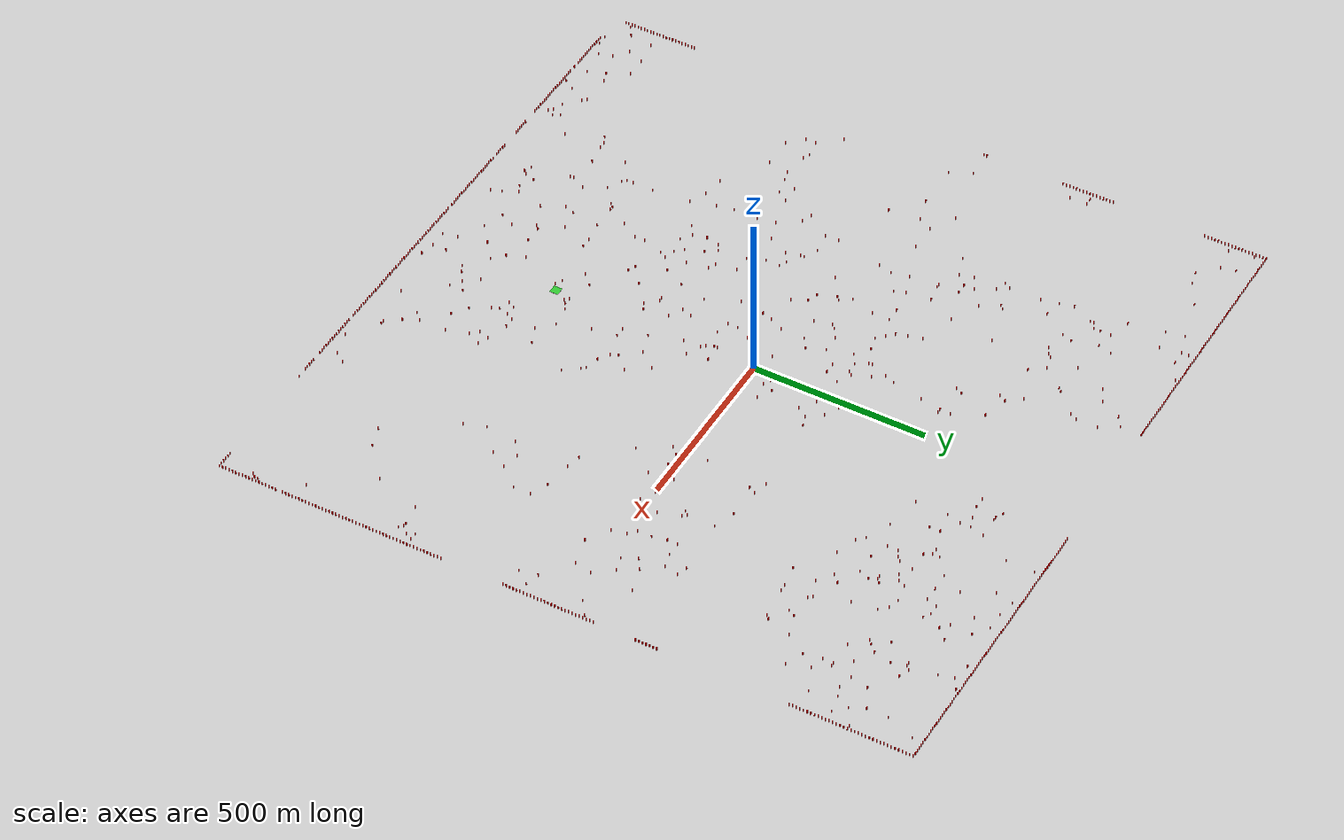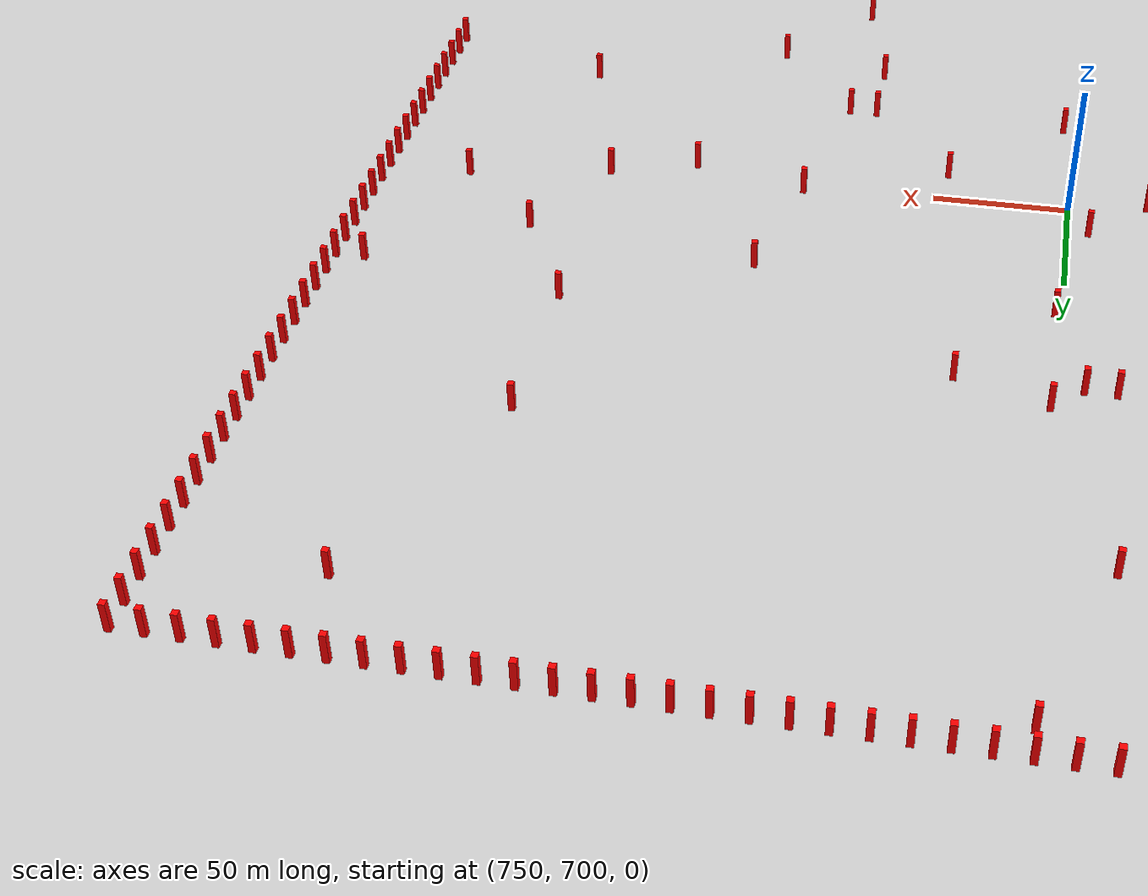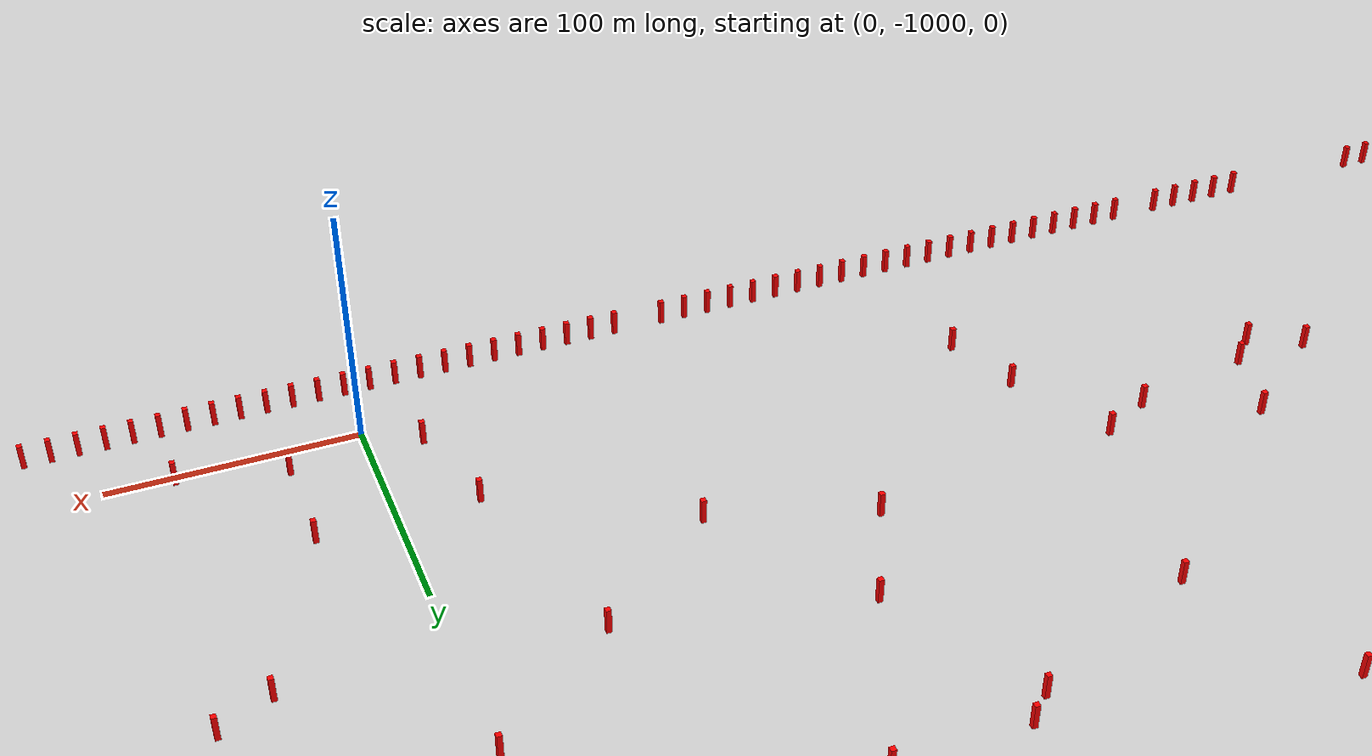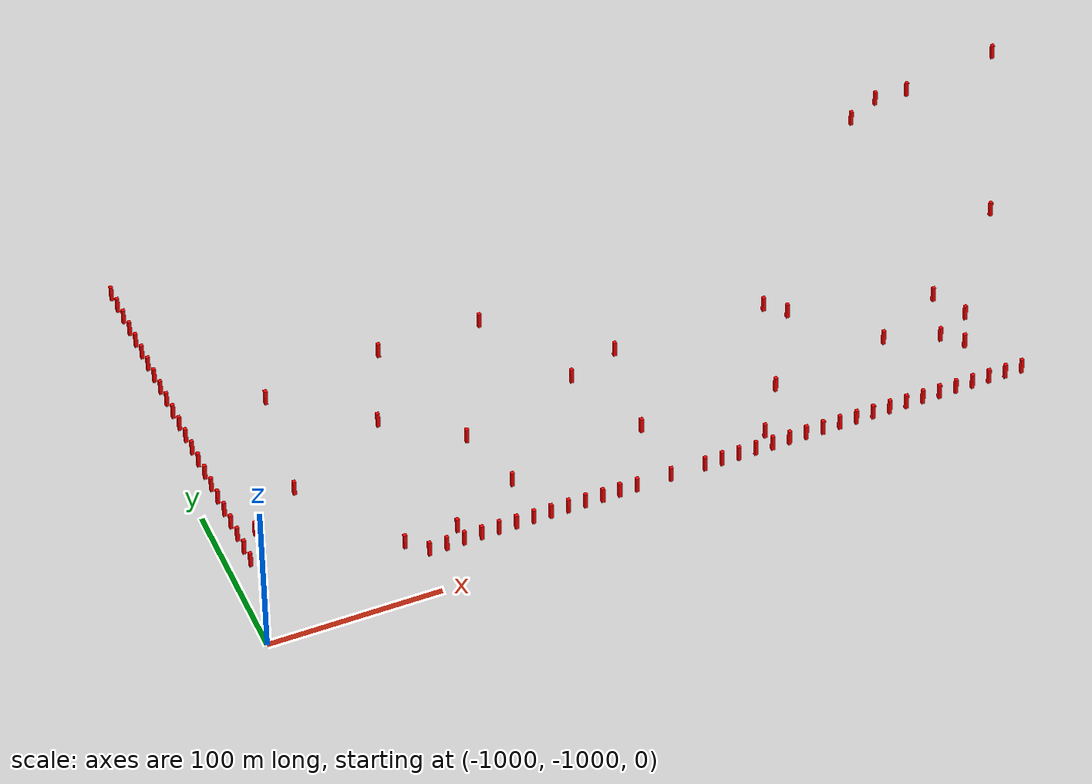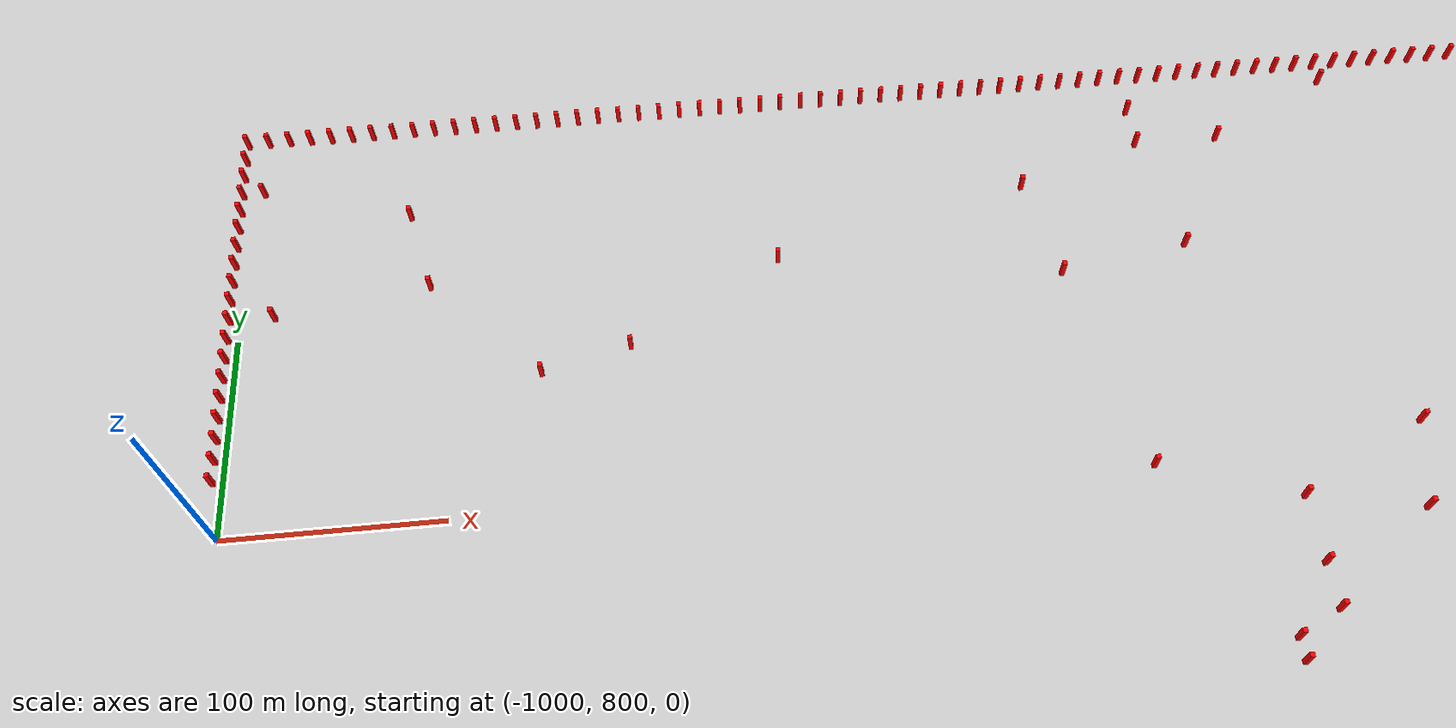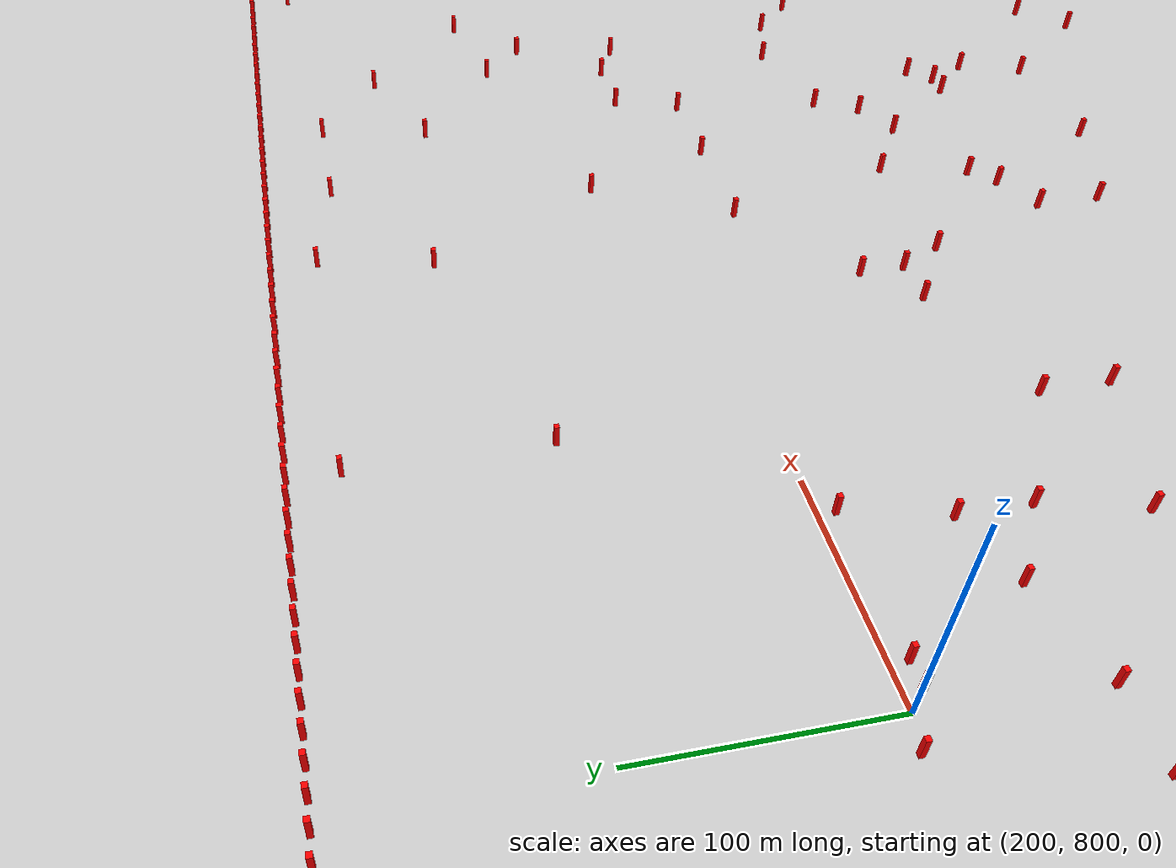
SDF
<sdf version="1.9">
 <world name="default">
  <physics type="ode">
   <max_step_size>0.004</max_step_size>
   <real_time_factor>1.0</real_time_factor>
   <real_time_update_rate>250</real_time_update_rate>
  </physics>
  <plugin name="gz::sim::systems::Physics" filename="gz-sim-physics-system"/>
  <plugin name="gz::sim::systems::UserCommands" filename="gz-sim-user-commands-system"/>
  <plugin name="gz::sim::systems::SceneBroadcaster" filename="gz-sim-scene-broadcaster-system"/>
  <plugin name="gz::sim::systems::Contact" filename="gz-sim-contact-system"/>
  <plugin name="gz::sim::systems::Imu" filename="gz-sim-imu-system"/>
  <plugin name="gz::sim::systems::AirPressure" filename="gz-sim-air-pressure-system"/>
  <plugin name="gz::sim::systems::ApplyLinkWrench" filename="gz-sim-apply-link-wrench-system"/>
  <plugin name="gz::sim::systems::NavSat" filename="gz-sim-navsat-system"/>
  <plugin name="gz::sim::systems::Sensors" filename="gz-sim-sensors-system">
   <render_engine>ogre2</render_engine>
  </plugin>
  <gravity>0 0 -9.8</gravity>
  <magnetic_field>6e-06 2.3e-05 -4.2e-05</magnetic_field>
  <atmosphere type="adiabatic"/>
  <scene>
   <grid>true</grid>
   <ambient>0.4 0.4 0.4 1</ambient>
   <background>0.7 0.7 0.7 1</background>
   <shadows>true</shadows>
  </scene>
  <model name="start_area">
   <static>true</static>
   <link name="start_area_link">
    <collision name="start_area_collision"><geometry><box><size>25 25 0.5</size></box></geometry></collision>
    <visual name="start_area_visual">
     <geometry><box><size>25 25 0.5</size></box></geometry>
     <material>
      <ambient>0.2 0.8 0.2 1</ambient>
      <diffuse>0.2 0.8 0.2 1</diffuse>
      <specular>0.1 0.1 0.1 1</specular>
     </material>
    </visual>
    <pose>7.5 -592.5 10 0 0 0</pose>
   </link>
  </model>
  <light name="sunUTC" type="directional">
   <pose>0 0 500 0 -0 0</pose>
   <intensity>1</intensity>
   <direction>0.001 0.625 -0.78</direction>
   <diffuse>0.904 0.904 0.904 1</diffuse>
   <specular>0.271 0.271 0.271 1</specular>
   <attenuation><range>2000</range><linear>0</linear><constant>1</constant><quadratic>0</quadratic></attenuation>
   <spot><inner_angle>0</inner_angle><outer_angle>0</outer_angle><falloff>0</falloff></spot>
  </light>
  <spherical_coordinates>
   <surface_model>EARTH_WGS84</surface_model>
   <world_frame_orientation>ENU</world_frame_orientation>
   <latitude_deg>23.284292</latitude_deg>
   <longitude_deg>46.667097</longitude_deg>
   <elevation>603.857</elevation>
  </spherical_coordinates>
  <model name="start_area_0">
   <static>true</static>
   <pose>-995.0 995.0 30 0 0 0</pose>
   <link name="start_area_link_0">
    <collision name="start_area_collision_0"><geometry><box><size>2 2 20</size></box></geometry></collision>
    <visual name="start_area_visual_0">
     <geometry><box><size>2 2 10</size></box></geometry>
     <material><ambient>1 0 0 1</ambient><diffuse>1 0 0 1</diffuse><specular>0.1 0.1 0.1 1</specular></material>
    </visual>
   </link>
  </model>
  <model name="start_area_1">
   <static>true</static>
   <pose>-985.0 995.0 30 0 0 0</pose>
   <link name="start_area_link_1">
    <collision name="start_area_collision_1"><geometry><box><size>2 2 20</size></box></geometry></collision>
    <visual name="start_area_visual_1">
     <geometry><box><size>2 2 10</size></box></geometry>
     <material><ambient>1 0 0 1</ambient><diffuse>1 0 0 1</diffuse><specular>0.1 0.1 0.1 1</specular></material>
    </visual>
   </link>
  </model>
  <model name="start_area_2">
   <static>true</static>
   <pose>-975.0 995.0 30 0 0 0</pose>
   <link name="start_area_link_2">
    <collision name="start_area_collision_2"><geometry><box><size>2 2 20</size></box></geometry></collision>
    <visual name="start_area_visual_2">
     <geometry><box><size>2 2 10</size></box></geometry>
     <material><ambient>1 0 0 1</ambient><diffuse>1 0 0 1</diffuse><specular>0.1 0.1 0.1 1</specular></material>
    </visual>
   </link>
  </model>
  <model name="start_area_3">
   <static>true</static>
   <pose>-965.0 995.0 30 0 0 0</pose>
   <link name="start_area_link_3">
    <collision name="start_area_collision_3"><geometry><box><size>2 2 20</size></box></geometry></collision>
    <visual name="start_area_visual_3">
     <geometry><box><size>2 2 10</size></box></geometry>
     <material><ambient>1 0 0 1</ambient><diffuse>1 0 0 1</diffuse><specular>0.1 0.1 0.1 1</specular></material>
    </visual>
   </link>
  </model>
  <model name="start_area_4">
   <static>true</static>
   <pose>-955.0 995.0 30 0 0 0</pose>
   <link name="start_area_link_4">
    <collision name="start_area_collision_4"><geometry><box><size>2 2 20</size></box></geometry></collision>
    <visual name="start_area_visual_4">
     <geometry><box><size>2 2 10</size></box></geometry>
     <material><ambient>1 0 0 1</ambient><diffuse>1 0 0 1</diffuse><specular>0.1 0.1 0.1 1</specular></material>
    </visual>
   </link>
  </model>
  <model name="start_area_5">
   <static>true</static>
   <pose>-945.0 995.0 30 0 0 0</pose>
   <link name="start_area_link_5">
    <collision name="start_area_collision_5"><geometry><box><size>2 2 20</size></box></geometry></collision>
    <visual name="start_area_visual_5">
     <geometry><box><size>2 2 10</size></box></geometry>
     <material><ambient>1 0 0 1</ambient><diffuse>1 0 0 1</diffuse><specular>0.1 0.1 0.1 1</specular></material>
    </visual>
   </link>
  </model>
  <model name="start_area_6">
   <static>true</static>
   <pose>-935.0 995.0 30 0 0 0</pose>
   <link name="start_area_link_6">
    <collision name="start_area_collision_6"><geometry><box><size>2 2 20</size></box></geometry></collision>
    <visual name="start_area_visual_6">
     <geometry><box><size>2 2 10</size></box></geometry>
     <material><ambient>1 0 0 1</ambient><diffuse>1 0 0 1</diffuse><specular>0.1 0.1 0.1 1</specular></material>
    </visual>
   </link>
  </model>
  <model name="start_area_7">
   <static>true</static>
   <pose>-925.0 995.0 30 0 0 0</pose>
   <link name="start_area_link_7">
    <collision name="start_area_collision_7"><geometry><box><size>2 2 20</size></box></geometry></collision>
    <visual name="start_area_visual_7">
     <geometry><box><size>2 2 10</size></box></geometry>
     <material><ambient>1 0 0 1</ambient><diffuse>1 0 0 1</diffuse><specular>0.1 0.1 0.1 1</specular></material>
    </visual>
   </link>
  </model>
  <model name="start_area_8">
   <static>true</static>
   <pose>-915.0 995.0 30 0 0 0</pose>
   <link name="start_area_link_8">
    <collision name="start_area_collision_8"><geometry><box><size>2 2 20</size></box></geometry></collision>
    <visual name="start_area_visual_8">
     <geometry><box><size>2 2 10</size></box></geometry>
     <material><ambient>1 0 0 1</ambient><diffuse>1 0 0 1</diffuse><specular>0.1 0.1 0.1 1</specular></material>
    </visual>
   </link>
  </model>
  <model name="start_area_9">
   <static>true</static>
   <pose>-905.0 995.0 30 0 0 0</pose>
   <link name="start_area_link_9">
    <collision name="start_area_collision_9"><geometry><box><size>2 2 20</size></box></geometry></collision>
    <visual name="start_area_visual_9">
     <geometry><box><size>2 2 10</size></box></geometry>
     <material><ambient>1 0 0 1</ambient><diffuse>1 0 0 1</diffuse><specular>0.1 0.1 0.1 1</specular></material>
    </visual>
   </link>
  </model>
  <model name="start_area_10">
   <static>true</static>
   <pose>-895.0 995.0 30 0 0 0</pose>
   <link name="start_area_link_10">
    <collision name="start_area_collision_10"><geometry><box><size>2 2 20</size></box></geometry></collision>
    <visual name="start_area_visual_10">
     <geometry><box><size>2 2 10</size></box></geometry>
     <material><ambient>1 0 0 1</ambient><diffuse>1 0 0 1</diffuse><specular>0.1 0.1 0.1 1</specular></material>
    </visual>
   </link>
  </model>
  <model name="start_area_11">
   <static>true</static>
   <pose>-885.0 995.0 30 0 0 0</pose>
   <link name="start_area_link_11">
    <collision name="start_area_collision_11"><geometry><box><size>2 2 20</size></box></geometry></collision>
    <visual name="start_area_visual_11">
     <geometry><box><size>2 2 10</size></box></geometry>
     <material><ambient>1 0 0 1</ambient><diffuse>1 0 0 1</diffuse><specular>0.1 0.1 0.1 1</specular></material>
    </visual>
   </link>
  </model>
  <model name="start_area_12">
   <static>true</static>
   <pose>-875.0 995.0 30 0 0 0</pose>
   <link name="start_area_link_12">
    <collision name="start_area_collision_12"><geometry><box><size>2 2 20</size></box></geometry></collision>
    <visual name="start_area_visual_12">
     <geometry><box><size>2 2 10</size></box></geometry>
     <material><ambient>1 0 0 1</ambient><diffuse>1 0 0 1</diffuse><specular>0.1 0.1 0.1 1</specular></material>
    </visual>
   </link>
  </model>
  <model name="start_area_13">
   <static>true</static>
   <pose>-865.0 995.0 30 0 0 0</pose>
   <link name="start_area_link_13">
    <collision name="start_area_collision_13"><geometry><box><size>2 2 20</size></box></geometry></collision>
    <visual name="start_area_visual_13">
     <geometry><box><size>2 2 10</size></box></geometry>
     <material><ambient>1 0 0 1</ambient><diffuse>1 0 0 1</diffuse><specular>0.1 0.1 0.1 1</specular></material>
    </visual>
   </link>
  </model>
  <model name="start_area_14">
   <static>true</static>
   <pose>-855.0 995.0 30 0 0 0</pose>
   <link name="start_area_link_14">
    <collision name="start_area_collision_14"><geometry><box><size>2 2 20</size></box></geometry></collision>
    <visual name="start_area_visual_14">
     <geometry><box><size>2 2 10</size></box></geometry>
     <material><ambient>1 0 0 1</ambient><diffuse>1 0 0 1</diffuse><specular>0.1 0.1 0.1 1</specular></material>
    </visual>
   </link>
  </model>
  <model name="start_area_15">
   <static>true</static>
   <pose>-845.0 995.0 30 0 0 0</pose>
   <link name="start_area_link_15">
    <collision name="start_area_collision_15"><geometry><box><size>2 2 20</size></box></geometry></collision>
    <visual name="start_area_visual_15">
     <geometry><box><size>2 2 10</size></box></geometry>
     <material><ambient>1 0 0 1</ambient><diffuse>1 0 0 1</diffuse><specular>0.1 0.1 0.1 1</specular></material>
    </visual>
   </link>
  </model>
  <model name="start_area_16">
   <static>true</static>
   <pose>-835.0 995.0 30 0 0 0</pose>
   <link name="start_area_link_16">
    <collision name="start_area_collision_16"><geometry><box><size>2 2 20</size></box></geometry></collision>
    <visual name="start_area_visual_16">
     <geometry><box><size>2 2 10</size></box></geometry>
     <material><ambient>1 0 0 1</ambient><diffuse>1 0 0 1</diffuse><specular>0.1 0.1 0.1 1</specular></material>
    </visual>
   </link>
  </model>
  <model name="start_area_17">
   <static>true</static>
   <pose>-825.0 995.0 30 0 0 0</pose>
   <link name="start_area_link_17">
    <collision name="start_area_collision_17"><geometry><box><size>2 2 20</size></box></geometry></collision>
    <visual name="start_area_visual_17">
     <geometry><box><size>2 2 10</size></box></geometry>
     <material><ambient>1 0 0 1</ambient><diffuse>1 0 0 1</diffuse><specular>0.1 0.1 0.1 1</specular></material>
    </visual>
   </link>
  </model>
  <model name="start_area_18">
   <static>true</static>
   <pose>-815.0 995.0 30 0 0 0</pose>
   <link name="start_area_link_18">
    <collision name="start_area_collision_18"><geometry><box><size>2 2 20</size></box></geometry></collision>
    <visual name="start_area_visual_18">
     <geometry><box><size>2 2 10</size></box></geometry>
     <material><ambient>1 0 0 1</ambient><diffuse>1 0 0 1</diffuse><specular>0.1 0.1 0.1 1</specular></material>
    </visual>
   </link>
  </model>
  <model name="start_area_19">
   <static>true</static>
   <pose>-805.0 995.0 30 0 0 0</pose>
   <link name="start_area_link_19">
    <collision name="start_area_collision_19"><geometry><box><size>2 2 20</size></box></geometry></collision>
    <visual name="start_area_visual_19">
     <geometry><box><size>2 2 10</size></box></geometry>
     <material><ambient>1 0 0 1</ambient><diffuse>1 0 0 1</diffuse><specular>0.1 0.1 0.1 1</specular></material>
    </visual>
   </link>
  </model>
  <model name="start_area_20">
   <static>true</static>
   <pose>-795.0 995.0 30 0 0 0</pose>
   <link name="start_area_link_20">
    <collision name="start_area_collision_20"><geometry><box><size>2 2 20</size></box></geometry></collision>
    <visual name="start_area_visual_20">
     <geometry><box><size>2 2 10</size></box></geometry>
     <material><ambient>1 0 0 1</ambient><diffuse>1 0 0 1</diffuse><specular>0.1 0.1 0.1 1</specular></material>
    </visual>
   </link>
  </model>
  <model name="start_area_21">
   <static>true</static>
   <pose>-785.0 995.0 30 0 0 0</pose>
   <link name="start_area_link_21">
    <collision name="start_area_collision_21"><geometry><box><size>2 2 20</size></box></geometry></collision>
    <visual name="start_area_visual_21">
     <geometry><box><size>2 2 10</size></box></geometry>
     <material><ambient>1 0 0 1</ambient><diffuse>1 0 0 1</diffuse><specular>0.1 0.1 0.1 1</specular></material>
    </visual>
   </link>
  </model>
  <model name="start_area_22">
   <static>true</static>
   <pose>-775.0 995.0 30 0 0 0</pose>
   <link name="start_area_link_22">
    <collision name="start_area_collision_22"><geometry><box><size>2 2 20</size></box></geometry></collision>
    <visual name="start_area_visual_22">
     <geometry><box><size>2 2 10</size></box></geometry>
     <material><ambient>1 0 0 1</ambient><diffuse>1 0 0 1</diffuse><specular>0.1 0.1 0.1 1</specular></material>
    </visual>
   </link>
  </model>
  <model name="start_area_23">
   <static>true</static>
   <pose>-765.0 995.0 30 0 0 0</pose>
   <link name="start_area_link_23">
    <collision name="start_area_collision_23"><geometry><box><size>2 2 20</size></box></geometry></collision>
    <visual name="start_area_visual_23">
     <geometry><box><size>2 2 10</size></box></geometry>
     <material><ambient>1 0 0 1</ambient><diffuse>1 0 0 1</diffuse><specular>0.1 0.1 0.1 1</specular></material>
    </visual>
   </link>
  </model>
  <model name="start_area_24">
   <static>true</static>
   <pose>-755.0 995.0 30 0 0 0</pose>
   <link name="start_area_link_24">
    <collision name="start_area_collision_24"><geometry><box><size>2 2 20</size></box></geometry></collision>
    <visual name="start_area_visual_24">
     <geometry><box><size>2 2 10</size></box></geometry>
     <material><ambient>1 0 0 1</ambient><diffuse>1 0 0 1</diffuse><specular>0.1 0.1 0.1 1</specular></material>
    </visual>
   </link>
  </model>
  <model name="start_area_25">
   <static>true</static>
   <pose>-745.0 995.0 30 0 0 0</pose>
   <link name="start_area_link_25">
    <collision name="start_area_collision_25"><geometry><box><size>2 2 20</size></box></geometry></collision>
    <visual name="start_area_visual_25">
     <geometry><box><size>2 2 10</size></box></geometry>
     <material><ambient>1 0 0 1</ambient><diffuse>1 0 0 1</diffuse><specular>0.1 0.1 0.1 1</specular></material>
    </visual>
   </link>
  </model>
  <model name="start_area_26">
   <static>true</static>
   <pose>-735.0 995.0 30 0 0 0</pose>
   <link name="start_area_link_26">
    <collision name="start_area_collision_26"><geometry><box><size>2 2 20</size></box></geometry></collision>
    <visual name="start_area_visual_26">
     <geometry><box><size>2 2 10</size></box></geometry>
     <material><ambient>1 0 0 1</ambient><diffuse>1 0 0 1</diffuse><specular>0.1 0.1 0.1 1</specular></material>
    </visual>
   </link>
  </model>
  <model name="start_area_27">
   <static>true</static>
   <pose>-725.0 995.0 30 0 0 0</pose>
   <link name="start_area_link_27">
    <collision name="start_area_collision_27"><geometry><box><size>2 2 20</size></box></geometry></collision>
    <visual name="start_area_visual_27">
     <geometry><box><size>2 2 10</size></box></geometry>
     <material><ambient>1 0 0 1</ambient><diffuse>1 0 0 1</diffuse><specular>0.1 0.1 0.1 1</specular></material>
    </visual>
   </link>
  </model>
  <model name="start_area_28">
   <static>true</static>
   <pose>-715.0 995.0 30 0 0 0</pose>
   <link name="start_area_link_28">
    <collision name="start_area_collision_28"><geometry><box><size>2 2 20</size></box></geometry></collision>
    <visual name="start_area_visual_28">
     <geometry><box><size>2 2 10</size></box></geometry>
     <material><ambient>1 0 0 1</ambient><diffuse>1 0 0 1</diffuse><specular>0.1 0.1 0.1 1</specular></material>
    </visual>
   </link>
  </model>
  <model name="start_area_29">
   <static>true</static>
   <pose>-705.0 995.0 30 0 0 0</pose>
   <link name="start_area_link_29">
    <collision name="start_area_collision_29"><geometry><box><size>2 2 20</size></box></geometry></collision>
    <visual name="start_area_visual_29">
     <geometry><box><size>2 2 10</size></box></geometry>
     <material><ambient>1 0 0 1</ambient><diffuse>1 0 0 1</diffuse><specular>0.1 0.1 0.1 1</specular></material>
    </visual>
   </link>
  </model>
  <model name="start_area_30">
   <static>true</static>
   <pose>-695.0 995.0 30 0 0 0</pose>
   <link name="start_area_link_30">
    <collision name="start_area_collision_30"><geometry><box><size>2 2 20</size></box></geometry></collision>
    <visual name="start_area_visual_30">
     <geometry><box><size>2 2 10</size></box></geometry>
     <material><ambient>1 0 0 1</ambient><diffuse>1 0 0 1</diffuse><specular>0.1 0.1 0.1 1</specular></material>
    </visual>
   </link>
  </model>
  <model name="start_area_31">
   <static>true</static>
   <pose>-685.0 995.0 30 0 0 0</pose>
   <link name="start_area_link_31">
    <collision name="start_area_collision_31"><geometry><box><size>2 2 20</size></box></geometry></collision>
    <visual name="start_area_visual_31">
     <geometry><box><size>2 2 10</size></box></geometry>
     <material><ambient>1 0 0 1</ambient><diffuse>1 0 0 1</diffuse><specular>0.1 0.1 0.1 1</specular></material>
    </visual>
   </link>
  </model>
  <model name="start_area_32">
   <static>true</static>
   <pose>-675.0 995.0 30 0 0 0</pose>
   <link name="start_area_link_32">
    <collision name="start_area_collision_32"><geometry><box><size>2 2 20</size></box></geometry></collision>
    <visual name="start_area_visual_32">
     <geometry><box><size>2 2 10</size></box></geometry>
     <material><ambient>1 0 0 1</ambient><diffuse>1 0 0 1</diffuse><specular>0.1 0.1 0.1 1</specular></material>
    </visual>
   </link>
  </model>
  <model name="start_area_33">
   <static>true</static>
   <pose>-665.0 995.0 30 0 0 0</pose>
   <link name="start_area_link_33">
    <collision name="start_area_collision_33"><geometry><box><size>2 2 20</size></box></geometry></collision>
    <visual name="start_area_visual_33">
     <geometry><box><size>2 2 10</size></box></geometry>
     <material><ambient>1 0 0 1</ambient><diffuse>1 0 0 1</diffuse><specular>0.1 0.1 0.1 1</specular></material>
    </visual>
   </link>
  </model>
  <model name="start_area_34">
   <static>true</static>
   <pose>-655.0 995.0 30 0 0 0</pose>
   <link name="start_area_link_34">
    <collision name="start_area_collision_34"><geometry><box><size>2 2 20</size></box></geometry></collision>
    <visual name="start_area_visual_34">
     <geometry><box><size>2 2 10</size></box></geometry>
     <material><ambient>1 0 0 1</ambient><diffuse>1 0 0 1</diffuse><specular>0.1 0.1 0.1 1</specular></material>
    </visual>
   </link>
  </model>
  <model name="start_area_35">
   <static>true</static>
   <pose>-645.0 995.0 30 0 0 0</pose>
   <link name="start_area_link_35">
    <collision name="start_area_collision_35"><geometry><box><size>2 2 20</size></box></geometry></collision>
    <visual name="start_area_visual_35">
     <geometry><box><size>2 2 10</size></box></geometry>
     <material><ambient>1 0 0 1</ambient><diffuse>1 0 0 1</diffuse><specular>0.1 0.1 0.1 1</specular></material>
    </visual>
   </link>
  </model>
  <model name="start_area_36">
   <static>true</static>
   <pose>-635.0 995.0 30 0 0 0</pose>
   <link name="start_area_link_36">
    <collision name="start_area_collision_36"><geometry><box><size>2 2 20</size></box></geometry></collision>
    <visual name="start_area_visual_36">
     <geometry><box><size>2 2 10</size></box></geometry>
     <material><ambient>1 0 0 1</ambient><diffuse>1 0 0 1</diffuse><specular>0.1 0.1 0.1 1</specular></material>
    </visual>
   </link>
  </model>
  <model name="start_area_37">
   <static>true</static>
   <pose>-625.0 995.0 30 0 0 0</pose>
   <link name="start_area_link_37">
    <collision name="start_area_collision_37"><geometry><box><size>2 2 20</size></box></geometry></collision>
    <visual name="start_area_visual_37">
     <geometry><box><size>2 2 10</size></box></geometry>
     <material><ambient>1 0 0 1</ambient><diffuse>1 0 0 1</diffuse><specular>0.1 0.1 0.1 1</specular></material>
    </visual>
   </link>
  </model>
  <model name="start_area_38">
   <static>true</static>
   <pose>-615.0 995.0 30 0 0 0</pose>
   <link name="start_area_link_38">
    <collision name="start_area_collision_38"><geometry><box><size>2 2 20</size></box></geometry></collision>
    <visual name="start_area_visual_38">
     <geometry><box><size>2 2 10</size></box></geometry>
     <material><ambient>1 0 0 1</ambient><diffuse>1 0 0 1</diffuse><specular>0.1 0.1 0.1 1</specular></material>
    </visual>
   </link>
  </model>
  <model name="start_area_39">
   <static>true</static>
   <pose>-605.0 995.0 30 0 0 0</pose>
   <link name="start_area_link_39">
    <collision name="start_area_collision_39"><geometry><box><size>2 2 20</size></box></geometry></collision>
    <visual name="start_area_visual_39">
     <geometry><box><size>2 2 10</size></box></geometry>
     <material><ambient>1 0 0 1</ambient><diffuse>1 0 0 1</diffuse><specular>0.1 0.1 0.1 1</specular></material>
    </visual>
   </link>
  </model>
  <model name="start_area_40">
   <static>true</static>
   <pose>-595.0 995.0 30 0 0 0</pose>
   <link name="start_area_link_40">
    <collision name="start_area_collision_40"><geometry><box><size>2 2 20</size></box></geometry></collision>
    <visual name="start_area_visual_40">
     <geometry><box><size>2 2 10</size></box></geometry>
     <material><ambient>1 0 0 1</ambient><diffuse>1 0 0 1</diffuse><specular>0.1 0.1 0.1 1</specular></material>
    </visual>
   </link>
  </model>
  <model name="start_area_41">
   <static>true</static>
   <pose>-585.0 995.0 30 0 0 0</pose>
   <link name="start_area_link_41">
    <collision name="start_area_collision_41"><geometry><box><size>2 2 20</size></box></geometry></collision>
    <visual name="start_area_visual_41">
     <geometry><box><size>2 2 10</size></box></geometry>
     <material><ambient>1 0 0 1</ambient><diffuse>1 0 0 1</diffuse><specular>0.1 0.1 0.1 1</specular></material>
    </visual>
   </link>
  </model>
  <model name="start_area_42">
   <static>true</static>
   <pose>-575.0 995.0 30 0 0 0</pose>
   <link name="start_area_link_42">
    <collision name="start_area_collision_42"><geometry><box><size>2 2 20</size></box></geometry></collision>
    <visual name="start_area_visual_42">
     <geometry><box><size>2 2 10</size></box></geometry>
     <material><ambient>1 0 0 1</ambient><diffuse>1 0 0 1</diffuse><specular>0.1 0.1 0.1 1</specular></material>
    </visual>
   </link>
  </model>
  <model name="start_area_43">
   <static>true</static>
   <pose>-565.0 995.0 30 0 0 0</pose>
   <link name="start_area_link_43">
    <collision name="start_area_collision_43"><geometry><box><size>2 2 20</size></box></geometry></collision>
    <visual name="start_area_visual_43">
     <geometry><box><size>2 2 10</size></box></geometry>
     <material><ambient>1 0 0 1</ambient><diffuse>1 0 0 1</diffuse><specular>0.1 0.1 0.1 1</specular></material>
    </visual>
   </link>
  </model>
  <model name="start_area_44">
   <static>true</static>
   <pose>-555.0 995.0 30 0 0 0</pose>
   <link name="start_area_link_44">
    <collision name="start_area_collision_44"><geometry><box><size>2 2 20</size></box></geometry></collision>
    <visual name="start_area_visual_44">
     <geometry><box><size>2 2 10</size></box></geometry>
     <material><ambient>1 0 0 1</ambient><diffuse>1 0 0 1</diffuse><specular>0.1 0.1 0.1 1</specular></material>
    </visual>
   </link>
  </model>
  <model name="start_area_45">
   <static>true</static>
   <pose>-545.0 995.0 30 0 0 0</pose>
   <link name="start_area_link_45">
    <collision name="start_area_collision_45"><geometry><box><size>2 2 20</size></box></geometry></collision>
    <visual name="start_area_visual_45">
     <geometry><box><size>2 2 10</size></box></geometry>
     <material><ambient>1 0 0 1</ambient><diffuse>1 0 0 1</diffuse><specular>0.1 0.1 0.1 1</specular></material>
    </visual>
   </link>
  </model>
  <model name="start_area_46">
   <static>true</static>
   <pose>-535.0 995.0 30 0 0 0</pose>
   <link name="start_area_link_46">
    <collision name="start_area_collision_46"><geometry><box><size>2 2 20</size></box></geometry></collision>
    <visual name="start_area_visual_46">
     <geometry><box><size>2 2 10</size></box></geometry>
     <material><ambient>1 0 0 1</ambient><diffuse>1 0 0 1</diffuse><specular>0.1 0.1 0.1 1</specular></material>
    </visual>
   </link>
  </model>
  <model name="start_area_47">
   <static>true</static>
   <pose>-525.0 995.0 30 0 0 0</pose>
   <link name="start_area_link_47">
    <collision name="start_area_collision_47"><geometry><box><size>2 2 20</size></box></geometry></collision>
    <visual name="start_area_visual_47">
     <geometry><box><size>2 2 10</size></box></geometry>
     <material><ambient>1 0 0 1</ambient><diffuse>1 0 0 1</diffuse><specular>0.1 0.1 0.1 1</specular></material>
    </visual>
   </link>
  </model>
  <model name="start_area_48">
   <static>true</static>
   <pose>-515.0 995.0 30 0 0 0</pose>
   <link name="start_area_link_48">
    <collision name="start_area_collision_48"><geometry><box><size>2 2 20</size></box></geometry></collision>
    <visual name="start_area_visual_48">
     <geometry><box><size>2 2 10</size></box></geometry>
     <material><ambient>1 0 0 1</ambient><diffuse>1 0 0 1</diffuse><specular>0.1 0.1 0.1 1</specular></material>
    </visual>
   </link>
  </model>
  <model name="start_area_49">
   <static>true</static>
   <pose>-505.0 995.0 30 0 0 0</pose>
   <link name="start_area_link_49">
    <collision name="start_area_collision_49"><geometry><box><size>2 2 20</size></box></geometry></collision>
    <visual name="start_area_visual_49">
     <geometry><box><size>2 2 10</size></box></geometry>
     <material><ambient>1 0 0 1</ambient><diffuse>1 0 0 1</diffuse><specular>0.1 0.1 0.1 1</specular></material>
    </visual>
   </link>
  </model>
  <model name="start_area_50">
   <static>true</static>
   <pose>-495.0 995.0 30 0 0 0</pose>
   <link name="start_area_link_50">
    <collision name="start_area_collision_50"><geometry><box><size>2 2 20</size></box></geometry></collision>
    <visual name="start_area_visual_50">
     <geometry><box><size>2 2 10</size></box></geometry>
     <material><ambient>1 0 0 1</ambient><diffuse>1 0 0 1</diffuse><specular>0.1 0.1 0.1 1</specular></material>
    </visual>
   </link>
  </model>
  <model name="start_area_51">
   <static>true</static>
   <pose>-485.0 995.0 30 0 0 0</pose>
   <link name="start_area_link_51">
    <collision name="start_area_collision_51"><geometry><box><size>2 2 20</size></box></geometry></collision>
    <visual name="start_area_visual_51">
     <geometry><box><size>2 2 10</size></box></geometry>
     <material><ambient>1 0 0 1</ambient><diffuse>1 0 0 1</diffuse><specular>0.1 0.1 0.1 1</specular></material>
    </visual>
   </link>
  </model>
  <model name="start_area_52">
   <static>true</static>
   <pose>-475.0 995.0 30 0 0 0</pose>
   <link name="start_area_link_52">
    <collision name="start_area_collision_52"><geometry><box><size>2 2 20</size></box></geometry></collision>
    <visual name="start_area_visual_52">
     <geometry><box><size>2 2 10</size></box></geometry>
     <material><ambient>1 0 0 1</ambient><diffuse>1 0 0 1</diffuse><specular>0.1 0.1 0.1 1</specular></material>
    </visual>
   </link>
  </model>
  <model name="start_area_53">
   <static>true</static>
   <pose>-465.0 995.0 30 0 0 0</pose>
   <link name="start_area_link_53">
    <collision name="start_area_collision_53"><geometry><box><size>2 2 20</size></box></geometry></collision>
    <visual name="start_area_visual_53">
     <geometry><box><size>2 2 10</size></box></geometry>
     <material><ambient>1 0 0 1</ambient><diffuse>1 0 0 1</diffuse><specular>0.1 0.1 0.1 1</specular></material>
    </visual>
   </link>
  </model>
  <model name="start_area_54">
   <static>true</static>
   <pose>-455.0 995.0 30 0 0 0</pose>
   <link name="start_area_link_54">
    <collision name="start_area_collision_54"><geometry><box><size>2 2 20</size></box></geometry></collision>
    <visual name="start_area_visual_54">
     <geometry><box><size>2 2 10</size></box></geometry>
     <material><ambient>1 0 0 1</ambient><diffuse>1 0 0 1</diffuse><specular>0.1 0.1 0.1 1</specular></material>
    </visual>
   </link>
  </model>
  <model name="start_area_55">
   <static>true</static>
   <pose>-445.0 995.0 30 0 0 0</pose>
   <link name="start_area_link_55">
    <collision name="start_area_collision_55"><geometry><box><size>2 2 20</size></box></geometry></collision>
    <visual name="start_area_visual_55">
     <geometry><box><size>2 2 10</size></box></geometry>
     <material><ambient>1 0 0 1</ambient><diffuse>1 0 0 1</diffuse><specular>0.1 0.1 0.1 1</specular></material>
    </visual>
   </link>
  </model>
  <model name="start_area_56">
   <static>true</static>
   <pose>-435.0 995.0 30 0 0 0</pose>
   <link name="start_area_link_56">
    <collision name="start_area_collision_56"><geometry><box><size>2 2 20</size></box></geometry></collision>
    <visual name="start_area_visual_56">
     <geometry><box><size>2 2 10</size></box></geometry>
     <material><ambient>1 0 0 1</ambient><diffuse>1 0 0 1</diffuse><specular>0.1 0.1 0.1 1</specular></material>
    </visual>
   </link>
  </model>
  <model name="start_area_57">
   <static>true</static>
   <pose>-425.0 995.0 30 0 0 0</pose>
   <link name="start_area_link_57">
    <collision name="start_area_collision_57"><geometry><box><size>2 2 20</size></box></geometry></collision>
    <visual name="start_area_visual_57">
     <geometry><box><size>2 2 10</size></box></geometry>
     <material><ambient>1 0 0 1</ambient><diffuse>1 0 0 1</diffuse><specular>0.1 0.1 0.1 1</specular></material>
    </visual>
   </link>
  </model>
  <model name="start_area_58">
   <static>true</static>
   <pose>-415.0 995.0 30 0 0 0</pose>
   <link name="start_area_link_58">
    <collision name="start_area_collision_58"><geometry><box><size>2 2 20</size></box></geometry></collision>
    <visual name="start_area_visual_58">
     <geometry><box><size>2 2 10</size></box></geometry>
     <material><ambient>1 0 0 1</ambient><diffuse>1 0 0 1</diffuse><specular>0.1 0.1 0.1 1</specular></material>
    </visual>
   </link>
  </model>
  <model name="start_area_59">
   <static>true</static>
   <pose>-405.0 995.0 30 0 0 0</pose>
   <link name="start_area_link_59">
    <collision name="start_area_collision_59"><geometry><box><size>2 2 20</size></box></geometry></collision>
    <visual name="start_area_visual_59">
     <geometry><box><size>2 2 10</size></box></geometry>
     <material><ambient>1 0 0 1</ambient><diffuse>1 0 0 1</diffuse><specular>0.1 0.1 0.1 1</specular></material>
    </visual>
   </link>
  </model>
  <model name="start_area_60">
   <static>true</static>
   <pose>-395.0 995.0 30 0 0 0</pose>
   <link name="start_area_link_60">
    <collision name="start_area_collision_60"><geometry><box><size>2 2 20</size></box></geometry></collision>
    <visual name="start_area_visual_60">
     <geometry><box><size>2 2 10</size></box></geometry>
     <material><ambient>1 0 0 1</ambient><diffuse>1 0 0 1</diffuse><specular>0.1 0.1 0.1 1</specular></material>
    </visual>
   </link>
  </model>
  <model name="start_area_61">
   <static>true</static>
   <pose>-385.0 995.0 30 0 0 0</pose>
   <link name="start_area_link_61">
    <collision name="start_area_collision_61"><geometry><box><size>2 2 20</size></box></geometry></collision>
    <visual name="start_area_visual_61">
     <geometry><box><size>2 2 10</size></box></geometry>
     <material><ambient>1 0 0 1</ambient><diffuse>1 0 0 1</diffuse><specular>0.1 0.1 0.1 1</specular></material>
    </visual>
   </link>
  </model>
  <model name="start_area_62">
   <static>true</static>
   <pose>-375.0 995.0 30 0 0 0</pose>
   <link name="start_area_link_62">
    <collision name="start_area_collision_62"><geometry><box><size>2 2 20</size></box></geometry></collision>
    <visual name="start_area_visual_62">
     <geometry><box><size>2 2 10</size></box></geometry>
     <material><ambient>1 0 0 1</ambient><diffuse>1 0 0 1</diffuse><specular>0.1 0.1 0.1 1</specular></material>
    </visual>
   </link>
  </model>
  <model name="start_area_63">
   <static>true</static>
   <pose>-365.0 995.0 30 0 0 0</pose>
   <link name="start_area_link_63">
    <collision name="start_area_collision_63"><geometry><box><size>2 2 20</size></box></geometry></collision>
    <visual name="start_area_visual_63">
     <geometry><box><size>2 2 10</size></box></geometry>
     <material><ambient>1 0 0 1</ambient><diffuse>1 0 0 1</diffuse><specular>0.1 0.1 0.1 1</specular></material>
    </visual>
   </link>
  </model>
  <model name="start_area_64">
   <static>true</static>
   <pose>-355.0 995.0 30 0 0 0</pose>
   <link name="start_area_link_64">
    <collision name="start_area_collision_64"><geometry><box><size>2 2 20</size></box></geometry></collision>
    <visual name="start_area_visual_64">
     <geometry><box><size>2 2 10</size></box></geometry>
     <material><ambient>1 0 0 1</ambient><diffuse>1 0 0 1</diffuse><specular>0.1 0.1 0.1 1</specular></material>
    </visual>
   </link>
  </model>
  <model name="start_area_65">
   <static>true</static>
   <pose>-345.0 995.0 30 0 0 0</pose>
   <link name="start_area_link_65">
    <collision name="start_area_collision_65"><geometry><box><size>2 2 20</size></box></geometry></collision>
    <visual name="start_area_visual_65">
     <geometry><box><size>2 2 10</size></box></geometry>
     <material><ambient>1 0 0 1</ambient><diffuse>1 0 0 1</diffuse><specular>0.1 0.1 0.1 1</specular></material>
    </visual>
   </link>
  </model>
  <model name="start_area_66">
   <static>true</static>
   <pose>-335.0 995.0 30 0 0 0</pose>
   <link name="start_area_link_66">
    <collision name="start_area_collision_66"><geometry><box><size>2 2 20</size></box></geometry></collision>
    <visual name="start_area_visual_66">
     <geometry><box><size>2 2 10</size></box></geometry>
     <material><ambient>1 0 0 1</ambient><diffuse>1 0 0 1</diffuse><specular>0.1 0.1 0.1 1</specular></material>
    </visual>
   </link>
  </model>
  <model name="start_area_67">
   <static>true</static>
   <pose>-325.0 995.0 30 0 0 0</pose>
   <link name="start_area_link_67">
    <collision name="start_area_collision_67"><geometry><box><size>2 2 20</size></box></geometry></collision>
    <visual name="start_area_visual_67">
     <geometry><box><size>2 2 10</size></box></geometry>
     <material><ambient>1 0 0 1</ambient><diffuse>1 0 0 1</diffuse><specular>0.1 0.1 0.1 1</specular></material>
    </visual>
   </link>
  </model>
  <model name="start_area_68">
   <static>true</static>
   <pose>-315.0 995.0 30 0 0 0</pose>
   <link name="start_area_link_68">
    <collision name="start_area_collision_68"><geometry><box><size>2 2 20</size></box></geometry></collision>
    <visual name="start_area_visual_68">
     <geometry><box><size>2 2 10</size></box></geometry>
     <material><ambient>1 0 0 1</ambient><diffuse>1 0 0 1</diffuse><specular>0.1 0.1 0.1 1</specular></material>
    </visual>
   </link>
  </model>
  <model name="start_area_69">
   <static>true</static>
   <pose>-305.0 995.0 30 0 0 0</pose>
   <link name="start_area_link_69">
    <collision name="start_area_collision_69"><geometry><box><size>2 2 20</size></box></geometry></collision>
    <visual name="start_area_visual_69">
     <geometry><box><size>2 2 10</size></box></geometry>
     <material><ambient>1 0 0 1</ambient><diffuse>1 0 0 1</diffuse><specular>0.1 0.1 0.1 1</specular></material>
    </visual>
   </link>
  </model>
  <model name="start_area_70">
   <static>true</static>
   <pose>-295.0 995.0 30 0 0 0</pose>
   <link name="start_area_link_70">
    <collision name="start_area_collision_70"><geometry><box><size>2 2 20</size></box></geometry></collision>
    <visual name="start_area_visual_70">
     <geometry><box><size>2 2 10</size></box></geometry>
     <material><ambient>1 0 0 1</ambient><diffuse>1 0 0 1</diffuse><specular>0.1 0.1 0.1 1</specular></material>
    </visual>
   </link>
  </model>
  <model name="start_area_71">
   <static>true</static>
   <pose>-285.0 995.0 30 0 0 0</pose>
   <link name="start_area_link_71">
    <collision name="start_area_collision_71"><geometry><box><size>2 2 20</size></box></geometry></collision>
    <visual name="start_area_visual_71">
     <geometry><box><size>2 2 10</size></box></geometry>
     <material><ambient>1 0 0 1</ambient><diffuse>1 0 0 1</diffuse><specular>0.1 0.1 0.1 1</specular></material>
    </visual>
   </link>
  </model>
  <model name="start_area_72">
   <static>true</static>
   <pose>-275.0 995.0 30 0 0 0</pose>
   <link name="start_area_link_72">
    <collision name="start_area_collision_72"><geometry><box><size>2 2 20</size></box></geometry></collision>
    <visual name="start_area_visual_72">
     <geometry><box><size>2 2 10</size></box></geometry>
     <material><ambient>1 0 0 1</ambient><diffuse>1 0 0 1</diffuse><specular>0.1 0.1 0.1 1</specular></material>
    </visual>
   </link>
  </model>
  <model name="start_area_73">
   <static>true</static>
   <pose>-265.0 995.0 30 0 0 0</pose>
   <link name="start_area_link_73">
    <collision name="start_area_collision_73"><geometry><box><size>2 2 20</size></box></geometry></collision>
    <visual name="start_area_visual_73">
     <geometry><box><size>2 2 10</size></box></geometry>
     <material><ambient>1 0 0 1</ambient><diffuse>1 0 0 1</diffuse><specular>0.1 0.1 0.1 1</specular></material>
    </visual>
   </link>
  </model>
  <model name="start_area_74">
   <static>true</static>
   <pose>-255.0 995.0 30 0 0 0</pose>
   <link name="start_area_link_74">
    <collision name="start_area_collision_74"><geometry><box><size>2 2 20</size></box></geometry></collision>
    <visual name="start_area_visual_74">
     <geometry><box><size>2 2 10</size></box></geometry>
     <material><ambient>1 0 0 1</ambient><diffuse>1 0 0 1</diffuse><specular>0.1 0.1 0.1 1</specular></material>
    </visual>
   </link>
  </model>
  <model name="start_area_75">
   <static>true</static>
   <pose>-245.0 995.0 30 0 0 0</pose>
   <link name="start_area_link_75">
    <collision name="start_area_collision_75"><geometry><box><size>2 2 20</size></box></geometry></collision>
    <visual name="start_area_visual_75">
     <geometry><box><size>2 2 10</size></box></geometry>
     <material><ambient>1 0 0 1</ambient><diffuse>1 0 0 1</diffuse><specular>0.1 0.1 0.1 1</specular></material>
    </visual>
   </link>
  </model>
  <model name="start_area_76">
   <static>true</static>
   <pose>175.0 995.0 30 0 0 0</pose>
   <link name="start_area_link_76">
    <collision name="start_area_collision_76"><geometry><box><size>2 2 20</size></box></geometry></collision>
    <visual name="start_area_visual_76">
     <geometry><box><size>2 2 10</size></box></geometry>
     <material><ambient>1 0 0 1</ambient><diffuse>1 0 0 1</diffuse><specular>0.1 0.1 0.1 1</specular></material>
    </visual>
   </link>
  </model>
  <model name="start_area_77">
   <static>true</static>
   <pose>185.0 995.0 30 0 0 0</pose>
   <link name="start_area_link_77">
    <collision name="start_area_collision_77"><geometry><box><size>2 2 20</size></box></geometry></collision>
    <visual name="start_area_visual_77">
     <geometry><box><size>2 2 10</size></box></geometry>
     <material><ambient>1 0 0 1</ambient><diffuse>1 0 0 1</diffuse><specular>0.1 0.1 0.1 1</specular></material>
    </visual>
   </link>
  </model>
  <model name="start_area_78">
   <static>true</static>
   <pose>195.0 995.0 30 0 0 0</pose>
   <link name="start_area_link_78">
    <collision name="start_area_collision_78"><geometry><box><size>2 2 20</size></box></geometry></collision>
    <visual name="start_area_visual_78">
     <geometry><box><size>2 2 10</size></box></geometry>
     <material><ambient>1 0 0 1</ambient><diffuse>1 0 0 1</diffuse><specular>0.1 0.1 0.1 1</specular></material>
    </visual>
   </link>
  </model>
  <model name="start_area_79">
   <static>true</static>
   <pose>205.0 995.0 30 0 0 0</pose>
   <link name="start_area_link_79">
    <collision name="start_area_collision_79"><geometry><box><size>2 2 20</size></box></geometry></collision>
    <visual name="start_area_visual_79">
     <geometry><box><size>2 2 10</size></box></geometry>
     <material><ambient>1 0 0 1</ambient><diffuse>1 0 0 1</diffuse><specular>0.1 0.1 0.1 1</specular></material>
    </visual>
   </link>
  </model>
  <model name="start_area_80">
   <static>true</static>
   <pose>215.0 995.0 30 0 0 0</pose>
   <link name="start_area_link_80">
    <collision name="start_area_collision_80"><geometry><box><size>2 2 20</size></box></geometry></collision>
    <visual name="start_area_visual_80">
     <geometry><box><size>2 2 10</size></box></geometry>
     <material><ambient>1 0 0 1</ambient><diffuse>1 0 0 1</diffuse><specular>0.1 0.1 0.1 1</specular></material>
    </visual>
   </link>
  </model>
  <model name="start_area_81">
   <static>true</static>
   <pose>225.0 995.0 30 0 0 0</pose>
   <link name="start_area_link_81">
    <collision name="start_area_collision_81"><geometry><box><size>2 2 20</size></box></geometry></collision>
    <visual name="start_area_visual_81">
     <geometry><box><size>2 2 10</size></box></geometry>
     <material><ambient>1 0 0 1</ambient><diffuse>1 0 0 1</diffuse><specular>0.1 0.1 0.1 1</specular></material>
    </visual>
   </link>
  </model>
  <model name="start_area_82">
   <static>true</static>
   <pose>235.0 995.0 30 0 0 0</pose>
   <link name="start_area_link_82">
    <collision name="start_area_collision_82"><geometry><box><size>2 2 20</size></box></geometry></collision>
    <visual name="start_area_visual_82">
     <geometry><box><size>2 2 10</size></box></geometry>
     <material><ambient>1 0 0 1</ambient><diffuse>1 0 0 1</diffuse><specular>0.1 0.1 0.1 1</specular></material>
    </visual>
   </link>
  </model>
  <model name="start_area_83">
   <static>true</static>
   <pose>245.0 995.0 30 0 0 0</pose>
   <link name="start_area_link_83">
    <collision name="start_area_collision_83"><geometry><box><size>2 2 20</size></box></geometry></collision>
    <visual name="start_area_visual_83">
     <geometry><box><size>2 2 10</size></box></geometry>
     <material><ambient>1 0 0 1</ambient><diffuse>1 0 0 1</diffuse><specular>0.1 0.1 0.1 1</specular></material>
    </visual>
   </link>
  </model>
  <model name="start_area_84">
   <static>true</static>
   <pose>255.0 995.0 30 0 0 0</pose>
   <link name="start_area_link_84">
    <collision name="start_area_collision_84"><geometry><box><size>2 2 20</size></box></geometry></collision>
    <visual name="start_area_visual_84">
     <geometry><box><size>2 2 10</size></box></geometry>
     <material><ambient>1 0 0 1</ambient><diffuse>1 0 0 1</diffuse><specular>0.1 0.1 0.1 1</specular></material>
    </visual>
   </link>
  </model>
  <model name="start_area_85">
   <static>true</static>
   <pose>265.0 995.0 30 0 0 0</pose>
   <link name="start_area_link_85">
    <collision name="start_area_collision_85"><geometry><box><size>2 2 20</size></box></geometry></collision>
    <visual name="start_area_visual_85">
     <geometry><box><size>2 2 10</size></box></geometry>
     <material><ambient>1 0 0 1</ambient><diffuse>1 0 0 1</diffuse><specular>0.1 0.1 0.1 1</specular></material>
    </visual>
   </link>
  </model>
  <model name="start_area_86">
   <static>true</static>
   <pose>275.0 995.0 30 0 0 0</pose>
   <link name="start_area_link_86">
    <collision name="start_area_collision_86"><geometry><box><size>2 2 20</size></box></geometry></collision>
    <visual name="start_area_visual_86">
     <geometry><box><size>2 2 10</size></box></geometry>
     <material><ambient>1 0 0 1</ambient><diffuse>1 0 0 1</diffuse><specular>0.1 0.1 0.1 1</specular></material>
    </visual>
   </link>
  </model>
  <model name="start_area_87">
   <static>true</static>
   <pose>285.0 995.0 30 0 0 0</pose>
   <link name="start_area_link_87">
    <collision name="start_area_collision_87"><geometry><box><size>2 2 20</size></box></geometry></collision>
    <visual name="start_area_visual_87">
     <geometry><box><size>2 2 10</size></box></geometry>
     <material><ambient>1 0 0 1</ambient><diffuse>1 0 0 1</diffuse><specular>0.1 0.1 0.1 1</specular></material>
    </visual>
   </link>
  </model>
  <model name="start_area_88">
   <static>true</static>
   <pose>295.0 995.0 30 0 0 0</pose>
   <link name="start_area_link_88">
    <collision name="start_area_collision_88"><geometry><box><size>2 2 20</size></box></geometry></collision>
    <visual name="start_area_visual_88">
     <geometry><box><size>2 2 10</size></box></geometry>
     <material><ambient>1 0 0 1</ambient><diffuse>1 0 0 1</diffuse><specular>0.1 0.1 0.1 1</specular></material>
    </visual>
   </link>
  </model>
  <model name="start_area_89">
   <static>true</static>
   <pose>305.0 995.0 30 0 0 0</pose>
   <link name="start_area_link_89">
    <collision name="start_area_collision_89"><geometry><box><size>2 2 20</size></box></geometry></collision>
    <visual name="start_area_visual_89">
     <geometry><box><size>2 2 10</size></box></geometry>
     <material><ambient>1 0 0 1</ambient><diffuse>1 0 0 1</diffuse><specular>0.1 0.1 0.1 1</specular></material>
    </visual>
   </link>
  </model>
  <model name="start_area_90">
   <static>true</static>
   <pose>315.0 995.0 30 0 0 0</pose>
   <link name="start_area_link_90">
    <collision name="start_area_collision_90"><geometry><box><size>2 2 20</size></box></geometry></collision>
    <visual name="start_area_visual_90">
     <geometry><box><size>2 2 10</size></box></geometry>
     <material><ambient>1 0 0 1</ambient><diffuse>1 0 0 1</diffuse><specular>0.1 0.1 0.1 1</specular></material>
    </visual>
   </link>
  </model>
  <model name="start_area_91">
   <static>true</static>
   <pose>325.0 995.0 30 0 0 0</pose>
   <link name="start_area_link_91">
    <collision name="start_area_collision_91"><geometry><box><size>2 2 20</size></box></geometry></collision>
    <visual name="start_area_visual_91">
     <geometry><box><size>2 2 10</size></box></geometry>
     <material><ambient>1 0 0 1</ambient><diffuse>1 0 0 1</diffuse><specular>0.1 0.1 0.1 1</specular></material>
    </visual>
   </link>
  </model>
  <model name="start_area_92">
   <static>true</static>
   <pose>335.0 995.0 30 0 0 0</pose>
   <link name="start_area_link_92">
    <collision name="start_area_collision_92"><geometry><box><size>2 2 20</size></box></geometry></collision>
    <visual name="start_area_visual_92">
     <geometry><box><size>2 2 10</size></box></geometry>
     <material><ambient>1 0 0 1</ambient><diffuse>1 0 0 1</diffuse><specular>0.1 0.1 0.1 1</specular></material>
    </visual>
   </link>
  </model>
  <model name="start_area_93">
   <static>true</static>
   <pose>345.0 995.0 30 0 0 0</pose>
   <link name="start_area_link_93">
    <collision name="start_area_collision_93"><geometry><box><size>2 2 20</size></box></geometry></collision>
    <visual name="start_area_visual_93">
     <geometry><box><size>2 2 10</size></box></geometry>
     <material><ambient>1 0 0 1</ambient><diffuse>1 0 0 1</diffuse><specular>0.1 0.1 0.1 1</specular></material>
    </visual>
   </link>
  </model>
  <model name="start_area_94">
   <static>true</static>
   <pose>355.0 995.0 30 0 0 0</pose>
   <link name="start_area_link_94">
    <collision name="start_area_collision_94"><geometry><box><size>2 2 20</size></box></geometry></collision>
    <visual name="start_area_visual_94">
     <geometry><box><size>2 2 10</size></box></geometry>
     <material><ambient>1 0 0 1</ambient><diffuse>1 0 0 1</diffuse><specular>0.1 0.1 0.1 1</specular></material>
    </visual>
   </link>
  </model>
  <model name="start_area_95">
   <static>true</static>
   <pose>365.0 995.0 30 0 0 0</pose>
   <link name="start_area_link_95">
    <collision name="start_area_collision_95"><geometry><box><size>2 2 20</size></box></geometry></collision>
    <visual name="start_area_visual_95">
     <geometry><box><size>2 2 10</size></box></geometry>
     <material><ambient>1 0 0 1</ambient><diffuse>1 0 0 1</diffuse><specular>0.1 0.1 0.1 1</specular></material>
    </visual>
   </link>
  </model>
  <model name="start_area_96">
   <static>true</static>
   <pose>375.0 995.0 30 0 0 0</pose>
   <link name="start_area_link_96">
    <collision name="start_area_collision_96"><geometry><box><size>2 2 20</size></box></geometry></collision>
    <visual name="start_area_visual_96">
     <geometry><box><size>2 2 10</size></box></geometry>
     <material><ambient>1 0 0 1</ambient><diffuse>1 0 0 1</diffuse><specular>0.1 0.1 0.1 1</specular></material>
    </visual>
   </link>
  </model>
  <model name="start_area_97">
   <static>true</static>
   <pose>385.0 995.0 30 0 0 0</pose>
   <link name="start_area_link_97">
    <collision name="start_area_collision_97"><geometry><box><size>2 2 20</size></box></geometry></collision>
    <visual name="start_area_visual_97">
     <geometry><box><size>2 2 10</size></box></geometry>
     <material><ambient>1 0 0 1</ambient><diffuse>1 0 0 1</diffuse><specular>0.1 0.1 0.1 1</specular></material>
    </visual>
   </link>
  </model>
  <model name="start_area_98">
   <static>true</static>
   <pose>395.0 995.0 30 0 0 0</pose>
   <link name="start_area_link_98">
    <collision name="start_area_collision_98"><geometry><box><size>2 2 20</size></box></geometry></collision>
    <visual name="start_area_visual_98">
     <geometry><box><size>2 2 10</size></box></geometry>
     <material><ambient>1 0 0 1</ambient><diffuse>1 0 0 1</diffuse><specular>0.1 0.1 0.1 1</specular></material>
    </visual>
   </link>
  </model>
  <model name="start_area_99">
   <static>true</static>
   <pose>405.0 995.0 30 0 0 0</pose>
   <link name="start_area_link_99">
    <collision name="start_area_collision_99"><geometry><box><size>2 2 20</size></box></geometry></collision>
    <visual name="start_area_visual_99">
     <geometry><box><size>2 2 10</size></box></geometry>
     <material><ambient>1 0 0 1</ambient><diffuse>1 0 0 1</diffuse><specular>0.1 0.1 0.1 1</specular></material>
    </visual>
   </link>
  </model>
  <model name="start_area_100">
   <static>true</static>
   <pose>415.0 995.0 30 0 0 0</pose>
   <link name="start_area_link_100">
    <collision name="start_area_collision_100"><geometry><box><size>2 2 20</size></box></geometry></collision>
    <visual name="start_area_visual_100">
     <geometry><box><size>2 2 10</size></box></geometry>
     <material><ambient>1 0 0 1</ambient><diffuse>1 0 0 1</diffuse><specular>0.1 0.1 0.1 1</specular></material>
    </visual>
   </link>
  </model>
  <model name="start_area_101">
   <static>true</static>
   <pose>425.0 995.0 30 0 0 0</pose>
   <link name="start_area_link_101">
    <collision name="start_area_collision_101"><geometry><box><size>2 2 20</size></box></geometry></collision>
    <visual name="start_area_visual_101">
     <geometry><box><size>2 2 10</size></box></geometry>
     <material><ambient>1 0 0 1</ambient><diffuse>1 0 0 1</diffuse><specular>0.1 0.1 0.1 1</specular></material>
    </visual>
   </link>
  </model>
  <model name="start_area_102">
   <static>true</static>
   <pose>435.0 995.0 30 0 0 0</pose>
   <link name="start_area_link_102">
    <collision name="start_area_collision_102"><geometry><box><size>2 2 20</size></box></geometry></collision>
    <visual name="start_area_visual_102">
     <geometry><box><size>2 2 10</size></box></geometry>
     <material><ambient>1 0 0 1</ambient><diffuse>1 0 0 1</diffuse><specular>0.1 0.1 0.1 1</specular></material>
    </visual>
   </link>
  </model>
  <model name="start_area_103">
   <static>true</static>
   <pose>445.0 995.0 30 0 0 0</pose>
   <link name="start_area_link_103">
    <collision name="start_area_collision_103"><geometry><box><size>2 2 20</size></box></geometry></collision>
    <visual name="start_area_visual_103">
     <geometry><box><size>2 2 10</size></box></geometry>
     <material><ambient>1 0 0 1</ambient><diffuse>1 0 0 1</diffuse><specular>0.1 0.1 0.1 1</specular></material>
    </visual>
   </link>
  </model>
  <model name="start_area_104">
   <static>true</static>
   <pose>455.0 995.0 30 0 0 0</pose>
   <link name="start_area_link_104">
    <collision name="start_area_collision_104"><geometry><box><size>2 2 20</size></box></geometry></collision>
    <visual name="start_area_visual_104">
     <geometry><box><size>2 2 10</size></box></geometry>
     <material><ambient>1 0 0 1</ambient><diffuse>1 0 0 1</diffuse><specular>0.1 0.1 0.1 1</specular></material>
    </visual>
   </link>
  </model>
  <model name="start_area_105">
   <static>true</static>
   <pose>465.0 995.0 30 0 0 0</pose>
   <link name="start_area_link_105">
    <collision name="start_area_collision_105"><geometry><box><size>2 2 20</size></box></geometry></collision>
    <visual name="start_area_visual_105">
     <geometry><box><size>2 2 10</size></box></geometry>
     <material><ambient>1 0 0 1</ambient><diffuse>1 0 0 1</diffuse><specular>0.1 0.1 0.1 1</specular></material>
    </visual>
   </link>
  </model>
  <model name="start_area_106">
   <static>true</static>
   <pose>475.0 995.0 30 0 0 0</pose>
   <link name="start_area_link_106">
    <collision name="start_area_collision_106"><geometry><box><size>2 2 20</size></box></geometry></collision>
    <visual name="start_area_visual_106">
     <geometry><box><size>2 2 10</size></box></geometry>
     <material><ambient>1 0 0 1</ambient><diffuse>1 0 0 1</diffuse><specular>0.1 0.1 0.1 1</specular></material>
    </visual>
   </link>
  </model>
  <model name="start_area_107">
   <static>true</static>
   <pose>485.0 995.0 30 0 0 0</pose>
   <link name="start_area_link_107">
    <collision name="start_area_collision_107"><geometry><box><size>2 2 20</size></box></geometry></collision>
    <visual name="start_area_visual_107">
     <geometry><box><size>2 2 10</size></box></geometry>
     <material><ambient>1 0 0 1</ambient><diffuse>1 0 0 1</diffuse><specular>0.1 0.1 0.1 1</specular></material>
    </visual>
   </link>
  </model>
  <model name="start_area_108">
   <static>true</static>
   <pose>495.0 995.0 30 0 0 0</pose>
   <link name="start_area_link_108">
    <collision name="start_area_collision_108"><geometry><box><size>2 2 20</size></box></geometry></collision>
    <visual name="start_area_visual_108">
     <geometry><box><size>2 2 10</size></box></geometry>
     <material><ambient>1 0 0 1</ambient><diffuse>1 0 0 1</diffuse><specular>0.1 0.1 0.1 1</specular></material>
    </visual>
   </link>
  </model>
  <model name="start_area_109">
   <static>true</static>
   <pose>505.0 995.0 30 0 0 0</pose>
   <link name="start_area_link_109">
    <collision name="start_area_collision_109"><geometry><box><size>2 2 20</size></box></geometry></collision>
    <visual name="start_area_visual_109">
     <geometry><box><size>2 2 10</size></box></geometry>
     <material><ambient>1 0 0 1</ambient><diffuse>1 0 0 1</diffuse><specular>0.1 0.1 0.1 1</specular></material>
    </visual>
   </link>
  </model>
  <model name="start_area_110">
   <static>true</static>
   <pose>515.0 995.0 30 0 0 0</pose>
   <link name="start_area_link_110">
    <collision name="start_area_collision_110"><geometry><box><size>2 2 20</size></box></geometry></collision>
    <visual name="start_area_visual_110">
     <geometry><box><size>2 2 10</size></box></geometry>
     <material><ambient>1 0 0 1</ambient><diffuse>1 0 0 1</diffuse><specular>0.1 0.1 0.1 1</specular></material>
    </visual>
   </link>
  </model>
  <model name="start_area_111">
   <static>true</static>
   <pose>525.0 995.0 30 0 0 0</pose>
   <link name="start_area_link_111">
    <collision name="start_area_collision_111"><geometry><box><size>2 2 20</size></box></geometry></collision>
    <visual name="start_area_visual_111">
     <geometry><box><size>2 2 10</size></box></geometry>
     <material><ambient>1 0 0 1</ambient><diffuse>1 0 0 1</diffuse><specular>0.1 0.1 0.1 1</specular></material>
    </visual>
   </link>
  </model>
  <model name="start_area_112">
   <static>true</static>
   <pose>535.0 995.0 30 0 0 0</pose>
   <link name="start_area_link_112">
    <collision name="start_area_collision_112"><geometry><box><size>2 2 20</size></box></geometry></collision>
    <visual name="start_area_visual_112">
     <geometry><box><size>2 2 10</size></box></geometry>
     <material><ambient>1 0 0 1</ambient><diffuse>1 0 0 1</diffuse><specular>0.1 0.1 0.1 1</specular></material>
    </visual>
   </link>
  </model>
  <model name="start_area_113">
   <static>true</static>
   <pose>545.0 995.0 30 0 0 0</pose>
   <link name="start_area_link_113">
    <collision name="start_area_collision_113"><geometry><box><size>2 2 20</size></box></geometry></collision>
    <visual name="start_area_visual_113">
     <geometry><box><size>2 2 10</size></box></geometry>
     <material><ambient>1 0 0 1</ambient><diffuse>1 0 0 1</diffuse><specular>0.1 0.1 0.1 1</specular></material>
    </visual>
   </link>
  </model>
  <model name="start_area_114">
   <static>true</static>
   <pose>555.0 995.0 30 0 0 0</pose>
   <link name="start_area_link_114">
    <collision name="start_area_collision_114"><geometry><box><size>2 2 20</size></box></geometry></collision>
    <visual name="start_area_visual_114">
     <geometry><box><size>2 2 10</size></box></geometry>
     <material><ambient>1 0 0 1</ambient><diffuse>1 0 0 1</diffuse><specular>0.1 0.1 0.1 1</specular></material>
    </visual>
   </link>
  </model>
  <model name="start_area_115">
   <static>true</static>
   <pose>565.0 995.0 30 0 0 0</pose>
   <link name="start_area_link_115">
    <collision name="start_area_collision_115"><geometry><box><size>2 2 20</size></box></geometry></collision>
    <visual name="start_area_visual_115">
     <geometry><box><size>2 2 10</size></box></geometry>
     <material><ambient>1 0 0 1</ambient><diffuse>1 0 0 1</diffuse><specular>0.1 0.1 0.1 1</specular></material>
    </visual>
   </link>
  </model>
  <model name="start_area_116">
   <static>true</static>
   <pose>575.0 995.0 30 0 0 0</pose>
   <link name="start_area_link_116">
    <collision name="start_area_collision_116"><geometry><box><size>2 2 20</size></box></geometry></collision>
    <visual name="start_area_visual_116">
     <geometry><box><size>2 2 10</size></box></geometry>
     <material><ambient>1 0 0 1</ambient><diffuse>1 0 0 1</diffuse><specular>0.1 0.1 0.1 1</specular></material>
    </visual>
   </link>
  </model>
  <model name="start_area_117">
   <static>true</static>
   <pose>585.0 995.0 30 0 0 0</pose>
   <link name="start_area_link_117">
    <collision name="start_area_collision_117"><geometry><box><size>2 2 20</size></box></geometry></collision>
    <visual name="start_area_visual_117">
     <geometry><box><size>2 2 10</size></box></geometry>
     <material><ambient>1 0 0 1</ambient><diffuse>1 0 0 1</diffuse><specular>0.1 0.1 0.1 1</specular></material>
    </visual>
   </link>
  </model>
  <model name="start_area_118">
   <static>true</static>
   <pose>595.0 995.0 30 0 0 0</pose>
   <link name="start_area_link_118">
    <collision name="start_area_collision_118"><geometry><box><size>2 2 20</size></box></geometry></collision>
    <visual name="start_area_visual_118">
     <geometry><box><size>2 2 10</size></box></geometry>
     <material><ambient>1 0 0 1</ambient><diffuse>1 0 0 1</diffuse><specular>0.1 0.1 0.1 1</specular></material>
    </visual>
   </link>
  </model>
  <model name="start_area_119">
   <static>true</static>
   <pose>605.0 995.0 30 0 0 0</pose>
   <link name="start_area_link_119">
    <collision name="start_area_collision_119"><geometry><box><size>2 2 20</size></box></geometry></collision>
    <visual name="start_area_visual_119">
     <geometry><box><size>2 2 10</size></box></geometry>
     <material><ambient>1 0 0 1</ambient><diffuse>1 0 0 1</diffuse><specular>0.1 0.1 0.1 1</specular></material>
    </visual>
   </link>
  </model>
  <model name="start_area_120">
   <static>true</static>
   <pose>615.0 995.0 30 0 0 0</pose>
   <link name="start_area_link_120">
    <collision name="start_area_collision_120"><geometry><box><size>2 2 20</size></box></geometry></collision>
    <visual name="start_area_visual_120">
     <geometry><box><size>2 2 10</size></box></geometry>
     <material><ambient>1 0 0 1</ambient><diffuse>1 0 0 1</diffuse><specular>0.1 0.1 0.1 1</specular></material>
    </visual>
   </link>
  </model>
  <model name="start_area_121">
   <static>true</static>
   <pose>625.0 995.0 30 0 0 0</pose>
   <link name="start_area_link_121">
    <collision name="start_area_collision_121"><geometry><box><size>2 2 20</size></box></geometry></collision>
    <visual name="start_area_visual_121">
     <geometry><box><size>2 2 10</size></box></geometry>
     <material><ambient>1 0 0 1</ambient><diffuse>1 0 0 1</diffuse><specular>0.1 0.1 0.1 1</specular></material>
    </visual>
   </link>
  </model>
  <model name="start_area_122">
   <static>true</static>
   <pose>635.0 995.0 30 0 0 0</pose>
   <link name="start_area_link_122">
    <collision name="start_area_collision_122"><geometry><box><size>2 2 20</size></box></geometry></collision>
    <visual name="start_area_visual_122">
     <geometry><box><size>2 2 10</size></box></geometry>
     <material><ambient>1 0 0 1</ambient><diffuse>1 0 0 1</diffuse><specular>0.1 0.1 0.1 1</specular></material>
    </visual>
   </link>
  </model>
  <model name="start_area_123">
   <static>true</static>
   <pose>645.0 995.0 30 0 0 0</pose>
   <link name="start_area_link_123">
    <collision name="start_area_collision_123"><geometry><box><size>2 2 20</size></box></geometry></collision>
    <visual name="start_area_visual_123">
     <geometry><box><size>2 2 10</size></box></geometry>
     <material><ambient>1 0 0 1</ambient><diffuse>1 0 0 1</diffuse><specular>0.1 0.1 0.1 1</specular></material>
    </visual>
   </link>
  </model>
  <model name="start_area_124">
   <static>true</static>
   <pose>655.0 995.0 30 0 0 0</pose>
   <link name="start_area_link_124">
    <collision name="start_area_collision_124"><geometry><box><size>2 2 20</size></box></geometry></collision>
    <visual name="start_area_visual_124">
     <geometry><box><size>2 2 10</size></box></geometry>
     <material><ambient>1 0 0 1</ambient><diffuse>1 0 0 1</diffuse><specular>0.1 0.1 0.1 1</specular></material>
    </visual>
   </link>
  </model>
  <model name="start_area_125">
   <static>true</static>
   <pose>665.0 995.0 30 0 0 0</pose>
   <link name="start_area_link_125">
    <collision name="start_area_collision_125"><geometry><box><size>2 2 20</size></box></geometry></collision>
    <visual name="start_area_visual_125">
     <geometry><box><size>2 2 10</size></box></geometry>
     <material><ambient>1 0 0 1</ambient><diffuse>1 0 0 1</diffuse><specular>0.1 0.1 0.1 1</specular></material>
    </visual>
   </link>
  </model>
  <model name="start_area_126">
   <static>true</static>
   <pose>675.0 995.0 30 0 0 0</pose>
   <link name="start_area_link_126">
    <collision name="start_area_collision_126"><geometry><box><size>2 2 20</size></box></geometry></collision>
    <visual name="start_area_visual_126">
     <geometry><box><size>2 2 10</size></box></geometry>
     <material><ambient>1 0 0 1</ambient><diffuse>1 0 0 1</diffuse><specular>0.1 0.1 0.1 1</specular></material>
    </visual>
   </link>
  </model>
  <model name="start_area_127">
   <static>true</static>
   <pose>685.0 995.0 30 0 0 0</pose>
   <link name="start_area_link_127">
    <collision name="start_area_collision_127"><geometry><box><size>2 2 20</size></box></geometry></collision>
    <visual name="start_area_visual_127">
     <geometry><box><size>2 2 10</size></box></geometry>
     <material><ambient>1 0 0 1</ambient><diffuse>1 0 0 1</diffuse><specular>0.1 0.1 0.1 1</specular></material>
    </visual>
   </link>
  </model>
  <model name="start_area_128">
   <static>true</static>
   <pose>695.0 995.0 30 0 0 0</pose>
   <link name="start_area_link_128">
    <collision name="start_area_collision_128"><geometry><box><size>2 2 20</size></box></geometry></collision>
    <visual name="start_area_visual_128">
     <geometry><box><size>2 2 10</size></box></geometry>
     <material><ambient>1 0 0 1</ambient><diffuse>1 0 0 1</diffuse><specular>0.1 0.1 0.1 1</specular></material>
    </visual>
   </link>
  </model>
  <model name="start_area_129">
   <static>true</static>
   <pose>705.0 995.0 30 0 0 0</pose>
   <link name="start_area_link_129">
    <collision name="start_area_collision_129"><geometry><box><size>2 2 20</size></box></geometry></collision>
    <visual name="start_area_visual_129">
     <geometry><box><size>2 2 10</size></box></geometry>
     <material><ambient>1 0 0 1</ambient><diffuse>1 0 0 1</diffuse><specular>0.1 0.1 0.1 1</specular></material>
    </visual>
   </link>
  </model>
  <model name="start_area_130">
   <static>true</static>
   <pose>715.0 995.0 30 0 0 0</pose>
   <link name="start_area_link_130">
    <collision name="start_area_collision_130"><geometry><box><size>2 2 20</size></box></geometry></collision>
    <visual name="start_area_visual_130">
     <geometry><box><size>2 2 10</size></box></geometry>
     <material><ambient>1 0 0 1</ambient><diffuse>1 0 0 1</diffuse><specular>0.1 0.1 0.1 1</specular></material>
    </visual>
   </link>
  </model>
  <model name="start_area_131">
   <static>true</static>
   <pose>725.0 995.0 30 0 0 0</pose>
   <link name="start_area_link_131">
    <collision name="start_area_collision_131"><geometry><box><size>2 2 20</size></box></geometry></collision>
    <visual name="start_area_visual_131">
     <geometry><box><size>2 2 10</size></box></geometry>
     <material><ambient>1 0 0 1</ambient><diffuse>1 0 0 1</diffuse><specular>0.1 0.1 0.1 1</specular></material>
    </visual>
   </link>
  </model>
  <model name="start_area_132">
   <static>true</static>
   <pose>735.0 995.0 30 0 0 0</pose>
   <link name="start_area_link_132">
    <collision name="start_area_collision_132"><geometry><box><size>2 2 20</size></box></geometry></collision>
    <visual name="start_area_visual_132">
     <geometry><box><size>2 2 10</size></box></geometry>
     <material><ambient>1 0 0 1</ambient><diffuse>1 0 0 1</diffuse><specular>0.1 0.1 0.1 1</specular></material>
    </visual>
   </link>
  </model>
  <model name="start_area_133">
   <static>true</static>
   <pose>745.0 995.0 30 0 0 0</pose>
   <link name="start_area_link_133">
    <collision name="start_area_collision_133"><geometry><box><size>2 2 20</size></box></geometry></collision>
    <visual name="start_area_visual_133">
     <geometry><box><size>2 2 10</size></box></geometry>
     <material><ambient>1 0 0 1</ambient><diffuse>1 0 0 1</diffuse><specular>0.1 0.1 0.1 1</specular></material>
    </visual>
   </link>
  </model>
  <model name="start_area_134">
   <static>true</static>
   <pose>755.0 995.0 30 0 0 0</pose>
   <link name="start_area_link_134">
    <collision name="start_area_collision_134"><geometry><box><size>2 2 20</size></box></geometry></collision>
    <visual name="start_area_visual_134">
     <geometry><box><size>2 2 10</size></box></geometry>
     <material><ambient>1 0 0 1</ambient><diffuse>1 0 0 1</diffuse><specular>0.1 0.1 0.1 1</specular></material>
    </visual>
   </link>
  </model>
  <model name="start_area_135">
   <static>true</static>
   <pose>765.0 995.0 30 0 0 0</pose>
   <link name="start_area_link_135">
    <collision name="start_area_collision_135"><geometry><box><size>2 2 20</size></box></geometry></collision>
    <visual name="start_area_visual_135">
     <geometry><box><size>2 2 10</size></box></geometry>
     <material><ambient>1 0 0 1</ambient><diffuse>1 0 0 1</diffuse><specular>0.1 0.1 0.1 1</specular></material>
    </visual>
   </link>
  </model>
  <model name="start_area_136">
   <static>true</static>
   <pose>775.0 995.0 30 0 0 0</pose>
   <link name="start_area_link_136">
    <collision name="start_area_collision_136"><geometry><box><size>2 2 20</size></box></geometry></collision>
    <visual name="start_area_visual_136">
     <geometry><box><size>2 2 10</size></box></geometry>
     <material><ambient>1 0 0 1</ambient><diffuse>1 0 0 1</diffuse><specular>0.1 0.1 0.1 1</specular></material>
    </visual>
   </link>
  </model>
  <model name="start_area_137">
   <static>true</static>
   <pose>785.0 995.0 30 0 0 0</pose>
   <link name="start_area_link_137">
    <collision name="start_area_collision_137"><geometry><box><size>2 2 20</size></box></geometry></collision>
    <visual name="start_area_visual_137">
     <geometry><box><size>2 2 10</size></box></geometry>
     <material><ambient>1 0 0 1</ambient><diffuse>1 0 0 1</diffuse><specular>0.1 0.1 0.1 1</specular></material>
    </visual>
   </link>
  </model>
  <model name="start_area_138">
   <static>true</static>
   <pose>795.0 995.0 30 0 0 0</pose>
   <link name="start_area_link_138">
    <collision name="start_area_collision_138"><geometry><box><size>2 2 20</size></box></geometry></collision>
    <visual name="start_area_visual_138">
     <geometry><box><size>2 2 10</size></box></geometry>
     <material><ambient>1 0 0 1</ambient><diffuse>1 0 0 1</diffuse><specular>0.1 0.1 0.1 1</specular></material>
    </visual>
   </link>
  </model>
  <model name="start_area_139">
   <static>true</static>
   <pose>805.0 995.0 30 0 0 0</pose>
   <link name="start_area_link_139">
    <collision name="start_area_collision_139"><geometry><box><size>2 2 20</size></box></geometry></collision>
    <visual name="start_area_visual_139">
     <geometry><box><size>2 2 10</size></box></geometry>
     <material><ambient>1 0 0 1</ambient><diffuse>1 0 0 1</diffuse><specular>0.1 0.1 0.1 1</specular></material>
    </visual>
   </link>
  </model>
  <model name="start_area_140">
   <static>true</static>
   <pose>815.0 995.0 30 0 0 0</pose>
   <link name="start_area_link_140">
    <collision name="start_area_collision_140"><geometry><box><size>2 2 20</size></box></geometry></collision>
    <visual name="start_area_visual_140">
     <geometry><box><size>2 2 10</size></box></geometry>
     <material><ambient>1 0 0 1</ambient><diffuse>1 0 0 1</diffuse><specular>0.1 0.1 0.1 1</specular></material>
    </visual>
   </link>
  </model>
  <model name="start_area_141">
   <static>true</static>
   <pose>825.0 995.0 30 0 0 0</pose>
   <link name="start_area_link_141">
    <collision name="start_area_collision_141"><geometry><box><size>2 2 20</size></box></geometry></collision>
    <visual name="start_area_visual_141">
     <geometry><box><size>2 2 10</size></box></geometry>
     <material><ambient>1 0 0 1</ambient><diffuse>1 0 0 1</diffuse><specular>0.1 0.1 0.1 1</specular></material>
    </visual>
   </link>
  </model>
  <model name="start_area_142">
   <static>true</static>
   <pose>835.0 995.0 30 0 0 0</pose>
   <link name="start_area_link_142">
    <collision name="start_area_collision_142"><geometry><box><size>2 2 20</size></box></geometry></collision>
    <visual name="start_area_visual_142">
     <geometry><box><size>2 2 10</size></box></geometry>
     <material><ambient>1 0 0 1</ambient><diffuse>1 0 0 1</diffuse><specular>0.1 0.1 0.1 1</specular></material>
    </visual>
   </link>
  </model>
  <model name="start_area_143">
   <static>true</static>
   <pose>845.0 995.0 30 0 0 0</pose>
   <link name="start_area_link_143">
    <collision name="start_area_collision_143"><geometry><box><size>2 2 20</size></box></geometry></collision>
    <visual name="start_area_visual_143">
     <geometry><box><size>2 2 10</size></box></geometry>
     <material><ambient>1 0 0 1</ambient><diffuse>1 0 0 1</diffuse><specular>0.1 0.1 0.1 1</specular></material>
    </visual>
   </link>
  </model>
  <model name="start_area_144">
   <static>true</static>
   <pose>855.0 995.0 30 0 0 0</pose>
   <link name="start_area_link_144">
    <collision name="start_area_collision_144"><geometry><box><size>2 2 20</size></box></geometry></collision>
    <visual name="start_area_visual_144">
     <geometry><box><size>2 2 10</size></box></geometry>
     <material><ambient>1 0 0 1</ambient><diffuse>1 0 0 1</diffuse><specular>0.1 0.1 0.1 1</specular></material>
    </visual>
   </link>
  </model>
  <model name="start_area_145">
   <static>true</static>
   <pose>865.0 995.0 30 0 0 0</pose>
   <link name="start_area_link_145">
    <collision name="start_area_collision_145"><geometry><box><size>2 2 20</size></box></geometry></collision>
    <visual name="start_area_visual_145">
     <geometry><box><size>2 2 10</size></box></geometry>
     <material><ambient>1 0 0 1</ambient><diffuse>1 0 0 1</diffuse><specular>0.1 0.1 0.1 1</specular></material>
    </visual>
   </link>
  </model>
  <model name="start_area_146">
   <static>true</static>
   <pose>875.0 995.0 30 0 0 0</pose>
   <link name="start_area_link_146">
    <collision name="start_area_collision_146"><geometry><box><size>2 2 20</size></box></geometry></collision>
    <visual name="start_area_visual_146">
     <geometry><box><size>2 2 10</size></box></geometry>
     <material><ambient>1 0 0 1</ambient><diffuse>1 0 0 1</diffuse><specular>0.1 0.1 0.1 1</specular></material>
    </visual>
   </link>
  </model>
  <model name="start_area_147">
   <static>true</static>
   <pose>885.0 995.0 30 0 0 0</pose>
   <link name="start_area_link_147">
    <collision name="start_area_collision_147"><geometry><box><size>2 2 20</size></box></geometry></collision>
    <visual name="start_area_visual_147">
     <geometry><box><size>2 2 10</size></box></geometry>
     <material><ambient>1 0 0 1</ambient><diffuse>1 0 0 1</diffuse><specular>0.1 0.1 0.1 1</specular></material>
    </visual>
   </link>
  </model>
  <model name="start_area_148">
   <static>true</static>
   <pose>895.0 995.0 30 0 0 0</pose>
   <link name="start_area_link_148">
    <collision name="start_area_collision_148"><geometry><box><size>2 2 20</size></box></geometry></collision>
    <visual name="start_area_visual_148">
     <geometry><box><size>2 2 10</size></box></geometry>
     <material><ambient>1 0 0 1</ambient><diffuse>1 0 0 1</diffuse><specular>0.1 0.1 0.1 1</specular></material>
    </visual>
   </link>
  </model>
  <model name="start_area_149">
   <static>true</static>
   <pose>905.0 995.0 30 0 0 0</pose>
   <link name="start_area_link_149">
    <collision name="start_area_collision_149"><geometry><box><size>2 2 20</size></box></geometry></collision>
    <visual name="start_area_visual_149">
     <geometry><box><size>2 2 10</size></box></geometry>
     <material><ambient>1 0 0 1</ambient><diffuse>1 0 0 1</diffuse><specular>0.1 0.1 0.1 1</specular></material>
    </visual>
   </link>
  </model>
  <model name="start_area_150">
   <static>true</static>
   <pose>915.0 995.0 30 0 0 0</pose>
   <link name="start_area_link_150">
    <collision name="start_area_collision_150"><geometry><box><size>2 2 20</size></box></geometry></collision>
    <visual name="start_area_visual_150">
     <geometry><box><size>2 2 10</size></box></geometry>
     <material><ambient>1 0 0 1</ambient><diffuse>1 0 0 1</diffuse><specular>0.1 0.1 0.1 1</specular></material>
    </visual>
   </link>
  </model>
  <model name="start_area_151">
   <static>true</static>
   <pose>925.0 995.0 30 0 0 0</pose>
   <link name="start_area_link_151">
    <collision name="start_area_collision_151"><geometry><box><size>2 2 20</size></box></geometry></collision>
    <visual name="start_area_visual_151">
     <geometry><box><size>2 2 10</size></box></geometry>
     <material><ambient>1 0 0 1</ambient><diffuse>1 0 0 1</diffuse><specular>0.1 0.1 0.1 1</specular></material>
    </visual>
   </link>
  </model>
  <model name="start_area_152">
   <static>true</static>
   <pose>935.0 995.0 30 0 0 0</pose>
   <link name="start_area_link_152">
    <collision name="start_area_collision_152"><geometry><box><size>2 2 20</size></box></geometry></collision>
    <visual name="start_area_visual_152">
     <geometry><box><size>2 2 10</size></box></geometry>
     <material><ambient>1 0 0 1</ambient><diffuse>1 0 0 1</diffuse><specular>0.1 0.1 0.1 1</specular></material>
    </visual>
   </link>
  </model>
  <model name="start_area_153">
   <static>true</static>
   <pose>945.0 995.0 30 0 0 0</pose>
   <link name="start_area_link_153">
    <collision name="start_area_collision_153"><geometry><box><size>2 2 20</size></box></geometry></collision>
    <visual name="start_area_visual_153">
     <geometry><box><size>2 2 10</size></box></geometry>
     <material><ambient>1 0 0 1</ambient><diffuse>1 0 0 1</diffuse><specular>0.1 0.1 0.1 1</specular></material>
    </visual>
   </link>
  </model>
  <model name="start_area_154">
   <static>true</static>
   <pose>955.0 995.0 30 0 0 0</pose>
   <link name="start_area_link_154">
    <collision name="start_area_collision_154"><geometry><box><size>2 2 20</size></box></geometry></collision>
    <visual name="start_area_visual_154">
     <geometry><box><size>2 2 10</size></box></geometry>
     <material><ambient>1 0 0 1</ambient><diffuse>1 0 0 1</diffuse><specular>0.1 0.1 0.1 1</specular></material>
    </visual>
   </link>
  </model>
  <model name="start_area_155">
   <static>true</static>
   <pose>965.0 995.0 30 0 0 0</pose>
   <link name="start_area_link_155">
    <collision name="start_area_collision_155"><geometry><box><size>2 2 20</size></box></geometry></collision>
    <visual name="start_area_visual_155">
     <geometry><box><size>2 2 10</size></box></geometry>
     <material><ambient>1 0 0 1</ambient><diffuse>1 0 0 1</diffuse><specular>0.1 0.1 0.1 1</specular></material>
    </visual>
   </link>
  </model>
  <model name="start_area_156">
   <static>true</static>
   <pose>975.0 995.0 30 0 0 0</pose>
   <link name="start_area_link_156">
    <collision name="start_area_collision_156"><geometry><box><size>2 2 20</size></box></geometry></collision>
    <visual name="start_area_visual_156">
     <geometry><box><size>2 2 10</size></box></geometry>
     <material><ambient>1 0 0 1</ambient><diffuse>1 0 0 1</diffuse><specular>0.1 0.1 0.1 1</specular></material>
    </visual>
   </link>
  </model>
  <model name="start_area_157">
   <static>true</static>
   <pose>985.0 995.0 30 0 0 0</pose>
   <link name="start_area_link_157">
    <collision name="start_area_collision_157"><geometry><box><size>2 2 20</size></box></geometry></collision>
    <visual name="start_area_visual_157">
     <geometry><box><size>2 2 10</size></box></geometry>
     <material><ambient>1 0 0 1</ambient><diffuse>1 0 0 1</diffuse><specular>0.1 0.1 0.1 1</specular></material>
    </visual>
   </link>
  </model>
  <model name="start_area_158">
   <static>true</static>
   <pose>995.0 995.0 30 0 0 0</pose>
   <link name="start_area_link_158">
    <collision name="start_area_collision_158"><geometry><box><size>2 2 20</size></box></geometry></collision>
    <visual name="start_area_visual_158">
     <geometry><box><size>2 2 10</size></box></geometry>
     <material><ambient>1 0 0 1</ambient><diffuse>1 0 0 1</diffuse><specular>0.1 0.1 0.1 1</specular></material>
    </visual>
   </link>
  </model>
  <model name="start_area_159">
   <static>true</static>
   <pose>-995.0 985.0 30 0 0 0</pose>
   <link name="start_area_link_159">
    <collision name="start_area_collision_159"><geometry><box><size>2 2 20</size></box></geometry></collision>
    <visual name="start_area_visual_159">
     <geometry><box><size>2 2 10</size></box></geometry>
     <material><ambient>1 0 0 1</ambient><diffuse>1 0 0 1</diffuse><specular>0.1 0.1 0.1 1</specular></material>
    </visual>
   </link>
  </model>
  <model name="start_area_318">
   <static>true</static>
   <pose>995.0 985.0 30 0 0 0</pose>
   <link name="start_area_link_318">
    <collision name="start_area_collision_318"><geometry><box><size>2 2 20</size></box></geometry></collision>
    <visual name="start_area_visual_318">
     <geometry><box><size>2 2 10</size></box></geometry>
     <material><ambient>1 0 0 1</ambient><diffuse>1 0 0 1</diffuse><specular>0.1 0.1 0.1 1</specular></material>
    </visual>
   </link>
  </model>
  <model name="start_area_319">
   <static>true</static>
   <pose>-995.0 975.0 30 0 0 0</pose>
   <link name="start_area_link_319">
    <collision name="start_area_collision_319"><geometry><box><size>2 2 20</size></box></geometry></collision>
    <visual name="start_area_visual_319">
     <geometry><box><size>2 2 10</size></box></geometry>
     <material><ambient>1 0 0 1</ambient><diffuse>1 0 0 1</diffuse><specular>0.1 0.1 0.1 1</specular></material>
    </visual>
   </link>
  </model>
  <model name="start_area_477">
   <static>true</static>
   <pose>995.0 975.0 30 0 0 0</pose>
   <link name="start_area_link_477">
    <collision name="start_area_collision_477"><geometry><box><size>2 2 20</size></box></geometry></collision>
    <visual name="start_area_visual_477">
     <geometry><box><size>2 2 10</size></box></geometry>
     <material><ambient>1 0 0 1</ambient><diffuse>1 0 0 1</diffuse><specular>0.1 0.1 0.1 1</specular></material>
    </visual>
   </link>
  </model>
  <model name="start_area_478">
   <static>true</static>
   <pose>-995.0 965.0 30 0 0 0</pose>
   <link name="start_area_link_478">
    <collision name="start_area_collision_478"><geometry><box><size>2 2 20</size></box></geometry></collision>
    <visual name="start_area_visual_478">
     <geometry><box><size>2 2 10</size></box></geometry>
     <material><ambient>1 0 0 1</ambient><diffuse>1 0 0 1</diffuse><specular>0.1 0.1 0.1 1</specular></material>
    </visual>
   </link>
  </model>
  <model name="start_area_638">
   <static>true</static>
   <pose>995.0 965.0 30 0 0 0</pose>
   <link name="start_area_link_638">
    <collision name="start_area_collision_638"><geometry><box><size>2 2 20</size></box></geometry></collision>
    <visual name="start_area_visual_638">
     <geometry><box><size>2 2 10</size></box></geometry>
     <material><ambient>1 0 0 1</ambient><diffuse>1 0 0 1</diffuse><specular>0.1 0.1 0.1 1</specular></material>
    </visual>
   </link>
  </model>
  <model name="start_area_639">
   <static>true</static>
   <pose>-995.0 955.0 30 0 0 0</pose>
   <link name="start_area_link_639">
    <collision name="start_area_collision_639"><geometry><box><size>2 2 20</size></box></geometry></collision>
    <visual name="start_area_visual_639">
     <geometry><box><size>2 2 10</size></box></geometry>
     <material><ambient>1 0 0 1</ambient><diffuse>1 0 0 1</diffuse><specular>0.1 0.1 0.1 1</specular></material>
    </visual>
   </link>
  </model>
  <model name="start_area_799">
   <static>true</static>
   <pose>995.0 955.0 30 0 0 0</pose>
   <link name="start_area_link_799">
    <collision name="start_area_collision_799"><geometry><box><size>2 2 20</size></box></geometry></collision>
    <visual name="start_area_visual_799">
     <geometry><box><size>2 2 10</size></box></geometry>
     <material><ambient>1 0 0 1</ambient><diffuse>1 0 0 1</diffuse><specular>0.1 0.1 0.1 1</specular></material>
    </visual>
   </link>
  </model>
  <model name="start_area_800">
   <static>true</static>
   <pose>-995.0 945.0 30 0 0 0</pose>
   <link name="start_area_link_800">
    <collision name="start_area_collision_800"><geometry><box><size>2 2 20</size></box></geometry></collision>
    <visual name="start_area_visual_800">
     <geometry><box><size>2 2 10</size></box></geometry>
     <material><ambient>1 0 0 1</ambient><diffuse>1 0 0 1</diffuse><specular>0.1 0.1 0.1 1</specular></material>
    </visual>
   </link>
  </model>
  <model name="start_area_961">
   <static>true</static>
   <pose>995.0 945.0 30 0 0 0</pose>
   <link name="start_area_link_961">
    <collision name="start_area_collision_961"><geometry><box><size>2 2 20</size></box></geometry></collision>
    <visual name="start_area_visual_961">
     <geometry><box><size>2 2 10</size></box></geometry>
     <material><ambient>1 0 0 1</ambient><diffuse>1 0 0 1</diffuse><specular>0.1 0.1 0.1 1</specular></material>
    </visual>
   </link>
  </model>
  <model name="start_area_962">
   <static>true</static>
   <pose>-995.0 935.0 30 0 0 0</pose>
   <link name="start_area_link_962">
    <collision name="start_area_collision_962"><geometry><box><size>2 2 20</size></box></geometry></collision>
    <visual name="start_area_visual_962">
     <geometry><box><size>2 2 10</size></box></geometry>
     <material><ambient>1 0 0 1</ambient><diffuse>1 0 0 1</diffuse><specular>0.1 0.1 0.1 1</specular></material>
    </visual>
   </link>
  </model>
  <model name="start_area_1123">
   <static>true</static>
   <pose>995.0 935.0 30 0 0 0</pose>
   <link name="start_area_link_1123">
    <collision name="start_area_collision_1123"><geometry><box><size>2 2 20</size></box></geometry></collision>
    <visual name="start_area_visual_1123">
     <geometry><box><size>2 2 10</size></box></geometry>
     <material><ambient>1 0 0 1</ambient><diffuse>1 0 0 1</diffuse><specular>0.1 0.1 0.1 1</specular></material>
    </visual>
   </link>
  </model>
  <model name="start_area_1124">
   <static>true</static>
   <pose>-995.0 925.0 30 0 0 0</pose>
   <link name="start_area_link_1124">
    <collision name="start_area_collision_1124"><geometry><box><size>2 2 20</size></box></geometry></collision>
    <visual name="start_area_visual_1124">
     <geometry><box><size>2 2 10</size></box></geometry>
     <material><ambient>1 0 0 1</ambient><diffuse>1 0 0 1</diffuse><specular>0.1 0.1 0.1 1</specular></material>
    </visual>
   </link>
  </model>
  <model name="start_area_1285">
   <static>true</static>
   <pose>995.0 925.0 30 0 0 0</pose>
   <link name="start_area_link_1285">
    <collision name="start_area_collision_1285"><geometry><box><size>2 2 20</size></box></geometry></collision>
    <visual name="start_area_visual_1285">
     <geometry><box><size>2 2 10</size></box></geometry>
     <material><ambient>1 0 0 1</ambient><diffuse>1 0 0 1</diffuse><specular>0.1 0.1 0.1 1</specular></material>
    </visual>
   </link>
  </model>
  <model name="start_area_1286">
   <static>true</static>
   <pose>-995.0 915.0 30 0 0 0</pose>
   <link name="start_area_link_1286">
    <collision name="start_area_collision_1286"><geometry><box><size>2 2 20</size></box></geometry></collision>
    <visual name="start_area_visual_1286">
     <geometry><box><size>2 2 10</size></box></geometry>
     <material><ambient>1 0 0 1</ambient><diffuse>1 0 0 1</diffuse><specular>0.1 0.1 0.1 1</specular></material>
    </visual>
   </link>
  </model>
  <model name="start_area_1448">
   <static>true</static>
   <pose>995.0 915.0 30 0 0 0</pose>
   <link name="start_area_link_1448">
    <collision name="start_area_collision_1448"><geometry><box><size>2 2 20</size></box></geometry></collision>
    <visual name="start_area_visual_1448">
     <geometry><box><size>2 2 10</size></box></geometry>
     <material><ambient>1 0 0 1</ambient><diffuse>1 0 0 1</diffuse><specular>0.1 0.1 0.1 1</specular></material>
    </visual>
   </link>
  </model>
  <model name="start_area_1449">
   <static>true</static>
   <pose>-995.0 905.0 30 0 0 0</pose>
   <link name="start_area_link_1449">
    <collision name="start_area_collision_1449"><geometry><box><size>2 2 20</size></box></geometry></collision>
    <visual name="start_area_visual_1449">
     <geometry><box><size>2 2 10</size></box></geometry>
     <material><ambient>1 0 0 1</ambient><diffuse>1 0 0 1</diffuse><specular>0.1 0.1 0.1 1</specular></material>
    </visual>
   </link>
  </model>
  <model name="start_area_1604">
   <static>true</static>
   <pose>995.0 905.0 30 0 0 0</pose>
   <link name="start_area_link_1604">
    <collision name="start_area_collision_1604"><geometry><box><size>2 2 20</size></box></geometry></collision>
    <visual name="start_area_visual_1604">
     <geometry><box><size>2 2 10</size></box></geometry>
     <material><ambient>1 0 0 1</ambient><diffuse>1 0 0 1</diffuse><specular>0.1 0.1 0.1 1</specular></material>
    </visual>
   </link>
  </model>
  <model name="start_area_1605">
   <static>true</static>
   <pose>-995.0 895.0 30 0 0 0</pose>
   <link name="start_area_link_1605">
    <collision name="start_area_collision_1605"><geometry><box><size>2 2 20</size></box></geometry></collision>
    <visual name="start_area_visual_1605">
     <geometry><box><size>2 2 10</size></box></geometry>
     <material><ambient>1 0 0 1</ambient><diffuse>1 0 0 1</diffuse><specular>0.1 0.1 0.1 1</specular></material>
    </visual>
   </link>
  </model>
  <model name="start_area_1756">
   <static>true</static>
   <pose>995.0 895.0 30 0 0 0</pose>
   <link name="start_area_link_1756">
    <collision name="start_area_collision_1756"><geometry><box><size>2 2 20</size></box></geometry></collision>
    <visual name="start_area_visual_1756">
     <geometry><box><size>2 2 10</size></box></geometry>
     <material><ambient>1 0 0 1</ambient><diffuse>1 0 0 1</diffuse><specular>0.1 0.1 0.1 1</specular></material>
    </visual>
   </link>
  </model>
  <model name="start_area_1757">
   <static>true</static>
   <pose>-995.0 885.0 30 0 0 0</pose>
   <link name="start_area_link_1757">
    <collision name="start_area_collision_1757"><geometry><box><size>2 2 20</size></box></geometry></collision>
    <visual name="start_area_visual_1757">
     <geometry><box><size>2 2 10</size></box></geometry>
     <material><ambient>1 0 0 1</ambient><diffuse>1 0 0 1</diffuse><specular>0.1 0.1 0.1 1</specular></material>
    </visual>
   </link>
  </model>
  <model name="start_area_1901">
   <static>true</static>
   <pose>995.0 885.0 30 0 0 0</pose>
   <link name="start_area_link_1901">
    <collision name="start_area_collision_1901"><geometry><box><size>2 2 20</size></box></geometry></collision>
    <visual name="start_area_visual_1901">
     <geometry><box><size>2 2 10</size></box></geometry>
     <material><ambient>1 0 0 1</ambient><diffuse>1 0 0 1</diffuse><specular>0.1 0.1 0.1 1</specular></material>
    </visual>
   </link>
  </model>
  <model name="start_area_1902">
   <static>true</static>
   <pose>-995.0 875.0 30 0 0 0</pose>
   <link name="start_area_link_1902">
    <collision name="start_area_collision_1902"><geometry><box><size>2 2 20</size></box></geometry></collision>
    <visual name="start_area_visual_1902">
     <geometry><box><size>2 2 10</size></box></geometry>
     <material><ambient>1 0 0 1</ambient><diffuse>1 0 0 1</diffuse><specular>0.1 0.1 0.1 1</specular></material>
    </visual>
   </link>
  </model>
  <model name="start_area_2046">
   <static>true</static>
   <pose>995.0 875.0 30 0 0 0</pose>
   <link name="start_area_link_2046">
    <collision name="start_area_collision_2046"><geometry><box><size>2 2 20</size></box></geometry></collision>
    <visual name="start_area_visual_2046">
     <geometry><box><size>2 2 10</size></box></geometry>
     <material><ambient>1 0 0 1</ambient><diffuse>1 0 0 1</diffuse><specular>0.1 0.1 0.1 1</specular></material>
    </visual>
   </link>
  </model>
  <model name="start_area_2047">
   <static>true</static>
   <pose>-995.0 865.0 30 0 0 0</pose>
   <link name="start_area_link_2047">
    <collision name="start_area_collision_2047"><geometry><box><size>2 2 20</size></box></geometry></collision>
    <visual name="start_area_visual_2047">
     <geometry><box><size>2 2 10</size></box></geometry>
     <material><ambient>1 0 0 1</ambient><diffuse>1 0 0 1</diffuse><specular>0.1 0.1 0.1 1</specular></material>
    </visual>
   </link>
  </model>
  <model name="start_area_2191">
   <static>true</static>
   <pose>995.0 865.0 30 0 0 0</pose>
   <link name="start_area_link_2191">
    <collision name="start_area_collision_2191"><geometry><box><size>2 2 20</size></box></geometry></collision>
    <visual name="start_area_visual_2191">
     <geometry><box><size>2 2 10</size></box></geometry>
     <material><ambient>1 0 0 1</ambient><diffuse>1 0 0 1</diffuse><specular>0.1 0.1 0.1 1</specular></material>
    </visual>
   </link>
  </model>
  <model name="start_area_2192">
   <static>true</static>
   <pose>-995.0 855.0 30 0 0 0</pose>
   <link name="start_area_link_2192">
    <collision name="start_area_collision_2192"><geometry><box><size>2 2 20</size></box></geometry></collision>
    <visual name="start_area_visual_2192">
     <geometry><box><size>2 2 10</size></box></geometry>
     <material><ambient>1 0 0 1</ambient><diffuse>1 0 0 1</diffuse><specular>0.1 0.1 0.1 1</specular></material>
    </visual>
   </link>
  </model>
  <model name="start_area_2337">
   <static>true</static>
   <pose>995.0 855.0 30 0 0 0</pose>
   <link name="start_area_link_2337">
    <collision name="start_area_collision_2337"><geometry><box><size>2 2 20</size></box></geometry></collision>
    <visual name="start_area_visual_2337">
     <geometry><box><size>2 2 10</size></box></geometry>
     <material><ambient>1 0 0 1</ambient><diffuse>1 0 0 1</diffuse><specular>0.1 0.1 0.1 1</specular></material>
    </visual>
   </link>
  </model>
  <model name="start_area_2338">
   <static>true</static>
   <pose>-995.0 845.0 30 0 0 0</pose>
   <link name="start_area_link_2338">
    <collision name="start_area_collision_2338"><geometry><box><size>2 2 20</size></box></geometry></collision>
    <visual name="start_area_visual_2338">
     <geometry><box><size>2 2 10</size></box></geometry>
     <material><ambient>1 0 0 1</ambient><diffuse>1 0 0 1</diffuse><specular>0.1 0.1 0.1 1</specular></material>
    </visual>
   </link>
  </model>
  <model name="start_area_2479">
   <static>true</static>
   <pose>995.0 845.0 30 0 0 0</pose>
   <link name="start_area_link_2479">
    <collision name="start_area_collision_2479"><geometry><box><size>2 2 20</size></box></geometry></collision>
    <visual name="start_area_visual_2479">
     <geometry><box><size>2 2 10</size></box></geometry>
     <material><ambient>1 0 0 1</ambient><diffuse>1 0 0 1</diffuse><specular>0.1 0.1 0.1 1</specular></material>
    </visual>
   </link>
  </model>
  <model name="start_area_2480">
   <static>true</static>
   <pose>-995.0 835.0 30 0 0 0</pose>
   <link name="start_area_link_2480">
    <collision name="start_area_collision_2480"><geometry><box><size>2 2 20</size></box></geometry></collision>
    <visual name="start_area_visual_2480">
     <geometry><box><size>2 2 10</size></box></geometry>
     <material><ambient>1 0 0 1</ambient><diffuse>1 0 0 1</diffuse><specular>0.1 0.1 0.1 1</specular></material>
    </visual>
   </link>
  </model>
  <model name="start_area_2613">
   <static>true</static>
   <pose>995.0 835.0 30 0 0 0</pose>
   <link name="start_area_link_2613">
    <collision name="start_area_collision_2613"><geometry><box><size>2 2 20</size></box></geometry></collision>
    <visual name="start_area_visual_2613">
     <geometry><box><size>2 2 10</size></box></geometry>
     <material><ambient>1 0 0 1</ambient><diffuse>1 0 0 1</diffuse><specular>0.1 0.1 0.1 1</specular></material>
    </visual>
   </link>
  </model>
  <model name="start_area_2614">
   <static>true</static>
   <pose>-995.0 825.0 30 0 0 0</pose>
   <link name="start_area_link_2614">
    <collision name="start_area_collision_2614"><geometry><box><size>2 2 20</size></box></geometry></collision>
    <visual name="start_area_visual_2614">
     <geometry><box><size>2 2 10</size></box></geometry>
     <material><ambient>1 0 0 1</ambient><diffuse>1 0 0 1</diffuse><specular>0.1 0.1 0.1 1</specular></material>
    </visual>
   </link>
  </model>
  <model name="start_area_2746">
   <static>true</static>
   <pose>995.0 825.0 30 0 0 0</pose>
   <link name="start_area_link_2746">
    <collision name="start_area_collision_2746"><geometry><box><size>2 2 20</size></box></geometry></collision>
    <visual name="start_area_visual_2746">
     <geometry><box><size>2 2 10</size></box></geometry>
     <material><ambient>1 0 0 1</ambient><diffuse>1 0 0 1</diffuse><specular>0.1 0.1 0.1 1</specular></material>
    </visual>
   </link>
  </model>
  <model name="start_area_2747">
   <static>true</static>
   <pose>-995.0 815.0 30 0 0 0</pose>
   <link name="start_area_link_2747">
    <collision name="start_area_collision_2747"><geometry><box><size>2 2 20</size></box></geometry></collision>
    <visual name="start_area_visual_2747">
     <geometry><box><size>2 2 10</size></box></geometry>
     <material><ambient>1 0 0 1</ambient><diffuse>1 0 0 1</diffuse><specular>0.1 0.1 0.1 1</specular></material>
    </visual>
   </link>
  </model>
  <model name="start_area_2878">
   <static>true</static>
   <pose>995.0 815.0 30 0 0 0</pose>
   <link name="start_area_link_2878">
    <collision name="start_area_collision_2878"><geometry><box><size>2 2 20</size></box></geometry></collision>
    <visual name="start_area_visual_2878">
     <geometry><box><size>2 2 10</size></box></geometry>
     <material><ambient>1 0 0 1</ambient><diffuse>1 0 0 1</diffuse><specular>0.1 0.1 0.1 1</specular></material>
    </visual>
   </link>
  </model>
  <model name="start_area_3008">
   <static>true</static>
   <pose>995.0 805.0 30 0 0 0</pose>
   <link name="start_area_link_3008">
    <collision name="start_area_collision_3008"><geometry><box><size>2 2 20</size></box></geometry></collision>
    <visual name="start_area_visual_3008">
     <geometry><box><size>2 2 10</size></box></geometry>
     <material><ambient>1 0 0 1</ambient><diffuse>1 0 0 1</diffuse><specular>0.1 0.1 0.1 1</specular></material>
    </visual>
   </link>
  </model>
  <model name="start_area_3140">
   <static>true</static>
   <pose>995.0 795.0 30 0 0 0</pose>
   <link name="start_area_link_3140">
    <collision name="start_area_collision_3140"><geometry><box><size>2 2 20</size></box></geometry></collision>
    <visual name="start_area_visual_3140">
     <geometry><box><size>2 2 10</size></box></geometry>
     <material><ambient>1 0 0 1</ambient><diffuse>1 0 0 1</diffuse><specular>0.1 0.1 0.1 1</specular></material>
    </visual>
   </link>
  </model>
  <model name="start_area_3271">
   <static>true</static>
   <pose>995.0 785.0 30 0 0 0</pose>
   <link name="start_area_link_3271">
    <collision name="start_area_collision_3271"><geometry><box><size>2 2 20</size></box></geometry></collision>
    <visual name="start_area_visual_3271">
     <geometry><box><size>2 2 10</size></box></geometry>
     <material><ambient>1 0 0 1</ambient><diffuse>1 0 0 1</diffuse><specular>0.1 0.1 0.1 1</specular></material>
    </visual>
   </link>
  </model>
  <model name="start_area_3400">
   <static>true</static>
   <pose>995.0 775.0 30 0 0 0</pose>
   <link name="start_area_link_3400">
    <collision name="start_area_collision_3400"><geometry><box><size>2 2 20</size></box></geometry></collision>
    <visual name="start_area_visual_3400">
     <geometry><box><size>2 2 10</size></box></geometry>
     <material><ambient>1 0 0 1</ambient><diffuse>1 0 0 1</diffuse><specular>0.1 0.1 0.1 1</specular></material>
    </visual>
   </link>
  </model>
  <model name="start_area_3529">
   <static>true</static>
   <pose>995.0 765.0 30 0 0 0</pose>
   <link name="start_area_link_3529">
    <collision name="start_area_collision_3529"><geometry><box><size>2 2 20</size></box></geometry></collision>
    <visual name="start_area_visual_3529">
     <geometry><box><size>2 2 10</size></box></geometry>
     <material><ambient>1 0 0 1</ambient><diffuse>1 0 0 1</diffuse><specular>0.1 0.1 0.1 1</specular></material>
    </visual>
   </link>
  </model>
  <model name="start_area_3658">
   <static>true</static>
   <pose>995.0 755.0 30 0 0 0</pose>
   <link name="start_area_link_3658">
    <collision name="start_area_collision_3658"><geometry><box><size>2 2 20</size></box></geometry></collision>
    <visual name="start_area_visual_3658">
     <geometry><box><size>2 2 10</size></box></geometry>
     <material><ambient>1 0 0 1</ambient><diffuse>1 0 0 1</diffuse><specular>0.1 0.1 0.1 1</specular></material>
    </visual>
   </link>
  </model>
  <model name="start_area_3787">
   <static>true</static>
   <pose>995.0 745.0 30 0 0 0</pose>
   <link name="start_area_link_3787">
    <collision name="start_area_collision_3787"><geometry><box><size>2 2 20</size></box></geometry></collision>
    <visual name="start_area_visual_3787">
     <geometry><box><size>2 2 10</size></box></geometry>
     <material><ambient>1 0 0 1</ambient><diffuse>1 0 0 1</diffuse><specular>0.1 0.1 0.1 1</specular></material>
    </visual>
   </link>
  </model>
  <model name="start_area_3915">
   <static>true</static>
   <pose>995.0 735.0 30 0 0 0</pose>
   <link name="start_area_link_3915">
    <collision name="start_area_collision_3915"><geometry><box><size>2 2 20</size></box></geometry></collision>
    <visual name="start_area_visual_3915">
     <geometry><box><size>2 2 10</size></box></geometry>
     <material><ambient>1 0 0 1</ambient><diffuse>1 0 0 1</diffuse><specular>0.1 0.1 0.1 1</specular></material>
    </visual>
   </link>
  </model>
  <model name="start_area_4044">
   <static>true</static>
   <pose>995.0 725.0 30 0 0 0</pose>
   <link name="start_area_link_4044">
    <collision name="start_area_collision_4044"><geometry><box><size>2 2 20</size></box></geometry></collision>
    <visual name="start_area_visual_4044">
     <geometry><box><size>2 2 10</size></box></geometry>
     <material><ambient>1 0 0 1</ambient><diffuse>1 0 0 1</diffuse><specular>0.1 0.1 0.1 1</specular></material>
    </visual>
   </link>
  </model>
  <model name="start_area_4173">
   <static>true</static>
   <pose>995.0 715.0 30 0 0 0</pose>
   <link name="start_area_link_4173">
    <collision name="start_area_collision_4173"><geometry><box><size>2 2 20</size></box></geometry></collision>
    <visual name="start_area_visual_4173">
     <geometry><box><size>2 2 10</size></box></geometry>
     <material><ambient>1 0 0 1</ambient><diffuse>1 0 0 1</diffuse><specular>0.1 0.1 0.1 1</specular></material>
    </visual>
   </link>
  </model>
  <model name="start_area_4302">
   <static>true</static>
   <pose>995.0 705.0 30 0 0 0</pose>
   <link name="start_area_link_4302">
    <collision name="start_area_collision_4302"><geometry><box><size>2 2 20</size></box></geometry></collision>
    <visual name="start_area_visual_4302">
     <geometry><box><size>2 2 10</size></box></geometry>
     <material><ambient>1 0 0 1</ambient><diffuse>1 0 0 1</diffuse><specular>0.1 0.1 0.1 1</specular></material>
    </visual>
   </link>
  </model>
  <model name="start_area_4433">
   <static>true</static>
   <pose>995.0 695.0 30 0 0 0</pose>
   <link name="start_area_link_4433">
    <collision name="start_area_collision_4433"><geometry><box><size>2 2 20</size></box></geometry></collision>
    <visual name="start_area_visual_4433">
     <geometry><box><size>2 2 10</size></box></geometry>
     <material><ambient>1 0 0 1</ambient><diffuse>1 0 0 1</diffuse><specular>0.1 0.1 0.1 1</specular></material>
    </visual>
   </link>
  </model>
  <model name="start_area_4567">
   <static>true</static>
   <pose>995.0 685.0 30 0 0 0</pose>
   <link name="start_area_link_4567">
    <collision name="start_area_collision_4567"><geometry><box><size>2 2 20</size></box></geometry></collision>
    <visual name="start_area_visual_4567">
     <geometry><box><size>2 2 10</size></box></geometry>
     <material><ambient>1 0 0 1</ambient><diffuse>1 0 0 1</diffuse><specular>0.1 0.1 0.1 1</specular></material>
    </visual>
   </link>
  </model>
  <model name="start_area_4701">
   <static>true</static>
   <pose>995.0 675.0 30 0 0 0</pose>
   <link name="start_area_link_4701">
    <collision name="start_area_collision_4701"><geometry><box><size>2 2 20</size></box></geometry></collision>
    <visual name="start_area_visual_4701">
     <geometry><box><size>2 2 10</size></box></geometry>
     <material><ambient>1 0 0 1</ambient><diffuse>1 0 0 1</diffuse><specular>0.1 0.1 0.1 1</specular></material>
    </visual>
   </link>
  </model>
  <model name="start_area_4836">
   <static>true</static>
   <pose>995.0 665.0 30 0 0 0</pose>
   <link name="start_area_link_4836">
    <collision name="start_area_collision_4836"><geometry><box><size>2 2 20</size></box></geometry></collision>
    <visual name="start_area_visual_4836">
     <geometry><box><size>2 2 10</size></box></geometry>
     <material><ambient>1 0 0 1</ambient><diffuse>1 0 0 1</diffuse><specular>0.1 0.1 0.1 1</specular></material>
    </visual>
   </link>
  </model>
  <model name="start_area_4970">
   <static>true</static>
   <pose>995.0 655.0 30 0 0 0</pose>
   <link name="start_area_link_4970">
    <collision name="start_area_collision_4970"><geometry><box><size>2 2 20</size></box></geometry></collision>
    <visual name="start_area_visual_4970">
     <geometry><box><size>2 2 10</size></box></geometry>
     <material><ambient>1 0 0 1</ambient><diffuse>1 0 0 1</diffuse><specular>0.1 0.1 0.1 1</specular></material>
    </visual>
   </link>
  </model>
  <model name="start_area_6215">
   <static>true</static>
   <pose>-995.0 545.0 30 0 0 0</pose>
   <link name="start_area_link_6215">
    <collision name="start_area_collision_6215"><geometry><box><size>2 2 20</size></box></geometry></collision>
    <visual name="start_area_visual_6215">
     <geometry><box><size>2 2 10</size></box></geometry>
     <material><ambient>1 0 0 1</ambient><diffuse>1 0 0 1</diffuse><specular>0.1 0.1 0.1 1</specular></material>
    </visual>
   </link>
  </model>
  <model name="start_area_6344">
   <static>true</static>
   <pose>-995.0 535.0 30 0 0 0</pose>
   <link name="start_area_link_6344">
    <collision name="start_area_collision_6344"><geometry><box><size>2 2 20</size></box></geometry></collision>
    <visual name="start_area_visual_6344">
     <geometry><box><size>2 2 10</size></box></geometry>
     <material><ambient>1 0 0 1</ambient><diffuse>1 0 0 1</diffuse><specular>0.1 0.1 0.1 1</specular></material>
    </visual>
   </link>
  </model>
  <model name="start_area_6466">
   <static>true</static>
   <pose>-995.0 525.0 30 0 0 0</pose>
   <link name="start_area_link_6466">
    <collision name="start_area_collision_6466"><geometry><box><size>2 2 20</size></box></geometry></collision>
    <visual name="start_area_visual_6466">
     <geometry><box><size>2 2 10</size></box></geometry>
     <material><ambient>1 0 0 1</ambient><diffuse>1 0 0 1</diffuse><specular>0.1 0.1 0.1 1</specular></material>
    </visual>
   </link>
  </model>
  <model name="start_area_6582">
   <static>true</static>
   <pose>-995.0 515.0 30 0 0 0</pose>
   <link name="start_area_link_6582">
    <collision name="start_area_collision_6582"><geometry><box><size>2 2 20</size></box></geometry></collision>
    <visual name="start_area_visual_6582">
     <geometry><box><size>2 2 10</size></box></geometry>
     <material><ambient>1 0 0 1</ambient><diffuse>1 0 0 1</diffuse><specular>0.1 0.1 0.1 1</specular></material>
    </visual>
   </link>
  </model>
  <model name="start_area_6695">
   <static>true</static>
   <pose>-995.0 505.0 30 0 0 0</pose>
   <link name="start_area_link_6695">
    <collision name="start_area_collision_6695"><geometry><box><size>2 2 20</size></box></geometry></collision>
    <visual name="start_area_visual_6695">
     <geometry><box><size>2 2 10</size></box></geometry>
     <material><ambient>1 0 0 1</ambient><diffuse>1 0 0 1</diffuse><specular>0.1 0.1 0.1 1</specular></material>
    </visual>
   </link>
  </model>
  <model name="start_area_6807">
   <static>true</static>
   <pose>-995.0 495.0 30 0 0 0</pose>
   <link name="start_area_link_6807">
    <collision name="start_area_collision_6807"><geometry><box><size>2 2 20</size></box></geometry></collision>
    <visual name="start_area_visual_6807">
     <geometry><box><size>2 2 10</size></box></geometry>
     <material><ambient>1 0 0 1</ambient><diffuse>1 0 0 1</diffuse><specular>0.1 0.1 0.1 1</specular></material>
    </visual>
   </link>
  </model>
  <model name="start_area_6914">
   <static>true</static>
   <pose>-995.0 485.0 30 0 0 0</pose>
   <link name="start_area_link_6914">
    <collision name="start_area_collision_6914"><geometry><box><size>2 2 20</size></box></geometry></collision>
    <visual name="start_area_visual_6914">
     <geometry><box><size>2 2 10</size></box></geometry>
     <material><ambient>1 0 0 1</ambient><diffuse>1 0 0 1</diffuse><specular>0.1 0.1 0.1 1</specular></material>
    </visual>
   </link>
  </model>
  <model name="start_area_7016">
   <static>true</static>
   <pose>-995.0 475.0 30 0 0 0</pose>
   <link name="start_area_link_7016">
    <collision name="start_area_collision_7016"><geometry><box><size>2 2 20</size></box></geometry></collision>
    <visual name="start_area_visual_7016">
     <geometry><box><size>2 2 10</size></box></geometry>
     <material><ambient>1 0 0 1</ambient><diffuse>1 0 0 1</diffuse><specular>0.1 0.1 0.1 1</specular></material>
    </visual>
   </link>
  </model>
  <model name="start_area_7111">
   <static>true</static>
   <pose>-995.0 465.0 30 0 0 0</pose>
   <link name="start_area_link_7111">
    <collision name="start_area_collision_7111"><geometry><box><size>2 2 20</size></box></geometry></collision>
    <visual name="start_area_visual_7111">
     <geometry><box><size>2 2 10</size></box></geometry>
     <material><ambient>1 0 0 1</ambient><diffuse>1 0 0 1</diffuse><specular>0.1 0.1 0.1 1</specular></material>
    </visual>
   </link>
  </model>
  <model name="start_area_7198">
   <static>true</static>
   <pose>-995.0 455.0 30 0 0 0</pose>
   <link name="start_area_link_7198">
    <collision name="start_area_collision_7198"><geometry><box><size>2 2 20</size></box></geometry></collision>
    <visual name="start_area_visual_7198">
     <geometry><box><size>2 2 10</size></box></geometry>
     <material><ambient>1 0 0 1</ambient><diffuse>1 0 0 1</diffuse><specular>0.1 0.1 0.1 1</specular></material>
    </visual>
   </link>
  </model>
  <model name="start_area_7278">
   <static>true</static>
   <pose>-995.0 445.0 30 0 0 0</pose>
   <link name="start_area_link_7278">
    <collision name="start_area_collision_7278"><geometry><box><size>2 2 20</size></box></geometry></collision>
    <visual name="start_area_visual_7278">
     <geometry><box><size>2 2 10</size></box></geometry>
     <material><ambient>1 0 0 1</ambient><diffuse>1 0 0 1</diffuse><specular>0.1 0.1 0.1 1</specular></material>
    </visual>
   </link>
  </model>
  <model name="start_area_7351">
   <static>true</static>
   <pose>-995.0 435.0 30 0 0 0</pose>
   <link name="start_area_link_7351">
    <collision name="start_area_collision_7351"><geometry><box><size>2 2 20</size></box></geometry></collision>
    <visual name="start_area_visual_7351">
     <geometry><box><size>2 2 10</size></box></geometry>
     <material><ambient>1 0 0 1</ambient><diffuse>1 0 0 1</diffuse><specular>0.1 0.1 0.1 1</specular></material>
    </visual>
   </link>
  </model>
  <model name="start_area_7414">
   <static>true</static>
   <pose>-995.0 425.0 30 0 0 0</pose>
   <link name="start_area_link_7414">
    <collision name="start_area_collision_7414"><geometry><box><size>2 2 20</size></box></geometry></collision>
    <visual name="start_area_visual_7414">
     <geometry><box><size>2 2 10</size></box></geometry>
     <material><ambient>1 0 0 1</ambient><diffuse>1 0 0 1</diffuse><specular>0.1 0.1 0.1 1</specular></material>
    </visual>
   </link>
  </model>
  <model name="start_area_7479">
   <static>true</static>
   <pose>-995.0 415.0 30 0 0 0</pose>
   <link name="start_area_link_7479">
    <collision name="start_area_collision_7479"><geometry><box><size>2 2 20</size></box></geometry></collision>
    <visual name="start_area_visual_7479">
     <geometry><box><size>2 2 10</size></box></geometry>
     <material><ambient>1 0 0 1</ambient><diffuse>1 0 0 1</diffuse><specular>0.1 0.1 0.1 1</specular></material>
    </visual>
   </link>
  </model>
  <model name="start_area_7546">
   <static>true</static>
   <pose>-995.0 405.0 30 0 0 0</pose>
   <link name="start_area_link_7546">
    <collision name="start_area_collision_7546"><geometry><box><size>2 2 20</size></box></geometry></collision>
    <visual name="start_area_visual_7546">
     <geometry><box><size>2 2 10</size></box></geometry>
     <material><ambient>1 0 0 1</ambient><diffuse>1 0 0 1</diffuse><specular>0.1 0.1 0.1 1</specular></material>
    </visual>
   </link>
  </model>
  <model name="start_area_7618">
   <static>true</static>
   <pose>-995.0 395.0 30 0 0 0</pose>
   <link name="start_area_link_7618">
    <collision name="start_area_collision_7618"><geometry><box><size>2 2 20</size></box></geometry></collision>
    <visual name="start_area_visual_7618">
     <geometry><box><size>2 2 10</size></box></geometry>
     <material><ambient>1 0 0 1</ambient><diffuse>1 0 0 1</diffuse><specular>0.1 0.1 0.1 1</specular></material>
    </visual>
   </link>
  </model>
  <model name="start_area_8427">
   <static>true</static>
   <pose>995.0 285.0 30 0 0 0</pose>
   <link name="start_area_link_8427">
    <collision name="start_area_collision_8427"><geometry><box><size>2 2 20</size></box></geometry></collision>
    <visual name="start_area_visual_8427">
     <geometry><box><size>2 2 10</size></box></geometry>
     <material><ambient>1 0 0 1</ambient><diffuse>1 0 0 1</diffuse><specular>0.1 0.1 0.1 1</specular></material>
    </visual>
   </link>
  </model>
  <model name="start_area_8512">
   <static>true</static>
   <pose>995.0 275.0 30 0 0 0</pose>
   <link name="start_area_link_8512">
    <collision name="start_area_collision_8512"><geometry><box><size>2 2 20</size></box></geometry></collision>
    <visual name="start_area_visual_8512">
     <geometry><box><size>2 2 10</size></box></geometry>
     <material><ambient>1 0 0 1</ambient><diffuse>1 0 0 1</diffuse><specular>0.1 0.1 0.1 1</specular></material>
    </visual>
   </link>
  </model>
  <model name="start_area_8604">
   <static>true</static>
   <pose>995.0 265.0 30 0 0 0</pose>
   <link name="start_area_link_8604">
    <collision name="start_area_collision_8604"><geometry><box><size>2 2 20</size></box></geometry></collision>
    <visual name="start_area_visual_8604">
     <geometry><box><size>2 2 10</size></box></geometry>
     <material><ambient>1 0 0 1</ambient><diffuse>1 0 0 1</diffuse><specular>0.1 0.1 0.1 1</specular></material>
    </visual>
   </link>
  </model>
  <model name="start_area_8699">
   <static>true</static>
   <pose>995.0 255.0 30 0 0 0</pose>
   <link name="start_area_link_8699">
    <collision name="start_area_collision_8699"><geometry><box><size>2 2 20</size></box></geometry></collision>
    <visual name="start_area_visual_8699">
     <geometry><box><size>2 2 10</size></box></geometry>
     <material><ambient>1 0 0 1</ambient><diffuse>1 0 0 1</diffuse><specular>0.1 0.1 0.1 1</specular></material>
    </visual>
   </link>
  </model>
  <model name="start_area_8797">
   <static>true</static>
   <pose>995.0 245.0 30 0 0 0</pose>
   <link name="start_area_link_8797">
    <collision name="start_area_collision_8797"><geometry><box><size>2 2 20</size></box></geometry></collision>
    <visual name="start_area_visual_8797">
     <geometry><box><size>2 2 10</size></box></geometry>
     <material><ambient>1 0 0 1</ambient><diffuse>1 0 0 1</diffuse><specular>0.1 0.1 0.1 1</specular></material>
    </visual>
   </link>
  </model>
  <model name="start_area_8924">
   <static>true</static>
   <pose>995.0 235.0 30 0 0 0</pose>
   <link name="start_area_link_8924">
    <collision name="start_area_collision_8924"><geometry><box><size>2 2 20</size></box></geometry></collision>
    <visual name="start_area_visual_8924">
     <geometry><box><size>2 2 10</size></box></geometry>
     <material><ambient>1 0 0 1</ambient><diffuse>1 0 0 1</diffuse><specular>0.1 0.1 0.1 1</specular></material>
    </visual>
   </link>
  </model>
  <model name="start_area_9073">
   <static>true</static>
   <pose>995.0 225.0 30 0 0 0</pose>
   <link name="start_area_link_9073">
    <collision name="start_area_collision_9073"><geometry><box><size>2 2 20</size></box></geometry></collision>
    <visual name="start_area_visual_9073">
     <geometry><box><size>2 2 10</size></box></geometry>
     <material><ambient>1 0 0 1</ambient><diffuse>1 0 0 1</diffuse><specular>0.1 0.1 0.1 1</specular></material>
    </visual>
   </link>
  </model>
  <model name="start_area_9862">
   <static>true</static>
   <pose>-995.0 165.0 30 0 0 0</pose>
   <link name="start_area_link_9862">
    <collision name="start_area_collision_9862"><geometry><box><size>2 2 20</size></box></geometry></collision>
    <visual name="start_area_visual_9862">
     <geometry><box><size>2 2 10</size></box></geometry>
     <material><ambient>1 0 0 1</ambient><diffuse>1 0 0 1</diffuse><specular>0.1 0.1 0.1 1</specular></material>
    </visual>
   </link>
  </model>
  <model name="start_area_10034">
   <static>true</static>
   <pose>-995.0 155.0 30 0 0 0</pose>
   <link name="start_area_link_10034">
    <collision name="start_area_collision_10034"><geometry><box><size>2 2 20</size></box></geometry></collision>
    <visual name="start_area_visual_10034">
     <geometry><box><size>2 2 10</size></box></geometry>
     <material><ambient>1 0 0 1</ambient><diffuse>1 0 0 1</diffuse><specular>0.1 0.1 0.1 1</specular></material>
    </visual>
   </link>
  </model>
  <model name="start_area_11002">
   <static>true</static>
   <pose>995.0 105.0 30 0 0 0</pose>
   <link name="start_area_link_11002">
    <collision name="start_area_collision_11002"><geometry><box><size>2 2 20</size></box></geometry></collision>
    <visual name="start_area_visual_11002">
     <geometry><box><size>2 2 10</size></box></geometry>
     <material><ambient>1 0 0 1</ambient><diffuse>1 0 0 1</diffuse><specular>0.1 0.1 0.1 1</specular></material>
    </visual>
   </link>
  </model>
  <model name="start_area_11169">
   <static>true</static>
   <pose>995.0 95.0 30 0 0 0</pose>
   <link name="start_area_link_11169">
    <collision name="start_area_collision_11169"><geometry><box><size>2 2 20</size></box></geometry></collision>
    <visual name="start_area_visual_11169">
     <geometry><box><size>2 2 10</size></box></geometry>
     <material><ambient>1 0 0 1</ambient><diffuse>1 0 0 1</diffuse><specular>0.1 0.1 0.1 1</specular></material>
    </visual>
   </link>
  </model>
  <model name="start_area_11336">
   <static>true</static>
   <pose>995.0 85.0 30 0 0 0</pose>
   <link name="start_area_link_11336">
    <collision name="start_area_collision_11336"><geometry><box><size>2 2 20</size></box></geometry></collision>
    <visual name="start_area_visual_11336">
     <geometry><box><size>2 2 10</size></box></geometry>
     <material><ambient>1 0 0 1</ambient><diffuse>1 0 0 1</diffuse><specular>0.1 0.1 0.1 1</specular></material>
    </visual>
   </link>
  </model>
  <model name="start_area_11502">
   <static>true</static>
   <pose>995.0 75.0 30 0 0 0</pose>
   <link name="start_area_link_11502">
    <collision name="start_area_collision_11502"><geometry><box><size>2 2 20</size></box></geometry></collision>
    <visual name="start_area_visual_11502">
     <geometry><box><size>2 2 10</size></box></geometry>
     <material><ambient>1 0 0 1</ambient><diffuse>1 0 0 1</diffuse><specular>0.1 0.1 0.1 1</specular></material>
    </visual>
   </link>
  </model>
  <model name="start_area_11666">
   <static>true</static>
   <pose>995.0 65.0 30 0 0 0</pose>
   <link name="start_area_link_11666">
    <collision name="start_area_collision_11666"><geometry><box><size>2 2 20</size></box></geometry></collision>
    <visual name="start_area_visual_11666">
     <geometry><box><size>2 2 10</size></box></geometry>
     <material><ambient>1 0 0 1</ambient><diffuse>1 0 0 1</diffuse><specular>0.1 0.1 0.1 1</specular></material>
    </visual>
   </link>
  </model>
  <model name="start_area_11829">
   <static>true</static>
   <pose>995.0 55.0 30 0 0 0</pose>
   <link name="start_area_link_11829">
    <collision name="start_area_collision_11829"><geometry><box><size>2 2 20</size></box></geometry></collision>
    <visual name="start_area_visual_11829">
     <geometry><box><size>2 2 10</size></box></geometry>
     <material><ambient>1 0 0 1</ambient><diffuse>1 0 0 1</diffuse><specular>0.1 0.1 0.1 1</specular></material>
    </visual>
   </link>
  </model>
  <model name="start_area_11989">
   <static>true</static>
   <pose>995.0 45.0 30 0 0 0</pose>
   <link name="start_area_link_11989">
    <collision name="start_area_collision_11989"><geometry><box><size>2 2 20</size></box></geometry></collision>
    <visual name="start_area_visual_11989">
     <geometry><box><size>2 2 10</size></box></geometry>
     <material><ambient>1 0 0 1</ambient><diffuse>1 0 0 1</diffuse><specular>0.1 0.1 0.1 1</specular></material>
    </visual>
   </link>
  </model>
  <model name="start_area_12146">
   <static>true</static>
   <pose>995.0 35.0 30 0 0 0</pose>
   <link name="start_area_link_12146">
    <collision name="start_area_collision_12146"><geometry><box><size>2 2 20</size></box></geometry></collision>
    <visual name="start_area_visual_12146">
     <geometry><box><size>2 2 10</size></box></geometry>
     <material><ambient>1 0 0 1</ambient><diffuse>1 0 0 1</diffuse><specular>0.1 0.1 0.1 1</specular></material>
    </visual>
   </link>
  </model>
  <model name="start_area_12293">
   <static>true</static>
   <pose>995.0 25.0 30 0 0 0</pose>
   <link name="start_area_link_12293">
    <collision name="start_area_collision_12293"><geometry><box><size>2 2 20</size></box></geometry></collision>
    <visual name="start_area_visual_12293">
     <geometry><box><size>2 2 10</size></box></geometry>
     <material><ambient>1 0 0 1</ambient><diffuse>1 0 0 1</diffuse><specular>0.1 0.1 0.1 1</specular></material>
    </visual>
   </link>
  </model>
  <model name="start_area_12426">
   <static>true</static>
   <pose>995.0 15.0 30 0 0 0</pose>
   <link name="start_area_link_12426">
    <collision name="start_area_collision_12426"><geometry><box><size>2 2 20</size></box></geometry></collision>
    <visual name="start_area_visual_12426">
     <geometry><box><size>2 2 10</size></box></geometry>
     <material><ambient>1 0 0 1</ambient><diffuse>1 0 0 1</diffuse><specular>0.1 0.1 0.1 1</specular></material>
    </visual>
   </link>
  </model>
  <model name="start_area_12553">
   <static>true</static>
   <pose>995.0 5.0 30 0 0 0</pose>
   <link name="start_area_link_12553">
    <collision name="start_area_collision_12553"><geometry><box><size>2 2 20</size></box></geometry></collision>
    <visual name="start_area_visual_12553">
     <geometry><box><size>2 2 10</size></box></geometry>
     <material><ambient>1 0 0 1</ambient><diffuse>1 0 0 1</diffuse><specular>0.1 0.1 0.1 1</specular></material>
    </visual>
   </link>
  </model>
  <model name="start_area_12680">
   <static>true</static>
   <pose>995.0 -5.0 30 0 0 0</pose>
   <link name="start_area_link_12680">
    <collision name="start_area_collision_12680"><geometry><box><size>2 2 20</size></box></geometry></collision>
    <visual name="start_area_visual_12680">
     <geometry><box><size>2 2 10</size></box></geometry>
     <material><ambient>1 0 0 1</ambient><diffuse>1 0 0 1</diffuse><specular>0.1 0.1 0.1 1</specular></material>
    </visual>
   </link>
  </model>
  <model name="start_area_12804">
   <static>true</static>
   <pose>995.0 -15.0 30 0 0 0</pose>
   <link name="start_area_link_12804">
    <collision name="start_area_collision_12804"><geometry><box><size>2 2 20</size></box></geometry></collision>
    <visual name="start_area_visual_12804">
     <geometry><box><size>2 2 10</size></box></geometry>
     <material><ambient>1 0 0 1</ambient><diffuse>1 0 0 1</diffuse><specular>0.1 0.1 0.1 1</specular></material>
    </visual>
   </link>
  </model>
  <model name="start_area_12927">
   <static>true</static>
   <pose>995.0 -25.0 30 0 0 0</pose>
   <link name="start_area_link_12927">
    <collision name="start_area_collision_12927"><geometry><box><size>2 2 20</size></box></geometry></collision>
    <visual name="start_area_visual_12927">
     <geometry><box><size>2 2 10</size></box></geometry>
     <material><ambient>1 0 0 1</ambient><diffuse>1 0 0 1</diffuse><specular>0.1 0.1 0.1 1</specular></material>
    </visual>
   </link>
  </model>
  <model name="start_area_13046">
   <static>true</static>
   <pose>995.0 -35.0 30 0 0 0</pose>
   <link name="start_area_link_13046">
    <collision name="start_area_collision_13046"><geometry><box><size>2 2 20</size></box></geometry></collision>
    <visual name="start_area_visual_13046">
     <geometry><box><size>2 2 10</size></box></geometry>
     <material><ambient>1 0 0 1</ambient><diffuse>1 0 0 1</diffuse><specular>0.1 0.1 0.1 1</specular></material>
    </visual>
   </link>
  </model>
  <model name="start_area_13164">
   <static>true</static>
   <pose>995.0 -45.0 30 0 0 0</pose>
   <link name="start_area_link_13164">
    <collision name="start_area_collision_13164"><geometry><box><size>2 2 20</size></box></geometry></collision>
    <visual name="start_area_visual_13164">
     <geometry><box><size>2 2 10</size></box></geometry>
     <material><ambient>1 0 0 1</ambient><diffuse>1 0 0 1</diffuse><specular>0.1 0.1 0.1 1</specular></material>
    </visual>
   </link>
  </model>
  <model name="start_area_13275">
   <static>true</static>
   <pose>995.0 -55.0 30 0 0 0</pose>
   <link name="start_area_link_13275">
    <collision name="start_area_collision_13275"><geometry><box><size>2 2 20</size></box></geometry></collision>
    <visual name="start_area_visual_13275">
     <geometry><box><size>2 2 10</size></box></geometry>
     <material><ambient>1 0 0 1</ambient><diffuse>1 0 0 1</diffuse><specular>0.1 0.1 0.1 1</specular></material>
    </visual>
   </link>
  </model>
  <model name="start_area_13380">
   <static>true</static>
   <pose>995.0 -65.0 30 0 0 0</pose>
   <link name="start_area_link_13380">
    <collision name="start_area_collision_13380"><geometry><box><size>2 2 20</size></box></geometry></collision>
    <visual name="start_area_visual_13380">
     <geometry><box><size>2 2 10</size></box></geometry>
     <material><ambient>1 0 0 1</ambient><diffuse>1 0 0 1</diffuse><specular>0.1 0.1 0.1 1</specular></material>
    </visual>
   </link>
  </model>
  <model name="start_area_13481">
   <static>true</static>
   <pose>995.0 -75.0 30 0 0 0</pose>
   <link name="start_area_link_13481">
    <collision name="start_area_collision_13481"><geometry><box><size>2 2 20</size></box></geometry></collision>
    <visual name="start_area_visual_13481">
     <geometry><box><size>2 2 10</size></box></geometry>
     <material><ambient>1 0 0 1</ambient><diffuse>1 0 0 1</diffuse><specular>0.1 0.1 0.1 1</specular></material>
    </visual>
   </link>
  </model>
  <model name="start_area_13576">
   <static>true</static>
   <pose>995.0 -85.0 30 0 0 0</pose>
   <link name="start_area_link_13576">
    <collision name="start_area_collision_13576"><geometry><box><size>2 2 20</size></box></geometry></collision>
    <visual name="start_area_visual_13576">
     <geometry><box><size>2 2 10</size></box></geometry>
     <material><ambient>1 0 0 1</ambient><diffuse>1 0 0 1</diffuse><specular>0.1 0.1 0.1 1</specular></material>
    </visual>
   </link>
  </model>
  <model name="start_area_13668">
   <static>true</static>
   <pose>995.0 -95.0 30 0 0 0</pose>
   <link name="start_area_link_13668">
    <collision name="start_area_collision_13668"><geometry><box><size>2 2 20</size></box></geometry></collision>
    <visual name="start_area_visual_13668">
     <geometry><box><size>2 2 10</size></box></geometry>
     <material><ambient>1 0 0 1</ambient><diffuse>1 0 0 1</diffuse><specular>0.1 0.1 0.1 1</specular></material>
    </visual>
   </link>
  </model>
  <model name="start_area_13756">
   <static>true</static>
   <pose>995.0 -105.0 30 0 0 0</pose>
   <link name="start_area_link_13756">
    <collision name="start_area_collision_13756"><geometry><box><size>2 2 20</size></box></geometry></collision>
    <visual name="start_area_visual_13756">
     <geometry><box><size>2 2 10</size></box></geometry>
     <material><ambient>1 0 0 1</ambient><diffuse>1 0 0 1</diffuse><specular>0.1 0.1 0.1 1</specular></material>
    </visual>
   </link>
  </model>
  <model name="start_area_13836">
   <static>true</static>
   <pose>995.0 -115.0 30 0 0 0</pose>
   <link name="start_area_link_13836">
    <collision name="start_area_collision_13836"><geometry><box><size>2 2 20</size></box></geometry></collision>
    <visual name="start_area_visual_13836">
     <geometry><box><size>2 2 10</size></box></geometry>
     <material><ambient>1 0 0 1</ambient><diffuse>1 0 0 1</diffuse><specular>0.1 0.1 0.1 1</specular></material>
    </visual>
   </link>
  </model>
  <model name="start_area_13919">
   <static>true</static>
   <pose>995.0 -125.0 30 0 0 0</pose>
   <link name="start_area_link_13919">
    <collision name="start_area_collision_13919"><geometry><box><size>2 2 20</size></box></geometry></collision>
    <visual name="start_area_visual_13919">
     <geometry><box><size>2 2 10</size></box></geometry>
     <material><ambient>1 0 0 1</ambient><diffuse>1 0 0 1</diffuse><specular>0.1 0.1 0.1 1</specular></material>
    </visual>
   </link>
  </model>
  <model name="start_area_14014">
   <static>true</static>
   <pose>995.0 -135.0 30 0 0 0</pose>
   <link name="start_area_link_14014">
    <collision name="start_area_collision_14014"><geometry><box><size>2 2 20</size></box></geometry></collision>
    <visual name="start_area_visual_14014">
     <geometry><box><size>2 2 10</size></box></geometry>
     <material><ambient>1 0 0 1</ambient><diffuse>1 0 0 1</diffuse><specular>0.1 0.1 0.1 1</specular></material>
    </visual>
   </link>
  </model>
  <model name="start_area_14102">
   <static>true</static>
   <pose>995.0 -145.0 30 0 0 0</pose>
   <link name="start_area_link_14102">
    <collision name="start_area_collision_14102"><geometry><box><size>2 2 20</size></box></geometry></collision>
    <visual name="start_area_visual_14102">
     <geometry><box><size>2 2 10</size></box></geometry>
     <material><ambient>1 0 0 1</ambient><diffuse>1 0 0 1</diffuse><specular>0.1 0.1 0.1 1</specular></material>
    </visual>
   </link>
  </model>
  <model name="start_area_14180">
   <static>true</static>
   <pose>995.0 -155.0 30 0 0 0</pose>
   <link name="start_area_link_14180">
    <collision name="start_area_collision_14180"><geometry><box><size>2 2 20</size></box></geometry></collision>
    <visual name="start_area_visual_14180">
     <geometry><box><size>2 2 10</size></box></geometry>
     <material><ambient>1 0 0 1</ambient><diffuse>1 0 0 1</diffuse><specular>0.1 0.1 0.1 1</specular></material>
    </visual>
   </link>
  </model>
  <model name="start_area_16163">
   <static>true</static>
   <pose>995.0 -335.0 30 0 0 0</pose>
   <link name="start_area_link_16163">
    <collision name="start_area_collision_16163"><geometry><box><size>2 2 20</size></box></geometry></collision>
    <visual name="start_area_visual_16163">
     <geometry><box><size>2 2 10</size></box></geometry>
     <material><ambient>1 0 0 1</ambient><diffuse>1 0 0 1</diffuse><specular>0.1 0.1 0.1 1</specular></material>
    </visual>
   </link>
  </model>
  <model name="start_area_16296">
   <static>true</static>
   <pose>995.0 -345.0 30 0 0 0</pose>
   <link name="start_area_link_16296">
    <collision name="start_area_collision_16296"><geometry><box><size>2 2 20</size></box></geometry></collision>
    <visual name="start_area_visual_16296">
     <geometry><box><size>2 2 10</size></box></geometry>
     <material><ambient>1 0 0 1</ambient><diffuse>1 0 0 1</diffuse><specular>0.1 0.1 0.1 1</specular></material>
    </visual>
   </link>
  </model>
  <model name="start_area_16424">
   <static>true</static>
   <pose>995.0 -355.0 30 0 0 0</pose>
   <link name="start_area_link_16424">
    <collision name="start_area_collision_16424"><geometry><box><size>2 2 20</size></box></geometry></collision>
    <visual name="start_area_visual_16424">
     <geometry><box><size>2 2 10</size></box></geometry>
     <material><ambient>1 0 0 1</ambient><diffuse>1 0 0 1</diffuse><specular>0.1 0.1 0.1 1</specular></material>
    </visual>
   </link>
  </model>
  <model name="start_area_16548">
   <static>true</static>
   <pose>995.0 -365.0 30 0 0 0</pose>
   <link name="start_area_link_16548">
    <collision name="start_area_collision_16548"><geometry><box><size>2 2 20</size></box></geometry></collision>
    <visual name="start_area_visual_16548">
     <geometry><box><size>2 2 10</size></box></geometry>
     <material><ambient>1 0 0 1</ambient><diffuse>1 0 0 1</diffuse><specular>0.1 0.1 0.1 1</specular></material>
    </visual>
   </link>
  </model>
  <model name="start_area_16662">
   <static>true</static>
   <pose>995.0 -375.0 30 0 0 0</pose>
   <link name="start_area_link_16662">
    <collision name="start_area_collision_16662"><geometry><box><size>2 2 20</size></box></geometry></collision>
    <visual name="start_area_visual_16662">
     <geometry><box><size>2 2 10</size></box></geometry>
     <material><ambient>1 0 0 1</ambient><diffuse>1 0 0 1</diffuse><specular>0.1 0.1 0.1 1</specular></material>
    </visual>
   </link>
  </model>
  <model name="start_area_16777">
   <static>true</static>
   <pose>995.0 -385.0 30 0 0 0</pose>
   <link name="start_area_link_16777">
    <collision name="start_area_collision_16777"><geometry><box><size>2 2 20</size></box></geometry></collision>
    <visual name="start_area_visual_16777">
     <geometry><box><size>2 2 10</size></box></geometry>
     <material><ambient>1 0 0 1</ambient><diffuse>1 0 0 1</diffuse><specular>0.1 0.1 0.1 1</specular></material>
    </visual>
   </link>
  </model>
  <model name="start_area_16888">
   <static>true</static>
   <pose>995.0 -395.0 30 0 0 0</pose>
   <link name="start_area_link_16888">
    <collision name="start_area_collision_16888"><geometry><box><size>2 2 20</size></box></geometry></collision>
    <visual name="start_area_visual_16888">
     <geometry><box><size>2 2 10</size></box></geometry>
     <material><ambient>1 0 0 1</ambient><diffuse>1 0 0 1</diffuse><specular>0.1 0.1 0.1 1</specular></material>
    </visual>
   </link>
  </model>
  <model name="start_area_16998">
   <static>true</static>
   <pose>995.0 -405.0 30 0 0 0</pose>
   <link name="start_area_link_16998">
    <collision name="start_area_collision_16998"><geometry><box><size>2 2 20</size></box></geometry></collision>
    <visual name="start_area_visual_16998">
     <geometry><box><size>2 2 10</size></box></geometry>
     <material><ambient>1 0 0 1</ambient><diffuse>1 0 0 1</diffuse><specular>0.1 0.1 0.1 1</specular></material>
    </visual>
   </link>
  </model>
  <model name="start_area_17109">
   <static>true</static>
   <pose>995.0 -415.0 30 0 0 0</pose>
   <link name="start_area_link_17109">
    <collision name="start_area_collision_17109"><geometry><box><size>2 2 20</size></box></geometry></collision>
    <visual name="start_area_visual_17109">
     <geometry><box><size>2 2 10</size></box></geometry>
     <material><ambient>1 0 0 1</ambient><diffuse>1 0 0 1</diffuse><specular>0.1 0.1 0.1 1</specular></material>
    </visual>
   </link>
  </model>
  <model name="start_area_17217">
   <static>true</static>
   <pose>995.0 -425.0 30 0 0 0</pose>
   <link name="start_area_link_17217">
    <collision name="start_area_collision_17217"><geometry><box><size>2 2 20</size></box></geometry></collision>
    <visual name="start_area_visual_17217">
     <geometry><box><size>2 2 10</size></box></geometry>
     <material><ambient>1 0 0 1</ambient><diffuse>1 0 0 1</diffuse><specular>0.1 0.1 0.1 1</specular></material>
    </visual>
   </link>
  </model>
  <model name="start_area_17326">
   <static>true</static>
   <pose>995.0 -435.0 30 0 0 0</pose>
   <link name="start_area_link_17326">
    <collision name="start_area_collision_17326"><geometry><box><size>2 2 20</size></box></geometry></collision>
    <visual name="start_area_visual_17326">
     <geometry><box><size>2 2 10</size></box></geometry>
     <material><ambient>1 0 0 1</ambient><diffuse>1 0 0 1</diffuse><specular>0.1 0.1 0.1 1</specular></material>
    </visual>
   </link>
  </model>
  <model name="start_area_17422">
   <static>true</static>
   <pose>995.0 -445.0 30 0 0 0</pose>
   <link name="start_area_link_17422">
    <collision name="start_area_collision_17422"><geometry><box><size>2 2 20</size></box></geometry></collision>
    <visual name="start_area_visual_17422">
     <geometry><box><size>2 2 10</size></box></geometry>
     <material><ambient>1 0 0 1</ambient><diffuse>1 0 0 1</diffuse><specular>0.1 0.1 0.1 1</specular></material>
    </visual>
   </link>
  </model>
  <model name="start_area_17524">
   <static>true</static>
   <pose>995.0 -455.0 30 0 0 0</pose>
   <link name="start_area_link_17524">
    <collision name="start_area_collision_17524"><geometry><box><size>2 2 20</size></box></geometry></collision>
    <visual name="start_area_visual_17524">
     <geometry><box><size>2 2 10</size></box></geometry>
     <material><ambient>1 0 0 1</ambient><diffuse>1 0 0 1</diffuse><specular>0.1 0.1 0.1 1</specular></material>
    </visual>
   </link>
  </model>
  <model name="start_area_17626">
   <static>true</static>
   <pose>995.0 -465.0 30 0 0 0</pose>
   <link name="start_area_link_17626">
    <collision name="start_area_collision_17626"><geometry><box><size>2 2 20</size></box></geometry></collision>
    <visual name="start_area_visual_17626">
     <geometry><box><size>2 2 10</size></box></geometry>
     <material><ambient>1 0 0 1</ambient><diffuse>1 0 0 1</diffuse><specular>0.1 0.1 0.1 1</specular></material>
    </visual>
   </link>
  </model>
  <model name="start_area_17728">
   <static>true</static>
   <pose>995.0 -475.0 30 0 0 0</pose>
   <link name="start_area_link_17728">
    <collision name="start_area_collision_17728"><geometry><box><size>2 2 20</size></box></geometry></collision>
    <visual name="start_area_visual_17728">
     <geometry><box><size>2 2 10</size></box></geometry>
     <material><ambient>1 0 0 1</ambient><diffuse>1 0 0 1</diffuse><specular>0.1 0.1 0.1 1</specular></material>
    </visual>
   </link>
  </model>
  <model name="start_area_17828">
   <static>true</static>
   <pose>995.0 -485.0 30 0 0 0</pose>
   <link name="start_area_link_17828">
    <collision name="start_area_collision_17828"><geometry><box><size>2 2 20</size></box></geometry></collision>
    <visual name="start_area_visual_17828">
     <geometry><box><size>2 2 10</size></box></geometry>
     <material><ambient>1 0 0 1</ambient><diffuse>1 0 0 1</diffuse><specular>0.1 0.1 0.1 1</specular></material>
    </visual>
   </link>
  </model>
  <model name="start_area_17926">
   <static>true</static>
   <pose>995.0 -495.0 30 0 0 0</pose>
   <link name="start_area_link_17926">
    <collision name="start_area_collision_17926"><geometry><box><size>2 2 20</size></box></geometry></collision>
    <visual name="start_area_visual_17926">
     <geometry><box><size>2 2 10</size></box></geometry>
     <material><ambient>1 0 0 1</ambient><diffuse>1 0 0 1</diffuse><specular>0.1 0.1 0.1 1</specular></material>
    </visual>
   </link>
  </model>
  <model name="start_area_18023">
   <static>true</static>
   <pose>995.0 -505.0 30 0 0 0</pose>
   <link name="start_area_link_18023">
    <collision name="start_area_collision_18023"><geometry><box><size>2 2 20</size></box></geometry></collision>
    <visual name="start_area_visual_18023">
     <geometry><box><size>2 2 10</size></box></geometry>
     <material><ambient>1 0 0 1</ambient><diffuse>1 0 0 1</diffuse><specular>0.1 0.1 0.1 1</specular></material>
    </visual>
   </link>
  </model>
  <model name="start_area_18118">
   <static>true</static>
   <pose>995.0 -515.0 30 0 0 0</pose>
   <link name="start_area_link_18118">
    <collision name="start_area_collision_18118"><geometry><box><size>2 2 20</size></box></geometry></collision>
    <visual name="start_area_visual_18118">
     <geometry><box><size>2 2 10</size></box></geometry>
     <material><ambient>1 0 0 1</ambient><diffuse>1 0 0 1</diffuse><specular>0.1 0.1 0.1 1</specular></material>
    </visual>
   </link>
  </model>
  <model name="start_area_18216">
   <static>true</static>
   <pose>995.0 -525.0 30 0 0 0</pose>
   <link name="start_area_link_18216">
    <collision name="start_area_collision_18216"><geometry><box><size>2 2 20</size></box></geometry></collision>
    <visual name="start_area_visual_18216">
     <geometry><box><size>2 2 10</size></box></geometry>
     <material><ambient>1 0 0 1</ambient><diffuse>1 0 0 1</diffuse><specular>0.1 0.1 0.1 1</specular></material>
    </visual>
   </link>
  </model>
  <model name="start_area_18309">
   <static>true</static>
   <pose>995.0 -535.0 30 0 0 0</pose>
   <link name="start_area_link_18309">
    <collision name="start_area_collision_18309"><geometry><box><size>2 2 20</size></box></geometry></collision>
    <visual name="start_area_visual_18309">
     <geometry><box><size>2 2 10</size></box></geometry>
     <material><ambient>1 0 0 1</ambient><diffuse>1 0 0 1</diffuse><specular>0.1 0.1 0.1 1</specular></material>
    </visual>
   </link>
  </model>
  <model name="start_area_18403">
   <static>true</static>
   <pose>995.0 -545.0 30 0 0 0</pose>
   <link name="start_area_link_18403">
    <collision name="start_area_collision_18403"><geometry><box><size>2 2 20</size></box></geometry></collision>
    <visual name="start_area_visual_18403">
     <geometry><box><size>2 2 10</size></box></geometry>
     <material><ambient>1 0 0 1</ambient><diffuse>1 0 0 1</diffuse><specular>0.1 0.1 0.1 1</specular></material>
    </visual>
   </link>
  </model>
  <model name="start_area_18495">
   <static>true</static>
   <pose>995.0 -555.0 30 0 0 0</pose>
   <link name="start_area_link_18495">
    <collision name="start_area_collision_18495"><geometry><box><size>2 2 20</size></box></geometry></collision>
    <visual name="start_area_visual_18495">
     <geometry><box><size>2 2 10</size></box></geometry>
     <material><ambient>1 0 0 1</ambient><diffuse>1 0 0 1</diffuse><specular>0.1 0.1 0.1 1</specular></material>
    </visual>
   </link>
  </model>
  <model name="start_area_18591">
   <static>true</static>
   <pose>995.0 -565.0 30 0 0 0</pose>
   <link name="start_area_link_18591">
    <collision name="start_area_collision_18591"><geometry><box><size>2 2 20</size></box></geometry></collision>
    <visual name="start_area_visual_18591">
     <geometry><box><size>2 2 10</size></box></geometry>
     <material><ambient>1 0 0 1</ambient><diffuse>1 0 0 1</diffuse><specular>0.1 0.1 0.1 1</specular></material>
    </visual>
   </link>
  </model>
  <model name="start_area_18694">
   <static>true</static>
   <pose>995.0 -575.0 30 0 0 0</pose>
   <link name="start_area_link_18694">
    <collision name="start_area_collision_18694"><geometry><box><size>2 2 20</size></box></geometry></collision>
    <visual name="start_area_visual_18694">
     <geometry><box><size>2 2 10</size></box></geometry>
     <material><ambient>1 0 0 1</ambient><diffuse>1 0 0 1</diffuse><specular>0.1 0.1 0.1 1</specular></material>
    </visual>
   </link>
  </model>
  <model name="start_area_18792">
   <static>true</static>
   <pose>995.0 -585.0 30 0 0 0</pose>
   <link name="start_area_link_18792">
    <collision name="start_area_collision_18792"><geometry><box><size>2 2 20</size></box></geometry></collision>
    <visual name="start_area_visual_18792">
     <geometry><box><size>2 2 10</size></box></geometry>
     <material><ambient>1 0 0 1</ambient><diffuse>1 0 0 1</diffuse><specular>0.1 0.1 0.1 1</specular></material>
    </visual>
   </link>
  </model>
  <model name="start_area_18896">
   <static>true</static>
   <pose>995.0 -595.0 30 0 0 0</pose>
   <link name="start_area_link_18896">
    <collision name="start_area_collision_18896"><geometry><box><size>2 2 20</size></box></geometry></collision>
    <visual name="start_area_visual_18896">
     <geometry><box><size>2 2 10</size></box></geometry>
     <material><ambient>1 0 0 1</ambient><diffuse>1 0 0 1</diffuse><specular>0.1 0.1 0.1 1</specular></material>
    </visual>
   </link>
  </model>
  <model name="start_area_18993">
   <static>true</static>
   <pose>995.0 -605.0 30 0 0 0</pose>
   <link name="start_area_link_18993">
    <collision name="start_area_collision_18993"><geometry><box><size>2 2 20</size></box></geometry></collision>
    <visual name="start_area_visual_18993">
     <geometry><box><size>2 2 10</size></box></geometry>
     <material><ambient>1 0 0 1</ambient><diffuse>1 0 0 1</diffuse><specular>0.1 0.1 0.1 1</specular></material>
    </visual>
   </link>
  </model>
  <model name="start_area_19096">
   <static>true</static>
   <pose>995.0 -615.0 30 0 0 0</pose>
   <link name="start_area_link_19096">
    <collision name="start_area_collision_19096"><geometry><box><size>2 2 20</size></box></geometry></collision>
    <visual name="start_area_visual_19096">
     <geometry><box><size>2 2 10</size></box></geometry>
     <material><ambient>1 0 0 1</ambient><diffuse>1 0 0 1</diffuse><specular>0.1 0.1 0.1 1</specular></material>
    </visual>
   </link>
  </model>
  <model name="start_area_19198">
   <static>true</static>
   <pose>995.0 -625.0 30 0 0 0</pose>
   <link name="start_area_link_19198">
    <collision name="start_area_collision_19198"><geometry><box><size>2 2 20</size></box></geometry></collision>
    <visual name="start_area_visual_19198">
     <geometry><box><size>2 2 10</size></box></geometry>
     <material><ambient>1 0 0 1</ambient><diffuse>1 0 0 1</diffuse><specular>0.1 0.1 0.1 1</specular></material>
    </visual>
   </link>
  </model>
  <model name="start_area_19300">
   <static>true</static>
   <pose>995.0 -635.0 30 0 0 0</pose>
   <link name="start_area_link_19300">
    <collision name="start_area_collision_19300"><geometry><box><size>2 2 20</size></box></geometry></collision>
    <visual name="start_area_visual_19300">
     <geometry><box><size>2 2 10</size></box></geometry>
     <material><ambient>1 0 0 1</ambient><diffuse>1 0 0 1</diffuse><specular>0.1 0.1 0.1 1</specular></material>
    </visual>
   </link>
  </model>
  <model name="start_area_19403">
   <static>true</static>
   <pose>995.0 -645.0 30 0 0 0</pose>
   <link name="start_area_link_19403">
    <collision name="start_area_collision_19403"><geometry><box><size>2 2 20</size></box></geometry></collision>
    <visual name="start_area_visual_19403">
     <geometry><box><size>2 2 10</size></box></geometry>
     <material><ambient>1 0 0 1</ambient><diffuse>1 0 0 1</diffuse><specular>0.1 0.1 0.1 1</specular></material>
    </visual>
   </link>
  </model>
  <model name="start_area_19508">
   <static>true</static>
   <pose>995.0 -655.0 30 0 0 0</pose>
   <link name="start_area_link_19508">
    <collision name="start_area_collision_19508"><geometry><box><size>2 2 20</size></box></geometry></collision>
    <visual name="start_area_visual_19508">
     <geometry><box><size>2 2 10</size></box></geometry>
     <material><ambient>1 0 0 1</ambient><diffuse>1 0 0 1</diffuse><specular>0.1 0.1 0.1 1</specular></material>
    </visual>
   </link>
  </model>
  <model name="start_area_19617">
   <static>true</static>
   <pose>995.0 -665.0 30 0 0 0</pose>
   <link name="start_area_link_19617">
    <collision name="start_area_collision_19617"><geometry><box><size>2 2 20</size></box></geometry></collision>
    <visual name="start_area_visual_19617">
     <geometry><box><size>2 2 10</size></box></geometry>
     <material><ambient>1 0 0 1</ambient><diffuse>1 0 0 1</diffuse><specular>0.1 0.1 0.1 1</specular></material>
    </visual>
   </link>
  </model>
  <model name="start_area_19730">
   <static>true</static>
   <pose>995.0 -675.0 30 0 0 0</pose>
   <link name="start_area_link_19730">
    <collision name="start_area_collision_19730"><geometry><box><size>2 2 20</size></box></geometry></collision>
    <visual name="start_area_visual_19730">
     <geometry><box><size>2 2 10</size></box></geometry>
     <material><ambient>1 0 0 1</ambient><diffuse>1 0 0 1</diffuse><specular>0.1 0.1 0.1 1</specular></material>
    </visual>
   </link>
  </model>
  <model name="start_area_19841">
   <static>true</static>
   <pose>995.0 -685.0 30 0 0 0</pose>
   <link name="start_area_link_19841">
    <collision name="start_area_collision_19841"><geometry><box><size>2 2 20</size></box></geometry></collision>
    <visual name="start_area_visual_19841">
     <geometry><box><size>2 2 10</size></box></geometry>
     <material><ambient>1 0 0 1</ambient><diffuse>1 0 0 1</diffuse><specular>0.1 0.1 0.1 1</specular></material>
    </visual>
   </link>
  </model>
  <model name="start_area_19949">
   <static>true</static>
   <pose>995.0 -695.0 30 0 0 0</pose>
   <link name="start_area_link_19949">
    <collision name="start_area_collision_19949"><geometry><box><size>2 2 20</size></box></geometry></collision>
    <visual name="start_area_visual_19949">
     <geometry><box><size>2 2 10</size></box></geometry>
     <material><ambient>1 0 0 1</ambient><diffuse>1 0 0 1</diffuse><specular>0.1 0.1 0.1 1</specular></material>
    </visual>
   </link>
  </model>
  <model name="start_area_20046">
   <static>true</static>
   <pose>995.0 -705.0 30 0 0 0</pose>
   <link name="start_area_link_20046">
    <collision name="start_area_collision_20046"><geometry><box><size>2 2 20</size></box></geometry></collision>
    <visual name="start_area_visual_20046">
     <geometry><box><size>2 2 10</size></box></geometry>
     <material><ambient>1 0 0 1</ambient><diffuse>1 0 0 1</diffuse><specular>0.1 0.1 0.1 1</specular></material>
    </visual>
   </link>
  </model>
  <model name="start_area_20146">
   <static>true</static>
   <pose>995.0 -715.0 30 0 0 0</pose>
   <link name="start_area_link_20146">
    <collision name="start_area_collision_20146"><geometry><box><size>2 2 20</size></box></geometry></collision>
    <visual name="start_area_visual_20146">
     <geometry><box><size>2 2 10</size></box></geometry>
     <material><ambient>1 0 0 1</ambient><diffuse>1 0 0 1</diffuse><specular>0.1 0.1 0.1 1</specular></material>
    </visual>
   </link>
  </model>
  <model name="start_area_20240">
   <static>true</static>
   <pose>995.0 -725.0 30 0 0 0</pose>
   <link name="start_area_link_20240">
    <collision name="start_area_collision_20240"><geometry><box><size>2 2 20</size></box></geometry></collision>
    <visual name="start_area_visual_20240">
     <geometry><box><size>2 2 10</size></box></geometry>
     <material><ambient>1 0 0 1</ambient><diffuse>1 0 0 1</diffuse><specular>0.1 0.1 0.1 1</specular></material>
    </visual>
   </link>
  </model>
  <model name="start_area_20333">
   <static>true</static>
   <pose>995.0 -735.0 30 0 0 0</pose>
   <link name="start_area_link_20333">
    <collision name="start_area_collision_20333"><geometry><box><size>2 2 20</size></box></geometry></collision>
    <visual name="start_area_visual_20333">
     <geometry><box><size>2 2 10</size></box></geometry>
     <material><ambient>1 0 0 1</ambient><diffuse>1 0 0 1</diffuse><specular>0.1 0.1 0.1 1</specular></material>
    </visual>
   </link>
  </model>
  <model name="start_area_20334">
   <static>true</static>
   <pose>-995.0 -745.0 30 0 0 0</pose>
   <link name="start_area_link_20334">
    <collision name="start_area_collision_20334"><geometry><box><size>2 2 20</size></box></geometry></collision>
    <visual name="start_area_visual_20334">
     <geometry><box><size>2 2 10</size></box></geometry>
     <material><ambient>1 0 0 1</ambient><diffuse>1 0 0 1</diffuse><specular>0.1 0.1 0.1 1</specular></material>
    </visual>
   </link>
  </model>
  <model name="start_area_20431">
   <static>true</static>
   <pose>995.0 -745.0 30 0 0 0</pose>
   <link name="start_area_link_20431">
    <collision name="start_area_collision_20431"><geometry><box><size>2 2 20</size></box></geometry></collision>
    <visual name="start_area_visual_20431">
     <geometry><box><size>2 2 10</size></box></geometry>
     <material><ambient>1 0 0 1</ambient><diffuse>1 0 0 1</diffuse><specular>0.1 0.1 0.1 1</specular></material>
    </visual>
   </link>
  </model>
  <model name="start_area_20432">
   <static>true</static>
   <pose>-995.0 -755.0 30 0 0 0</pose>
   <link name="start_area_link_20432">
    <collision name="start_area_collision_20432"><geometry><box><size>2 2 20</size></box></geometry></collision>
    <visual name="start_area_visual_20432">
     <geometry><box><size>2 2 10</size></box></geometry>
     <material><ambient>1 0 0 1</ambient><diffuse>1 0 0 1</diffuse><specular>0.1 0.1 0.1 1</specular></material>
    </visual>
   </link>
  </model>
  <model name="start_area_20524">
   <static>true</static>
   <pose>995.0 -755.0 30 0 0 0</pose>
   <link name="start_area_link_20524">
    <collision name="start_area_collision_20524"><geometry><box><size>2 2 20</size></box></geometry></collision>
    <visual name="start_area_visual_20524">
     <geometry><box><size>2 2 10</size></box></geometry>
     <material><ambient>1 0 0 1</ambient><diffuse>1 0 0 1</diffuse><specular>0.1 0.1 0.1 1</specular></material>
    </visual>
   </link>
  </model>
  <model name="start_area_20525">
   <static>true</static>
   <pose>-995.0 -765.0 30 0 0 0</pose>
   <link name="start_area_link_20525">
    <collision name="start_area_collision_20525"><geometry><box><size>2 2 20</size></box></geometry></collision>
    <visual name="start_area_visual_20525">
     <geometry><box><size>2 2 10</size></box></geometry>
     <material><ambient>1 0 0 1</ambient><diffuse>1 0 0 1</diffuse><specular>0.1 0.1 0.1 1</specular></material>
    </visual>
   </link>
  </model>
  <model name="start_area_20621">
   <static>true</static>
   <pose>995.0 -765.0 30 0 0 0</pose>
   <link name="start_area_link_20621">
    <collision name="start_area_collision_20621"><geometry><box><size>2 2 20</size></box></geometry></collision>
    <visual name="start_area_visual_20621">
     <geometry><box><size>2 2 10</size></box></geometry>
     <material><ambient>1 0 0 1</ambient><diffuse>1 0 0 1</diffuse><specular>0.1 0.1 0.1 1</specular></material>
    </visual>
   </link>
  </model>
  <model name="start_area_20622">
   <static>true</static>
   <pose>-995.0 -775.0 30 0 0 0</pose>
   <link name="start_area_link_20622">
    <collision name="start_area_collision_20622"><geometry><box><size>2 2 20</size></box></geometry></collision>
    <visual name="start_area_visual_20622">
     <geometry><box><size>2 2 10</size></box></geometry>
     <material><ambient>1 0 0 1</ambient><diffuse>1 0 0 1</diffuse><specular>0.1 0.1 0.1 1</specular></material>
    </visual>
   </link>
  </model>
  <model name="start_area_20719">
   <static>true</static>
   <pose>995.0 -775.0 30 0 0 0</pose>
   <link name="start_area_link_20719">
    <collision name="start_area_collision_20719"><geometry><box><size>2 2 20</size></box></geometry></collision>
    <visual name="start_area_visual_20719">
     <geometry><box><size>2 2 10</size></box></geometry>
     <material><ambient>1 0 0 1</ambient><diffuse>1 0 0 1</diffuse><specular>0.1 0.1 0.1 1</specular></material>
    </visual>
   </link>
  </model>
  <model name="start_area_20720">
   <static>true</static>
   <pose>-995.0 -785.0 30 0 0 0</pose>
   <link name="start_area_link_20720">
    <collision name="start_area_collision_20720"><geometry><box><size>2 2 20</size></box></geometry></collision>
    <visual name="start_area_visual_20720">
     <geometry><box><size>2 2 10</size></box></geometry>
     <material><ambient>1 0 0 1</ambient><diffuse>1 0 0 1</diffuse><specular>0.1 0.1 0.1 1</specular></material>
    </visual>
   </link>
  </model>
  <model name="start_area_20818">
   <static>true</static>
   <pose>995.0 -785.0 30 0 0 0</pose>
   <link name="start_area_link_20818">
    <collision name="start_area_collision_20818"><geometry><box><size>2 2 20</size></box></geometry></collision>
    <visual name="start_area_visual_20818">
     <geometry><box><size>2 2 10</size></box></geometry>
     <material><ambient>1 0 0 1</ambient><diffuse>1 0 0 1</diffuse><specular>0.1 0.1 0.1 1</specular></material>
    </visual>
   </link>
  </model>
  <model name="start_area_20819">
   <static>true</static>
   <pose>-995.0 -795.0 30 0 0 0</pose>
   <link name="start_area_link_20819">
    <collision name="start_area_collision_20819"><geometry><box><size>2 2 20</size></box></geometry></collision>
    <visual name="start_area_visual_20819">
     <geometry><box><size>2 2 10</size></box></geometry>
     <material><ambient>1 0 0 1</ambient><diffuse>1 0 0 1</diffuse><specular>0.1 0.1 0.1 1</specular></material>
    </visual>
   </link>
  </model>
  <model name="start_area_20924">
   <static>true</static>
   <pose>995.0 -795.0 30 0 0 0</pose>
   <link name="start_area_link_20924">
    <collision name="start_area_collision_20924"><geometry><box><size>2 2 20</size></box></geometry></collision>
    <visual name="start_area_visual_20924">
     <geometry><box><size>2 2 10</size></box></geometry>
     <material><ambient>1 0 0 1</ambient><diffuse>1 0 0 1</diffuse><specular>0.1 0.1 0.1 1</specular></material>
    </visual>
   </link>
  </model>
  <model name="start_area_20925">
   <static>true</static>
   <pose>-995.0 -805.0 30 0 0 0</pose>
   <link name="start_area_link_20925">
    <collision name="start_area_collision_20925"><geometry><box><size>2 2 20</size></box></geometry></collision>
    <visual name="start_area_visual_20925">
     <geometry><box><size>2 2 10</size></box></geometry>
     <material><ambient>1 0 0 1</ambient><diffuse>1 0 0 1</diffuse><specular>0.1 0.1 0.1 1</specular></material>
    </visual>
   </link>
  </model>
  <model name="start_area_21029">
   <static>true</static>
   <pose>995.0 -805.0 30 0 0 0</pose>
   <link name="start_area_link_21029">
    <collision name="start_area_collision_21029"><geometry><box><size>2 2 20</size></box></geometry></collision>
    <visual name="start_area_visual_21029">
     <geometry><box><size>2 2 10</size></box></geometry>
     <material><ambient>1 0 0 1</ambient><diffuse>1 0 0 1</diffuse><specular>0.1 0.1 0.1 1</specular></material>
    </visual>
   </link>
  </model>
  <model name="start_area_21030">
   <static>true</static>
   <pose>-995.0 -815.0 30 0 0 0</pose>
   <link name="start_area_link_21030">
    <collision name="start_area_collision_21030"><geometry><box><size>2 2 20</size></box></geometry></collision>
    <visual name="start_area_visual_21030">
     <geometry><box><size>2 2 10</size></box></geometry>
     <material><ambient>1 0 0 1</ambient><diffuse>1 0 0 1</diffuse><specular>0.1 0.1 0.1 1</specular></material>
    </visual>
   </link>
  </model>
  <model name="start_area_21136">
   <static>true</static>
   <pose>-995.0 -825.0 30 0 0 0</pose>
   <link name="start_area_link_21136">
    <collision name="start_area_collision_21136"><geometry><box><size>2 2 20</size></box></geometry></collision>
    <visual name="start_area_visual_21136">
     <geometry><box><size>2 2 10</size></box></geometry>
     <material><ambient>1 0 0 1</ambient><diffuse>1 0 0 1</diffuse><specular>0.1 0.1 0.1 1</specular></material>
    </visual>
   </link>
  </model>
  <model name="start_area_21240">
   <static>true</static>
   <pose>995.0 -825.0 30 0 0 0</pose>
   <link name="start_area_link_21240">
    <collision name="start_area_collision_21240"><geometry><box><size>2 2 20</size></box></geometry></collision>
    <visual name="start_area_visual_21240">
     <geometry><box><size>2 2 10</size></box></geometry>
     <material><ambient>1 0 0 1</ambient><diffuse>1 0 0 1</diffuse><specular>0.1 0.1 0.1 1</specular></material>
    </visual>
   </link>
  </model>
  <model name="start_area_21241">
   <static>true</static>
   <pose>-995.0 -835.0 30 0 0 0</pose>
   <link name="start_area_link_21241">
    <collision name="start_area_collision_21241"><geometry><box><size>2 2 20</size></box></geometry></collision>
    <visual name="start_area_visual_21241">
     <geometry><box><size>2 2 10</size></box></geometry>
     <material><ambient>1 0 0 1</ambient><diffuse>1 0 0 1</diffuse><specular>0.1 0.1 0.1 1</specular></material>
    </visual>
   </link>
  </model>
  <model name="start_area_21348">
   <static>true</static>
   <pose>995.0 -835.0 30 0 0 0</pose>
   <link name="start_area_link_21348">
    <collision name="start_area_collision_21348"><geometry><box><size>2 2 20</size></box></geometry></collision>
    <visual name="start_area_visual_21348">
     <geometry><box><size>2 2 10</size></box></geometry>
     <material><ambient>1 0 0 1</ambient><diffuse>1 0 0 1</diffuse><specular>0.1 0.1 0.1 1</specular></material>
    </visual>
   </link>
  </model>
  <model name="start_area_21349">
   <static>true</static>
   <pose>-995.0 -845.0 30 0 0 0</pose>
   <link name="start_area_link_21349">
    <collision name="start_area_collision_21349"><geometry><box><size>2 2 20</size></box></geometry></collision>
    <visual name="start_area_visual_21349">
     <geometry><box><size>2 2 10</size></box></geometry>
     <material><ambient>1 0 0 1</ambient><diffuse>1 0 0 1</diffuse><specular>0.1 0.1 0.1 1</specular></material>
    </visual>
   </link>
  </model>
  <model name="start_area_21444">
   <static>true</static>
   <pose>995.0 -845.0 30 0 0 0</pose>
   <link name="start_area_link_21444">
    <collision name="start_area_collision_21444"><geometry><box><size>2 2 20</size></box></geometry></collision>
    <visual name="start_area_visual_21444">
     <geometry><box><size>2 2 10</size></box></geometry>
     <material><ambient>1 0 0 1</ambient><diffuse>1 0 0 1</diffuse><specular>0.1 0.1 0.1 1</specular></material>
    </visual>
   </link>
  </model>
  <model name="start_area_21445">
   <static>true</static>
   <pose>-995.0 -855.0 30 0 0 0</pose>
   <link name="start_area_link_21445">
    <collision name="start_area_collision_21445"><geometry><box><size>2 2 20</size></box></geometry></collision>
    <visual name="start_area_visual_21445">
     <geometry><box><size>2 2 10</size></box></geometry>
     <material><ambient>1 0 0 1</ambient><diffuse>1 0 0 1</diffuse><specular>0.1 0.1 0.1 1</specular></material>
    </visual>
   </link>
  </model>
  <model name="start_area_21561">
   <static>true</static>
   <pose>995.0 -855.0 30 0 0 0</pose>
   <link name="start_area_link_21561">
    <collision name="start_area_collision_21561"><geometry><box><size>2 2 20</size></box></geometry></collision>
    <visual name="start_area_visual_21561">
     <geometry><box><size>2 2 10</size></box></geometry>
     <material><ambient>1 0 0 1</ambient><diffuse>1 0 0 1</diffuse><specular>0.1 0.1 0.1 1</specular></material>
    </visual>
   </link>
  </model>
  <model name="start_area_21562">
   <static>true</static>
   <pose>-995.0 -865.0 30 0 0 0</pose>
   <link name="start_area_link_21562">
    <collision name="start_area_collision_21562"><geometry><box><size>2 2 20</size></box></geometry></collision>
    <visual name="start_area_visual_21562">
     <geometry><box><size>2 2 10</size></box></geometry>
     <material><ambient>1 0 0 1</ambient><diffuse>1 0 0 1</diffuse><specular>0.1 0.1 0.1 1</specular></material>
    </visual>
   </link>
  </model>
  <model name="start_area_21678">
   <static>true</static>
   <pose>995.0 -865.0 30 0 0 0</pose>
   <link name="start_area_link_21678">
    <collision name="start_area_collision_21678"><geometry><box><size>2 2 20</size></box></geometry></collision>
    <visual name="start_area_visual_21678">
     <geometry><box><size>2 2 10</size></box></geometry>
     <material><ambient>1 0 0 1</ambient><diffuse>1 0 0 1</diffuse><specular>0.1 0.1 0.1 1</specular></material>
    </visual>
   </link>
  </model>
  <model name="start_area_21679">
   <static>true</static>
   <pose>-995.0 -875.0 30 0 0 0</pose>
   <link name="start_area_link_21679">
    <collision name="start_area_collision_21679"><geometry><box><size>2 2 20</size></box></geometry></collision>
    <visual name="start_area_visual_21679">
     <geometry><box><size>2 2 10</size></box></geometry>
     <material><ambient>1 0 0 1</ambient><diffuse>1 0 0 1</diffuse><specular>0.1 0.1 0.1 1</specular></material>
    </visual>
   </link>
  </model>
  <model name="start_area_21819">
   <static>true</static>
   <pose>995.0 -875.0 30 0 0 0</pose>
   <link name="start_area_link_21819">
    <collision name="start_area_collision_21819"><geometry><box><size>2 2 20</size></box></geometry></collision>
    <visual name="start_area_visual_21819">
     <geometry><box><size>2 2 10</size></box></geometry>
     <material><ambient>1 0 0 1</ambient><diffuse>1 0 0 1</diffuse><specular>0.1 0.1 0.1 1</specular></material>
    </visual>
   </link>
  </model>
  <model name="start_area_21820">
   <static>true</static>
   <pose>-995.0 -885.0 30 0 0 0</pose>
   <link name="start_area_link_21820">
    <collision name="start_area_collision_21820"><geometry><box><size>2 2 20</size></box></geometry></collision>
    <visual name="start_area_visual_21820">
     <geometry><box><size>2 2 10</size></box></geometry>
     <material><ambient>1 0 0 1</ambient><diffuse>1 0 0 1</diffuse><specular>0.1 0.1 0.1 1</specular></material>
    </visual>
   </link>
  </model>
  <model name="start_area_21958">
   <static>true</static>
   <pose>995.0 -885.0 30 0 0 0</pose>
   <link name="start_area_link_21958">
    <collision name="start_area_collision_21958"><geometry><box><size>2 2 20</size></box></geometry></collision>
    <visual name="start_area_visual_21958">
     <geometry><box><size>2 2 10</size></box></geometry>
     <material><ambient>1 0 0 1</ambient><diffuse>1 0 0 1</diffuse><specular>0.1 0.1 0.1 1</specular></material>
    </visual>
   </link>
  </model>
  <model name="start_area_21959">
   <static>true</static>
   <pose>-995.0 -895.0 30 0 0 0</pose>
   <link name="start_area_link_21959">
    <collision name="start_area_collision_21959"><geometry><box><size>2 2 20</size></box></geometry></collision>
    <visual name="start_area_visual_21959">
     <geometry><box><size>2 2 10</size></box></geometry>
     <material><ambient>1 0 0 1</ambient><diffuse>1 0 0 1</diffuse><specular>0.1 0.1 0.1 1</specular></material>
    </visual>
   </link>
  </model>
  <model name="start_area_22096">
   <static>true</static>
   <pose>995.0 -895.0 30 0 0 0</pose>
   <link name="start_area_link_22096">
    <collision name="start_area_collision_22096"><geometry><box><size>2 2 20</size></box></geometry></collision>
    <visual name="start_area_visual_22096">
     <geometry><box><size>2 2 10</size></box></geometry>
     <material><ambient>1 0 0 1</ambient><diffuse>1 0 0 1</diffuse><specular>0.1 0.1 0.1 1</specular></material>
    </visual>
   </link>
  </model>
  <model name="start_area_22097">
   <static>true</static>
   <pose>-995.0 -905.0 30 0 0 0</pose>
   <link name="start_area_link_22097">
    <collision name="start_area_collision_22097"><geometry><box><size>2 2 20</size></box></geometry></collision>
    <visual name="start_area_visual_22097">
     <geometry><box><size>2 2 10</size></box></geometry>
     <material><ambient>1 0 0 1</ambient><diffuse>1 0 0 1</diffuse><specular>0.1 0.1 0.1 1</specular></material>
    </visual>
   </link>
  </model>
  <model name="start_area_22229">
   <static>true</static>
   <pose>995.0 -905.0 30 0 0 0</pose>
   <link name="start_area_link_22229">
    <collision name="start_area_collision_22229"><geometry><box><size>2 2 20</size></box></geometry></collision>
    <visual name="start_area_visual_22229">
     <geometry><box><size>2 2 10</size></box></geometry>
     <material><ambient>1 0 0 1</ambient><diffuse>1 0 0 1</diffuse><specular>0.1 0.1 0.1 1</specular></material>
    </visual>
   </link>
  </model>
  <model name="start_area_22230">
   <static>true</static>
   <pose>-995.0 -915.0 30 0 0 0</pose>
   <link name="start_area_link_22230">
    <collision name="start_area_collision_22230"><geometry><box><size>2 2 20</size></box></geometry></collision>
    <visual name="start_area_visual_22230">
     <geometry><box><size>2 2 10</size></box></geometry>
     <material><ambient>1 0 0 1</ambient><diffuse>1 0 0 1</diffuse><specular>0.1 0.1 0.1 1</specular></material>
    </visual>
   </link>
  </model>
  <model name="start_area_22356">
   <static>true</static>
   <pose>995.0 -915.0 30 0 0 0</pose>
   <link name="start_area_link_22356">
    <collision name="start_area_collision_22356"><geometry><box><size>2 2 20</size></box></geometry></collision>
    <visual name="start_area_visual_22356">
     <geometry><box><size>2 2 10</size></box></geometry>
     <material><ambient>1 0 0 1</ambient><diffuse>1 0 0 1</diffuse><specular>0.1 0.1 0.1 1</specular></material>
    </visual>
   </link>
  </model>
  <model name="start_area_22357">
   <static>true</static>
   <pose>-995.0 -925.0 30 0 0 0</pose>
   <link name="start_area_link_22357">
    <collision name="start_area_collision_22357"><geometry><box><size>2 2 20</size></box></geometry></collision>
    <visual name="start_area_visual_22357">
     <geometry><box><size>2 2 10</size></box></geometry>
     <material><ambient>1 0 0 1</ambient><diffuse>1 0 0 1</diffuse><specular>0.1 0.1 0.1 1</specular></material>
    </visual>
   </link>
  </model>
  <model name="start_area_22487">
   <static>true</static>
   <pose>995.0 -925.0 30 0 0 0</pose>
   <link name="start_area_link_22487">
    <collision name="start_area_collision_22487"><geometry><box><size>2 2 20</size></box></geometry></collision>
    <visual name="start_area_visual_22487">
     <geometry><box><size>2 2 10</size></box></geometry>
     <material><ambient>1 0 0 1</ambient><diffuse>1 0 0 1</diffuse><specular>0.1 0.1 0.1 1</specular></material>
    </visual>
   </link>
  </model>
  <model name="start_area_22488">
   <static>true</static>
   <pose>-995.0 -935.0 30 0 0 0</pose>
   <link name="start_area_link_22488">
    <collision name="start_area_collision_22488"><geometry><box><size>2 2 20</size></box></geometry></collision>
    <visual name="start_area_visual_22488">
     <geometry><box><size>2 2 10</size></box></geometry>
     <material><ambient>1 0 0 1</ambient><diffuse>1 0 0 1</diffuse><specular>0.1 0.1 0.1 1</specular></material>
    </visual>
   </link>
  </model>
  <model name="start_area_22619">
   <static>true</static>
   <pose>995.0 -935.0 30 0 0 0</pose>
   <link name="start_area_link_22619">
    <collision name="start_area_collision_22619"><geometry><box><size>2 2 20</size></box></geometry></collision>
    <visual name="start_area_visual_22619">
     <geometry><box><size>2 2 10</size></box></geometry>
     <material><ambient>1 0 0 1</ambient><diffuse>1 0 0 1</diffuse><specular>0.1 0.1 0.1 1</specular></material>
    </visual>
   </link>
  </model>
  <model name="start_area_22620">
   <static>true</static>
   <pose>-995.0 -945.0 30 0 0 0</pose>
   <link name="start_area_link_22620">
    <collision name="start_area_collision_22620"><geometry><box><size>2 2 20</size></box></geometry></collision>
    <visual name="start_area_visual_22620">
     <geometry><box><size>2 2 10</size></box></geometry>
     <material><ambient>1 0 0 1</ambient><diffuse>1 0 0 1</diffuse><specular>0.1 0.1 0.1 1</specular></material>
    </visual>
   </link>
  </model>
  <model name="start_area_22763">
   <static>true</static>
   <pose>995.0 -945.0 30 0 0 0</pose>
   <link name="start_area_link_22763">
    <collision name="start_area_collision_22763"><geometry><box><size>2 2 20</size></box></geometry></collision>
    <visual name="start_area_visual_22763">
     <geometry><box><size>2 2 10</size></box></geometry>
     <material><ambient>1 0 0 1</ambient><diffuse>1 0 0 1</diffuse><specular>0.1 0.1 0.1 1</specular></material>
    </visual>
   </link>
  </model>
  <model name="start_area_22764">
   <static>true</static>
   <pose>-995.0 -955.0 30 0 0 0</pose>
   <link name="start_area_link_22764">
    <collision name="start_area_collision_22764"><geometry><box><size>2 2 20</size></box></geometry></collision>
    <visual name="start_area_visual_22764">
     <geometry><box><size>2 2 10</size></box></geometry>
     <material><ambient>1 0 0 1</ambient><diffuse>1 0 0 1</diffuse><specular>0.1 0.1 0.1 1</specular></material>
    </visual>
   </link>
  </model>
  <model name="start_area_22907">
   <static>true</static>
   <pose>995.0 -955.0 30 0 0 0</pose>
   <link name="start_area_link_22907">
    <collision name="start_area_collision_22907"><geometry><box><size>2 2 20</size></box></geometry></collision>
    <visual name="start_area_visual_22907">
     <geometry><box><size>2 2 10</size></box></geometry>
     <material><ambient>1 0 0 1</ambient><diffuse>1 0 0 1</diffuse><specular>0.1 0.1 0.1 1</specular></material>
    </visual>
   </link>
  </model>
  <model name="start_area_22908">
   <static>true</static>
   <pose>-995.0 -965.0 30 0 0 0</pose>
   <link name="start_area_link_22908">
    <collision name="start_area_collision_22908"><geometry><box><size>2 2 20</size></box></geometry></collision>
    <visual name="start_area_visual_22908">
     <geometry><box><size>2 2 10</size></box></geometry>
     <material><ambient>1 0 0 1</ambient><diffuse>1 0 0 1</diffuse><specular>0.1 0.1 0.1 1</specular></material>
    </visual>
   </link>
  </model>
  <model name="start_area_23055">
   <static>true</static>
   <pose>995.0 -965.0 30 0 0 0</pose>
   <link name="start_area_link_23055">
    <collision name="start_area_collision_23055"><geometry><box><size>2 2 20</size></box></geometry></collision>
    <visual name="start_area_visual_23055">
     <geometry><box><size>2 2 10</size></box></geometry>
     <material><ambient>1 0 0 1</ambient><diffuse>1 0 0 1</diffuse><specular>0.1 0.1 0.1 1</specular></material>
    </visual>
   </link>
  </model>
  <model name="start_area_23191">
   <static>true</static>
   <pose>995.0 -975.0 30 0 0 0</pose>
   <link name="start_area_link_23191">
    <collision name="start_area_collision_23191"><geometry><box><size>2 2 20</size></box></geometry></collision>
    <visual name="start_area_visual_23191">
     <geometry><box><size>2 2 10</size></box></geometry>
     <material><ambient>1 0 0 1</ambient><diffuse>1 0 0 1</diffuse><specular>0.1 0.1 0.1 1</specular></material>
    </visual>
   </link>
  </model>
  <model name="start_area_23335">
   <static>true</static>
   <pose>995.0 -985.0 30 0 0 0</pose>
   <link name="start_area_link_23335">
    <collision name="start_area_collision_23335"><geometry><box><size>2 2 20</size></box></geometry></collision>
    <visual name="start_area_visual_23335">
     <geometry><box><size>2 2 10</size></box></geometry>
     <material><ambient>1 0 0 1</ambient><diffuse>1 0 0 1</diffuse><specular>0.1 0.1 0.1 1</specular></material>
    </visual>
   </link>
  </model>
  <model name="start_area_23336">
   <static>true</static>
   <pose>-905.0 -995.0 30 0 0 0</pose>
   <link name="start_area_link_23336">
    <collision name="start_area_collision_23336"><geometry><box><size>2 2 20</size></box></geometry></collision>
    <visual name="start_area_visual_23336">
     <geometry><box><size>2 2 10</size></box></geometry>
     <material><ambient>1 0 0 1</ambient><diffuse>1 0 0 1</diffuse><specular>0.1 0.1 0.1 1</specular></material>
    </visual>
   </link>
  </model>
  <model name="start_area_23337">
   <static>true</static>
   <pose>-895.0 -995.0 30 0 0 0</pose>
   <link name="start_area_link_23337">
    <collision name="start_area_collision_23337"><geometry><box><size>2 2 20</size></box></geometry></collision>
    <visual name="start_area_visual_23337">
     <geometry><box><size>2 2 10</size></box></geometry>
     <material><ambient>1 0 0 1</ambient><diffuse>1 0 0 1</diffuse><specular>0.1 0.1 0.1 1</specular></material>
    </visual>
   </link>
  </model>
  <model name="start_area_23338">
   <static>true</static>
   <pose>-885.0 -995.0 30 0 0 0</pose>
   <link name="start_area_link_23338">
    <collision name="start_area_collision_23338"><geometry><box><size>2 2 20</size></box></geometry></collision>
    <visual name="start_area_visual_23338">
     <geometry><box><size>2 2 10</size></box></geometry>
     <material><ambient>1 0 0 1</ambient><diffuse>1 0 0 1</diffuse><specular>0.1 0.1 0.1 1</specular></material>
    </visual>
   </link>
  </model>
  <model name="start_area_23339">
   <static>true</static>
   <pose>-875.0 -995.0 30 0 0 0</pose>
   <link name="start_area_link_23339">
    <collision name="start_area_collision_23339"><geometry><box><size>2 2 20</size></box></geometry></collision>
    <visual name="start_area_visual_23339">
     <geometry><box><size>2 2 10</size></box></geometry>
     <material><ambient>1 0 0 1</ambient><diffuse>1 0 0 1</diffuse><specular>0.1 0.1 0.1 1</specular></material>
    </visual>
   </link>
  </model>
  <model name="start_area_23340">
   <static>true</static>
   <pose>-865.0 -995.0 30 0 0 0</pose>
   <link name="start_area_link_23340">
    <collision name="start_area_collision_23340"><geometry><box><size>2 2 20</size></box></geometry></collision>
    <visual name="start_area_visual_23340">
     <geometry><box><size>2 2 10</size></box></geometry>
     <material><ambient>1 0 0 1</ambient><diffuse>1 0 0 1</diffuse><specular>0.1 0.1 0.1 1</specular></material>
    </visual>
   </link>
  </model>
  <model name="start_area_23341">
   <static>true</static>
   <pose>-855.0 -995.0 30 0 0 0</pose>
   <link name="start_area_link_23341">
    <collision name="start_area_collision_23341"><geometry><box><size>2 2 20</size></box></geometry></collision>
    <visual name="start_area_visual_23341">
     <geometry><box><size>2 2 10</size></box></geometry>
     <material><ambient>1 0 0 1</ambient><diffuse>1 0 0 1</diffuse><specular>0.1 0.1 0.1 1</specular></material>
    </visual>
   </link>
  </model>
  <model name="start_area_23342">
   <static>true</static>
   <pose>-845.0 -995.0 30 0 0 0</pose>
   <link name="start_area_link_23342">
    <collision name="start_area_collision_23342"><geometry><box><size>2 2 20</size></box></geometry></collision>
    <visual name="start_area_visual_23342">
     <geometry><box><size>2 2 10</size></box></geometry>
     <material><ambient>1 0 0 1</ambient><diffuse>1 0 0 1</diffuse><specular>0.1 0.1 0.1 1</specular></material>
    </visual>
   </link>
  </model>
  <model name="start_area_23343">
   <static>true</static>
   <pose>-835.0 -995.0 30 0 0 0</pose>
   <link name="start_area_link_23343">
    <collision name="start_area_collision_23343"><geometry><box><size>2 2 20</size></box></geometry></collision>
    <visual name="start_area_visual_23343">
     <geometry><box><size>2 2 10</size></box></geometry>
     <material><ambient>1 0 0 1</ambient><diffuse>1 0 0 1</diffuse><specular>0.1 0.1 0.1 1</specular></material>
    </visual>
   </link>
  </model>
  <model name="start_area_23344">
   <static>true</static>
   <pose>-825.0 -995.0 30 0 0 0</pose>
   <link name="start_area_link_23344">
    <collision name="start_area_collision_23344"><geometry><box><size>2 2 20</size></box></geometry></collision>
    <visual name="start_area_visual_23344">
     <geometry><box><size>2 2 10</size></box></geometry>
     <material><ambient>1 0 0 1</ambient><diffuse>1 0 0 1</diffuse><specular>0.1 0.1 0.1 1</specular></material>
    </visual>
   </link>
  </model>
  <model name="start_area_23345">
   <static>true</static>
   <pose>-815.0 -995.0 30 0 0 0</pose>
   <link name="start_area_link_23345">
    <collision name="start_area_collision_23345"><geometry><box><size>2 2 20</size></box></geometry></collision>
    <visual name="start_area_visual_23345">
     <geometry><box><size>2 2 10</size></box></geometry>
     <material><ambient>1 0 0 1</ambient><diffuse>1 0 0 1</diffuse><specular>0.1 0.1 0.1 1</specular></material>
    </visual>
   </link>
  </model>
  <model name="start_area_23346">
   <static>true</static>
   <pose>-805.0 -995.0 30 0 0 0</pose>
   <link name="start_area_link_23346">
    <collision name="start_area_collision_23346"><geometry><box><size>2 2 20</size></box></geometry></collision>
    <visual name="start_area_visual_23346">
     <geometry><box><size>2 2 10</size></box></geometry>
     <material><ambient>1 0 0 1</ambient><diffuse>1 0 0 1</diffuse><specular>0.1 0.1 0.1 1</specular></material>
    </visual>
   </link>
  </model>
  <model name="start_area_23347">
   <static>true</static>
   <pose>-795.0 -995.0 30 0 0 0</pose>
   <link name="start_area_link_23347">
    <collision name="start_area_collision_23347"><geometry><box><size>2 2 20</size></box></geometry></collision>
    <visual name="start_area_visual_23347">
     <geometry><box><size>2 2 10</size></box></geometry>
     <material><ambient>1 0 0 1</ambient><diffuse>1 0 0 1</diffuse><specular>0.1 0.1 0.1 1</specular></material>
    </visual>
   </link>
  </model>
  <model name="start_area_23348">
   <static>true</static>
   <pose>-785.0 -995.0 30 0 0 0</pose>
   <link name="start_area_link_23348">
    <collision name="start_area_collision_23348"><geometry><box><size>2 2 20</size></box></geometry></collision>
    <visual name="start_area_visual_23348">
     <geometry><box><size>2 2 10</size></box></geometry>
     <material><ambient>1 0 0 1</ambient><diffuse>1 0 0 1</diffuse><specular>0.1 0.1 0.1 1</specular></material>
    </visual>
   </link>
  </model>
  <model name="start_area_23349">
   <static>true</static>
   <pose>-765.0 -995.0 30 0 0 0</pose>
   <link name="start_area_link_23349">
    <collision name="start_area_collision_23349"><geometry><box><size>2 2 20</size></box></geometry></collision>
    <visual name="start_area_visual_23349">
     <geometry><box><size>2 2 10</size></box></geometry>
     <material><ambient>1 0 0 1</ambient><diffuse>1 0 0 1</diffuse><specular>0.1 0.1 0.1 1</specular></material>
    </visual>
   </link>
  </model>
  <model name="start_area_23350">
   <static>true</static>
   <pose>-745.0 -995.0 30 0 0 0</pose>
   <link name="start_area_link_23350">
    <collision name="start_area_collision_23350"><geometry><box><size>2 2 20</size></box></geometry></collision>
    <visual name="start_area_visual_23350">
     <geometry><box><size>2 2 10</size></box></geometry>
     <material><ambient>1 0 0 1</ambient><diffuse>1 0 0 1</diffuse><specular>0.1 0.1 0.1 1</specular></material>
    </visual>
   </link>
  </model>
  <model name="start_area_23351">
   <static>true</static>
   <pose>-735.0 -995.0 30 0 0 0</pose>
   <link name="start_area_link_23351">
    <collision name="start_area_collision_23351"><geometry><box><size>2 2 20</size></box></geometry></collision>
    <visual name="start_area_visual_23351">
     <geometry><box><size>2 2 10</size></box></geometry>
     <material><ambient>1 0 0 1</ambient><diffuse>1 0 0 1</diffuse><specular>0.1 0.1 0.1 1</specular></material>
    </visual>
   </link>
  </model>
  <model name="start_area_23352">
   <static>true</static>
   <pose>-725.0 -995.0 30 0 0 0</pose>
   <link name="start_area_link_23352">
    <collision name="start_area_collision_23352"><geometry><box><size>2 2 20</size></box></geometry></collision>
    <visual name="start_area_visual_23352">
     <geometry><box><size>2 2 10</size></box></geometry>
     <material><ambient>1 0 0 1</ambient><diffuse>1 0 0 1</diffuse><specular>0.1 0.1 0.1 1</specular></material>
    </visual>
   </link>
  </model>
  <model name="start_area_23353">
   <static>true</static>
   <pose>-715.0 -995.0 30 0 0 0</pose>
   <link name="start_area_link_23353">
    <collision name="start_area_collision_23353"><geometry><box><size>2 2 20</size></box></geometry></collision>
    <visual name="start_area_visual_23353">
     <geometry><box><size>2 2 10</size></box></geometry>
     <material><ambient>1 0 0 1</ambient><diffuse>1 0 0 1</diffuse><specular>0.1 0.1 0.1 1</specular></material>
    </visual>
   </link>
  </model>
  <model name="start_area_23354">
   <static>true</static>
   <pose>-705.0 -995.0 30 0 0 0</pose>
   <link name="start_area_link_23354">
    <collision name="start_area_collision_23354"><geometry><box><size>2 2 20</size></box></geometry></collision>
    <visual name="start_area_visual_23354">
     <geometry><box><size>2 2 10</size></box></geometry>
     <material><ambient>1 0 0 1</ambient><diffuse>1 0 0 1</diffuse><specular>0.1 0.1 0.1 1</specular></material>
    </visual>
   </link>
  </model>
  <model name="start_area_23355">
   <static>true</static>
   <pose>-695.0 -995.0 30 0 0 0</pose>
   <link name="start_area_link_23355">
    <collision name="start_area_collision_23355"><geometry><box><size>2 2 20</size></box></geometry></collision>
    <visual name="start_area_visual_23355">
     <geometry><box><size>2 2 10</size></box></geometry>
     <material><ambient>1 0 0 1</ambient><diffuse>1 0 0 1</diffuse><specular>0.1 0.1 0.1 1</specular></material>
    </visual>
   </link>
  </model>
  <model name="start_area_23356">
   <static>true</static>
   <pose>-685.0 -995.0 30 0 0 0</pose>
   <link name="start_area_link_23356">
    <collision name="start_area_collision_23356"><geometry><box><size>2 2 20</size></box></geometry></collision>
    <visual name="start_area_visual_23356">
     <geometry><box><size>2 2 10</size></box></geometry>
     <material><ambient>1 0 0 1</ambient><diffuse>1 0 0 1</diffuse><specular>0.1 0.1 0.1 1</specular></material>
    </visual>
   </link>
  </model>
  <model name="start_area_23357">
   <static>true</static>
   <pose>-675.0 -995.0 30 0 0 0</pose>
   <link name="start_area_link_23357">
    <collision name="start_area_collision_23357"><geometry><box><size>2 2 20</size></box></geometry></collision>
    <visual name="start_area_visual_23357">
     <geometry><box><size>2 2 10</size></box></geometry>
     <material><ambient>1 0 0 1</ambient><diffuse>1 0 0 1</diffuse><specular>0.1 0.1 0.1 1</specular></material>
    </visual>
   </link>
  </model>
  <model name="start_area_23358">
   <static>true</static>
   <pose>-665.0 -995.0 30 0 0 0</pose>
   <link name="start_area_link_23358">
    <collision name="start_area_collision_23358"><geometry><box><size>2 2 20</size></box></geometry></collision>
    <visual name="start_area_visual_23358">
     <geometry><box><size>2 2 10</size></box></geometry>
     <material><ambient>1 0 0 1</ambient><diffuse>1 0 0 1</diffuse><specular>0.1 0.1 0.1 1</specular></material>
    </visual>
   </link>
  </model>
  <model name="start_area_23359">
   <static>true</static>
   <pose>-655.0 -995.0 30 0 0 0</pose>
   <link name="start_area_link_23359">
    <collision name="start_area_collision_23359"><geometry><box><size>2 2 20</size></box></geometry></collision>
    <visual name="start_area_visual_23359">
     <geometry><box><size>2 2 10</size></box></geometry>
     <material><ambient>1 0 0 1</ambient><diffuse>1 0 0 1</diffuse><specular>0.1 0.1 0.1 1</specular></material>
    </visual>
   </link>
  </model>
  <model name="start_area_23360">
   <static>true</static>
   <pose>-645.0 -995.0 30 0 0 0</pose>
   <link name="start_area_link_23360">
    <collision name="start_area_collision_23360"><geometry><box><size>2 2 20</size></box></geometry></collision>
    <visual name="start_area_visual_23360">
     <geometry><box><size>2 2 10</size></box></geometry>
     <material><ambient>1 0 0 1</ambient><diffuse>1 0 0 1</diffuse><specular>0.1 0.1 0.1 1</specular></material>
    </visual>
   </link>
  </model>
  <model name="start_area_23361">
   <static>true</static>
   <pose>-635.0 -995.0 30 0 0 0</pose>
   <link name="start_area_link_23361">
    <collision name="start_area_collision_23361"><geometry><box><size>2 2 20</size></box></geometry></collision>
    <visual name="start_area_visual_23361">
     <geometry><box><size>2 2 10</size></box></geometry>
     <material><ambient>1 0 0 1</ambient><diffuse>1 0 0 1</diffuse><specular>0.1 0.1 0.1 1</specular></material>
    </visual>
   </link>
  </model>
  <model name="start_area_23362">
   <static>true</static>
   <pose>-625.0 -995.0 30 0 0 0</pose>
   <link name="start_area_link_23362">
    <collision name="start_area_collision_23362"><geometry><box><size>2 2 20</size></box></geometry></collision>
    <visual name="start_area_visual_23362">
     <geometry><box><size>2 2 10</size></box></geometry>
     <material><ambient>1 0 0 1</ambient><diffuse>1 0 0 1</diffuse><specular>0.1 0.1 0.1 1</specular></material>
    </visual>
   </link>
  </model>
  <model name="start_area_23363">
   <static>true</static>
   <pose>-615.0 -995.0 30 0 0 0</pose>
   <link name="start_area_link_23363">
    <collision name="start_area_collision_23363"><geometry><box><size>2 2 20</size></box></geometry></collision>
    <visual name="start_area_visual_23363">
     <geometry><box><size>2 2 10</size></box></geometry>
     <material><ambient>1 0 0 1</ambient><diffuse>1 0 0 1</diffuse><specular>0.1 0.1 0.1 1</specular></material>
    </visual>
   </link>
  </model>
  <model name="start_area_23364">
   <static>true</static>
   <pose>-605.0 -995.0 30 0 0 0</pose>
   <link name="start_area_link_23364">
    <collision name="start_area_collision_23364"><geometry><box><size>2 2 20</size></box></geometry></collision>
    <visual name="start_area_visual_23364">
     <geometry><box><size>2 2 10</size></box></geometry>
     <material><ambient>1 0 0 1</ambient><diffuse>1 0 0 1</diffuse><specular>0.1 0.1 0.1 1</specular></material>
    </visual>
   </link>
  </model>
  <model name="start_area_23365">
   <static>true</static>
   <pose>-595.0 -995.0 30 0 0 0</pose>
   <link name="start_area_link_23365">
    <collision name="start_area_collision_23365"><geometry><box><size>2 2 20</size></box></geometry></collision>
    <visual name="start_area_visual_23365">
     <geometry><box><size>2 2 10</size></box></geometry>
     <material><ambient>1 0 0 1</ambient><diffuse>1 0 0 1</diffuse><specular>0.1 0.1 0.1 1</specular></material>
    </visual>
   </link>
  </model>
  <model name="start_area_23366">
   <static>true</static>
   <pose>-585.0 -995.0 30 0 0 0</pose>
   <link name="start_area_link_23366">
    <collision name="start_area_collision_23366"><geometry><box><size>2 2 20</size></box></geometry></collision>
    <visual name="start_area_visual_23366">
     <geometry><box><size>2 2 10</size></box></geometry>
     <material><ambient>1 0 0 1</ambient><diffuse>1 0 0 1</diffuse><specular>0.1 0.1 0.1 1</specular></material>
    </visual>
   </link>
  </model>
  <model name="start_area_23367">
   <static>true</static>
   <pose>-575.0 -995.0 30 0 0 0</pose>
   <link name="start_area_link_23367">
    <collision name="start_area_collision_23367"><geometry><box><size>2 2 20</size></box></geometry></collision>
    <visual name="start_area_visual_23367">
     <geometry><box><size>2 2 10</size></box></geometry>
     <material><ambient>1 0 0 1</ambient><diffuse>1 0 0 1</diffuse><specular>0.1 0.1 0.1 1</specular></material>
    </visual>
   </link>
  </model>
  <model name="start_area_23368">
   <static>true</static>
   <pose>-565.0 -995.0 30 0 0 0</pose>
   <link name="start_area_link_23368">
    <collision name="start_area_collision_23368"><geometry><box><size>2 2 20</size></box></geometry></collision>
    <visual name="start_area_visual_23368">
     <geometry><box><size>2 2 10</size></box></geometry>
     <material><ambient>1 0 0 1</ambient><diffuse>1 0 0 1</diffuse><specular>0.1 0.1 0.1 1</specular></material>
    </visual>
   </link>
  </model>
  <model name="start_area_23369">
   <static>true</static>
   <pose>-555.0 -995.0 30 0 0 0</pose>
   <link name="start_area_link_23369">
    <collision name="start_area_collision_23369"><geometry><box><size>2 2 20</size></box></geometry></collision>
    <visual name="start_area_visual_23369">
     <geometry><box><size>2 2 10</size></box></geometry>
     <material><ambient>1 0 0 1</ambient><diffuse>1 0 0 1</diffuse><specular>0.1 0.1 0.1 1</specular></material>
    </visual>
   </link>
  </model>
  <model name="start_area_23370">
   <static>true</static>
   <pose>-505.0 -995.0 30 0 0 0</pose>
   <link name="start_area_link_23370">
    <collision name="start_area_collision_23370"><geometry><box><size>2 2 20</size></box></geometry></collision>
    <visual name="start_area_visual_23370">
     <geometry><box><size>2 2 10</size></box></geometry>
     <material><ambient>1 0 0 1</ambient><diffuse>1 0 0 1</diffuse><specular>0.1 0.1 0.1 1</specular></material>
    </visual>
   </link>
  </model>
  <model name="start_area_23371">
   <static>true</static>
   <pose>-495.0 -995.0 30 0 0 0</pose>
   <link name="start_area_link_23371">
    <collision name="start_area_collision_23371"><geometry><box><size>2 2 20</size></box></geometry></collision>
    <visual name="start_area_visual_23371">
     <geometry><box><size>2 2 10</size></box></geometry>
     <material><ambient>1 0 0 1</ambient><diffuse>1 0 0 1</diffuse><specular>0.1 0.1 0.1 1</specular></material>
    </visual>
   </link>
  </model>
  <model name="start_area_23372">
   <static>true</static>
   <pose>-485.0 -995.0 30 0 0 0</pose>
   <link name="start_area_link_23372">
    <collision name="start_area_collision_23372"><geometry><box><size>2 2 20</size></box></geometry></collision>
    <visual name="start_area_visual_23372">
     <geometry><box><size>2 2 10</size></box></geometry>
     <material><ambient>1 0 0 1</ambient><diffuse>1 0 0 1</diffuse><specular>0.1 0.1 0.1 1</specular></material>
    </visual>
   </link>
  </model>
  <model name="start_area_23373">
   <static>true</static>
   <pose>-475.0 -995.0 30 0 0 0</pose>
   <link name="start_area_link_23373">
    <collision name="start_area_collision_23373"><geometry><box><size>2 2 20</size></box></geometry></collision>
    <visual name="start_area_visual_23373">
     <geometry><box><size>2 2 10</size></box></geometry>
     <material><ambient>1 0 0 1</ambient><diffuse>1 0 0 1</diffuse><specular>0.1 0.1 0.1 1</specular></material>
    </visual>
   </link>
  </model>
  <model name="start_area_23374">
   <static>true</static>
   <pose>-465.0 -995.0 30 0 0 0</pose>
   <link name="start_area_link_23374">
    <collision name="start_area_collision_23374"><geometry><box><size>2 2 20</size></box></geometry></collision>
    <visual name="start_area_visual_23374">
     <geometry><box><size>2 2 10</size></box></geometry>
     <material><ambient>1 0 0 1</ambient><diffuse>1 0 0 1</diffuse><specular>0.1 0.1 0.1 1</specular></material>
    </visual>
   </link>
  </model>
  <model name="start_area_23375">
   <static>true</static>
   <pose>-455.0 -995.0 30 0 0 0</pose>
   <link name="start_area_link_23375">
    <collision name="start_area_collision_23375"><geometry><box><size>2 2 20</size></box></geometry></collision>
    <visual name="start_area_visual_23375">
     <geometry><box><size>2 2 10</size></box></geometry>
     <material><ambient>1 0 0 1</ambient><diffuse>1 0 0 1</diffuse><specular>0.1 0.1 0.1 1</specular></material>
    </visual>
   </link>
  </model>
  <model name="start_area_23376">
   <static>true</static>
   <pose>-395.0 -995.0 30 0 0 0</pose>
   <link name="start_area_link_23376">
    <collision name="start_area_collision_23376"><geometry><box><size>2 2 20</size></box></geometry></collision>
    <visual name="start_area_visual_23376">
     <geometry><box><size>2 2 10</size></box></geometry>
     <material><ambient>1 0 0 1</ambient><diffuse>1 0 0 1</diffuse><specular>0.1 0.1 0.1 1</specular></material>
    </visual>
   </link>
  </model>
  <model name="start_area_23377">
   <static>true</static>
   <pose>-385.0 -995.0 30 0 0 0</pose>
   <link name="start_area_link_23377">
    <collision name="start_area_collision_23377"><geometry><box><size>2 2 20</size></box></geometry></collision>
    <visual name="start_area_visual_23377">
     <geometry><box><size>2 2 10</size></box></geometry>
     <material><ambient>1 0 0 1</ambient><diffuse>1 0 0 1</diffuse><specular>0.1 0.1 0.1 1</specular></material>
    </visual>
   </link>
  </model>
  <model name="start_area_23378">
   <static>true</static>
   <pose>-375.0 -995.0 30 0 0 0</pose>
   <link name="start_area_link_23378">
    <collision name="start_area_collision_23378"><geometry><box><size>2 2 20</size></box></geometry></collision>
    <visual name="start_area_visual_23378">
     <geometry><box><size>2 2 10</size></box></geometry>
     <material><ambient>1 0 0 1</ambient><diffuse>1 0 0 1</diffuse><specular>0.1 0.1 0.1 1</specular></material>
    </visual>
   </link>
  </model>
  <model name="start_area_23379">
   <static>true</static>
   <pose>-365.0 -995.0 30 0 0 0</pose>
   <link name="start_area_link_23379">
    <collision name="start_area_collision_23379"><geometry><box><size>2 2 20</size></box></geometry></collision>
    <visual name="start_area_visual_23379">
     <geometry><box><size>2 2 10</size></box></geometry>
     <material><ambient>1 0 0 1</ambient><diffuse>1 0 0 1</diffuse><specular>0.1 0.1 0.1 1</specular></material>
    </visual>
   </link>
  </model>
  <model name="start_area_23380">
   <static>true</static>
   <pose>-355.0 -995.0 30 0 0 0</pose>
   <link name="start_area_link_23380">
    <collision name="start_area_collision_23380"><geometry><box><size>2 2 20</size></box></geometry></collision>
    <visual name="start_area_visual_23380">
     <geometry><box><size>2 2 10</size></box></geometry>
     <material><ambient>1 0 0 1</ambient><diffuse>1 0 0 1</diffuse><specular>0.1 0.1 0.1 1</specular></material>
    </visual>
   </link>
  </model>
  <model name="start_area_23381">
   <static>true</static>
   <pose>-335.0 -995.0 30 0 0 0</pose>
   <link name="start_area_link_23381">
    <collision name="start_area_collision_23381"><geometry><box><size>2 2 20</size></box></geometry></collision>
    <visual name="start_area_visual_23381">
     <geometry><box><size>2 2 10</size></box></geometry>
     <material><ambient>1 0 0 1</ambient><diffuse>1 0 0 1</diffuse><specular>0.1 0.1 0.1 1</specular></material>
    </visual>
   </link>
  </model>
  <model name="start_area_23382">
   <static>true</static>
   <pose>-325.0 -995.0 30 0 0 0</pose>
   <link name="start_area_link_23382">
    <collision name="start_area_collision_23382"><geometry><box><size>2 2 20</size></box></geometry></collision>
    <visual name="start_area_visual_23382">
     <geometry><box><size>2 2 10</size></box></geometry>
     <material><ambient>1 0 0 1</ambient><diffuse>1 0 0 1</diffuse><specular>0.1 0.1 0.1 1</specular></material>
    </visual>
   </link>
  </model>
  <model name="start_area_23383">
   <static>true</static>
   <pose>-315.0 -995.0 30 0 0 0</pose>
   <link name="start_area_link_23383">
    <collision name="start_area_collision_23383"><geometry><box><size>2 2 20</size></box></geometry></collision>
    <visual name="start_area_visual_23383">
     <geometry><box><size>2 2 10</size></box></geometry>
     <material><ambient>1 0 0 1</ambient><diffuse>1 0 0 1</diffuse><specular>0.1 0.1 0.1 1</specular></material>
    </visual>
   </link>
  </model>
  <model name="start_area_23384">
   <static>true</static>
   <pose>-305.0 -995.0 30 0 0 0</pose>
   <link name="start_area_link_23384">
    <collision name="start_area_collision_23384"><geometry><box><size>2 2 20</size></box></geometry></collision>
    <visual name="start_area_visual_23384">
     <geometry><box><size>2 2 10</size></box></geometry>
     <material><ambient>1 0 0 1</ambient><diffuse>1 0 0 1</diffuse><specular>0.1 0.1 0.1 1</specular></material>
    </visual>
   </link>
  </model>
  <model name="start_area_23385">
   <static>true</static>
   <pose>-295.0 -995.0 30 0 0 0</pose>
   <link name="start_area_link_23385">
    <collision name="start_area_collision_23385"><geometry><box><size>2 2 20</size></box></geometry></collision>
    <visual name="start_area_visual_23385">
     <geometry><box><size>2 2 10</size></box></geometry>
     <material><ambient>1 0 0 1</ambient><diffuse>1 0 0 1</diffuse><specular>0.1 0.1 0.1 1</specular></material>
    </visual>
   </link>
  </model>
  <model name="start_area_23386">
   <static>true</static>
   <pose>-285.0 -995.0 30 0 0 0</pose>
   <link name="start_area_link_23386">
    <collision name="start_area_collision_23386"><geometry><box><size>2 2 20</size></box></geometry></collision>
    <visual name="start_area_visual_23386">
     <geometry><box><size>2 2 10</size></box></geometry>
     <material><ambient>1 0 0 1</ambient><diffuse>1 0 0 1</diffuse><specular>0.1 0.1 0.1 1</specular></material>
    </visual>
   </link>
  </model>
  <model name="start_area_23387">
   <static>true</static>
   <pose>-275.0 -995.0 30 0 0 0</pose>
   <link name="start_area_link_23387">
    <collision name="start_area_collision_23387"><geometry><box><size>2 2 20</size></box></geometry></collision>
    <visual name="start_area_visual_23387">
     <geometry><box><size>2 2 10</size></box></geometry>
     <material><ambient>1 0 0 1</ambient><diffuse>1 0 0 1</diffuse><specular>0.1 0.1 0.1 1</specular></material>
    </visual>
   </link>
  </model>
  <model name="start_area_23388">
   <static>true</static>
   <pose>-265.0 -995.0 30 0 0 0</pose>
   <link name="start_area_link_23388">
    <collision name="start_area_collision_23388"><geometry><box><size>2 2 20</size></box></geometry></collision>
    <visual name="start_area_visual_23388">
     <geometry><box><size>2 2 10</size></box></geometry>
     <material><ambient>1 0 0 1</ambient><diffuse>1 0 0 1</diffuse><specular>0.1 0.1 0.1 1</specular></material>
    </visual>
   </link>
  </model>
  <model name="start_area_23389">
   <static>true</static>
   <pose>-255.0 -995.0 30 0 0 0</pose>
   <link name="start_area_link_23389">
    <collision name="start_area_collision_23389"><geometry><box><size>2 2 20</size></box></geometry></collision>
    <visual name="start_area_visual_23389">
     <geometry><box><size>2 2 10</size></box></geometry>
     <material><ambient>1 0 0 1</ambient><diffuse>1 0 0 1</diffuse><specular>0.1 0.1 0.1 1</specular></material>
    </visual>
   </link>
  </model>
  <model name="start_area_23390">
   <static>true</static>
   <pose>-245.0 -995.0 30 0 0 0</pose>
   <link name="start_area_link_23390">
    <collision name="start_area_collision_23390"><geometry><box><size>2 2 20</size></box></geometry></collision>
    <visual name="start_area_visual_23390">
     <geometry><box><size>2 2 10</size></box></geometry>
     <material><ambient>1 0 0 1</ambient><diffuse>1 0 0 1</diffuse><specular>0.1 0.1 0.1 1</specular></material>
    </visual>
   </link>
  </model>
  <model name="start_area_23391">
   <static>true</static>
   <pose>-235.0 -995.0 30 0 0 0</pose>
   <link name="start_area_link_23391">
    <collision name="start_area_collision_23391"><geometry><box><size>2 2 20</size></box></geometry></collision>
    <visual name="start_area_visual_23391">
     <geometry><box><size>2 2 10</size></box></geometry>
     <material><ambient>1 0 0 1</ambient><diffuse>1 0 0 1</diffuse><specular>0.1 0.1 0.1 1</specular></material>
    </visual>
   </link>
  </model>
  <model name="start_area_23392">
   <static>true</static>
   <pose>-225.0 -995.0 30 0 0 0</pose>
   <link name="start_area_link_23392">
    <collision name="start_area_collision_23392"><geometry><box><size>2 2 20</size></box></geometry></collision>
    <visual name="start_area_visual_23392">
     <geometry><box><size>2 2 10</size></box></geometry>
     <material><ambient>1 0 0 1</ambient><diffuse>1 0 0 1</diffuse><specular>0.1 0.1 0.1 1</specular></material>
    </visual>
   </link>
  </model>
  <model name="start_area_23393">
   <static>true</static>
   <pose>-215.0 -995.0 30 0 0 0</pose>
   <link name="start_area_link_23393">
    <collision name="start_area_collision_23393"><geometry><box><size>2 2 20</size></box></geometry></collision>
    <visual name="start_area_visual_23393">
     <geometry><box><size>2 2 10</size></box></geometry>
     <material><ambient>1 0 0 1</ambient><diffuse>1 0 0 1</diffuse><specular>0.1 0.1 0.1 1</specular></material>
    </visual>
   </link>
  </model>
  <model name="start_area_23394">
   <static>true</static>
   <pose>-205.0 -995.0 30 0 0 0</pose>
   <link name="start_area_link_23394">
    <collision name="start_area_collision_23394"><geometry><box><size>2 2 20</size></box></geometry></collision>
    <visual name="start_area_visual_23394">
     <geometry><box><size>2 2 10</size></box></geometry>
     <material><ambient>1 0 0 1</ambient><diffuse>1 0 0 1</diffuse><specular>0.1 0.1 0.1 1</specular></material>
    </visual>
   </link>
  </model>
  <model name="start_area_23395">
   <static>true</static>
   <pose>-195.0 -995.0 30 0 0 0</pose>
   <link name="start_area_link_23395">
    <collision name="start_area_collision_23395"><geometry><box><size>2 2 20</size></box></geometry></collision>
    <visual name="start_area_visual_23395">
     <geometry><box><size>2 2 10</size></box></geometry>
     <material><ambient>1 0 0 1</ambient><diffuse>1 0 0 1</diffuse><specular>0.1 0.1 0.1 1</specular></material>
    </visual>
   </link>
  </model>
  <model name="start_area_23396">
   <static>true</static>
   <pose>-185.0 -995.0 30 0 0 0</pose>
   <link name="start_area_link_23396">
    <collision name="start_area_collision_23396"><geometry><box><size>2 2 20</size></box></geometry></collision>
    <visual name="start_area_visual_23396">
     <geometry><box><size>2 2 10</size></box></geometry>
     <material><ambient>1 0 0 1</ambient><diffuse>1 0 0 1</diffuse><specular>0.1 0.1 0.1 1</specular></material>
    </visual>
   </link>
  </model>
  <model name="start_area_23397">
   <static>true</static>
   <pose>-175.0 -995.0 30 0 0 0</pose>
   <link name="start_area_link_23397">
    <collision name="start_area_collision_23397"><geometry><box><size>2 2 20</size></box></geometry></collision>
    <visual name="start_area_visual_23397">
     <geometry><box><size>2 2 10</size></box></geometry>
     <material><ambient>1 0 0 1</ambient><diffuse>1 0 0 1</diffuse><specular>0.1 0.1 0.1 1</specular></material>
    </visual>
   </link>
  </model>
  <model name="start_area_23398">
   <static>true</static>
   <pose>-165.0 -995.0 30 0 0 0</pose>
   <link name="start_area_link_23398">
    <collision name="start_area_collision_23398"><geometry><box><size>2 2 20</size></box></geometry></collision>
    <visual name="start_area_visual_23398">
     <geometry><box><size>2 2 10</size></box></geometry>
     <material><ambient>1 0 0 1</ambient><diffuse>1 0 0 1</diffuse><specular>0.1 0.1 0.1 1</specular></material>
    </visual>
   </link>
  </model>
  <model name="start_area_23399">
   <static>true</static>
   <pose>-155.0 -995.0 30 0 0 0</pose>
   <link name="start_area_link_23399">
    <collision name="start_area_collision_23399"><geometry><box><size>2 2 20</size></box></geometry></collision>
    <visual name="start_area_visual_23399">
     <geometry><box><size>2 2 10</size></box></geometry>
     <material><ambient>1 0 0 1</ambient><diffuse>1 0 0 1</diffuse><specular>0.1 0.1 0.1 1</specular></material>
    </visual>
   </link>
  </model>
  <model name="start_area_23400">
   <static>true</static>
   <pose>-145.0 -995.0 30 0 0 0</pose>
   <link name="start_area_link_23400">
    <collision name="start_area_collision_23400"><geometry><box><size>2 2 20</size></box></geometry></collision>
    <visual name="start_area_visual_23400">
     <geometry><box><size>2 2 10</size></box></geometry>
     <material><ambient>1 0 0 1</ambient><diffuse>1 0 0 1</diffuse><specular>0.1 0.1 0.1 1</specular></material>
    </visual>
   </link>
  </model>
  <model name="start_area_23401">
   <static>true</static>
   <pose>-135.0 -995.0 30 0 0 0</pose>
   <link name="start_area_link_23401">
    <collision name="start_area_collision_23401"><geometry><box><size>2 2 20</size></box></geometry></collision>
    <visual name="start_area_visual_23401">
     <geometry><box><size>2 2 10</size></box></geometry>
     <material><ambient>1 0 0 1</ambient><diffuse>1 0 0 1</diffuse><specular>0.1 0.1 0.1 1</specular></material>
    </visual>
   </link>
  </model>
  <model name="start_area_23402">
   <static>true</static>
   <pose>-125.0 -995.0 30 0 0 0</pose>
   <link name="start_area_link_23402">
    <collision name="start_area_collision_23402"><geometry><box><size>2 2 20</size></box></geometry></collision>
    <visual name="start_area_visual_23402">
     <geometry><box><size>2 2 10</size></box></geometry>
     <material><ambient>1 0 0 1</ambient><diffuse>1 0 0 1</diffuse><specular>0.1 0.1 0.1 1</specular></material>
    </visual>
   </link>
  </model>
  <model name="start_area_23403">
   <static>true</static>
   <pose>-105.0 -995.0 30 0 0 0</pose>
   <link name="start_area_link_23403">
    <collision name="start_area_collision_23403"><geometry><box><size>2 2 20</size></box></geometry></collision>
    <visual name="start_area_visual_23403">
     <geometry><box><size>2 2 10</size></box></geometry>
     <material><ambient>1 0 0 1</ambient><diffuse>1 0 0 1</diffuse><specular>0.1 0.1 0.1 1</specular></material>
    </visual>
   </link>
  </model>
  <model name="start_area_23404">
   <static>true</static>
   <pose>-95.0 -995.0 30 0 0 0</pose>
   <link name="start_area_link_23404">
    <collision name="start_area_collision_23404"><geometry><box><size>2 2 20</size></box></geometry></collision>
    <visual name="start_area_visual_23404">
     <geometry><box><size>2 2 10</size></box></geometry>
     <material><ambient>1 0 0 1</ambient><diffuse>1 0 0 1</diffuse><specular>0.1 0.1 0.1 1</specular></material>
    </visual>
   </link>
  </model>
  <model name="start_area_23405">
   <static>true</static>
   <pose>-85.0 -995.0 30 0 0 0</pose>
   <link name="start_area_link_23405">
    <collision name="start_area_collision_23405"><geometry><box><size>2 2 20</size></box></geometry></collision>
    <visual name="start_area_visual_23405">
     <geometry><box><size>2 2 10</size></box></geometry>
     <material><ambient>1 0 0 1</ambient><diffuse>1 0 0 1</diffuse><specular>0.1 0.1 0.1 1</specular></material>
    </visual>
   </link>
  </model>
  <model name="start_area_23406">
   <static>true</static>
   <pose>-75.0 -995.0 30 0 0 0</pose>
   <link name="start_area_link_23406">
    <collision name="start_area_collision_23406"><geometry><box><size>2 2 20</size></box></geometry></collision>
    <visual name="start_area_visual_23406">
     <geometry><box><size>2 2 10</size></box></geometry>
     <material><ambient>1 0 0 1</ambient><diffuse>1 0 0 1</diffuse><specular>0.1 0.1 0.1 1</specular></material>
    </visual>
   </link>
  </model>
  <model name="start_area_23407">
   <static>true</static>
   <pose>-65.0 -995.0 30 0 0 0</pose>
   <link name="start_area_link_23407">
    <collision name="start_area_collision_23407"><geometry><box><size>2 2 20</size></box></geometry></collision>
    <visual name="start_area_visual_23407">
     <geometry><box><size>2 2 10</size></box></geometry>
     <material><ambient>1 0 0 1</ambient><diffuse>1 0 0 1</diffuse><specular>0.1 0.1 0.1 1</specular></material>
    </visual>
   </link>
  </model>
  <model name="start_area_23408">
   <static>true</static>
   <pose>-55.0 -995.0 30 0 0 0</pose>
   <link name="start_area_link_23408">
    <collision name="start_area_collision_23408"><geometry><box><size>2 2 20</size></box></geometry></collision>
    <visual name="start_area_visual_23408">
     <geometry><box><size>2 2 10</size></box></geometry>
     <material><ambient>1 0 0 1</ambient><diffuse>1 0 0 1</diffuse><specular>0.1 0.1 0.1 1</specular></material>
    </visual>
   </link>
  </model>
  <model name="start_area_23409">
   <static>true</static>
   <pose>-45.0 -995.0 30 0 0 0</pose>
   <link name="start_area_link_23409">
    <collision name="start_area_collision_23409"><geometry><box><size>2 2 20</size></box></geometry></collision>
    <visual name="start_area_visual_23409">
     <geometry><box><size>2 2 10</size></box></geometry>
     <material><ambient>1 0 0 1</ambient><diffuse>1 0 0 1</diffuse><specular>0.1 0.1 0.1 1</specular></material>
    </visual>
   </link>
  </model>
  <model name="start_area_23410">
   <static>true</static>
   <pose>-35.0 -995.0 30 0 0 0</pose>
   <link name="start_area_link_23410">
    <collision name="start_area_collision_23410"><geometry><box><size>2 2 20</size></box></geometry></collision>
    <visual name="start_area_visual_23410">
     <geometry><box><size>2 2 10</size></box></geometry>
     <material><ambient>1 0 0 1</ambient><diffuse>1 0 0 1</diffuse><specular>0.1 0.1 0.1 1</specular></material>
    </visual>
   </link>
  </model>
  <model name="start_area_23411">
   <static>true</static>
   <pose>-25.0 -995.0 30 0 0 0</pose>
   <link name="start_area_link_23411">
    <collision name="start_area_collision_23411"><geometry><box><size>2 2 20</size></box></geometry></collision>
    <visual name="start_area_visual_23411">
     <geometry><box><size>2 2 10</size></box></geometry>
     <material><ambient>1 0 0 1</ambient><diffuse>1 0 0 1</diffuse><specular>0.1 0.1 0.1 1</specular></material>
    </visual>
   </link>
  </model>
  <model name="start_area_23412">
   <static>true</static>
   <pose>-15.0 -995.0 30 0 0 0</pose>
   <link name="start_area_link_23412">
    <collision name="start_area_collision_23412"><geometry><box><size>2 2 20</size></box></geometry></collision>
    <visual name="start_area_visual_23412">
     <geometry><box><size>2 2 10</size></box></geometry>
     <material><ambient>1 0 0 1</ambient><diffuse>1 0 0 1</diffuse><specular>0.1 0.1 0.1 1</specular></material>
    </visual>
   </link>
  </model>
  <model name="start_area_23413">
   <static>true</static>
   <pose>-5.0 -995.0 30 0 0 0</pose>
   <link name="start_area_link_23413">
    <collision name="start_area_collision_23413"><geometry><box><size>2 2 20</size></box></geometry></collision>
    <visual name="start_area_visual_23413">
     <geometry><box><size>2 2 10</size></box></geometry>
     <material><ambient>1 0 0 1</ambient><diffuse>1 0 0 1</diffuse><specular>0.1 0.1 0.1 1</specular></material>
    </visual>
   </link>
  </model>
  <model name="start_area_23414">
   <static>true</static>
   <pose>5.0 -995.0 30 0 0 0</pose>
   <link name="start_area_link_23414">
    <collision name="start_area_collision_23414"><geometry><box><size>2 2 20</size></box></geometry></collision>
    <visual name="start_area_visual_23414">
     <geometry><box><size>2 2 10</size></box></geometry>
     <material><ambient>1 0 0 1</ambient><diffuse>1 0 0 1</diffuse><specular>0.1 0.1 0.1 1</specular></material>
    </visual>
   </link>
  </model>
  <model name="start_area_23415">
   <static>true</static>
   <pose>15.0 -995.0 30 0 0 0</pose>
   <link name="start_area_link_23415">
    <collision name="start_area_collision_23415"><geometry><box><size>2 2 20</size></box></geometry></collision>
    <visual name="start_area_visual_23415">
     <geometry><box><size>2 2 10</size></box></geometry>
     <material><ambient>1 0 0 1</ambient><diffuse>1 0 0 1</diffuse><specular>0.1 0.1 0.1 1</specular></material>
    </visual>
   </link>
  </model>
  <model name="start_area_23416">
   <static>true</static>
   <pose>25.0 -995.0 30 0 0 0</pose>
   <link name="start_area_link_23416">
    <collision name="start_area_collision_23416"><geometry><box><size>2 2 20</size></box></geometry></collision>
    <visual name="start_area_visual_23416">
     <geometry><box><size>2 2 10</size></box></geometry>
     <material><ambient>1 0 0 1</ambient><diffuse>1 0 0 1</diffuse><specular>0.1 0.1 0.1 1</specular></material>
    </visual>
   </link>
  </model>
  <model name="start_area_23417">
   <static>true</static>
   <pose>35.0 -995.0 30 0 0 0</pose>
   <link name="start_area_link_23417">
    <collision name="start_area_collision_23417"><geometry><box><size>2 2 20</size></box></geometry></collision>
    <visual name="start_area_visual_23417">
     <geometry><box><size>2 2 10</size></box></geometry>
     <material><ambient>1 0 0 1</ambient><diffuse>1 0 0 1</diffuse><specular>0.1 0.1 0.1 1</specular></material>
    </visual>
   </link>
  </model>
  <model name="start_area_23418">
   <static>true</static>
   <pose>45.0 -995.0 30 0 0 0</pose>
   <link name="start_area_link_23418">
    <collision name="start_area_collision_23418"><geometry><box><size>2 2 20</size></box></geometry></collision>
    <visual name="start_area_visual_23418">
     <geometry><box><size>2 2 10</size></box></geometry>
     <material><ambient>1 0 0 1</ambient><diffuse>1 0 0 1</diffuse><specular>0.1 0.1 0.1 1</specular></material>
    </visual>
   </link>
  </model>
  <model name="start_area_23419">
   <static>true</static>
   <pose>55.0 -995.0 30 0 0 0</pose>
   <link name="start_area_link_23419">
    <collision name="start_area_collision_23419"><geometry><box><size>2 2 20</size></box></geometry></collision>
    <visual name="start_area_visual_23419">
     <geometry><box><size>2 2 10</size></box></geometry>
     <material><ambient>1 0 0 1</ambient><diffuse>1 0 0 1</diffuse><specular>0.1 0.1 0.1 1</specular></material>
    </visual>
   </link>
  </model>
  <model name="start_area_23420">
   <static>true</static>
   <pose>65.0 -995.0 30 0 0 0</pose>
   <link name="start_area_link_23420">
    <collision name="start_area_collision_23420"><geometry><box><size>2 2 20</size></box></geometry></collision>
    <visual name="start_area_visual_23420">
     <geometry><box><size>2 2 10</size></box></geometry>
     <material><ambient>1 0 0 1</ambient><diffuse>1 0 0 1</diffuse><specular>0.1 0.1 0.1 1</specular></material>
    </visual>
   </link>
  </model>
  <model name="start_area_23421">
   <static>true</static>
   <pose>75.0 -995.0 30 0 0 0</pose>
   <link name="start_area_link_23421">
    <collision name="start_area_collision_23421"><geometry><box><size>2 2 20</size></box></geometry></collision>
    <visual name="start_area_visual_23421">
     <geometry><box><size>2 2 10</size></box></geometry>
     <material><ambient>1 0 0 1</ambient><diffuse>1 0 0 1</diffuse><specular>0.1 0.1 0.1 1</specular></material>
    </visual>
   </link>
  </model>
  <model name="start_area_23422">
   <static>true</static>
   <pose>85.0 -995.0 30 0 0 0</pose>
   <link name="start_area_link_23422">
    <collision name="start_area_collision_23422"><geometry><box><size>2 2 20</size></box></geometry></collision>
    <visual name="start_area_visual_23422">
     <geometry><box><size>2 2 10</size></box></geometry>
     <material><ambient>1 0 0 1</ambient><diffuse>1 0 0 1</diffuse><specular>0.1 0.1 0.1 1</specular></material>
    </visual>
   </link>
  </model>
  <model name="start_area_23423">
   <static>true</static>
   <pose>95.0 -995.0 30 0 0 0</pose>
   <link name="start_area_link_23423">
    <collision name="start_area_collision_23423"><geometry><box><size>2 2 20</size></box></geometry></collision>
    <visual name="start_area_visual_23423">
     <geometry><box><size>2 2 10</size></box></geometry>
     <material><ambient>1 0 0 1</ambient><diffuse>1 0 0 1</diffuse><specular>0.1 0.1 0.1 1</specular></material>
    </visual>
   </link>
  </model>
  <model name="start_area_23424">
   <static>true</static>
   <pose>105.0 -995.0 30 0 0 0</pose>
   <link name="start_area_link_23424">
    <collision name="start_area_collision_23424"><geometry><box><size>2 2 20</size></box></geometry></collision>
    <visual name="start_area_visual_23424">
     <geometry><box><size>2 2 10</size></box></geometry>
     <material><ambient>1 0 0 1</ambient><diffuse>1 0 0 1</diffuse><specular>0.1 0.1 0.1 1</specular></material>
    </visual>
   </link>
  </model>
  <model name="start_area_23425">
   <static>true</static>
   <pose>115.0 -995.0 30 0 0 0</pose>
   <link name="start_area_link_23425">
    <collision name="start_area_collision_23425"><geometry><box><size>2 2 20</size></box></geometry></collision>
    <visual name="start_area_visual_23425">
     <geometry><box><size>2 2 10</size></box></geometry>
     <material><ambient>1 0 0 1</ambient><diffuse>1 0 0 1</diffuse><specular>0.1 0.1 0.1 1</specular></material>
    </visual>
   </link>
  </model>
  <model name="start_area_23426">
   <static>true</static>
   <pose>125.0 -995.0 30 0 0 0</pose>
   <link name="start_area_link_23426">
    <collision name="start_area_collision_23426"><geometry><box><size>2 2 20</size></box></geometry></collision>
    <visual name="start_area_visual_23426">
     <geometry><box><size>2 2 10</size></box></geometry>
     <material><ambient>1 0 0 1</ambient><diffuse>1 0 0 1</diffuse><specular>0.1 0.1 0.1 1</specular></material>
    </visual>
   </link>
  </model>
  <model name="start_area_23427">
   <static>true</static>
   <pose>135.0 -995.0 30 0 0 0</pose>
   <link name="start_area_link_23427">
    <collision name="start_area_collision_23427"><geometry><box><size>2 2 20</size></box></geometry></collision>
    <visual name="start_area_visual_23427">
     <geometry><box><size>2 2 10</size></box></geometry>
     <material><ambient>1 0 0 1</ambient><diffuse>1 0 0 1</diffuse><specular>0.1 0.1 0.1 1</specular></material>
    </visual>
   </link>
  </model>
  <model name="start_area_23428">
   <static>true</static>
   <pose>145.0 -995.0 30 0 0 0</pose>
   <link name="start_area_link_23428">
    <collision name="start_area_collision_23428"><geometry><box><size>2 2 20</size></box></geometry></collision>
    <visual name="start_area_visual_23428">
     <geometry><box><size>2 2 10</size></box></geometry>
     <material><ambient>1 0 0 1</ambient><diffuse>1 0 0 1</diffuse><specular>0.1 0.1 0.1 1</specular></material>
    </visual>
   </link>
  </model>
  <model name="start_area_23429">
   <static>true</static>
   <pose>155.0 -995.0 30 0 0 0</pose>
   <link name="start_area_link_23429">
    <collision name="start_area_collision_23429"><geometry><box><size>2 2 20</size></box></geometry></collision>
    <visual name="start_area_visual_23429">
     <geometry><box><size>2 2 10</size></box></geometry>
     <material><ambient>1 0 0 1</ambient><diffuse>1 0 0 1</diffuse><specular>0.1 0.1 0.1 1</specular></material>
    </visual>
   </link>
  </model>
  <model name="start_area_23430">
   <static>true</static>
   <pose>165.0 -995.0 30 0 0 0</pose>
   <link name="start_area_link_23430">
    <collision name="start_area_collision_23430"><geometry><box><size>2 2 20</size></box></geometry></collision>
    <visual name="start_area_visual_23430">
     <geometry><box><size>2 2 10</size></box></geometry>
     <material><ambient>1 0 0 1</ambient><diffuse>1 0 0 1</diffuse><specular>0.1 0.1 0.1 1</specular></material>
    </visual>
   </link>
  </model>
  <model name="start_area_23431">
   <static>true</static>
   <pose>175.0 -995.0 30 0 0 0</pose>
   <link name="start_area_link_23431">
    <collision name="start_area_collision_23431"><geometry><box><size>2 2 20</size></box></geometry></collision>
    <visual name="start_area_visual_23431">
     <geometry><box><size>2 2 10</size></box></geometry>
     <material><ambient>1 0 0 1</ambient><diffuse>1 0 0 1</diffuse><specular>0.1 0.1 0.1 1</specular></material>
    </visual>
   </link>
  </model>
  <model name="start_area_23432">
   <static>true</static>
   <pose>185.0 -995.0 30 0 0 0</pose>
   <link name="start_area_link_23432">
    <collision name="start_area_collision_23432"><geometry><box><size>2 2 20</size></box></geometry></collision>
    <visual name="start_area_visual_23432">
     <geometry><box><size>2 2 10</size></box></geometry>
     <material><ambient>1 0 0 1</ambient><diffuse>1 0 0 1</diffuse><specular>0.1 0.1 0.1 1</specular></material>
    </visual>
   </link>
  </model>
  <model name="start_area_23433">
   <static>true</static>
   <pose>195.0 -995.0 30 0 0 0</pose>
   <link name="start_area_link_23433">
    <collision name="start_area_collision_23433"><geometry><box><size>2 2 20</size></box></geometry></collision>
    <visual name="start_area_visual_23433">
     <geometry><box><size>2 2 10</size></box></geometry>
     <material><ambient>1 0 0 1</ambient><diffuse>1 0 0 1</diffuse><specular>0.1 0.1 0.1 1</specular></material>
    </visual>
   </link>
  </model>
  <model name="start_area_23434">
   <static>true</static>
   <pose>205.0 -995.0 30 0 0 0</pose>
   <link name="start_area_link_23434">
    <collision name="start_area_collision_23434"><geometry><box><size>2 2 20</size></box></geometry></collision>
    <visual name="start_area_visual_23434">
     <geometry><box><size>2 2 10</size></box></geometry>
     <material><ambient>1 0 0 1</ambient><diffuse>1 0 0 1</diffuse><specular>0.1 0.1 0.1 1</specular></material>
    </visual>
   </link>
  </model>
  <model name="start_area_23435">
   <static>true</static>
   <pose>215.0 -995.0 30 0 0 0</pose>
   <link name="start_area_link_23435">
    <collision name="start_area_collision_23435"><geometry><box><size>2 2 20</size></box></geometry></collision>
    <visual name="start_area_visual_23435">
     <geometry><box><size>2 2 10</size></box></geometry>
     <material><ambient>1 0 0 1</ambient><diffuse>1 0 0 1</diffuse><specular>0.1 0.1 0.1 1</specular></material>
    </visual>
   </link>
  </model>
  <model name="start_area_23436">
   <static>true</static>
   <pose>225.0 -995.0 30 0 0 0</pose>
   <link name="start_area_link_23436">
    <collision name="start_area_collision_23436"><geometry><box><size>2 2 20</size></box></geometry></collision>
    <visual name="start_area_visual_23436">
     <geometry><box><size>2 2 10</size></box></geometry>
     <material><ambient>1 0 0 1</ambient><diffuse>1 0 0 1</diffuse><specular>0.1 0.1 0.1 1</specular></material>
    </visual>
   </link>
  </model>
  <model name="start_area_23437">
   <static>true</static>
   <pose>235.0 -995.0 30 0 0 0</pose>
   <link name="start_area_link_23437">
    <collision name="start_area_collision_23437"><geometry><box><size>2 2 20</size></box></geometry></collision>
    <visual name="start_area_visual_23437">
     <geometry><box><size>2 2 10</size></box></geometry>
     <material><ambient>1 0 0 1</ambient><diffuse>1 0 0 1</diffuse><specular>0.1 0.1 0.1 1</specular></material>
    </visual>
   </link>
  </model>
  <model name="start_area_23438">
   <static>true</static>
   <pose>245.0 -995.0 30 0 0 0</pose>
   <link name="start_area_link_23438">
    <collision name="start_area_collision_23438"><geometry><box><size>2 2 20</size></box></geometry></collision>
    <visual name="start_area_visual_23438">
     <geometry><box><size>2 2 10</size></box></geometry>
     <material><ambient>1 0 0 1</ambient><diffuse>1 0 0 1</diffuse><specular>0.1 0.1 0.1 1</specular></material>
    </visual>
   </link>
  </model>
  <model name="start_area_23439">
   <static>true</static>
   <pose>255.0 -995.0 30 0 0 0</pose>
   <link name="start_area_link_23439">
    <collision name="start_area_collision_23439"><geometry><box><size>2 2 20</size></box></geometry></collision>
    <visual name="start_area_visual_23439">
     <geometry><box><size>2 2 10</size></box></geometry>
     <material><ambient>1 0 0 1</ambient><diffuse>1 0 0 1</diffuse><specular>0.1 0.1 0.1 1</specular></material>
    </visual>
   </link>
  </model>
  <model name="start_area_23440">
   <static>true</static>
   <pose>265.0 -995.0 30 0 0 0</pose>
   <link name="start_area_link_23440">
    <collision name="start_area_collision_23440"><geometry><box><size>2 2 20</size></box></geometry></collision>
    <visual name="start_area_visual_23440">
     <geometry><box><size>2 2 10</size></box></geometry>
     <material><ambient>1 0 0 1</ambient><diffuse>1 0 0 1</diffuse><specular>0.1 0.1 0.1 1</specular></material>
    </visual>
   </link>
  </model>
  <model name="start_area_23441">
   <static>true</static>
   <pose>275.0 -995.0 30 0 0 0</pose>
   <link name="start_area_link_23441">
    <collision name="start_area_collision_23441"><geometry><box><size>2 2 20</size></box></geometry></collision>
    <visual name="start_area_visual_23441">
     <geometry><box><size>2 2 10</size></box></geometry>
     <material><ambient>1 0 0 1</ambient><diffuse>1 0 0 1</diffuse><specular>0.1 0.1 0.1 1</specular></material>
    </visual>
   </link>
  </model>
  <model name="start_area_23442">
   <static>true</static>
   <pose>285.0 -995.0 30 0 0 0</pose>
   <link name="start_area_link_23442">
    <collision name="start_area_collision_23442"><geometry><box><size>2 2 20</size></box></geometry></collision>
    <visual name="start_area_visual_23442">
     <geometry><box><size>2 2 10</size></box></geometry>
     <material><ambient>1 0 0 1</ambient><diffuse>1 0 0 1</diffuse><specular>0.1 0.1 0.1 1</specular></material>
    </visual>
   </link>
  </model>
  <model name="start_area_23443">
   <static>true</static>
   <pose>295.0 -995.0 30 0 0 0</pose>
   <link name="start_area_link_23443">
    <collision name="start_area_collision_23443"><geometry><box><size>2 2 20</size></box></geometry></collision>
    <visual name="start_area_visual_23443">
     <geometry><box><size>2 2 10</size></box></geometry>
     <material><ambient>1 0 0 1</ambient><diffuse>1 0 0 1</diffuse><specular>0.1 0.1 0.1 1</specular></material>
    </visual>
   </link>
  </model>
  <model name="start_area_23444">
   <static>true</static>
   <pose>305.0 -995.0 30 0 0 0</pose>
   <link name="start_area_link_23444">
    <collision name="start_area_collision_23444"><geometry><box><size>2 2 20</size></box></geometry></collision>
    <visual name="start_area_visual_23444">
     <geometry><box><size>2 2 10</size></box></geometry>
     <material><ambient>1 0 0 1</ambient><diffuse>1 0 0 1</diffuse><specular>0.1 0.1 0.1 1</specular></material>
    </visual>
   </link>
  </model>
  <model name="start_area_23445">
   <static>true</static>
   <pose>315.0 -995.0 30 0 0 0</pose>
   <link name="start_area_link_23445">
    <collision name="start_area_collision_23445"><geometry><box><size>2 2 20</size></box></geometry></collision>
    <visual name="start_area_visual_23445">
     <geometry><box><size>2 2 10</size></box></geometry>
     <material><ambient>1 0 0 1</ambient><diffuse>1 0 0 1</diffuse><specular>0.1 0.1 0.1 1</specular></material>
    </visual>
   </link>
  </model>
  <model name="start_area_23446">
   <static>true</static>
   <pose>325.0 -995.0 30 0 0 0</pose>
   <link name="start_area_link_23446">
    <collision name="start_area_collision_23446"><geometry><box><size>2 2 20</size></box></geometry></collision>
    <visual name="start_area_visual_23446">
     <geometry><box><size>2 2 10</size></box></geometry>
     <material><ambient>1 0 0 1</ambient><diffuse>1 0 0 1</diffuse><specular>0.1 0.1 0.1 1</specular></material>
    </visual>
   </link>
  </model>
  <model name="start_area_23447">
   <static>true</static>
   <pose>335.0 -995.0 30 0 0 0</pose>
   <link name="start_area_link_23447">
    <collision name="start_area_collision_23447"><geometry><box><size>2 2 20</size></box></geometry></collision>
    <visual name="start_area_visual_23447">
     <geometry><box><size>2 2 10</size></box></geometry>
     <material><ambient>1 0 0 1</ambient><diffuse>1 0 0 1</diffuse><specular>0.1 0.1 0.1 1</specular></material>
    </visual>
   </link>
  </model>
  <model name="start_area_23448">
   <static>true</static>
   <pose>345.0 -995.0 30 0 0 0</pose>
   <link name="start_area_link_23448">
    <collision name="start_area_collision_23448"><geometry><box><size>2 2 20</size></box></geometry></collision>
    <visual name="start_area_visual_23448">
     <geometry><box><size>2 2 10</size></box></geometry>
     <material><ambient>1 0 0 1</ambient><diffuse>1 0 0 1</diffuse><specular>0.1 0.1 0.1 1</specular></material>
    </visual>
   </link>
  </model>
  <model name="start_area_23449">
   <static>true</static>
   <pose>355.0 -995.0 30 0 0 0</pose>
   <link name="start_area_link_23449">
    <collision name="start_area_collision_23449"><geometry><box><size>2 2 20</size></box></geometry></collision>
    <visual name="start_area_visual_23449">
     <geometry><box><size>2 2 10</size></box></geometry>
     <material><ambient>1 0 0 1</ambient><diffuse>1 0 0 1</diffuse><specular>0.1 0.1 0.1 1</specular></material>
    </visual>
   </link>
  </model>
  <model name="start_area_23450">
   <static>true</static>
   <pose>365.0 -995.0 30 0 0 0</pose>
   <link name="start_area_link_23450">
    <collision name="start_area_collision_23450"><geometry><box><size>2 2 20</size></box></geometry></collision>
    <visual name="start_area_visual_23450">
     <geometry><box><size>2 2 10</size></box></geometry>
     <material><ambient>1 0 0 1</ambient><diffuse>1 0 0 1</diffuse><specular>0.1 0.1 0.1 1</specular></material>
    </visual>
   </link>
  </model>
  <model name="start_area_23451">
   <static>true</static>
   <pose>385.0 -995.0 30 0 0 0</pose>
   <link name="start_area_link_23451">
    <collision name="start_area_collision_23451"><geometry><box><size>2 2 20</size></box></geometry></collision>
    <visual name="start_area_visual_23451">
     <geometry><box><size>2 2 10</size></box></geometry>
     <material><ambient>1 0 0 1</ambient><diffuse>1 0 0 1</diffuse><specular>0.1 0.1 0.1 1</specular></material>
    </visual>
   </link>
  </model>
  <model name="start_area_23452">
   <static>true</static>
   <pose>395.0 -995.0 30 0 0 0</pose>
   <link name="start_area_link_23452">
    <collision name="start_area_collision_23452"><geometry><box><size>2 2 20</size></box></geometry></collision>
    <visual name="start_area_visual_23452">
     <geometry><box><size>2 2 10</size></box></geometry>
     <material><ambient>1 0 0 1</ambient><diffuse>1 0 0 1</diffuse><specular>0.1 0.1 0.1 1</specular></material>
    </visual>
   </link>
  </model>
  <model name="start_area_23453">
   <static>true</static>
   <pose>405.0 -995.0 30 0 0 0</pose>
   <link name="start_area_link_23453">
    <collision name="start_area_collision_23453"><geometry><box><size>2 2 20</size></box></geometry></collision>
    <visual name="start_area_visual_23453">
     <geometry><box><size>2 2 10</size></box></geometry>
     <material><ambient>1 0 0 1</ambient><diffuse>1 0 0 1</diffuse><specular>0.1 0.1 0.1 1</specular></material>
    </visual>
   </link>
  </model>
  <model name="start_area_23454">
   <static>true</static>
   <pose>415.0 -995.0 30 0 0 0</pose>
   <link name="start_area_link_23454">
    <collision name="start_area_collision_23454"><geometry><box><size>2 2 20</size></box></geometry></collision>
    <visual name="start_area_visual_23454">
     <geometry><box><size>2 2 10</size></box></geometry>
     <material><ambient>1 0 0 1</ambient><diffuse>1 0 0 1</diffuse><specular>0.1 0.1 0.1 1</specular></material>
    </visual>
   </link>
  </model>
  <model name="start_area_23455">
   <static>true</static>
   <pose>425.0 -995.0 30 0 0 0</pose>
   <link name="start_area_link_23455">
    <collision name="start_area_collision_23455"><geometry><box><size>2 2 20</size></box></geometry></collision>
    <visual name="start_area_visual_23455">
     <geometry><box><size>2 2 10</size></box></geometry>
     <material><ambient>1 0 0 1</ambient><diffuse>1 0 0 1</diffuse><specular>0.1 0.1 0.1 1</specular></material>
    </visual>
   </link>
  </model>
  <model name="start_area_23456">
   <static>true</static>
   <pose>435.0 -995.0 30 0 0 0</pose>
   <link name="start_area_link_23456">
    <collision name="start_area_collision_23456"><geometry><box><size>2 2 20</size></box></geometry></collision>
    <visual name="start_area_visual_23456">
     <geometry><box><size>2 2 10</size></box></geometry>
     <material><ambient>1 0 0 1</ambient><diffuse>1 0 0 1</diffuse><specular>0.1 0.1 0.1 1</specular></material>
    </visual>
   </link>
  </model>
  <model name="start_area_23457">
   <static>true</static>
   <pose>445.0 -995.0 30 0 0 0</pose>
   <link name="start_area_link_23457">
    <collision name="start_area_collision_23457"><geometry><box><size>2 2 20</size></box></geometry></collision>
    <visual name="start_area_visual_23457">
     <geometry><box><size>2 2 10</size></box></geometry>
     <material><ambient>1 0 0 1</ambient><diffuse>1 0 0 1</diffuse><specular>0.1 0.1 0.1 1</specular></material>
    </visual>
   </link>
  </model>
  <model name="start_area_23458">
   <static>true</static>
   <pose>455.0 -995.0 30 0 0 0</pose>
   <link name="start_area_link_23458">
    <collision name="start_area_collision_23458"><geometry><box><size>2 2 20</size></box></geometry></collision>
    <visual name="start_area_visual_23458">
     <geometry><box><size>2 2 10</size></box></geometry>
     <material><ambient>1 0 0 1</ambient><diffuse>1 0 0 1</diffuse><specular>0.1 0.1 0.1 1</specular></material>
    </visual>
   </link>
  </model>
  <model name="start_area_23459">
   <static>true</static>
   <pose>465.0 -995.0 30 0 0 0</pose>
   <link name="start_area_link_23459">
    <collision name="start_area_collision_23459"><geometry><box><size>2 2 20</size></box></geometry></collision>
    <visual name="start_area_visual_23459">
     <geometry><box><size>2 2 10</size></box></geometry>
     <material><ambient>1 0 0 1</ambient><diffuse>1 0 0 1</diffuse><specular>0.1 0.1 0.1 1</specular></material>
    </visual>
   </link>
  </model>
  <model name="start_area_23460">
   <static>true</static>
   <pose>475.0 -995.0 30 0 0 0</pose>
   <link name="start_area_link_23460">
    <collision name="start_area_collision_23460"><geometry><box><size>2 2 20</size></box></geometry></collision>
    <visual name="start_area_visual_23460">
     <geometry><box><size>2 2 10</size></box></geometry>
     <material><ambient>1 0 0 1</ambient><diffuse>1 0 0 1</diffuse><specular>0.1 0.1 0.1 1</specular></material>
    </visual>
   </link>
  </model>
  <model name="start_area_23461">
   <static>true</static>
   <pose>485.0 -995.0 30 0 0 0</pose>
   <link name="start_area_link_23461">
    <collision name="start_area_collision_23461"><geometry><box><size>2 2 20</size></box></geometry></collision>
    <visual name="start_area_visual_23461">
     <geometry><box><size>2 2 10</size></box></geometry>
     <material><ambient>1 0 0 1</ambient><diffuse>1 0 0 1</diffuse><specular>0.1 0.1 0.1 1</specular></material>
    </visual>
   </link>
  </model>
  <model name="start_area_23462">
   <static>true</static>
   <pose>495.0 -995.0 30 0 0 0</pose>
   <link name="start_area_link_23462">
    <collision name="start_area_collision_23462"><geometry><box><size>2 2 20</size></box></geometry></collision>
    <visual name="start_area_visual_23462">
     <geometry><box><size>2 2 10</size></box></geometry>
     <material><ambient>1 0 0 1</ambient><diffuse>1 0 0 1</diffuse><specular>0.1 0.1 0.1 1</specular></material>
    </visual>
   </link>
  </model>
  <model name="start_area_23463">
   <static>true</static>
   <pose>505.0 -995.0 30 0 0 0</pose>
   <link name="start_area_link_23463">
    <collision name="start_area_collision_23463"><geometry><box><size>2 2 20</size></box></geometry></collision>
    <visual name="start_area_visual_23463">
     <geometry><box><size>2 2 10</size></box></geometry>
     <material><ambient>1 0 0 1</ambient><diffuse>1 0 0 1</diffuse><specular>0.1 0.1 0.1 1</specular></material>
    </visual>
   </link>
  </model>
  <model name="start_area_23464">
   <static>true</static>
   <pose>515.0 -995.0 30 0 0 0</pose>
   <link name="start_area_link_23464">
    <collision name="start_area_collision_23464"><geometry><box><size>2 2 20</size></box></geometry></collision>
    <visual name="start_area_visual_23464">
     <geometry><box><size>2 2 10</size></box></geometry>
     <material><ambient>1 0 0 1</ambient><diffuse>1 0 0 1</diffuse><specular>0.1 0.1 0.1 1</specular></material>
    </visual>
   </link>
  </model>
  <model name="start_area_23465">
   <static>true</static>
   <pose>525.0 -995.0 30 0 0 0</pose>
   <link name="start_area_link_23465">
    <collision name="start_area_collision_23465"><geometry><box><size>2 2 20</size></box></geometry></collision>
    <visual name="start_area_visual_23465">
     <geometry><box><size>2 2 10</size></box></geometry>
     <material><ambient>1 0 0 1</ambient><diffuse>1 0 0 1</diffuse><specular>0.1 0.1 0.1 1</specular></material>
    </visual>
   </link>
  </model>
  <model name="start_area_23466">
   <static>true</static>
   <pose>555.0 -995.0 30 0 0 0</pose>
   <link name="start_area_link_23466">
    <collision name="start_area_collision_23466"><geometry><box><size>2 2 20</size></box></geometry></collision>
    <visual name="start_area_visual_23466">
     <geometry><box><size>2 2 10</size></box></geometry>
     <material><ambient>1 0 0 1</ambient><diffuse>1 0 0 1</diffuse><specular>0.1 0.1 0.1 1</specular></material>
    </visual>
   </link>
  </model>
  <model name="start_area_23467">
   <static>true</static>
   <pose>565.0 -995.0 30 0 0 0</pose>
   <link name="start_area_link_23467">
    <collision name="start_area_collision_23467"><geometry><box><size>2 2 20</size></box></geometry></collision>
    <visual name="start_area_visual_23467">
     <geometry><box><size>2 2 10</size></box></geometry>
     <material><ambient>1 0 0 1</ambient><diffuse>1 0 0 1</diffuse><specular>0.1 0.1 0.1 1</specular></material>
    </visual>
   </link>
  </model>
  <model name="start_area_23468">
   <static>true</static>
   <pose>575.0 -995.0 30 0 0 0</pose>
   <link name="start_area_link_23468">
    <collision name="start_area_collision_23468"><geometry><box><size>2 2 20</size></box></geometry></collision>
    <visual name="start_area_visual_23468">
     <geometry><box><size>2 2 10</size></box></geometry>
     <material><ambient>1 0 0 1</ambient><diffuse>1 0 0 1</diffuse><specular>0.1 0.1 0.1 1</specular></material>
    </visual>
   </link>
  </model>
  <model name="start_area_23469">
   <static>true</static>
   <pose>585.0 -995.0 30 0 0 0</pose>
   <link name="start_area_link_23469">
    <collision name="start_area_collision_23469"><geometry><box><size>2 2 20</size></box></geometry></collision>
    <visual name="start_area_visual_23469">
     <geometry><box><size>2 2 10</size></box></geometry>
     <material><ambient>1 0 0 1</ambient><diffuse>1 0 0 1</diffuse><specular>0.1 0.1 0.1 1</specular></material>
    </visual>
   </link>
  </model>
  <model name="start_area_23470">
   <static>true</static>
   <pose>595.0 -995.0 30 0 0 0</pose>
   <link name="start_area_link_23470">
    <collision name="start_area_collision_23470"><geometry><box><size>2 2 20</size></box></geometry></collision>
    <visual name="start_area_visual_23470">
     <geometry><box><size>2 2 10</size></box></geometry>
     <material><ambient>1 0 0 1</ambient><diffuse>1 0 0 1</diffuse><specular>0.1 0.1 0.1 1</specular></material>
    </visual>
   </link>
  </model>
  <model name="start_area_23471">
   <static>true</static>
   <pose>625.0 -995.0 30 0 0 0</pose>
   <link name="start_area_link_23471">
    <collision name="start_area_collision_23471"><geometry><box><size>2 2 20</size></box></geometry></collision>
    <visual name="start_area_visual_23471">
     <geometry><box><size>2 2 10</size></box></geometry>
     <material><ambient>1 0 0 1</ambient><diffuse>1 0 0 1</diffuse><specular>0.1 0.1 0.1 1</specular></material>
    </visual>
   </link>
  </model>
  <model name="start_area_23472">
   <static>true</static>
   <pose>945.0 -995.0 30 0 0 0</pose>
   <link name="start_area_link_23472">
    <collision name="start_area_collision_23472"><geometry><box><size>2 2 20</size></box></geometry></collision>
    <visual name="start_area_visual_23472">
     <geometry><box><size>2 2 10</size></box></geometry>
     <material><ambient>1 0 0 1</ambient><diffuse>1 0 0 1</diffuse><specular>0.1 0.1 0.1 1</specular></material>
    </visual>
   </link>
  </model>
  <model name="start_area_23473">
   <static>true</static>
   <pose>955.0 -995.0 30 0 0 0</pose>
   <link name="start_area_link_23473">
    <collision name="start_area_collision_23473"><geometry><box><size>2 2 20</size></box></geometry></collision>
    <visual name="start_area_visual_23473">
     <geometry><box><size>2 2 10</size></box></geometry>
     <material><ambient>1 0 0 1</ambient><diffuse>1 0 0 1</diffuse><specular>0.1 0.1 0.1 1</specular></material>
    </visual>
   </link>
  </model>
  <model name="start_area_23474">
   <static>true</static>
   <pose>965.0 -995.0 30 0 0 0</pose>
   <link name="start_area_link_23474">
    <collision name="start_area_collision_23474"><geometry><box><size>2 2 20</size></box></geometry></collision>
    <visual name="start_area_visual_23474">
     <geometry><box><size>2 2 10</size></box></geometry>
     <material><ambient>1 0 0 1</ambient><diffuse>1 0 0 1</diffuse><specular>0.1 0.1 0.1 1</specular></material>
    </visual>
   </link>
  </model>
  <model name="start_area_23475">
   <static>true</static>
   <pose>975.0 -995.0 30 0 0 0</pose>
   <link name="start_area_link_23475">
    <collision name="start_area_collision_23475"><geometry><box><size>2 2 20</size></box></geometry></collision>
    <visual name="start_area_visual_23475">
     <geometry><box><size>2 2 10</size></box></geometry>
     <material><ambient>1 0 0 1</ambient><diffuse>1 0 0 1</diffuse><specular>0.1 0.1 0.1 1</specular></material>
    </visual>
   </link>
  </model>
  <model name="start_area_23476">
   <static>true</static>
   <pose>985.0 -995.0 30 0 0 0</pose>
   <link name="start_area_link_23476">
    <collision name="start_area_collision_23476"><geometry><box><size>2 2 20</size></box></geometry></collision>
    <visual name="start_area_visual_23476">
     <geometry><box><size>2 2 10</size></box></geometry>
     <material><ambient>1 0 0 1</ambient><diffuse>1 0 0 1</diffuse><specular>0.1 0.1 0.1 1</specular></material>
    </visual>
   </link>
  </model>
  <model name="start_area_23477">
   <static>true</static>
   <pose>995.0 -995.0 30 0 0 0</pose>
   <link name="start_area_link_23477">
    <collision name="start_area_collision_23477"><geometry><box><size>2 2 20</size></box></geometry></collision>
    <visual name="start_area_visual_23477">
     <geometry><box><size>2 2 10</size></box></geometry>
     <material><ambient>1 0 0 1</ambient><diffuse>1 0 0 1</diffuse><specular>0.1 0.1 0.1 1</specular></material>
    </visual>
   </link>
  </model>
  <model name="start_area_11501">
   <static>true</static>
   <pose>985.0 75.0 30 0 0 0</pose>
   <link name="start_area_link_11501">
    <collision name="start_area_collision_11501"><geometry><box><size>2 2 20</size></box></geometry></collision>
    <visual name="start_area_visual_11501">
     <geometry><box><size>2 2 10</size></box></geometry>
     <material><ambient>1 0 0 1</ambient><diffuse>1 0 0 1</diffuse><specular>0.1 0.1 0.1 1</specular></material>
    </visual>
   </link>
  </model>
  <model name="start_area_20171">
   <static>true</static>
   <pose>-265.0 -725.0 30 0 0 0</pose>
   <link name="start_area_link_20171">
    <collision name="start_area_collision_20171"><geometry><box><size>2 2 20</size></box></geometry></collision>
    <visual name="start_area_visual_20171">
     <geometry><box><size>2 2 10</size></box></geometry>
     <material><ambient>1 0 0 1</ambient><diffuse>1 0 0 1</diffuse><specular>0.1 0.1 0.1 1</specular></material>
    </visual>
   </link>
  </model>
  <model name="start_area_7979">
   <static>true</static>
   <pose>-285.0 345.0 30 0 0 0</pose>
   <link name="start_area_link_7979">
    <collision name="start_area_collision_7979"><geometry><box><size>2 2 20</size></box></geometry></collision>
    <visual name="start_area_visual_7979">
     <geometry><box><size>2 2 10</size></box></geometry>
     <material><ambient>1 0 0 1</ambient><diffuse>1 0 0 1</diffuse><specular>0.1 0.1 0.1 1</specular></material>
    </visual>
   </link>
  </model>
  <model name="start_area_3888">
   <static>true</static>
   <pose>725.0 735.0 30 0 0 0</pose>
   <link name="start_area_link_3888">
    <collision name="start_area_collision_3888"><geometry><box><size>2 2 20</size></box></geometry></collision>
    <visual name="start_area_visual_3888">
     <geometry><box><size>2 2 10</size></box></geometry>
     <material><ambient>1 0 0 1</ambient><diffuse>1 0 0 1</diffuse><specular>0.1 0.1 0.1 1</specular></material>
    </visual>
   </link>
  </model>
  <model name="start_area_11304">
   <static>true</static>
   <pose>675.0 85.0 30 0 0 0</pose>
   <link name="start_area_link_11304">
    <collision name="start_area_collision_11304"><geometry><box><size>2 2 20</size></box></geometry></collision>
    <visual name="start_area_visual_11304">
     <geometry><box><size>2 2 10</size></box></geometry>
     <material><ambient>1 0 0 1</ambient><diffuse>1 0 0 1</diffuse><specular>0.1 0.1 0.1 1</specular></material>
    </visual>
   </link>
  </model>
  <model name="start_area_15151">
   <static>true</static>
   <pose>-745.0 -265.0 30 0 0 0</pose>
   <link name="start_area_link_15151">
    <collision name="start_area_collision_15151"><geometry><box><size>2 2 20</size></box></geometry></collision>
    <visual name="start_area_visual_15151">
     <geometry><box><size>2 2 10</size></box></geometry>
     <material><ambient>1 0 0 1</ambient><diffuse>1 0 0 1</diffuse><specular>0.1 0.1 0.1 1</specular></material>
    </visual>
   </link>
  </model>
  <model name="start_area_6918">
   <static>true</static>
   <pose>-955.0 485.0 30 0 0 0</pose>
   <link name="start_area_link_6918">
    <collision name="start_area_collision_6918"><geometry><box><size>2 2 20</size></box></geometry></collision>
    <visual name="start_area_visual_6918">
     <geometry><box><size>2 2 10</size></box></geometry>
     <material><ambient>1 0 0 1</ambient><diffuse>1 0 0 1</diffuse><specular>0.1 0.1 0.1 1</specular></material>
    </visual>
   </link>
  </model>
  <model name="start_area_15361">
   <static>true</static>
   <pose>195.0 -275.0 30 0 0 0</pose>
   <link name="start_area_link_15361">
    <collision name="start_area_collision_15361"><geometry><box><size>2 2 20</size></box></geometry></collision>
    <visual name="start_area_visual_15361">
     <geometry><box><size>2 2 10</size></box></geometry>
     <material><ambient>1 0 0 1</ambient><diffuse>1 0 0 1</diffuse><specular>0.1 0.1 0.1 1</specular></material>
    </visual>
   </link>
  </model>
  <model name="start_area_14808">
   <static>true</static>
   <pose>565.0 -225.0 30 0 0 0</pose>
   <link name="start_area_link_14808">
    <collision name="start_area_collision_14808"><geometry><box><size>2 2 20</size></box></geometry></collision>
    <visual name="start_area_visual_14808">
     <geometry><box><size>2 2 10</size></box></geometry>
     <material><ambient>1 0 0 1</ambient><diffuse>1 0 0 1</diffuse><specular>0.1 0.1 0.1 1</specular></material>
    </visual>
   </link>
  </model>
  <model name="start_area_21727">
   <static>true</static>
   <pose>-515.0 -875.0 30 0 0 0</pose>
   <link name="start_area_link_21727">
    <collision name="start_area_collision_21727"><geometry><box><size>2 2 20</size></box></geometry></collision>
    <visual name="start_area_visual_21727">
     <geometry><box><size>2 2 10</size></box></geometry>
     <material><ambient>1 0 0 1</ambient><diffuse>1 0 0 1</diffuse><specular>0.1 0.1 0.1 1</specular></material>
    </visual>
   </link>
  </model>
  <model name="start_area_7124">
   <static>true</static>
   <pose>-495.0 465.0 30 0 0 0</pose>
   <link name="start_area_link_7124">
    <collision name="start_area_collision_7124"><geometry><box><size>2 2 20</size></box></geometry></collision>
    <visual name="start_area_visual_7124">
     <geometry><box><size>2 2 10</size></box></geometry>
     <material><ambient>1 0 0 1</ambient><diffuse>1 0 0 1</diffuse><specular>0.1 0.1 0.1 1</specular></material>
    </visual>
   </link>
  </model>
  <model name="start_area_15539">
   <static>true</static>
   <pose>-485.0 -295.0 30 0 0 0</pose>
   <link name="start_area_link_15539">
    <collision name="start_area_collision_15539"><geometry><box><size>2 2 20</size></box></geometry></collision>
    <visual name="start_area_visual_15539">
     <geometry><box><size>2 2 10</size></box></geometry>
     <material><ambient>1 0 0 1</ambient><diffuse>1 0 0 1</diffuse><specular>0.1 0.1 0.1 1</specular></material>
    </visual>
   </link>
  </model>
  <model name="start_area_17124">
   <static>true</static>
   <pose>-495.0 -425.0 30 0 0 0</pose>
   <link name="start_area_link_17124">
    <collision name="start_area_collision_17124"><geometry><box><size>2 2 20</size></box></geometry></collision>
    <visual name="start_area_visual_17124">
     <geometry><box><size>2 2 10</size></box></geometry>
     <material><ambient>1 0 0 1</ambient><diffuse>1 0 0 1</diffuse><specular>0.1 0.1 0.1 1</specular></material>
    </visual>
   </link>
  </model>
  <model name="start_area_686">
   <static>true</static>
   <pose>-525.0 955.0 30 0 0 0</pose>
   <link name="start_area_link_686">
    <collision name="start_area_collision_686"><geometry><box><size>2 2 20</size></box></geometry></collision>
    <visual name="start_area_visual_686">
     <geometry><box><size>2 2 10</size></box></geometry>
     <material><ambient>1 0 0 1</ambient><diffuse>1 0 0 1</diffuse><specular>0.1 0.1 0.1 1</specular></material>
    </visual>
   </link>
  </model>
  <model name="start_area_23198">
   <static>true</static>
   <pose>-885.0 -985.0 30 0 0 0</pose>
   <link name="start_area_link_23198">
    <collision name="start_area_collision_23198"><geometry><box><size>2 2 20</size></box></geometry></collision>
    <visual name="start_area_visual_23198">
     <geometry><box><size>2 2 10</size></box></geometry>
     <material><ambient>1 0 0 1</ambient><diffuse>1 0 0 1</diffuse><specular>0.1 0.1 0.1 1</specular></material>
    </visual>
   </link>
  </model>
  <model name="start_area_12034">
   <static>true</static>
   <pose>-375.0 35.0 30 0 0 0</pose>
   <link name="start_area_link_12034">
    <collision name="start_area_collision_12034"><geometry><box><size>2 2 20</size></box></geometry></collision>
    <visual name="start_area_visual_12034">
     <geometry><box><size>2 2 10</size></box></geometry>
     <material><ambient>1 0 0 1</ambient><diffuse>1 0 0 1</diffuse><specular>0.1 0.1 0.1 1</specular></material>
    </visual>
   </link>
  </model>
  <model name="start_area_3703">
   <static>true</static>
   <pose>155.0 745.0 30 0 0 0</pose>
   <link name="start_area_link_3703">
    <collision name="start_area_collision_3703"><geometry><box><size>2 2 20</size></box></geometry></collision>
    <visual name="start_area_visual_3703">
     <geometry><box><size>2 2 10</size></box></geometry>
     <material><ambient>1 0 0 1</ambient><diffuse>1 0 0 1</diffuse><specular>0.1 0.1 0.1 1</specular></material>
    </visual>
   </link>
  </model>
  <model name="start_area_11228">
   <static>true</static>
   <pose>-305.0 85.0 30 0 0 0</pose>
   <link name="start_area_link_11228">
    <collision name="start_area_collision_11228"><geometry><box><size>2 2 20</size></box></geometry></collision>
    <visual name="start_area_visual_11228">
     <geometry><box><size>2 2 10</size></box></geometry>
     <material><ambient>1 0 0 1</ambient><diffuse>1 0 0 1</diffuse><specular>0.1 0.1 0.1 1</specular></material>
    </visual>
   </link>
  </model>
  <model name="start_area_17723">
   <static>true</static>
   <pose>945.0 -475.0 30 0 0 0</pose>
   <link name="start_area_link_17723">
    <collision name="start_area_collision_17723"><geometry><box><size>2 2 20</size></box></geometry></collision>
    <visual name="start_area_visual_17723">
     <geometry><box><size>2 2 10</size></box></geometry>
     <material><ambient>1 0 0 1</ambient><diffuse>1 0 0 1</diffuse><specular>0.1 0.1 0.1 1</specular></material>
    </visual>
   </link>
  </model>
  <model name="start_area_2835">
   <static>true</static>
   <pose>565.0 815.0 30 0 0 0</pose>
   <link name="start_area_link_2835">
    <collision name="start_area_collision_2835"><geometry><box><size>2 2 20</size></box></geometry></collision>
    <visual name="start_area_visual_2835">
     <geometry><box><size>2 2 10</size></box></geometry>
     <material><ambient>1 0 0 1</ambient><diffuse>1 0 0 1</diffuse><specular>0.1 0.1 0.1 1</specular></material>
    </visual>
   </link>
  </model>
  <model name="start_area_3981">
   <static>true</static>
   <pose>365.0 725.0 30 0 0 0</pose>
   <link name="start_area_link_3981">
    <collision name="start_area_collision_3981"><geometry><box><size>2 2 20</size></box></geometry></collision>
    <visual name="start_area_visual_3981">
     <geometry><box><size>2 2 10</size></box></geometry>
     <material><ambient>1 0 0 1</ambient><diffuse>1 0 0 1</diffuse><specular>0.1 0.1 0.1 1</specular></material>
    </visual>
   </link>
  </model>
  <model name="start_area_8861">
   <static>true</static>
   <pose>-85.0 235.0 30 0 0 0</pose>
   <link name="start_area_link_8861">
    <collision name="start_area_collision_8861"><geometry><box><size>2 2 20</size></box></geometry></collision>
    <visual name="start_area_visual_8861">
     <geometry><box><size>2 2 10</size></box></geometry>
     <material><ambient>1 0 0 1</ambient><diffuse>1 0 0 1</diffuse><specular>0.1 0.1 0.1 1</specular></material>
    </visual>
   </link>
  </model>
  <model name="start_area_8679">
   <static>true</static>
   <pose>85.0 255.0 30 0 0 0</pose>
   <link name="start_area_link_8679">
    <collision name="start_area_collision_8679"><geometry><box><size>2 2 20</size></box></geometry></collision>
    <visual name="start_area_visual_8679">
     <geometry><box><size>2 2 10</size></box></geometry>
     <material><ambient>1 0 0 1</ambient><diffuse>1 0 0 1</diffuse><specular>0.1 0.1 0.1 1</specular></material>
    </visual>
   </link>
  </model>
  <model name="start_area_22923">
   <static>true</static>
   <pose>-845.0 -965.0 30 0 0 0</pose>
   <link name="start_area_link_22923">
    <collision name="start_area_collision_22923"><geometry><box><size>2 2 20</size></box></geometry></collision>
    <visual name="start_area_visual_22923">
     <geometry><box><size>2 2 10</size></box></geometry>
     <material><ambient>1 0 0 1</ambient><diffuse>1 0 0 1</diffuse><specular>0.1 0.1 0.1 1</specular></material>
    </visual>
   </link>
  </model>
  <model name="start_area_7106">
   <static>true</static>
   <pose>775.0 475.0 30 0 0 0</pose>
   <link name="start_area_link_7106">
    <collision name="start_area_collision_7106"><geometry><box><size>2 2 20</size></box></geometry></collision>
    <visual name="start_area_visual_7106">
     <geometry><box><size>2 2 10</size></box></geometry>
     <material><ambient>1 0 0 1</ambient><diffuse>1 0 0 1</diffuse><specular>0.1 0.1 0.1 1</specular></material>
    </visual>
   </link>
  </model>
  <model name="start_area_9592">
   <static>true</static>
   <pose>-305.0 185.0 30 0 0 0</pose>
   <link name="start_area_link_9592">
    <collision name="start_area_collision_9592"><geometry><box><size>2 2 20</size></box></geometry></collision>
    <visual name="start_area_visual_9592">
     <geometry><box><size>2 2 10</size></box></geometry>
     <material><ambient>1 0 0 1</ambient><diffuse>1 0 0 1</diffuse><specular>0.1 0.1 0.1 1</specular></material>
    </visual>
   </link>
  </model>
  <model name="start_area_6566">
   <static>true</static>
   <pose>735.0 525.0 30 0 0 0</pose>
   <link name="start_area_link_6566">
    <collision name="start_area_collision_6566"><geometry><box><size>2 2 20</size></box></geometry></collision>
    <visual name="start_area_visual_6566">
     <geometry><box><size>2 2 10</size></box></geometry>
     <material><ambient>1 0 0 1</ambient><diffuse>1 0 0 1</diffuse><specular>0.1 0.1 0.1 1</specular></material>
    </visual>
   </link>
  </model>
  <model name="start_area_212">
   <static>true</static>
   <pose>-465.0 985.0 30 0 0 0</pose>
   <link name="start_area_link_212">
    <collision name="start_area_collision_212"><geometry><box><size>2 2 20</size></box></geometry></collision>
    <visual name="start_area_visual_212">
     <geometry><box><size>2 2 10</size></box></geometry>
     <material><ambient>1 0 0 1</ambient><diffuse>1 0 0 1</diffuse><specular>0.1 0.1 0.1 1</specular></material>
    </visual>
   </link>
  </model>
  <model name="start_area_13616">
   <static>true</static>
   <pose>-85.0 -95.0 30 0 0 0</pose>
   <link name="start_area_link_13616">
    <collision name="start_area_collision_13616"><geometry><box><size>2 2 20</size></box></geometry></collision>
    <visual name="start_area_visual_13616">
     <geometry><box><size>2 2 10</size></box></geometry>
     <material><ambient>1 0 0 1</ambient><diffuse>1 0 0 1</diffuse><specular>0.1 0.1 0.1 1</specular></material>
    </visual>
   </link>
  </model>
  <model name="start_area_12255">
   <static>true</static>
   <pose>595.0 25.0 30 0 0 0</pose>
   <link name="start_area_link_12255">
    <collision name="start_area_collision_12255"><geometry><box><size>2 2 20</size></box></geometry></collision>
    <visual name="start_area_visual_12255">
     <geometry><box><size>2 2 10</size></box></geometry>
     <material><ambient>1 0 0 1</ambient><diffuse>1 0 0 1</diffuse><specular>0.1 0.1 0.1 1</specular></material>
    </visual>
   </link>
  </model>
  <model name="start_area_17324">
   <static>true</static>
   <pose>975.0 -435.0 30 0 0 0</pose>
   <link name="start_area_link_17324">
    <collision name="start_area_collision_17324"><geometry><box><size>2 2 20</size></box></geometry></collision>
    <visual name="start_area_visual_17324">
     <geometry><box><size>2 2 10</size></box></geometry>
     <material><ambient>1 0 0 1</ambient><diffuse>1 0 0 1</diffuse><specular>0.1 0.1 0.1 1</specular></material>
    </visual>
   </link>
  </model>
  <model name="start_area_2458">
   <static>true</static>
   <pose>785.0 845.0 30 0 0 0</pose>
   <link name="start_area_link_2458">
    <collision name="start_area_collision_2458"><geometry><box><size>2 2 20</size></box></geometry></collision>
    <visual name="start_area_visual_2458">
     <geometry><box><size>2 2 10</size></box></geometry>
     <material><ambient>1 0 0 1</ambient><diffuse>1 0 0 1</diffuse><specular>0.1 0.1 0.1 1</specular></material>
    </visual>
   </link>
  </model>
  <model name="start_area_4914">
   <static>true</static>
   <pose>435.0 655.0 30 0 0 0</pose>
   <link name="start_area_link_4914">
    <collision name="start_area_collision_4914"><geometry><box><size>2 2 20</size></box></geometry></collision>
    <visual name="start_area_visual_4914">
     <geometry><box><size>2 2 10</size></box></geometry>
     <material><ambient>1 0 0 1</ambient><diffuse>1 0 0 1</diffuse><specular>0.1 0.1 0.1 1</specular></material>
    </visual>
   </link>
  </model>
  <model name="start_area_9895">
   <static>true</static>
   <pose>-665.0 165.0 30 0 0 0</pose>
   <link name="start_area_link_9895">
    <collision name="start_area_collision_9895"><geometry><box><size>2 2 20</size></box></geometry></collision>
    <visual name="start_area_visual_9895">
     <geometry><box><size>2 2 10</size></box></geometry>
     <material><ambient>1 0 0 1</ambient><diffuse>1 0 0 1</diffuse><specular>0.1 0.1 0.1 1</specular></material>
    </visual>
   </link>
  </model>
  <model name="start_area_4248">
   <static>true</static>
   <pose>455.0 705.0 30 0 0 0</pose>
   <link name="start_area_link_4248">
    <collision name="start_area_collision_4248"><geometry><box><size>2 2 20</size></box></geometry></collision>
    <visual name="start_area_visual_4248">
     <geometry><box><size>2 2 10</size></box></geometry>
     <material><ambient>1 0 0 1</ambient><diffuse>1 0 0 1</diffuse><specular>0.1 0.1 0.1 1</specular></material>
    </visual>
   </link>
  </model>
  <model name="start_area_8839">
   <static>true</static>
   <pose>-305.0 235.0 30 0 0 0</pose>
   <link name="start_area_link_8839">
    <collision name="start_area_collision_8839"><geometry><box><size>2 2 20</size></box></geometry></collision>
    <visual name="start_area_visual_8839">
     <geometry><box><size>2 2 10</size></box></geometry>
     <material><ambient>1 0 0 1</ambient><diffuse>1 0 0 1</diffuse><specular>0.1 0.1 0.1 1</specular></material>
    </visual>
   </link>
  </model>
  <model name="start_area_21450">
   <static>true</static>
   <pose>-945.0 -855.0 30 0 0 0</pose>
   <link name="start_area_link_21450">
    <collision name="start_area_collision_21450"><geometry><box><size>2 2 20</size></box></geometry></collision>
    <visual name="start_area_visual_21450">
     <geometry><box><size>2 2 10</size></box></geometry>
     <material><ambient>1 0 0 1</ambient><diffuse>1 0 0 1</diffuse><specular>0.1 0.1 0.1 1</specular></material>
    </visual>
   </link>
  </model>
  <model name="start_area_8646">
   <static>true</static>
   <pose>-245.0 255.0 30 0 0 0</pose>
   <link name="start_area_link_8646">
    <collision name="start_area_collision_8646"><geometry><box><size>2 2 20</size></box></geometry></collision>
    <visual name="start_area_visual_8646">
     <geometry><box><size>2 2 10</size></box></geometry>
     <material><ambient>1 0 0 1</ambient><diffuse>1 0 0 1</diffuse><specular>0.1 0.1 0.1 1</specular></material>
    </visual>
   </link>
  </model>
  <model name="start_area_7331">
   <static>true</static>
   <pose>-85.0 445.0 30 0 0 0</pose>
   <link name="start_area_link_7331">
    <collision name="start_area_collision_7331"><geometry><box><size>2 2 20</size></box></geometry></collision>
    <visual name="start_area_visual_7331">
     <geometry><box><size>2 2 10</size></box></geometry>
     <material><ambient>1 0 0 1</ambient><diffuse>1 0 0 1</diffuse><specular>0.1 0.1 0.1 1</specular></material>
    </visual>
   </link>
  </model>
  <model name="start_area_3983">
   <static>true</static>
   <pose>385.0 725.0 30 0 0 0</pose>
   <link name="start_area_link_3983">
    <collision name="start_area_collision_3983"><geometry><box><size>2 2 20</size></box></geometry></collision>
    <visual name="start_area_visual_3983">
     <geometry><box><size>2 2 10</size></box></geometry>
     <material><ambient>1 0 0 1</ambient><diffuse>1 0 0 1</diffuse><specular>0.1 0.1 0.1 1</specular></material>
    </visual>
   </link>
  </model>
  <model name="start_area_8759">
   <static>true</static>
   <pose>-75.0 245.0 30 0 0 0</pose>
   <link name="start_area_link_8759">
    <collision name="start_area_collision_8759"><geometry><box><size>2 2 20</size></box></geometry></collision>
    <visual name="start_area_visual_8759">
     <geometry><box><size>2 2 10</size></box></geometry>
     <material><ambient>1 0 0 1</ambient><diffuse>1 0 0 1</diffuse><specular>0.1 0.1 0.1 1</specular></material>
    </visual>
   </link>
  </model>
  <model name="start_area_12496">
   <static>true</static>
   <pose>385.0 5.0 30 0 0 0</pose>
   <link name="start_area_link_12496">
    <collision name="start_area_collision_12496"><geometry><box><size>2 2 20</size></box></geometry></collision>
    <visual name="start_area_visual_12496">
     <geometry><box><size>2 2 10</size></box></geometry>
     <material><ambient>1 0 0 1</ambient><diffuse>1 0 0 1</diffuse><specular>0.1 0.1 0.1 1</specular></material>
    </visual>
   </link>
  </model>
  <model name="start_area_16079">
   <static>true</static>
   <pose>-345.0 -335.0 30 0 0 0</pose>
   <link name="start_area_link_16079">
    <collision name="start_area_collision_16079"><geometry><box><size>2 2 20</size></box></geometry></collision>
    <visual name="start_area_visual_16079">
     <geometry><box><size>2 2 10</size></box></geometry>
     <material><ambient>1 0 0 1</ambient><diffuse>1 0 0 1</diffuse><specular>0.1 0.1 0.1 1</specular></material>
    </visual>
   </link>
  </model>
  <model name="start_area_6411">
   <static>true</static>
   <pose>-75.0 535.0 30 0 0 0</pose>
   <link name="start_area_link_6411">
    <collision name="start_area_collision_6411"><geometry><box><size>2 2 20</size></box></geometry></collision>
    <visual name="start_area_visual_6411">
     <geometry><box><size>2 2 10</size></box></geometry>
     <material><ambient>1 0 0 1</ambient><diffuse>1 0 0 1</diffuse><specular>0.1 0.1 0.1 1</specular></material>
    </visual>
   </link>
  </model>
  <model name="start_area_22371">
   <static>true</static>
   <pose>-855.0 -925.0 30 0 0 0</pose>
   <link name="start_area_link_22371">
    <collision name="start_area_collision_22371"><geometry><box><size>2 2 20</size></box></geometry></collision>
    <visual name="start_area_visual_22371">
     <geometry><box><size>2 2 10</size></box></geometry>
     <material><ambient>1 0 0 1</ambient><diffuse>1 0 0 1</diffuse><specular>0.1 0.1 0.1 1</specular></material>
    </visual>
   </link>
  </model>
  <model name="start_area_1864">
   <static>true</static>
   <pose>625.0 885.0 30 0 0 0</pose>
   <link name="start_area_link_1864">
    <collision name="start_area_collision_1864"><geometry><box><size>2 2 20</size></box></geometry></collision>
    <visual name="start_area_visual_1864">
     <geometry><box><size>2 2 10</size></box></geometry>
     <material><ambient>1 0 0 1</ambient><diffuse>1 0 0 1</diffuse><specular>0.1 0.1 0.1 1</specular></material>
    </visual>
   </link>
  </model>
  <model name="start_area_7889">
   <static>true</static>
   <pose>-555.0 355.0 30 0 0 0</pose>
   <link name="start_area_link_7889">
    <collision name="start_area_collision_7889"><geometry><box><size>2 2 20</size></box></geometry></collision>
    <visual name="start_area_visual_7889">
     <geometry><box><size>2 2 10</size></box></geometry>
     <material><ambient>1 0 0 1</ambient><diffuse>1 0 0 1</diffuse><specular>0.1 0.1 0.1 1</specular></material>
    </visual>
   </link>
  </model>
  <model name="start_area_1893">
   <static>true</static>
   <pose>915.0 885.0 30 0 0 0</pose>
   <link name="start_area_link_1893">
    <collision name="start_area_collision_1893"><geometry><box><size>2 2 20</size></box></geometry></collision>
    <visual name="start_area_visual_1893">
     <geometry><box><size>2 2 10</size></box></geometry>
     <material><ambient>1 0 0 1</ambient><diffuse>1 0 0 1</diffuse><specular>0.1 0.1 0.1 1</specular></material>
    </visual>
   </link>
  </model>
  <model name="start_area_20092">
   <static>true</static>
   <pose>-45.0 -715.0 30 0 0 0</pose>
   <link name="start_area_link_20092">
    <collision name="start_area_collision_20092"><geometry><box><size>2 2 20</size></box></geometry></collision>
    <visual name="start_area_visual_20092">
     <geometry><box><size>2 2 10</size></box></geometry>
     <material><ambient>1 0 0 1</ambient><diffuse>1 0 0 1</diffuse><specular>0.1 0.1 0.1 1</specular></material>
    </visual>
   </link>
  </model>
  <model name="start_area_10174">
   <static>true</static>
   <pose>665.0 155.0 30 0 0 0</pose>
   <link name="start_area_link_10174">
    <collision name="start_area_collision_10174"><geometry><box><size>2 2 20</size></box></geometry></collision>
    <visual name="start_area_visual_10174">
     <geometry><box><size>2 2 10</size></box></geometry>
     <material><ambient>1 0 0 1</ambient><diffuse>1 0 0 1</diffuse><specular>0.1 0.1 0.1 1</specular></material>
    </visual>
   </link>
  </model>
  <model name="start_area_22656">
   <static>true</static>
   <pose>-615.0 -945.0 30 0 0 0</pose>
   <link name="start_area_link_22656">
    <collision name="start_area_collision_22656"><geometry><box><size>2 2 20</size></box></geometry></collision>
    <visual name="start_area_visual_22656">
     <geometry><box><size>2 2 10</size></box></geometry>
     <material><ambient>1 0 0 1</ambient><diffuse>1 0 0 1</diffuse><specular>0.1 0.1 0.1 1</specular></material>
    </visual>
   </link>
  </model>
  <model name="start_area_23195">
   <static>true</static>
   <pose>-915.0 -985.0 30 0 0 0</pose>
   <link name="start_area_link_23195">
    <collision name="start_area_collision_23195"><geometry><box><size>2 2 20</size></box></geometry></collision>
    <visual name="start_area_visual_23195">
     <geometry><box><size>2 2 10</size></box></geometry>
     <material><ambient>1 0 0 1</ambient><diffuse>1 0 0 1</diffuse><specular>0.1 0.1 0.1 1</specular></material>
    </visual>
   </link>
  </model>
  <model name="start_area_21767">
   <static>true</static>
   <pose>-95.0 -875.0 30 0 0 0</pose>
   <link name="start_area_link_21767">
    <collision name="start_area_collision_21767"><geometry><box><size>2 2 20</size></box></geometry></collision>
    <visual name="start_area_visual_21767">
     <geometry><box><size>2 2 10</size></box></geometry>
     <material><ambient>1 0 0 1</ambient><diffuse>1 0 0 1</diffuse><specular>0.1 0.1 0.1 1</specular></material>
    </visual>
   </link>
  </model>
  <model name="start_area_4233">
   <static>true</static>
   <pose>305.0 705.0 30 0 0 0</pose>
   <link name="start_area_link_4233">
    <collision name="start_area_collision_4233"><geometry><box><size>2 2 20</size></box></geometry></collision>
    <visual name="start_area_visual_4233">
     <geometry><box><size>2 2 10</size></box></geometry>
     <material><ambient>1 0 0 1</ambient><diffuse>1 0 0 1</diffuse><specular>0.1 0.1 0.1 1</specular></material>
    </visual>
   </link>
  </model>
  <model name="start_area_1259">
   <static>true</static>
   <pose>735.0 925.0 30 0 0 0</pose>
   <link name="start_area_link_1259">
    <collision name="start_area_collision_1259"><geometry><box><size>2 2 20</size></box></geometry></collision>
    <visual name="start_area_visual_1259">
     <geometry><box><size>2 2 10</size></box></geometry>
     <material><ambient>1 0 0 1</ambient><diffuse>1 0 0 1</diffuse><specular>0.1 0.1 0.1 1</specular></material>
    </visual>
   </link>
  </model>
  <model name="start_area_4024">
   <static>true</static>
   <pose>795.0 725.0 30 0 0 0</pose>
   <link name="start_area_link_4024">
    <collision name="start_area_collision_4024"><geometry><box><size>2 2 20</size></box></geometry></collision>
    <visual name="start_area_visual_4024">
     <geometry><box><size>2 2 10</size></box></geometry>
     <material><ambient>1 0 0 1</ambient><diffuse>1 0 0 1</diffuse><specular>0.1 0.1 0.1 1</specular></material>
    </visual>
   </link>
  </model>
  <model name="start_area_2454">
   <static>true</static>
   <pose>745.0 845.0 30 0 0 0</pose>
   <link name="start_area_link_2454">
    <collision name="start_area_collision_2454"><geometry><box><size>2 2 20</size></box></geometry></collision>
    <visual name="start_area_visual_2454">
     <geometry><box><size>2 2 10</size></box></geometry>
     <material><ambient>1 0 0 1</ambient><diffuse>1 0 0 1</diffuse><specular>0.1 0.1 0.1 1</specular></material>
    </visual>
   </link>
  </model>
  <model name="start_area_3370">
   <static>true</static>
   <pose>695.0 775.0 30 0 0 0</pose>
   <link name="start_area_link_3370">
    <collision name="start_area_collision_3370"><geometry><box><size>2 2 20</size></box></geometry></collision>
    <visual name="start_area_visual_3370">
     <geometry><box><size>2 2 10</size></box></geometry>
     <material><ambient>1 0 0 1</ambient><diffuse>1 0 0 1</diffuse><specular>0.1 0.1 0.1 1</specular></material>
    </visual>
   </link>
  </model>
  <model name="start_area_13753">
   <static>true</static>
   <pose>965.0 -105.0 30 0 0 0</pose>
   <link name="start_area_link_13753">
    <collision name="start_area_collision_13753"><geometry><box><size>2 2 20</size></box></geometry></collision>
    <visual name="start_area_visual_13753">
     <geometry><box><size>2 2 10</size></box></geometry>
     <material><ambient>1 0 0 1</ambient><diffuse>1 0 0 1</diffuse><specular>0.1 0.1 0.1 1</specular></material>
    </visual>
   </link>
  </model>
  <model name="start_area_10013">
   <static>true</static>
   <pose>745.0 165.0 30 0 0 0</pose>
   <link name="start_area_link_10013">
    <collision name="start_area_collision_10013"><geometry><box><size>2 2 20</size></box></geometry></collision>
    <visual name="start_area_visual_10013">
     <geometry><box><size>2 2 10</size></box></geometry>
     <material><ambient>1 0 0 1</ambient><diffuse>1 0 0 1</diffuse><specular>0.1 0.1 0.1 1</specular></material>
    </visual>
   </link>
  </model>
  <model name="start_area_8958">
   <static>true</static>
   <pose>-415.0 225.0 30 0 0 0</pose>
   <link name="start_area_link_8958">
    <collision name="start_area_collision_8958"><geometry><box><size>2 2 20</size></box></geometry></collision>
    <visual name="start_area_visual_8958">
     <geometry><box><size>2 2 10</size></box></geometry>
     <material><ambient>1 0 0 1</ambient><diffuse>1 0 0 1</diffuse><specular>0.1 0.1 0.1 1</specular></material>
    </visual>
   </link>
  </model>
  <model name="start_area_13921">
   <static>true</static>
   <pose>-555.0 -135.0 30 0 0 0</pose>
   <link name="start_area_link_13921">
    <collision name="start_area_collision_13921"><geometry><box><size>2 2 20</size></box></geometry></collision>
    <visual name="start_area_visual_13921">
     <geometry><box><size>2 2 10</size></box></geometry>
     <material><ambient>1 0 0 1</ambient><diffuse>1 0 0 1</diffuse><specular>0.1 0.1 0.1 1</specular></material>
    </visual>
   </link>
  </model>
  <model name="start_area_587">
   <static>true</static>
   <pose>485.0 965.0 30 0 0 0</pose>
   <link name="start_area_link_587">
    <collision name="start_area_collision_587"><geometry><box><size>2 2 20</size></box></geometry></collision>
    <visual name="start_area_visual_587">
     <geometry><box><size>2 2 10</size></box></geometry>
     <material><ambient>1 0 0 1</ambient><diffuse>1 0 0 1</diffuse><specular>0.1 0.1 0.1 1</specular></material>
    </visual>
   </link>
  </model>
  <model name="start_area_4863">
   <static>true</static>
   <pose>-395.0 655.0 30 0 0 0</pose>
   <link name="start_area_link_4863">
    <collision name="start_area_collision_4863"><geometry><box><size>2 2 20</size></box></geometry></collision>
    <visual name="start_area_visual_4863">
     <geometry><box><size>2 2 10</size></box></geometry>
     <material><ambient>1 0 0 1</ambient><diffuse>1 0 0 1</diffuse><specular>0.1 0.1 0.1 1</specular></material>
    </visual>
   </link>
  </model>
  <model name="start_area_4632">
   <static>true</static>
   <pose>305.0 675.0 30 0 0 0</pose>
   <link name="start_area_link_4632">
    <collision name="start_area_collision_4632"><geometry><box><size>2 2 20</size></box></geometry></collision>
    <visual name="start_area_visual_4632">
     <geometry><box><size>2 2 10</size></box></geometry>
     <material><ambient>1 0 0 1</ambient><diffuse>1 0 0 1</diffuse><specular>0.1 0.1 0.1 1</specular></material>
    </visual>
   </link>
  </model>
  <model name="start_area_8466">
   <static>true</static>
   <pose>-265.0 275.0 30 0 0 0</pose>
   <link name="start_area_link_8466">
    <collision name="start_area_collision_8466"><geometry><box><size>2 2 20</size></box></geometry></collision>
    <visual name="start_area_visual_8466">
     <geometry><box><size>2 2 10</size></box></geometry>
     <material><ambient>1 0 0 1</ambient><diffuse>1 0 0 1</diffuse><specular>0.1 0.1 0.1 1</specular></material>
    </visual>
   </link>
  </model>
  <model name="start_area_8247">
   <static>true</static>
   <pose>-275.0 305.0 30 0 0 0</pose>
   <link name="start_area_link_8247">
    <collision name="start_area_collision_8247"><geometry><box><size>2 2 20</size></box></geometry></collision>
    <visual name="start_area_visual_8247">
     <geometry><box><size>2 2 10</size></box></geometry>
     <material><ambient>1 0 0 1</ambient><diffuse>1 0 0 1</diffuse><specular>0.1 0.1 0.1 1</specular></material>
    </visual>
   </link>
  </model>
  <model name="start_area_16036">
   <static>true</static>
   <pose>-775.0 -335.0 30 0 0 0</pose>
   <link name="start_area_link_16036">
    <collision name="start_area_collision_16036"><geometry><box><size>2 2 20</size></box></geometry></collision>
    <visual name="start_area_visual_16036">
     <geometry><box><size>2 2 10</size></box></geometry>
     <material><ambient>1 0 0 1</ambient><diffuse>1 0 0 1</diffuse><specular>0.1 0.1 0.1 1</specular></material>
    </visual>
   </link>
  </model>
  <model name="start_area_19080">
   <static>true</static>
   <pose>835.0 -615.0 30 0 0 0</pose>
   <link name="start_area_link_19080">
    <collision name="start_area_collision_19080"><geometry><box><size>2 2 20</size></box></geometry></collision>
    <visual name="start_area_visual_19080">
     <geometry><box><size>2 2 10</size></box></geometry>
     <material><ambient>1 0 0 1</ambient><diffuse>1 0 0 1</diffuse><specular>0.1 0.1 0.1 1</specular></material>
    </visual>
   </link>
  </model>
  <model name="start_area_20646">
   <static>true</static>
   <pose>-375.0 -775.0 30 0 0 0</pose>
   <link name="start_area_link_20646">
    <collision name="start_area_collision_20646"><geometry><box><size>2 2 20</size></box></geometry></collision>
    <visual name="start_area_visual_20646">
     <geometry><box><size>2 2 10</size></box></geometry>
     <material><ambient>1 0 0 1</ambient><diffuse>1 0 0 1</diffuse><specular>0.1 0.1 0.1 1</specular></material>
    </visual>
   </link>
  </model>
  <model name="start_area_421">
   <static>true</static>
   <pose>435.0 975.0 30 0 0 0</pose>
   <link name="start_area_link_421">
    <collision name="start_area_collision_421"><geometry><box><size>2 2 20</size></box></geometry></collision>
    <visual name="start_area_visual_421">
     <geometry><box><size>2 2 10</size></box></geometry>
     <material><ambient>1 0 0 1</ambient><diffuse>1 0 0 1</diffuse><specular>0.1 0.1 0.1 1</specular></material>
    </visual>
   </link>
  </model>
  <model name="start_area_7194">
   <static>true</static>
   <pose>765.0 465.0 30 0 0 0</pose>
   <link name="start_area_link_7194">
    <collision name="start_area_collision_7194"><geometry><box><size>2 2 20</size></box></geometry></collision>
    <visual name="start_area_visual_7194">
     <geometry><box><size>2 2 10</size></box></geometry>
     <material><ambient>1 0 0 1</ambient><diffuse>1 0 0 1</diffuse><specular>0.1 0.1 0.1 1</specular></material>
    </visual>
   </link>
  </model>
  <model name="start_area_10813">
   <static>true</static>
   <pose>575.0 115.0 30 0 0 0</pose>
   <link name="start_area_link_10813">
    <collision name="start_area_collision_10813"><geometry><box><size>2 2 20</size></box></geometry></collision>
    <visual name="start_area_visual_10813">
     <geometry><box><size>2 2 10</size></box></geometry>
     <material><ambient>1 0 0 1</ambient><diffuse>1 0 0 1</diffuse><specular>0.1 0.1 0.1 1</specular></material>
    </visual>
   </link>
  </model>
  <model name="start_area_11145">
   <static>true</static>
   <pose>755.0 95.0 30 0 0 0</pose>
   <link name="start_area_link_11145">
    <collision name="start_area_collision_11145"><geometry><box><size>2 2 20</size></box></geometry></collision>
    <visual name="start_area_visual_11145">
     <geometry><box><size>2 2 10</size></box></geometry>
     <material><ambient>1 0 0 1</ambient><diffuse>1 0 0 1</diffuse><specular>0.1 0.1 0.1 1</specular></material>
    </visual>
   </link>
  </model>
  <model name="start_area_22621">
   <static>true</static>
   <pose>-985.0 -945.0 30 0 0 0</pose>
   <link name="start_area_link_22621">
    <collision name="start_area_collision_22621"><geometry><box><size>2 2 20</size></box></geometry></collision>
    <visual name="start_area_visual_22621">
     <geometry><box><size>2 2 10</size></box></geometry>
     <material><ambient>1 0 0 1</ambient><diffuse>1 0 0 1</diffuse><specular>0.1 0.1 0.1 1</specular></material>
    </visual>
   </link>
  </model>
  <model name="start_area_17952">
   <static>true</static>
   <pose>-255.0 -505.0 30 0 0 0</pose>
   <link name="start_area_link_17952">
    <collision name="start_area_collision_17952"><geometry><box><size>2 2 20</size></box></geometry></collision>
    <visual name="start_area_visual_17952">
     <geometry><box><size>2 2 10</size></box></geometry>
     <material><ambient>1 0 0 1</ambient><diffuse>1 0 0 1</diffuse><specular>0.1 0.1 0.1 1</specular></material>
    </visual>
   </link>
  </model>
  <model name="start_area_19019">
   <static>true</static>
   <pose>-245.0 -615.0 30 0 0 0</pose>
   <link name="start_area_link_19019">
    <collision name="start_area_collision_19019"><geometry><box><size>2 2 20</size></box></geometry></collision>
    <visual name="start_area_visual_19019">
     <geometry><box><size>2 2 10</size></box></geometry>
     <material><ambient>1 0 0 1</ambient><diffuse>1 0 0 1</diffuse><specular>0.1 0.1 0.1 1</specular></material>
    </visual>
   </link>
  </model>
  <model name="start_area_16942">
   <static>true</static>
   <pose>-105.0 -405.0 30 0 0 0</pose>
   <link name="start_area_link_16942">
    <collision name="start_area_collision_16942"><geometry><box><size>2 2 20</size></box></geometry></collision>
    <visual name="start_area_visual_16942">
     <geometry><box><size>2 2 10</size></box></geometry>
     <material><ambient>1 0 0 1</ambient><diffuse>1 0 0 1</diffuse><specular>0.1 0.1 0.1 1</specular></material>
    </visual>
   </link>
  </model>
  <model name="start_area_8364">
   <static>true</static>
   <pose>-475.0 285.0 30 0 0 0</pose>
   <link name="start_area_link_8364">
    <collision name="start_area_collision_8364"><geometry><box><size>2 2 20</size></box></geometry></collision>
    <visual name="start_area_visual_8364">
     <geometry><box><size>2 2 10</size></box></geometry>
     <material><ambient>1 0 0 1</ambient><diffuse>1 0 0 1</diffuse><specular>0.1 0.1 0.1 1</specular></material>
    </visual>
   </link>
  </model>
  <model name="start_area_14723">
   <static>true</static>
   <pose>-625.0 -225.0 30 0 0 0</pose>
   <link name="start_area_link_14723">
    <collision name="start_area_collision_14723"><geometry><box><size>2 2 20</size></box></geometry></collision>
    <visual name="start_area_visual_14723">
     <geometry><box><size>2 2 10</size></box></geometry>
     <material><ambient>1 0 0 1</ambient><diffuse>1 0 0 1</diffuse><specular>0.1 0.1 0.1 1</specular></material>
    </visual>
   </link>
  </model>
  <model name="start_area_10553">
   <static>true</static>
   <pose>-685.0 125.0 30 0 0 0</pose>
   <link name="start_area_link_10553">
    <collision name="start_area_collision_10553"><geometry><box><size>2 2 20</size></box></geometry></collision>
    <visual name="start_area_visual_10553">
     <geometry><box><size>2 2 10</size></box></geometry>
     <material><ambient>1 0 0 1</ambient><diffuse>1 0 0 1</diffuse><specular>0.1 0.1 0.1 1</specular></material>
    </visual>
   </link>
  </model>
  <model name="start_area_15199">
   <static>true</static>
   <pose>-265.0 -265.0 30 0 0 0</pose>
   <link name="start_area_link_15199">
    <collision name="start_area_collision_15199"><geometry><box><size>2 2 20</size></box></geometry></collision>
    <visual name="start_area_visual_15199">
     <geometry><box><size>2 2 10</size></box></geometry>
     <material><ambient>1 0 0 1</ambient><diffuse>1 0 0 1</diffuse><specular>0.1 0.1 0.1 1</specular></material>
    </visual>
   </link>
  </model>
  <model name="start_area_6164">
   <static>true</static>
   <pose>415.0 555.0 30 0 0 0</pose>
   <link name="start_area_link_6164">
    <collision name="start_area_collision_6164"><geometry><box><size>2 2 20</size></box></geometry></collision>
    <visual name="start_area_visual_6164">
     <geometry><box><size>2 2 10</size></box></geometry>
     <material><ambient>1 0 0 1</ambient><diffuse>1 0 0 1</diffuse><specular>0.1 0.1 0.1 1</specular></material>
    </visual>
   </link>
  </model>
  <model name="start_area_5849">
   <static>true</static>
   <pose>885.0 585.0 30 0 0 0</pose>
   <link name="start_area_link_5849">
    <collision name="start_area_collision_5849"><geometry><box><size>2 2 20</size></box></geometry></collision>
    <visual name="start_area_visual_5849">
     <geometry><box><size>2 2 10</size></box></geometry>
     <material><ambient>1 0 0 1</ambient><diffuse>1 0 0 1</diffuse><specular>0.1 0.1 0.1 1</specular></material>
    </visual>
   </link>
  </model>
  <model name="start_area_18343">
   <static>true</static>
   <pose>-65.0 -545.0 30 0 0 0</pose>
   <link name="start_area_link_18343">
    <collision name="start_area_collision_18343"><geometry><box><size>2 2 20</size></box></geometry></collision>
    <visual name="start_area_visual_18343">
     <geometry><box><size>2 2 10</size></box></geometry>
     <material><ambient>1 0 0 1</ambient><diffuse>1 0 0 1</diffuse><specular>0.1 0.1 0.1 1</specular></material>
    </visual>
   </link>
  </model>
  <model name="start_area_13392">
   <static>true</static>
   <pose>-405.0 -75.0 30 0 0 0</pose>
   <link name="start_area_link_13392">
    <collision name="start_area_collision_13392"><geometry><box><size>2 2 20</size></box></geometry></collision>
    <visual name="start_area_visual_13392">
     <geometry><box><size>2 2 10</size></box></geometry>
     <material><ambient>1 0 0 1</ambient><diffuse>1 0 0 1</diffuse><specular>0.1 0.1 0.1 1</specular></material>
    </visual>
   </link>
  </model>
  <model name="start_area_22804">
   <static>true</static>
   <pose>-585.0 -955.0 30 0 0 0</pose>
   <link name="start_area_link_22804">
    <collision name="start_area_collision_22804"><geometry><box><size>2 2 20</size></box></geometry></collision>
    <visual name="start_area_visual_22804">
     <geometry><box><size>2 2 10</size></box></geometry>
     <material><ambient>1 0 0 1</ambient><diffuse>1 0 0 1</diffuse><specular>0.1 0.1 0.1 1</specular></material>
    </visual>
   </link>
  </model>
  <model name="start_area_16523">
   <static>true</static>
   <pose>235.0 -365.0 30 0 0 0</pose>
   <link name="start_area_link_16523">
    <collision name="start_area_collision_16523"><geometry><box><size>2 2 20</size></box></geometry></collision>
    <visual name="start_area_visual_16523">
     <geometry><box><size>2 2 10</size></box></geometry>
     <material><ambient>1 0 0 1</ambient><diffuse>1 0 0 1</diffuse><specular>0.1 0.1 0.1 1</specular></material>
    </visual>
   </link>
  </model>
  <model name="start_area_8996">
   <static>true</static>
   <pose>-35.0 225.0 30 0 0 0</pose>
   <link name="start_area_link_8996">
    <collision name="start_area_collision_8996"><geometry><box><size>2 2 20</size></box></geometry></collision>
    <visual name="start_area_visual_8996">
     <geometry><box><size>2 2 10</size></box></geometry>
     <material><ambient>1 0 0 1</ambient><diffuse>1 0 0 1</diffuse><specular>0.1 0.1 0.1 1</specular></material>
    </visual>
   </link>
  </model>
  <model name="start_area_10811">
   <static>true</static>
   <pose>555.0 115.0 30 0 0 0</pose>
   <link name="start_area_link_10811">
    <collision name="start_area_collision_10811"><geometry><box><size>2 2 20</size></box></geometry></collision>
    <visual name="start_area_visual_10811">
     <geometry><box><size>2 2 10</size></box></geometry>
     <material><ambient>1 0 0 1</ambient><diffuse>1 0 0 1</diffuse><specular>0.1 0.1 0.1 1</specular></material>
    </visual>
   </link>
  </model>
  <model name="start_area_1401">
   <static>true</static>
   <pose>525.0 915.0 30 0 0 0</pose>
   <link name="start_area_link_1401">
    <collision name="start_area_collision_1401"><geometry><box><size>2 2 20</size></box></geometry></collision>
    <visual name="start_area_visual_1401">
     <geometry><box><size>2 2 10</size></box></geometry>
     <material><ambient>1 0 0 1</ambient><diffuse>1 0 0 1</diffuse><specular>0.1 0.1 0.1 1</specular></material>
    </visual>
   </link>
  </model>
  <model name="start_area_20133">
   <static>true</static>
   <pose>685.0 -715.0 30 0 0 0</pose>
   <link name="start_area_link_20133">
    <collision name="start_area_collision_20133"><geometry><box><size>2 2 20</size></box></geometry></collision>
    <visual name="start_area_visual_20133">
     <geometry><box><size>2 2 10</size></box></geometry>
     <material><ambient>1 0 0 1</ambient><diffuse>1 0 0 1</diffuse><specular>0.1 0.1 0.1 1</specular></material>
    </visual>
   </link>
  </model>
  <model name="start_area_8363">
   <static>true</static>
   <pose>-485.0 285.0 30 0 0 0</pose>
   <link name="start_area_link_8363">
    <collision name="start_area_collision_8363"><geometry><box><size>2 2 20</size></box></geometry></collision>
    <visual name="start_area_visual_8363">
     <geometry><box><size>2 2 10</size></box></geometry>
     <material><ambient>1 0 0 1</ambient><diffuse>1 0 0 1</diffuse><specular>0.1 0.1 0.1 1</specular></material>
    </visual>
   </link>
  </model>
  <model name="start_area_6236">
   <static>true</static>
   <pose>-565.0 545.0 30 0 0 0</pose>
   <link name="start_area_link_6236">
    <collision name="start_area_collision_6236"><geometry><box><size>2 2 20</size></box></geometry></collision>
    <visual name="start_area_visual_6236">
     <geometry><box><size>2 2 10</size></box></geometry>
     <material><ambient>1 0 0 1</ambient><diffuse>1 0 0 1</diffuse><specular>0.1 0.1 0.1 1</specular></material>
    </visual>
   </link>
  </model>
  <model name="start_area_4551">
   <static>true</static>
   <pose>835.0 685.0 30 0 0 0</pose>
   <link name="start_area_link_4551">
    <collision name="start_area_collision_4551"><geometry><box><size>2 2 20</size></box></geometry></collision>
    <visual name="start_area_visual_4551">
     <geometry><box><size>2 2 10</size></box></geometry>
     <material><ambient>1 0 0 1</ambient><diffuse>1 0 0 1</diffuse><specular>0.1 0.1 0.1 1</specular></material>
    </visual>
   </link>
  </model>
  <model name="start_area_10087">
   <static>true</static>
   <pose>-465.0 155.0 30 0 0 0</pose>
   <link name="start_area_link_10087">
    <collision name="start_area_collision_10087"><geometry><box><size>2 2 20</size></box></geometry></collision>
    <visual name="start_area_visual_10087">
     <geometry><box><size>2 2 10</size></box></geometry>
     <material><ambient>1 0 0 1</ambient><diffuse>1 0 0 1</diffuse><specular>0.1 0.1 0.1 1</specular></material>
    </visual>
   </link>
  </model>
  <model name="start_area_16708">
   <static>true</static>
   <pose>-255.0 -385.0 30 0 0 0</pose>
   <link name="start_area_link_16708">
    <collision name="start_area_collision_16708"><geometry><box><size>2 2 20</size></box></geometry></collision>
    <visual name="start_area_visual_16708">
     <geometry><box><size>2 2 10</size></box></geometry>
     <material><ambient>1 0 0 1</ambient><diffuse>1 0 0 1</diffuse><specular>0.1 0.1 0.1 1</specular></material>
    </visual>
   </link>
  </model>
  <model name="start_area_19308">
   <static>true</static>
   <pose>-425.0 -645.0 30 0 0 0</pose>
   <link name="start_area_link_19308">
    <collision name="start_area_collision_19308"><geometry><box><size>2 2 20</size></box></geometry></collision>
    <visual name="start_area_visual_19308">
     <geometry><box><size>2 2 10</size></box></geometry>
     <material><ambient>1 0 0 1</ambient><diffuse>1 0 0 1</diffuse><specular>0.1 0.1 0.1 1</specular></material>
    </visual>
   </link>
  </model>
  <model name="start_area_10860">
   <static>true</static>
   <pose>-755.0 105.0 30 0 0 0</pose>
   <link name="start_area_link_10860">
    <collision name="start_area_collision_10860"><geometry><box><size>2 2 20</size></box></geometry></collision>
    <visual name="start_area_visual_10860">
     <geometry><box><size>2 2 10</size></box></geometry>
     <material><ambient>1 0 0 1</ambient><diffuse>1 0 0 1</diffuse><specular>0.1 0.1 0.1 1</specular></material>
    </visual>
   </link>
  </model>
  <model name="start_area_9171">
   <static>true</static>
   <pose>405.0 215.0 30 0 0 0</pose>
   <link name="start_area_link_9171">
    <collision name="start_area_collision_9171"><geometry><box><size>2 2 20</size></box></geometry></collision>
    <visual name="start_area_visual_9171">
     <geometry><box><size>2 2 10</size></box></geometry>
     <material><ambient>1 0 0 1</ambient><diffuse>1 0 0 1</diffuse><specular>0.1 0.1 0.1 1</specular></material>
    </visual>
   </link>
  </model>
  <model name="start_area_12625">
   <static>true</static>
   <pose>395.0 -5.0 30 0 0 0</pose>
   <link name="start_area_link_12625">
    <collision name="start_area_collision_12625"><geometry><box><size>2 2 20</size></box></geometry></collision>
    <visual name="start_area_visual_12625">
     <geometry><box><size>2 2 10</size></box></geometry>
     <material><ambient>1 0 0 1</ambient><diffuse>1 0 0 1</diffuse><specular>0.1 0.1 0.1 1</specular></material>
    </visual>
   </link>
  </model>
  <model name="start_area_4384">
   <static>true</static>
   <pose>505.0 695.0 30 0 0 0</pose>
   <link name="start_area_link_4384">
    <collision name="start_area_collision_4384"><geometry><box><size>2 2 20</size></box></geometry></collision>
    <visual name="start_area_visual_4384">
     <geometry><box><size>2 2 10</size></box></geometry>
     <material><ambient>1 0 0 1</ambient><diffuse>1 0 0 1</diffuse><specular>0.1 0.1 0.1 1</specular></material>
    </visual>
   </link>
  </model>
  <model name="start_area_17656">
   <static>true</static>
   <pose>-255.0 -475.0 30 0 0 0</pose>
   <link name="start_area_link_17656">
    <collision name="start_area_collision_17656"><geometry><box><size>2 2 20</size></box></geometry></collision>
    <visual name="start_area_visual_17656">
     <geometry><box><size>2 2 10</size></box></geometry>
     <material><ambient>1 0 0 1</ambient><diffuse>1 0 0 1</diffuse><specular>0.1 0.1 0.1 1</specular></material>
    </visual>
   </link>
  </model>
  <model name="start_area_12643">
   <static>true</static>
   <pose>575.0 -5.0 30 0 0 0</pose>
   <link name="start_area_link_12643">
    <collision name="start_area_collision_12643"><geometry><box><size>2 2 20</size></box></geometry></collision>
    <visual name="start_area_visual_12643">
     <geometry><box><size>2 2 10</size></box></geometry>
     <material><ambient>1 0 0 1</ambient><diffuse>1 0 0 1</diffuse><specular>0.1 0.1 0.1 1</specular></material>
    </visual>
   </link>
  </model>
  <model name="start_area_479">
   <static>true</static>
   <pose>-985.0 965.0 30 0 0 0</pose>
   <link name="start_area_link_479">
    <collision name="start_area_collision_479"><geometry><box><size>2 2 20</size></box></geometry></collision>
    <visual name="start_area_visual_479">
     <geometry><box><size>2 2 10</size></box></geometry>
     <material><ambient>1 0 0 1</ambient><diffuse>1 0 0 1</diffuse><specular>0.1 0.1 0.1 1</specular></material>
    </visual>
   </link>
  </model>
  <model name="start_area_9162">
   <static>true</static>
   <pose>115.0 215.0 30 0 0 0</pose>
   <link name="start_area_link_9162">
    <collision name="start_area_collision_9162"><geometry><box><size>2 2 20</size></box></geometry></collision>
    <visual name="start_area_visual_9162">
     <geometry><box><size>2 2 10</size></box></geometry>
     <material><ambient>1 0 0 1</ambient><diffuse>1 0 0 1</diffuse><specular>0.1 0.1 0.1 1</specular></material>
    </visual>
   </link>
  </model>
  <model name="start_area_2297">
   <static>true</static>
   <pose>595.0 855.0 30 0 0 0</pose>
   <link name="start_area_link_2297">
    <collision name="start_area_collision_2297"><geometry><box><size>2 2 20</size></box></geometry></collision>
    <visual name="start_area_visual_2297">
     <geometry><box><size>2 2 10</size></box></geometry>
     <material><ambient>1 0 0 1</ambient><diffuse>1 0 0 1</diffuse><specular>0.1 0.1 0.1 1</specular></material>
    </visual>
   </link>
  </model>
  <model name="start_area_22482">
   <static>true</static>
   <pose>525.0 -925.0 30 0 0 0</pose>
   <link name="start_area_link_22482">
    <collision name="start_area_collision_22482"><geometry><box><size>2 2 20</size></box></geometry></collision>
    <visual name="start_area_visual_22482">
     <geometry><box><size>2 2 10</size></box></geometry>
     <material><ambient>1 0 0 1</ambient><diffuse>1 0 0 1</diffuse><specular>0.1 0.1 0.1 1</specular></material>
    </visual>
   </link>
  </model>
  <model name="start_area_14771">
   <static>true</static>
   <pose>-135.0 -225.0 30 0 0 0</pose>
   <link name="start_area_link_14771">
    <collision name="start_area_collision_14771"><geometry><box><size>2 2 20</size></box></geometry></collision>
    <visual name="start_area_visual_14771">
     <geometry><box><size>2 2 10</size></box></geometry>
     <material><ambient>1 0 0 1</ambient><diffuse>1 0 0 1</diffuse><specular>0.1 0.1 0.1 1</specular></material>
    </visual>
   </link>
  </model>
  <model name="start_area_20404">
   <static>true</static>
   <pose>195.0 -745.0 30 0 0 0</pose>
   <link name="start_area_link_20404">
    <collision name="start_area_collision_20404"><geometry><box><size>2 2 20</size></box></geometry></collision>
    <visual name="start_area_visual_20404">
     <geometry><box><size>2 2 10</size></box></geometry>
     <material><ambient>1 0 0 1</ambient><diffuse>1 0 0 1</diffuse><specular>0.1 0.1 0.1 1</specular></material>
    </visual>
   </link>
  </model>
  <model name="start_area_5318">
   <static>true</static>
   <pose>625.0 625.0 30 0 0 0</pose>
   <link name="start_area_link_5318">
    <collision name="start_area_collision_5318"><geometry><box><size>2 2 20</size></box></geometry></collision>
    <visual name="start_area_visual_5318">
     <geometry><box><size>2 2 10</size></box></geometry>
     <material><ambient>1 0 0 1</ambient><diffuse>1 0 0 1</diffuse><specular>0.1 0.1 0.1 1</specular></material>
    </visual>
   </link>
  </model>
  <model name="start_area_3026">
   <static>true</static>
   <pose>-475.0 795.0 30 0 0 0</pose>
   <link name="start_area_link_3026">
    <collision name="start_area_collision_3026"><geometry><box><size>2 2 20</size></box></geometry></collision>
    <visual name="start_area_visual_3026">
     <geometry><box><size>2 2 10</size></box></geometry>
     <material><ambient>1 0 0 1</ambient><diffuse>1 0 0 1</diffuse><specular>0.1 0.1 0.1 1</specular></material>
    </visual>
   </link>
  </model>
  <model name="start_area_15437">
   <static>true</static>
   <pose>-315.0 -285.0 30 0 0 0</pose>
   <link name="start_area_link_15437">
    <collision name="start_area_collision_15437"><geometry><box><size>2 2 20</size></box></geometry></collision>
    <visual name="start_area_visual_15437">
     <geometry><box><size>2 2 10</size></box></geometry>
     <material><ambient>1 0 0 1</ambient><diffuse>1 0 0 1</diffuse><specular>0.1 0.1 0.1 1</specular></material>
    </visual>
   </link>
  </model>
  <model name="start_area_16393">
   <static>true</static>
   <pose>195.0 -355.0 30 0 0 0</pose>
   <link name="start_area_link_16393">
    <collision name="start_area_collision_16393"><geometry><box><size>2 2 20</size></box></geometry></collision>
    <visual name="start_area_visual_16393">
     <geometry><box><size>2 2 10</size></box></geometry>
     <material><ambient>1 0 0 1</ambient><diffuse>1 0 0 1</diffuse><specular>0.1 0.1 0.1 1</specular></material>
    </visual>
   </link>
  </model>
  <model name="start_area_19161">
   <static>true</static>
   <pose>205.0 -625.0 30 0 0 0</pose>
   <link name="start_area_link_19161">
    <collision name="start_area_collision_19161"><geometry><box><size>2 2 20</size></box></geometry></collision>
    <visual name="start_area_visual_19161">
     <geometry><box><size>2 2 10</size></box></geometry>
     <material><ambient>1 0 0 1</ambient><diffuse>1 0 0 1</diffuse><specular>0.1 0.1 0.1 1</specular></material>
    </visual>
   </link>
  </model>
  <model name="start_area_9234">
   <static>true</static>
   <pose>-735.0 205.0 30 0 0 0</pose>
   <link name="start_area_link_9234">
    <collision name="start_area_collision_9234"><geometry><box><size>2 2 20</size></box></geometry></collision>
    <visual name="start_area_visual_9234">
     <geometry><box><size>2 2 10</size></box></geometry>
     <material><ambient>1 0 0 1</ambient><diffuse>1 0 0 1</diffuse><specular>0.1 0.1 0.1 1</specular></material>
    </visual>
   </link>
  </model>
  <model name="start_area_8479">
   <static>true</static>
   <pose>-135.0 275.0 30 0 0 0</pose>
   <link name="start_area_link_8479">
    <collision name="start_area_collision_8479"><geometry><box><size>2 2 20</size></box></geometry></collision>
    <visual name="start_area_visual_8479">
     <geometry><box><size>2 2 10</size></box></geometry>
     <material><ambient>1 0 0 1</ambient><diffuse>1 0 0 1</diffuse><specular>0.1 0.1 0.1 1</specular></material>
    </visual>
   </link>
  </model>
  <model name="start_area_21545">
   <static>true</static>
   <pose>275.0 -855.0 30 0 0 0</pose>
   <link name="start_area_link_21545">
    <collision name="start_area_collision_21545"><geometry><box><size>2 2 20</size></box></geometry></collision>
    <visual name="start_area_visual_21545">
     <geometry><box><size>2 2 10</size></box></geometry>
     <material><ambient>1 0 0 1</ambient><diffuse>1 0 0 1</diffuse><specular>0.1 0.1 0.1 1</specular></material>
    </visual>
   </link>
  </model>
  <model name="start_area_19358">
   <static>true</static>
   <pose>135.0 -645.0 30 0 0 0</pose>
   <link name="start_area_link_19358">
    <collision name="start_area_collision_19358"><geometry><box><size>2 2 20</size></box></geometry></collision>
    <visual name="start_area_visual_19358">
     <geometry><box><size>2 2 10</size></box></geometry>
     <material><ambient>1 0 0 1</ambient><diffuse>1 0 0 1</diffuse><specular>0.1 0.1 0.1 1</specular></material>
    </visual>
   </link>
  </model>
  <model name="start_area_7270">
   <static>true</static>
   <pose>675.0 455.0 30 0 0 0</pose>
   <link name="start_area_link_7270">
    <collision name="start_area_collision_7270"><geometry><box><size>2 2 20</size></box></geometry></collision>
    <visual name="start_area_visual_7270">
     <geometry><box><size>2 2 10</size></box></geometry>
     <material><ambient>1 0 0 1</ambient><diffuse>1 0 0 1</diffuse><specular>0.1 0.1 0.1 1</specular></material>
    </visual>
   </link>
  </model>
  <model name="start_area_11409">
   <static>true</static>
   <pose>-135.0 75.0 30 0 0 0</pose>
   <link name="start_area_link_11409">
    <collision name="start_area_collision_11409"><geometry><box><size>2 2 20</size></box></geometry></collision>
    <visual name="start_area_visual_11409">
     <geometry><box><size>2 2 10</size></box></geometry>
     <material><ambient>1 0 0 1</ambient><diffuse>1 0 0 1</diffuse><specular>0.1 0.1 0.1 1</specular></material>
    </visual>
   </link>
  </model>
  <model name="start_area_3215">
   <static>true</static>
   <pose>435.0 785.0 30 0 0 0</pose>
   <link name="start_area_link_3215">
    <collision name="start_area_collision_3215"><geometry><box><size>2 2 20</size></box></geometry></collision>
    <visual name="start_area_visual_3215">
     <geometry><box><size>2 2 10</size></box></geometry>
     <material><ambient>1 0 0 1</ambient><diffuse>1 0 0 1</diffuse><specular>0.1 0.1 0.1 1</specular></material>
    </visual>
   </link>
  </model>
  <model name="start_area_17710">
   <static>true</static>
   <pose>545.0 -475.0 30 0 0 0</pose>
   <link name="start_area_link_17710">
    <collision name="start_area_collision_17710"><geometry><box><size>2 2 20</size></box></geometry></collision>
    <visual name="start_area_visual_17710">
     <geometry><box><size>2 2 10</size></box></geometry>
     <material><ambient>1 0 0 1</ambient><diffuse>1 0 0 1</diffuse><specular>0.1 0.1 0.1 1</specular></material>
    </visual>
   </link>
  </model>
  <model name="start_area_10834">
   <static>true</static>
   <pose>785.0 115.0 30 0 0 0</pose>
   <link name="start_area_link_10834">
    <collision name="start_area_collision_10834"><geometry><box><size>2 2 20</size></box></geometry></collision>
    <visual name="start_area_visual_10834">
     <geometry><box><size>2 2 10</size></box></geometry>
     <material><ambient>1 0 0 1</ambient><diffuse>1 0 0 1</diffuse><specular>0.1 0.1 0.1 1</specular></material>
    </visual>
   </link>
  </model>
  <model name="start_area_8332">
   <static>true</static>
   <pose>-95.0 295.0 30 0 0 0</pose>
   <link name="start_area_link_8332">
    <collision name="start_area_collision_8332"><geometry><box><size>2 2 20</size></box></geometry></collision>
    <visual name="start_area_visual_8332">
     <geometry><box><size>2 2 10</size></box></geometry>
     <material><ambient>1 0 0 1</ambient><diffuse>1 0 0 1</diffuse><specular>0.1 0.1 0.1 1</specular></material>
    </visual>
   </link>
  </model>
  <model name="start_area_294">
   <static>true</static>
   <pose>755.0 985.0 30 0 0 0</pose>
   <link name="start_area_link_294">
    <collision name="start_area_collision_294"><geometry><box><size>2 2 20</size></box></geometry></collision>
    <visual name="start_area_visual_294">
     <geometry><box><size>2 2 10</size></box></geometry>
     <material><ambient>1 0 0 1</ambient><diffuse>1 0 0 1</diffuse><specular>0.1 0.1 0.1 1</specular></material>
    </visual>
   </link>
  </model>
  <model name="start_area_5683">
   <static>true</static>
   <pose>465.0 595.0 30 0 0 0</pose>
   <link name="start_area_link_5683">
    <collision name="start_area_collision_5683"><geometry><box><size>2 2 20</size></box></geometry></collision>
    <visual name="start_area_visual_5683">
     <geometry><box><size>2 2 10</size></box></geometry>
     <material><ambient>1 0 0 1</ambient><diffuse>1 0 0 1</diffuse><specular>0.1 0.1 0.1 1</specular></material>
    </visual>
   </link>
  </model>
  <model name="start_area_10285">
   <static>true</static>
   <pose>-125.0 145.0 30 0 0 0</pose>
   <link name="start_area_link_10285">
    <collision name="start_area_collision_10285"><geometry><box><size>2 2 20</size></box></geometry></collision>
    <visual name="start_area_visual_10285">
     <geometry><box><size>2 2 10</size></box></geometry>
     <material><ambient>1 0 0 1</ambient><diffuse>1 0 0 1</diffuse><specular>0.1 0.1 0.1 1</specular></material>
    </visual>
   </link>
  </model>
  <model name="start_area_21086">
   <static>true</static>
   <pose>-135.0 -815.0 30 0 0 0</pose>
   <link name="start_area_link_21086">
    <collision name="start_area_collision_21086"><geometry><box><size>2 2 20</size></box></geometry></collision>
    <visual name="start_area_visual_21086">
     <geometry><box><size>2 2 10</size></box></geometry>
     <material><ambient>1 0 0 1</ambient><diffuse>1 0 0 1</diffuse><specular>0.1 0.1 0.1 1</specular></material>
    </visual>
   </link>
  </model>
  <model name="start_area_2935">
   <static>true</static>
   <pose>265.0 805.0 30 0 0 0</pose>
   <link name="start_area_link_2935">
    <collision name="start_area_collision_2935"><geometry><box><size>2 2 20</size></box></geometry></collision>
    <visual name="start_area_visual_2935">
     <geometry><box><size>2 2 10</size></box></geometry>
     <material><ambient>1 0 0 1</ambient><diffuse>1 0 0 1</diffuse><specular>0.1 0.1 0.1 1</specular></material>
    </visual>
   </link>
  </model>
  <model name="start_area_19683">
   <static>true</static>
   <pose>155.0 -675.0 30 0 0 0</pose>
   <link name="start_area_link_19683">
    <collision name="start_area_collision_19683"><geometry><box><size>2 2 20</size></box></geometry></collision>
    <visual name="start_area_visual_19683">
     <geometry><box><size>2 2 10</size></box></geometry>
     <material><ambient>1 0 0 1</ambient><diffuse>1 0 0 1</diffuse><specular>0.1 0.1 0.1 1</specular></material>
    </visual>
   </link>
  </model>
  <model name="start_area_20162">
   <static>true</static>
   <pose>-355.0 -725.0 30 0 0 0</pose>
   <link name="start_area_link_20162">
    <collision name="start_area_collision_20162"><geometry><box><size>2 2 20</size></box></geometry></collision>
    <visual name="start_area_visual_20162">
     <geometry><box><size>2 2 10</size></box></geometry>
     <material><ambient>1 0 0 1</ambient><diffuse>1 0 0 1</diffuse><specular>0.1 0.1 0.1 1</specular></material>
    </visual>
   </link>
  </model>
  <model name="start_area_19905">
   <static>true</static>
   <pose>165.0 -695.0 30 0 0 0</pose>
   <link name="start_area_link_19905">
    <collision name="start_area_collision_19905"><geometry><box><size>2 2 20</size></box></geometry></collision>
    <visual name="start_area_visual_19905">
     <geometry><box><size>2 2 10</size></box></geometry>
     <material><ambient>1 0 0 1</ambient><diffuse>1 0 0 1</diffuse><specular>0.1 0.1 0.1 1</specular></material>
    </visual>
   </link>
  </model>
  <model name="start_area_16407">
   <static>true</static>
   <pose>595.0 -355.0 30 0 0 0</pose>
   <link name="start_area_link_16407">
    <collision name="start_area_collision_16407"><geometry><box><size>2 2 20</size></box></geometry></collision>
    <visual name="start_area_visual_16407">
     <geometry><box><size>2 2 10</size></box></geometry>
     <material><ambient>1 0 0 1</ambient><diffuse>1 0 0 1</diffuse><specular>0.1 0.1 0.1 1</specular></material>
    </visual>
   </link>
  </model>
  <model name="start_area_6761">
   <static>true</static>
   <pose>-65.0 505.0 30 0 0 0</pose>
   <link name="start_area_link_6761">
    <collision name="start_area_collision_6761"><geometry><box><size>2 2 20</size></box></geometry></collision>
    <visual name="start_area_visual_6761">
     <geometry><box><size>2 2 10</size></box></geometry>
     <material><ambient>1 0 0 1</ambient><diffuse>1 0 0 1</diffuse><specular>0.1 0.1 0.1 1</specular></material>
    </visual>
   </link>
  </model>
  <model name="start_area_1607">
   <static>true</static>
   <pose>-975.0 895.0 30 0 0 0</pose>
   <link name="start_area_link_1607">
    <collision name="start_area_collision_1607"><geometry><box><size>2 2 20</size></box></geometry></collision>
    <visual name="start_area_visual_1607">
     <geometry><box><size>2 2 10</size></box></geometry>
     <material><ambient>1 0 0 1</ambient><diffuse>1 0 0 1</diffuse><specular>0.1 0.1 0.1 1</specular></material>
    </visual>
   </link>
  </model>
  <model name="start_area_5689">
   <static>true</static>
   <pose>525.0 595.0 30 0 0 0</pose>
   <link name="start_area_link_5689">
    <collision name="start_area_collision_5689"><geometry><box><size>2 2 20</size></box></geometry></collision>
    <visual name="start_area_visual_5689">
     <geometry><box><size>2 2 10</size></box></geometry>
     <material><ambient>1 0 0 1</ambient><diffuse>1 0 0 1</diffuse><specular>0.1 0.1 0.1 1</specular></material>
    </visual>
   </link>
  </model>
  <model name="start_area_14505">
   <static>true</static>
   <pose>25.0 -195.0 30 0 0 0</pose>
   <link name="start_area_link_14505">
    <collision name="start_area_collision_14505"><geometry><box><size>2 2 20</size></box></geometry></collision>
    <visual name="start_area_visual_14505">
     <geometry><box><size>2 2 10</size></box></geometry>
     <material><ambient>1 0 0 1</ambient><diffuse>1 0 0 1</diffuse><specular>0.1 0.1 0.1 1</specular></material>
    </visual>
   </link>
  </model>
  <model name="start_area_361">
   <static>true</static>
   <pose>-565.0 975.0 30 0 0 0</pose>
   <link name="start_area_link_361">
    <collision name="start_area_collision_361"><geometry><box><size>2 2 20</size></box></geometry></collision>
    <visual name="start_area_visual_361">
     <geometry><box><size>2 2 10</size></box></geometry>
     <material><ambient>1 0 0 1</ambient><diffuse>1 0 0 1</diffuse><specular>0.1 0.1 0.1 1</specular></material>
    </visual>
   </link>
  </model>
  <model name="start_area_20531">
   <static>true</static>
   <pose>-515.0 -765.0 30 0 0 0</pose>
   <link name="start_area_link_20531">
    <collision name="start_area_collision_20531"><geometry><box><size>2 2 20</size></box></geometry></collision>
    <visual name="start_area_visual_20531">
     <geometry><box><size>2 2 10</size></box></geometry>
     <material><ambient>1 0 0 1</ambient><diffuse>1 0 0 1</diffuse><specular>0.1 0.1 0.1 1</specular></material>
    </visual>
   </link>
  </model>
  <model name="start_area_14373">
   <static>true</static>
   <pose>-425.0 -185.0 30 0 0 0</pose>
   <link name="start_area_link_14373">
    <collision name="start_area_collision_14373"><geometry><box><size>2 2 20</size></box></geometry></collision>
    <visual name="start_area_visual_14373">
     <geometry><box><size>2 2 10</size></box></geometry>
     <material><ambient>1 0 0 1</ambient><diffuse>1 0 0 1</diffuse><specular>0.1 0.1 0.1 1</specular></material>
    </visual>
   </link>
  </model>
  <model name="start_area_5105">
   <static>true</static>
   <pose>-585.0 635.0 30 0 0 0</pose>
   <link name="start_area_link_5105">
    <collision name="start_area_collision_5105"><geometry><box><size>2 2 20</size></box></geometry></collision>
    <visual name="start_area_visual_5105">
     <geometry><box><size>2 2 10</size></box></geometry>
     <material><ambient>1 0 0 1</ambient><diffuse>1 0 0 1</diffuse><specular>0.1 0.1 0.1 1</specular></material>
    </visual>
   </link>
  </model>
  <model name="start_area_4133">
   <static>true</static>
   <pose>595.0 715.0 30 0 0 0</pose>
   <link name="start_area_link_4133">
    <collision name="start_area_collision_4133"><geometry><box><size>2 2 20</size></box></geometry></collision>
    <visual name="start_area_visual_4133">
     <geometry><box><size>2 2 10</size></box></geometry>
     <material><ambient>1 0 0 1</ambient><diffuse>1 0 0 1</diffuse><specular>0.1 0.1 0.1 1</specular></material>
    </visual>
   </link>
  </model>
  <model name="start_area_15964">
   <static>true</static>
   <pose>-75.0 -325.0 30 0 0 0</pose>
   <link name="start_area_link_15964">
    <collision name="start_area_collision_15964"><geometry><box><size>2 2 20</size></box></geometry></collision>
    <visual name="start_area_visual_15964">
     <geometry><box><size>2 2 10</size></box></geometry>
     <material><ambient>1 0 0 1</ambient><diffuse>1 0 0 1</diffuse><specular>0.1 0.1 0.1 1</specular></material>
    </visual>
   </link>
  </model>
  <model name="start_area_15161">
   <static>true</static>
   <pose>-645.0 -265.0 30 0 0 0</pose>
   <link name="start_area_link_15161">
    <collision name="start_area_collision_15161"><geometry><box><size>2 2 20</size></box></geometry></collision>
    <visual name="start_area_visual_15161">
     <geometry><box><size>2 2 10</size></box></geometry>
     <material><ambient>1 0 0 1</ambient><diffuse>1 0 0 1</diffuse><specular>0.1 0.1 0.1 1</specular></material>
    </visual>
   </link>
  </model>
  <model name="start_area_19158">
   <static>true</static>
   <pose>175.0 -625.0 30 0 0 0</pose>
   <link name="start_area_link_19158">
    <collision name="start_area_collision_19158"><geometry><box><size>2 2 20</size></box></geometry></collision>
    <visual name="start_area_visual_19158">
     <geometry><box><size>2 2 10</size></box></geometry>
     <material><ambient>1 0 0 1</ambient><diffuse>1 0 0 1</diffuse><specular>0.1 0.1 0.1 1</specular></material>
    </visual>
   </link>
  </model>
  <model name="start_area_15467">
   <static>true</static>
   <pose>55.0 -285.0 30 0 0 0</pose>
   <link name="start_area_link_15467">
    <collision name="start_area_collision_15467"><geometry><box><size>2 2 20</size></box></geometry></collision>
    <visual name="start_area_visual_15467">
     <geometry><box><size>2 2 10</size></box></geometry>
     <material><ambient>1 0 0 1</ambient><diffuse>1 0 0 1</diffuse><specular>0.1 0.1 0.1 1</specular></material>
    </visual>
   </link>
  </model>
  <model name="start_area_20699">
   <static>true</static>
   <pose>235.0 -775.0 30 0 0 0</pose>
   <link name="start_area_link_20699">
    <collision name="start_area_collision_20699"><geometry><box><size>2 2 20</size></box></geometry></collision>
    <visual name="start_area_visual_20699">
     <geometry><box><size>2 2 10</size></box></geometry>
     <material><ambient>1 0 0 1</ambient><diffuse>1 0 0 1</diffuse><specular>0.1 0.1 0.1 1</specular></material>
    </visual>
   </link>
  </model>
  <model name="start_area_18169">
   <static>true</static>
   <pose>75.0 -525.0 30 0 0 0</pose>
   <link name="start_area_link_18169">
    <collision name="start_area_collision_18169"><geometry><box><size>2 2 20</size></box></geometry></collision>
    <visual name="start_area_visual_18169">
     <geometry><box><size>2 2 10</size></box></geometry>
     <material><ambient>1 0 0 1</ambient><diffuse>1 0 0 1</diffuse><specular>0.1 0.1 0.1 1</specular></material>
    </visual>
   </link>
  </model>
  <model name="start_area_16809">
   <static>true</static>
   <pose>-365.0 -395.0 30 0 0 0</pose>
   <link name="start_area_link_16809">
    <collision name="start_area_collision_16809"><geometry><box><size>2 2 20</size></box></geometry></collision>
    <visual name="start_area_visual_16809">
     <geometry><box><size>2 2 10</size></box></geometry>
     <material><ambient>1 0 0 1</ambient><diffuse>1 0 0 1</diffuse><specular>0.1 0.1 0.1 1</specular></material>
    </visual>
   </link>
  </model>
  <model name="start_area_21508">
   <static>true</static>
   <pose>-155.0 -855.0 30 0 0 0</pose>
   <link name="start_area_link_21508">
    <collision name="start_area_collision_21508"><geometry><box><size>2 2 20</size></box></geometry></collision>
    <visual name="start_area_visual_21508">
     <geometry><box><size>2 2 10</size></box></geometry>
     <material><ambient>1 0 0 1</ambient><diffuse>1 0 0 1</diffuse><specular>0.1 0.1 0.1 1</specular></material>
    </visual>
   </link>
  </model>
  <model name="start_area_10847">
   <static>true</static>
   <pose>-885.0 105.0 30 0 0 0</pose>
   <link name="start_area_link_10847">
    <collision name="start_area_collision_10847"><geometry><box><size>2 2 20</size></box></geometry></collision>
    <visual name="start_area_visual_10847">
     <geometry><box><size>2 2 10</size></box></geometry>
     <material><ambient>1 0 0 1</ambient><diffuse>1 0 0 1</diffuse><specular>0.1 0.1 0.1 1</specular></material>
    </visual>
   </link>
  </model>
  <model name="start_area_1458">
   <static>true</static>
   <pose>-905.0 905.0 30 0 0 0</pose>
   <link name="start_area_link_1458">
    <collision name="start_area_collision_1458"><geometry><box><size>2 2 20</size></box></geometry></collision>
    <visual name="start_area_visual_1458">
     <geometry><box><size>2 2 10</size></box></geometry>
     <material><ambient>1 0 0 1</ambient><diffuse>1 0 0 1</diffuse><specular>0.1 0.1 0.1 1</specular></material>
    </visual>
   </link>
  </model>
  <model name="start_area_19011">
   <static>true</static>
   <pose>-325.0 -615.0 30 0 0 0</pose>
   <link name="start_area_link_19011">
    <collision name="start_area_collision_19011"><geometry><box><size>2 2 20</size></box></geometry></collision>
    <visual name="start_area_visual_19011">
     <geometry><box><size>2 2 10</size></box></geometry>
     <material><ambient>1 0 0 1</ambient><diffuse>1 0 0 1</diffuse><specular>0.1 0.1 0.1 1</specular></material>
    </visual>
   </link>
  </model>
  <model name="start_area_21357">
   <static>true</static>
   <pose>-875.0 -845.0 30 0 0 0</pose>
   <link name="start_area_link_21357">
    <collision name="start_area_collision_21357"><geometry><box><size>2 2 20</size></box></geometry></collision>
    <visual name="start_area_visual_21357">
     <geometry><box><size>2 2 10</size></box></geometry>
     <material><ambient>1 0 0 1</ambient><diffuse>1 0 0 1</diffuse><specular>0.1 0.1 0.1 1</specular></material>
    </visual>
   </link>
  </model>
  <model name="start_area_15279">
   <static>true</static>
   <pose>-675.0 -275.0 30 0 0 0</pose>
   <link name="start_area_link_15279">
    <collision name="start_area_collision_15279"><geometry><box><size>2 2 20</size></box></geometry></collision>
    <visual name="start_area_visual_15279">
     <geometry><box><size>2 2 10</size></box></geometry>
     <material><ambient>1 0 0 1</ambient><diffuse>1 0 0 1</diffuse><specular>0.1 0.1 0.1 1</specular></material>
    </visual>
   </link>
  </model>
  <model name="start_area_13004">
   <static>true</static>
   <pose>485.0 -35.0 30 0 0 0</pose>
   <link name="start_area_link_13004">
    <collision name="start_area_collision_13004"><geometry><box><size>2 2 20</size></box></geometry></collision>
    <visual name="start_area_visual_13004">
     <geometry><box><size>2 2 10</size></box></geometry>
     <material><ambient>1 0 0 1</ambient><diffuse>1 0 0 1</diffuse><specular>0.1 0.1 0.1 1</specular></material>
    </visual>
   </link>
  </model>
  <model name="start_area_19929">
   <static>true</static>
   <pose>745.0 -695.0 30 0 0 0</pose>
   <link name="start_area_link_19929">
    <collision name="start_area_collision_19929"><geometry><box><size>2 2 20</size></box></geometry></collision>
    <visual name="start_area_visual_19929">
     <geometry><box><size>2 2 10</size></box></geometry>
     <material><ambient>1 0 0 1</ambient><diffuse>1 0 0 1</diffuse><specular>0.1 0.1 0.1 1</specular></material>
    </visual>
   </link>
  </model>
  <model name="start_area_20684">
   <static>true</static>
   <pose>85.0 -775.0 30 0 0 0</pose>
   <link name="start_area_link_20684">
    <collision name="start_area_collision_20684"><geometry><box><size>2 2 20</size></box></geometry></collision>
    <visual name="start_area_visual_20684">
     <geometry><box><size>2 2 10</size></box></geometry>
     <material><ambient>1 0 0 1</ambient><diffuse>1 0 0 1</diffuse><specular>0.1 0.1 0.1 1</specular></material>
    </visual>
   </link>
  </model>
  <model name="start_area_17090">
   <static>true</static>
   <pose>275.0 -415.0 30 0 0 0</pose>
   <link name="start_area_link_17090">
    <collision name="start_area_collision_17090"><geometry><box><size>2 2 20</size></box></geometry></collision>
    <visual name="start_area_visual_17090">
     <geometry><box><size>2 2 10</size></box></geometry>
     <material><ambient>1 0 0 1</ambient><diffuse>1 0 0 1</diffuse><specular>0.1 0.1 0.1 1</specular></material>
    </visual>
   </link>
  </model>
  <model name="start_area_16539">
   <static>true</static>
   <pose>645.0 -365.0 30 0 0 0</pose>
   <link name="start_area_link_16539">
    <collision name="start_area_collision_16539"><geometry><box><size>2 2 20</size></box></geometry></collision>
    <visual name="start_area_visual_16539">
     <geometry><box><size>2 2 10</size></box></geometry>
     <material><ambient>1 0 0 1</ambient><diffuse>1 0 0 1</diffuse><specular>0.1 0.1 0.1 1</specular></material>
    </visual>
   </link>
  </model>
  <model name="start_area_18261">
   <static>true</static>
   <pose>55.0 -535.0 30 0 0 0</pose>
   <link name="start_area_link_18261">
    <collision name="start_area_collision_18261"><geometry><box><size>2 2 20</size></box></geometry></collision>
    <visual name="start_area_visual_18261">
     <geometry><box><size>2 2 10</size></box></geometry>
     <material><ambient>1 0 0 1</ambient><diffuse>1 0 0 1</diffuse><specular>0.1 0.1 0.1 1</specular></material>
    </visual>
   </link>
  </model>
  <model name="start_area_22166">
   <static>true</static>
   <pose>-235.0 -905.0 30 0 0 0</pose>
   <link name="start_area_link_22166">
    <collision name="start_area_collision_22166"><geometry><box><size>2 2 20</size></box></geometry></collision>
    <visual name="start_area_visual_22166">
     <geometry><box><size>2 2 10</size></box></geometry>
     <material><ambient>1 0 0 1</ambient><diffuse>1 0 0 1</diffuse><specular>0.1 0.1 0.1 1</specular></material>
    </visual>
   </link>
  </model>
  <model name="start_area_7357">
   <static>true</static>
   <pose>-575.0 435.0 30 0 0 0</pose>
   <link name="start_area_link_7357">
    <collision name="start_area_collision_7357"><geometry><box><size>2 2 20</size></box></geometry></collision>
    <visual name="start_area_visual_7357">
     <geometry><box><size>2 2 10</size></box></geometry>
     <material><ambient>1 0 0 1</ambient><diffuse>1 0 0 1</diffuse><specular>0.1 0.1 0.1 1</specular></material>
    </visual>
   </link>
  </model>
  <model name="start_area_6522">
   <static>true</static>
   <pose>-155.0 525.0 30 0 0 0</pose>
   <link name="start_area_link_6522">
    <collision name="start_area_collision_6522"><geometry><box><size>2 2 20</size></box></geometry></collision>
    <visual name="start_area_visual_6522">
     <geometry><box><size>2 2 10</size></box></geometry>
     <material><ambient>1 0 0 1</ambient><diffuse>1 0 0 1</diffuse><specular>0.1 0.1 0.1 1</specular></material>
    </visual>
   </link>
  </model>
  <model name="start_area_3220">
   <static>true</static>
   <pose>485.0 785.0 30 0 0 0</pose>
   <link name="start_area_link_3220">
    <collision name="start_area_collision_3220"><geometry><box><size>2 2 20</size></box></geometry></collision>
    <visual name="start_area_visual_3220">
     <geometry><box><size>2 2 10</size></box></geometry>
     <material><ambient>1 0 0 1</ambient><diffuse>1 0 0 1</diffuse><specular>0.1 0.1 0.1 1</specular></material>
    </visual>
   </link>
  </model>
  <model name="start_area_8748">
   <static>true</static>
   <pose>-185.0 245.0 30 0 0 0</pose>
   <link name="start_area_link_8748">
    <collision name="start_area_collision_8748"><geometry><box><size>2 2 20</size></box></geometry></collision>
    <visual name="start_area_visual_8748">
     <geometry><box><size>2 2 10</size></box></geometry>
     <material><ambient>1 0 0 1</ambient><diffuse>1 0 0 1</diffuse><specular>0.1 0.1 0.1 1</specular></material>
    </visual>
   </link>
  </model>
  <model name="start_area_7933">
   <static>true</static>
   <pose>-105.0 355.0 30 0 0 0</pose>
   <link name="start_area_link_7933">
    <collision name="start_area_collision_7933"><geometry><box><size>2 2 20</size></box></geometry></collision>
    <visual name="start_area_visual_7933">
     <geometry><box><size>2 2 10</size></box></geometry>
     <material><ambient>1 0 0 1</ambient><diffuse>1 0 0 1</diffuse><specular>0.1 0.1 0.1 1</specular></material>
    </visual>
   </link>
  </model>
  <model name="start_area_21107">
   <static>true</static>
   <pose>115.0 -815.0 30 0 0 0</pose>
   <link name="start_area_link_21107">
    <collision name="start_area_collision_21107"><geometry><box><size>2 2 20</size></box></geometry></collision>
    <visual name="start_area_visual_21107">
     <geometry><box><size>2 2 10</size></box></geometry>
     <material><ambient>1 0 0 1</ambient><diffuse>1 0 0 1</diffuse><specular>0.1 0.1 0.1 1</specular></material>
    </visual>
   </link>
  </model>
  <model name="start_area_18459">
   <static>true</static>
   <pose>175.0 -555.0 30 0 0 0</pose>
   <link name="start_area_link_18459">
    <collision name="start_area_collision_18459"><geometry><box><size>2 2 20</size></box></geometry></collision>
    <visual name="start_area_visual_18459">
     <geometry><box><size>2 2 10</size></box></geometry>
     <material><ambient>1 0 0 1</ambient><diffuse>1 0 0 1</diffuse><specular>0.1 0.1 0.1 1</specular></material>
    </visual>
   </link>
  </model>
  <model name="start_area_9029">
   <static>true</static>
   <pose>505.0 225.0 30 0 0 0</pose>
   <link name="start_area_link_9029">
    <collision name="start_area_collision_9029"><geometry><box><size>2 2 20</size></box></geometry></collision>
    <visual name="start_area_visual_9029">
     <geometry><box><size>2 2 10</size></box></geometry>
     <material><ambient>1 0 0 1</ambient><diffuse>1 0 0 1</diffuse><specular>0.1 0.1 0.1 1</specular></material>
    </visual>
   </link>
  </model>
  <model name="start_area_19869">
   <static>true</static>
   <pose>-255.0 -695.0 30 0 0 0</pose>
   <link name="start_area_link_19869">
    <collision name="start_area_collision_19869"><geometry><box><size>2 2 20</size></box></geometry></collision>
    <visual name="start_area_visual_19869">
     <geometry><box><size>2 2 10</size></box></geometry>
     <material><ambient>1 0 0 1</ambient><diffuse>1 0 0 1</diffuse><specular>0.1 0.1 0.1 1</specular></material>
    </visual>
   </link>
  </model>
  <model name="start_area_11098">
   <static>true</static>
   <pose>75.0 95.0 30 0 0 0</pose>
   <link name="start_area_link_11098">
    <collision name="start_area_collision_11098"><geometry><box><size>2 2 20</size></box></geometry></collision>
    <visual name="start_area_visual_11098">
     <geometry><box><size>2 2 10</size></box></geometry>
     <material><ambient>1 0 0 1</ambient><diffuse>1 0 0 1</diffuse><specular>0.1 0.1 0.1 1</specular></material>
    </visual>
   </link>
  </model>
  <model name="start_area_1228">
   <static>true</static>
   <pose>425.0 925.0 30 0 0 0</pose>
   <link name="start_area_link_1228">
    <collision name="start_area_collision_1228"><geometry><box><size>2 2 20</size></box></geometry></collision>
    <visual name="start_area_visual_1228">
     <geometry><box><size>2 2 10</size></box></geometry>
     <material><ambient>1 0 0 1</ambient><diffuse>1 0 0 1</diffuse><specular>0.1 0.1 0.1 1</specular></material>
    </visual>
   </link>
  </model>
  <model name="start_area_5746">
   <static>true</static>
   <pose>-525.0 585.0 30 0 0 0</pose>
   <link name="start_area_link_5746">
    <collision name="start_area_collision_5746"><geometry><box><size>2 2 20</size></box></geometry></collision>
    <visual name="start_area_visual_5746">
     <geometry><box><size>2 2 10</size></box></geometry>
     <material><ambient>1 0 0 1</ambient><diffuse>1 0 0 1</diffuse><specular>0.1 0.1 0.1 1</specular></material>
    </visual>
   </link>
  </model>
  <model name="start_area_22794">
   <static>true</static>
   <pose>-685.0 -955.0 30 0 0 0</pose>
   <link name="start_area_link_22794">
    <collision name="start_area_collision_22794"><geometry><box><size>2 2 20</size></box></geometry></collision>
    <visual name="start_area_visual_22794">
     <geometry><box><size>2 2 10</size></box></geometry>
     <material><ambient>1 0 0 1</ambient><diffuse>1 0 0 1</diffuse><specular>0.1 0.1 0.1 1</specular></material>
    </visual>
   </link>
  </model>
  <model name="start_area_611">
   <static>true</static>
   <pose>725.0 965.0 30 0 0 0</pose>
   <link name="start_area_link_611">
    <collision name="start_area_collision_611"><geometry><box><size>2 2 20</size></box></geometry></collision>
    <visual name="start_area_visual_611">
     <geometry><box><size>2 2 10</size></box></geometry>
     <material><ambient>1 0 0 1</ambient><diffuse>1 0 0 1</diffuse><specular>0.1 0.1 0.1 1</specular></material>
    </visual>
   </link>
  </model>
  <model name="start_area_4052">
   <static>true</static>
   <pose>-535.0 715.0 30 0 0 0</pose>
   <link name="start_area_link_4052">
    <collision name="start_area_collision_4052"><geometry><box><size>2 2 20</size></box></geometry></collision>
    <visual name="start_area_visual_4052">
     <geometry><box><size>2 2 10</size></box></geometry>
     <material><ambient>1 0 0 1</ambient><diffuse>1 0 0 1</diffuse><specular>0.1 0.1 0.1 1</specular></material>
    </visual>
   </link>
  </model>
  <model name="start_area_20881">
   <static>true</static>
   <pose>5.0 -795.0 30 0 0 0</pose>
   <link name="start_area_link_20881">
    <collision name="start_area_collision_20881"><geometry><box><size>2 2 20</size></box></geometry></collision>
    <visual name="start_area_visual_20881">
     <geometry><box><size>2 2 10</size></box></geometry>
     <material><ambient>1 0 0 1</ambient><diffuse>1 0 0 1</diffuse><specular>0.1 0.1 0.1 1</specular></material>
    </visual>
   </link>
  </model>
  <model name="start_area_22349">
   <static>true</static>
   <pose>355.0 -915.0 30 0 0 0</pose>
   <link name="start_area_link_22349">
    <collision name="start_area_collision_22349"><geometry><box><size>2 2 20</size></box></geometry></collision>
    <visual name="start_area_visual_22349">
     <geometry><box><size>2 2 10</size></box></geometry>
     <material><ambient>1 0 0 1</ambient><diffuse>1 0 0 1</diffuse><specular>0.1 0.1 0.1 1</specular></material>
    </visual>
   </link>
  </model>
  <model name="start_area_7782">
   <static>true</static>
   <pose>-385.0 375.0 30 0 0 0</pose>
   <link name="start_area_link_7782">
    <collision name="start_area_collision_7782"><geometry><box><size>2 2 20</size></box></geometry></collision>
    <visual name="start_area_visual_7782">
     <geometry><box><size>2 2 10</size></box></geometry>
     <material><ambient>1 0 0 1</ambient><diffuse>1 0 0 1</diffuse><specular>0.1 0.1 0.1 1</specular></material>
    </visual>
   </link>
  </model>
  <model name="start_area_21622">
   <static>true</static>
   <pose>-255.0 -865.0 30 0 0 0</pose>
   <link name="start_area_link_21622">
    <collision name="start_area_collision_21622"><geometry><box><size>2 2 20</size></box></geometry></collision>
    <visual name="start_area_visual_21622">
     <geometry><box><size>2 2 10</size></box></geometry>
     <material><ambient>1 0 0 1</ambient><diffuse>1 0 0 1</diffuse><specular>0.1 0.1 0.1 1</specular></material>
    </visual>
   </link>
  </model>
  <model name="start_area_3224">
   <static>true</static>
   <pose>525.0 785.0 30 0 0 0</pose>
   <link name="start_area_link_3224">
    <collision name="start_area_collision_3224"><geometry><box><size>2 2 20</size></box></geometry></collision>
    <visual name="start_area_visual_3224">
     <geometry><box><size>2 2 10</size></box></geometry>
     <material><ambient>1 0 0 1</ambient><diffuse>1 0 0 1</diffuse><specular>0.1 0.1 0.1 1</specular></material>
    </visual>
   </link>
  </model>
  <model name="start_area_13661">
   <static>true</static>
   <pose>925.0 -95.0 30 0 0 0</pose>
   <link name="start_area_link_13661">
    <collision name="start_area_collision_13661"><geometry><box><size>2 2 20</size></box></geometry></collision>
    <visual name="start_area_visual_13661">
     <geometry><box><size>2 2 10</size></box></geometry>
     <material><ambient>1 0 0 1</ambient><diffuse>1 0 0 1</diffuse><specular>0.1 0.1 0.1 1</specular></material>
    </visual>
   </link>
  </model>
  <model name="start_area_11080">
   <static>true</static>
   <pose>-105.0 95.0 30 0 0 0</pose>
   <link name="start_area_link_11080">
    <collision name="start_area_collision_11080"><geometry><box><size>2 2 20</size></box></geometry></collision>
    <visual name="start_area_visual_11080">
     <geometry><box><size>2 2 10</size></box></geometry>
     <material><ambient>1 0 0 1</ambient><diffuse>1 0 0 1</diffuse><specular>0.1 0.1 0.1 1</specular></material>
    </visual>
   </link>
  </model>
  <model name="start_area_16380">
   <static>true</static>
   <pose>65.0 -355.0 30 0 0 0</pose>
   <link name="start_area_link_16380">
    <collision name="start_area_collision_16380"><geometry><box><size>2 2 20</size></box></geometry></collision>
    <visual name="start_area_visual_16380">
     <geometry><box><size>2 2 10</size></box></geometry>
     <material><ambient>1 0 0 1</ambient><diffuse>1 0 0 1</diffuse><specular>0.1 0.1 0.1 1</specular></material>
    </visual>
   </link>
  </model>
  <model name="start_area_3779">
   <static>true</static>
   <pose>915.0 745.0 30 0 0 0</pose>
   <link name="start_area_link_3779">
    <collision name="start_area_collision_3779"><geometry><box><size>2 2 20</size></box></geometry></collision>
    <visual name="start_area_visual_3779">
     <geometry><box><size>2 2 10</size></box></geometry>
     <material><ambient>1 0 0 1</ambient><diffuse>1 0 0 1</diffuse><specular>0.1 0.1 0.1 1</specular></material>
    </visual>
   </link>
  </model>
  <model name="start_area_21957">
   <static>true</static>
   <pose>985.0 -885.0 30 0 0 0</pose>
   <link name="start_area_link_21957">
    <collision name="start_area_collision_21957"><geometry><box><size>2 2 20</size></box></geometry></collision>
    <visual name="start_area_visual_21957">
     <geometry><box><size>2 2 10</size></box></geometry>
     <material><ambient>1 0 0 1</ambient><diffuse>1 0 0 1</diffuse><specular>0.1 0.1 0.1 1</specular></material>
    </visual>
   </link>
  </model>
  <model name="start_area_20761">
   <static>true</static>
   <pose>-235.0 -785.0 30 0 0 0</pose>
   <link name="start_area_link_20761">
    <collision name="start_area_collision_20761"><geometry><box><size>2 2 20</size></box></geometry></collision>
    <visual name="start_area_visual_20761">
     <geometry><box><size>2 2 10</size></box></geometry>
     <material><ambient>1 0 0 1</ambient><diffuse>1 0 0 1</diffuse><specular>0.1 0.1 0.1 1</specular></material>
    </visual>
   </link>
  </model>
  <model name="start_area_22851">
   <static>true</static>
   <pose>35.0 -955.0 30 0 0 0</pose>
   <link name="start_area_link_22851">
    <collision name="start_area_collision_22851"><geometry><box><size>2 2 20</size></box></geometry></collision>
    <visual name="start_area_visual_22851">
     <geometry><box><size>2 2 10</size></box></geometry>
     <material><ambient>1 0 0 1</ambient><diffuse>1 0 0 1</diffuse><specular>0.1 0.1 0.1 1</specular></material>
    </visual>
   </link>
  </model>
  <model name="start_area_13252">
   <static>true</static>
   <pose>765.0 -55.0 30 0 0 0</pose>
   <link name="start_area_link_13252">
    <collision name="start_area_collision_13252"><geometry><box><size>2 2 20</size></box></geometry></collision>
    <visual name="start_area_visual_13252">
     <geometry><box><size>2 2 10</size></box></geometry>
     <material><ambient>1 0 0 1</ambient><diffuse>1 0 0 1</diffuse><specular>0.1 0.1 0.1 1</specular></material>
    </visual>
   </link>
  </model>
  <model name="start_area_4516">
   <static>true</static>
   <pose>485.0 685.0 30 0 0 0</pose>
   <link name="start_area_link_4516">
    <collision name="start_area_collision_4516"><geometry><box><size>2 2 20</size></box></geometry></collision>
    <visual name="start_area_visual_4516">
     <geometry><box><size>2 2 10</size></box></geometry>
     <material><ambient>1 0 0 1</ambient><diffuse>1 0 0 1</diffuse><specular>0.1 0.1 0.1 1</specular></material>
    </visual>
   </link>
  </model>
  <model name="start_area_3726">
   <static>true</static>
   <pose>385.0 745.0 30 0 0 0</pose>
   <link name="start_area_link_3726">
    <collision name="start_area_collision_3726"><geometry><box><size>2 2 20</size></box></geometry></collision>
    <visual name="start_area_visual_3726">
     <geometry><box><size>2 2 10</size></box></geometry>
     <material><ambient>1 0 0 1</ambient><diffuse>1 0 0 1</diffuse><specular>0.1 0.1 0.1 1</specular></material>
    </visual>
   </link>
  </model>
  <model name="start_area_20616">
   <static>true</static>
   <pose>945.0 -765.0 30 0 0 0</pose>
   <link name="start_area_link_20616">
    <collision name="start_area_collision_20616"><geometry><box><size>2 2 20</size></box></geometry></collision>
    <visual name="start_area_visual_20616">
     <geometry><box><size>2 2 10</size></box></geometry>
     <material><ambient>1 0 0 1</ambient><diffuse>1 0 0 1</diffuse><specular>0.1 0.1 0.1 1</specular></material>
    </visual>
   </link>
  </model>
  <model name="start_area_5043">
   <static>true</static>
   <pose>415.0 645.0 30 0 0 0</pose>
   <link name="start_area_link_5043">
    <collision name="start_area_collision_5043"><geometry><box><size>2 2 20</size></box></geometry></collision>
    <visual name="start_area_visual_5043">
     <geometry><box><size>2 2 10</size></box></geometry>
     <material><ambient>1 0 0 1</ambient><diffuse>1 0 0 1</diffuse><specular>0.1 0.1 0.1 1</specular></material>
    </visual>
   </link>
  </model>
  <model name="start_area_11957">
   <static>true</static>
   <pose>675.0 45.0 30 0 0 0</pose>
   <link name="start_area_link_11957">
    <collision name="start_area_collision_11957"><geometry><box><size>2 2 20</size></box></geometry></collision>
    <visual name="start_area_visual_11957">
     <geometry><box><size>2 2 10</size></box></geometry>
     <material><ambient>1 0 0 1</ambient><diffuse>1 0 0 1</diffuse><specular>0.1 0.1 0.1 1</specular></material>
    </visual>
   </link>
  </model>
  <model name="start_area_13775">
   <static>true</static>
   <pose>-345.0 -115.0 30 0 0 0</pose>
   <link name="start_area_link_13775">
    <collision name="start_area_collision_13775"><geometry><box><size>2 2 20</size></box></geometry></collision>
    <visual name="start_area_visual_13775">
     <geometry><box><size>2 2 10</size></box></geometry>
     <material><ambient>1 0 0 1</ambient><diffuse>1 0 0 1</diffuse><specular>0.1 0.1 0.1 1</specular></material>
    </visual>
   </link>
  </model>
  <model name="start_area_3265">
   <static>true</static>
   <pose>935.0 785.0 30 0 0 0</pose>
   <link name="start_area_link_3265">
    <collision name="start_area_collision_3265"><geometry><box><size>2 2 20</size></box></geometry></collision>
    <visual name="start_area_visual_3265">
     <geometry><box><size>2 2 10</size></box></geometry>
     <material><ambient>1 0 0 1</ambient><diffuse>1 0 0 1</diffuse><specular>0.1 0.1 0.1 1</specular></material>
    </visual>
   </link>
  </model>
  <model name="start_area_21883">
   <static>true</static>
   <pose>-355.0 -885.0 30 0 0 0</pose>
   <link name="start_area_link_21883">
    <collision name="start_area_collision_21883"><geometry><box><size>2 2 20</size></box></geometry></collision>
    <visual name="start_area_visual_21883">
     <geometry><box><size>2 2 10</size></box></geometry>
     <material><ambient>1 0 0 1</ambient><diffuse>1 0 0 1</diffuse><specular>0.1 0.1 0.1 1</specular></material>
    </visual>
   </link>
  </model>
  <model name="start_area_3794">
   <static>true</static>
   <pose>-535.0 735.0 30 0 0 0</pose>
   <link name="start_area_link_3794">
    <collision name="start_area_collision_3794"><geometry><box><size>2 2 20</size></box></geometry></collision>
    <visual name="start_area_visual_3794">
     <geometry><box><size>2 2 10</size></box></geometry>
     <material><ambient>1 0 0 1</ambient><diffuse>1 0 0 1</diffuse><specular>0.1 0.1 0.1 1</specular></material>
    </visual>
   </link>
  </model>
  <model name="start_area_4242">
   <static>true</static>
   <pose>395.0 705.0 30 0 0 0</pose>
   <link name="start_area_link_4242">
    <collision name="start_area_collision_4242"><geometry><box><size>2 2 20</size></box></geometry></collision>
    <visual name="start_area_visual_4242">
     <geometry><box><size>2 2 10</size></box></geometry>
     <material><ambient>1 0 0 1</ambient><diffuse>1 0 0 1</diffuse><specular>0.1 0.1 0.1 1</specular></material>
    </visual>
   </link>
  </model>
  <model name="start_area_22846">
   <static>true</static>
   <pose>-15.0 -955.0 30 0 0 0</pose>
   <link name="start_area_link_22846">
    <collision name="start_area_collision_22846"><geometry><box><size>2 2 20</size></box></geometry></collision>
    <visual name="start_area_visual_22846">
     <geometry><box><size>2 2 10</size></box></geometry>
     <material><ambient>1 0 0 1</ambient><diffuse>1 0 0 1</diffuse><specular>0.1 0.1 0.1 1</specular></material>
    </visual>
   </link>
  </model>
  <model name="start_area_6419">
   <static>true</static>
   <pose>435.0 535.0 30 0 0 0</pose>
   <link name="start_area_link_6419">
    <collision name="start_area_collision_6419"><geometry><box><size>2 2 20</size></box></geometry></collision>
    <visual name="start_area_visual_6419">
     <geometry><box><size>2 2 10</size></box></geometry>
     <material><ambient>1 0 0 1</ambient><diffuse>1 0 0 1</diffuse><specular>0.1 0.1 0.1 1</specular></material>
    </visual>
   </link>
  </model>
  <model name="start_area_14548">
   <static>true</static>
   <pose>-485.0 -205.0 30 0 0 0</pose>
   <link name="start_area_link_14548">
    <collision name="start_area_collision_14548"><geometry><box><size>2 2 20</size></box></geometry></collision>
    <visual name="start_area_visual_14548">
     <geometry><box><size>2 2 10</size></box></geometry>
     <material><ambient>1 0 0 1</ambient><diffuse>1 0 0 1</diffuse><specular>0.1 0.1 0.1 1</specular></material>
    </visual>
   </link>
  </model>
  <model name="start_area_2877">
   <static>true</static>
   <pose>985.0 815.0 30 0 0 0</pose>
   <link name="start_area_link_2877">
    <collision name="start_area_collision_2877"><geometry><box><size>2 2 20</size></box></geometry></collision>
    <visual name="start_area_visual_2877">
     <geometry><box><size>2 2 10</size></box></geometry>
     <material><ambient>1 0 0 1</ambient><diffuse>1 0 0 1</diffuse><specular>0.1 0.1 0.1 1</specular></material>
    </visual>
   </link>
  </model>
  <model name="start_area_3772">
   <static>true</static>
   <pose>845.0 745.0 30 0 0 0</pose>
   <link name="start_area_link_3772">
    <collision name="start_area_collision_3772"><geometry><box><size>2 2 20</size></box></geometry></collision>
    <visual name="start_area_visual_3772">
     <geometry><box><size>2 2 10</size></box></geometry>
     <material><ambient>1 0 0 1</ambient><diffuse>1 0 0 1</diffuse><specular>0.1 0.1 0.1 1</specular></material>
    </visual>
   </link>
  </model>
  <model name="start_area_4001">
   <static>true</static>
   <pose>565.0 725.0 30 0 0 0</pose>
   <link name="start_area_link_4001">
    <collision name="start_area_collision_4001"><geometry><box><size>2 2 20</size></box></geometry></collision>
    <visual name="start_area_visual_4001">
     <geometry><box><size>2 2 10</size></box></geometry>
     <material><ambient>1 0 0 1</ambient><diffuse>1 0 0 1</diffuse><specular>0.1 0.1 0.1 1</specular></material>
    </visual>
   </link>
  </model>
  <model name="start_area_15963">
   <static>true</static>
   <pose>-85.0 -325.0 30 0 0 0</pose>
   <link name="start_area_link_15963">
    <collision name="start_area_collision_15963"><geometry><box><size>2 2 20</size></box></geometry></collision>
    <visual name="start_area_visual_15963">
     <geometry><box><size>2 2 10</size></box></geometry>
     <material><ambient>1 0 0 1</ambient><diffuse>1 0 0 1</diffuse><specular>0.1 0.1 0.1 1</specular></material>
    </visual>
   </link>
  </model>
  <model name="start_area_22024">
   <static>true</static>
   <pose>-335.0 -895.0 30 0 0 0</pose>
   <link name="start_area_link_22024">
    <collision name="start_area_collision_22024"><geometry><box><size>2 2 20</size></box></geometry></collision>
    <visual name="start_area_visual_22024">
     <geometry><box><size>2 2 10</size></box></geometry>
     <material><ambient>1 0 0 1</ambient><diffuse>1 0 0 1</diffuse><specular>0.1 0.1 0.1 1</specular></material>
    </visual>
   </link>
  </model>
  <model name="start_area_808">
   <static>true</static>
   <pose>-915.0 945.0 30 0 0 0</pose>
   <link name="start_area_link_808">
    <collision name="start_area_collision_808"><geometry><box><size>2 2 20</size></box></geometry></collision>
    <visual name="start_area_visual_808">
     <geometry><box><size>2 2 10</size></box></geometry>
     <material><ambient>1 0 0 1</ambient><diffuse>1 0 0 1</diffuse><specular>0.1 0.1 0.1 1</specular></material>
    </visual>
   </link>
  </model>
  <model name="start_area_592">
   <static>true</static>
   <pose>535.0 965.0 30 0 0 0</pose>
   <link name="start_area_link_592">
    <collision name="start_area_collision_592"><geometry><box><size>2 2 20</size></box></geometry></collision>
    <visual name="start_area_visual_592">
     <geometry><box><size>2 2 10</size></box></geometry>
     <material><ambient>1 0 0 1</ambient><diffuse>1 0 0 1</diffuse><specular>0.1 0.1 0.1 1</specular></material>
    </visual>
   </link>
  </model>
  <model name="start_area_18925">
   <static>true</static>
   <pose>-155.0 -605.0 30 0 0 0</pose>
   <link name="start_area_link_18925">
    <collision name="start_area_collision_18925"><geometry><box><size>2 2 20</size></box></geometry></collision>
    <visual name="start_area_visual_18925">
     <geometry><box><size>2 2 10</size></box></geometry>
     <material><ambient>1 0 0 1</ambient><diffuse>1 0 0 1</diffuse><specular>0.1 0.1 0.1 1</specular></material>
    </visual>
   </link>
  </model>
  <model name="start_area_20509">
   <static>true</static>
   <pose>295.0 -755.0 30 0 0 0</pose>
   <link name="start_area_link_20509">
    <collision name="start_area_collision_20509"><geometry><box><size>2 2 20</size></box></geometry></collision>
    <visual name="start_area_visual_20509">
     <geometry><box><size>2 2 10</size></box></geometry>
     <material><ambient>1 0 0 1</ambient><diffuse>1 0 0 1</diffuse><specular>0.1 0.1 0.1 1</specular></material>
    </visual>
   </link>
  </model>
  <model name="start_area_4016">
   <static>true</static>
   <pose>715.0 725.0 30 0 0 0</pose>
   <link name="start_area_link_4016">
    <collision name="start_area_collision_4016"><geometry><box><size>2 2 20</size></box></geometry></collision>
    <visual name="start_area_visual_4016">
     <geometry><box><size>2 2 10</size></box></geometry>
     <material><ambient>1 0 0 1</ambient><diffuse>1 0 0 1</diffuse><specular>0.1 0.1 0.1 1</specular></material>
    </visual>
   </link>
  </model>
  <model name="start_area_15554">
   <static>true</static>
   <pose>-335.0 -295.0 30 0 0 0</pose>
   <link name="start_area_link_15554">
    <collision name="start_area_collision_15554"><geometry><box><size>2 2 20</size></box></geometry></collision>
    <visual name="start_area_visual_15554">
     <geometry><box><size>2 2 10</size></box></geometry>
     <material><ambient>1 0 0 1</ambient><diffuse>1 0 0 1</diffuse><specular>0.1 0.1 0.1 1</specular></material>
    </visual>
   </link>
  </model>
  <model name="start_area_16045">
   <static>true</static>
   <pose>-685.0 -335.0 30 0 0 0</pose>
   <link name="start_area_link_16045">
    <collision name="start_area_collision_16045"><geometry><box><size>2 2 20</size></box></geometry></collision>
    <visual name="start_area_visual_16045">
     <geometry><box><size>2 2 10</size></box></geometry>
     <material><ambient>1 0 0 1</ambient><diffuse>1 0 0 1</diffuse><specular>0.1 0.1 0.1 1</specular></material>
    </visual>
   </link>
  </model>
  <model name="start_area_4179">
   <static>true</static>
   <pose>-555.0 705.0 30 0 0 0</pose>
   <link name="start_area_link_4179">
    <collision name="start_area_collision_4179"><geometry><box><size>2 2 20</size></box></geometry></collision>
    <visual name="start_area_visual_4179">
     <geometry><box><size>2 2 10</size></box></geometry>
     <material><ambient>1 0 0 1</ambient><diffuse>1 0 0 1</diffuse><specular>0.1 0.1 0.1 1</specular></material>
    </visual>
   </link>
  </model>
  <model name="start_area_12384">
   <static>true</static>
   <pose>535.0 15.0 30 0 0 0</pose>
   <link name="start_area_link_12384">
    <collision name="start_area_collision_12384"><geometry><box><size>2 2 20</size></box></geometry></collision>
    <visual name="start_area_visual_12384">
     <geometry><box><size>2 2 10</size></box></geometry>
     <material><ambient>1 0 0 1</ambient><diffuse>1 0 0 1</diffuse><specular>0.1 0.1 0.1 1</specular></material>
    </visual>
   </link>
  </model>
  <model name="start_area_17322">
   <static>true</static>
   <pose>955.0 -435.0 30 0 0 0</pose>
   <link name="start_area_link_17322">
    <collision name="start_area_collision_17322"><geometry><box><size>2 2 20</size></box></geometry></collision>
    <visual name="start_area_visual_17322">
     <geometry><box><size>2 2 10</size></box></geometry>
     <material><ambient>1 0 0 1</ambient><diffuse>1 0 0 1</diffuse><specular>0.1 0.1 0.1 1</specular></material>
    </visual>
   </link>
  </model>
  <model name="start_area_13172">
   <static>true</static>
   <pose>-445.0 -55.0 30 0 0 0</pose>
   <link name="start_area_link_13172">
    <collision name="start_area_collision_13172"><geometry><box><size>2 2 20</size></box></geometry></collision>
    <visual name="start_area_visual_13172">
     <geometry><box><size>2 2 10</size></box></geometry>
     <material><ambient>1 0 0 1</ambient><diffuse>1 0 0 1</diffuse><specular>0.1 0.1 0.1 1</specular></material>
    </visual>
   </link>
  </model>
  <model name="start_area_4953">
   <static>true</static>
   <pose>825.0 655.0 30 0 0 0</pose>
   <link name="start_area_link_4953">
    <collision name="start_area_collision_4953"><geometry><box><size>2 2 20</size></box></geometry></collision>
    <visual name="start_area_visual_4953">
     <geometry><box><size>2 2 10</size></box></geometry>
     <material><ambient>1 0 0 1</ambient><diffuse>1 0 0 1</diffuse><specular>0.1 0.1 0.1 1</specular></material>
    </visual>
   </link>
  </model>
  <model name="start_area_16585">
   <static>true</static>
   <pose>-335.0 -375.0 30 0 0 0</pose>
   <link name="start_area_link_16585">
    <collision name="start_area_collision_16585"><geometry><box><size>2 2 20</size></box></geometry></collision>
    <visual name="start_area_visual_16585">
     <geometry><box><size>2 2 10</size></box></geometry>
     <material><ambient>1 0 0 1</ambient><diffuse>1 0 0 1</diffuse><specular>0.1 0.1 0.1 1</specular></material>
    </visual>
   </link>
  </model>
  <model name="start_area_19361">
   <static>true</static>
   <pose>165.0 -645.0 30 0 0 0</pose>
   <link name="start_area_link_19361">
    <collision name="start_area_collision_19361"><geometry><box><size>2 2 20</size></box></geometry></collision>
    <visual name="start_area_visual_19361">
     <geometry><box><size>2 2 10</size></box></geometry>
     <material><ambient>1 0 0 1</ambient><diffuse>1 0 0 1</diffuse><specular>0.1 0.1 0.1 1</specular></material>
    </visual>
   </link>
  </model>
  <model name="start_area_16485">
   <static>true</static>
   <pose>-185.0 -365.0 30 0 0 0</pose>
   <link name="start_area_link_16485">
    <collision name="start_area_collision_16485"><geometry><box><size>2 2 20</size></box></geometry></collision>
    <visual name="start_area_visual_16485">
     <geometry><box><size>2 2 10</size></box></geometry>
     <material><ambient>1 0 0 1</ambient><diffuse>1 0 0 1</diffuse><specular>0.1 0.1 0.1 1</specular></material>
    </visual>
   </link>
  </model>
  <model name="start_area_5088">
   <static>true</static>
   <pose>865.0 645.0 30 0 0 0</pose>
   <link name="start_area_link_5088">
    <collision name="start_area_collision_5088"><geometry><box><size>2 2 20</size></box></geometry></collision>
    <visual name="start_area_visual_5088">
     <geometry><box><size>2 2 10</size></box></geometry>
     <material><ambient>1 0 0 1</ambient><diffuse>1 0 0 1</diffuse><specular>0.1 0.1 0.1 1</specular></material>
    </visual>
   </link>
  </model>
  <model name="start_area_1473">
   <static>true</static>
   <pose>-745.0 905.0 30 0 0 0</pose>
   <link name="start_area_link_1473">
    <collision name="start_area_collision_1473"><geometry><box><size>2 2 20</size></box></geometry></collision>
    <visual name="start_area_visual_1473">
     <geometry><box><size>2 2 10</size></box></geometry>
     <material><ambient>1 0 0 1</ambient><diffuse>1 0 0 1</diffuse><specular>0.1 0.1 0.1 1</specular></material>
    </visual>
   </link>
  </model>
  <model name="start_area_14247">
   <static>true</static>
   <pose>65.0 -165.0 30 0 0 0</pose>
   <link name="start_area_link_14247">
    <collision name="start_area_collision_14247"><geometry><box><size>2 2 20</size></box></geometry></collision>
    <visual name="start_area_visual_14247">
     <geometry><box><size>2 2 10</size></box></geometry>
     <material><ambient>1 0 0 1</ambient><diffuse>1 0 0 1</diffuse><specular>0.1 0.1 0.1 1</specular></material>
    </visual>
   </link>
  </model>
  <model name="start_area_11789">
   <static>true</static>
   <pose>595.0 55.0 30 0 0 0</pose>
   <link name="start_area_link_11789">
    <collision name="start_area_collision_11789"><geometry><box><size>2 2 20</size></box></geometry></collision>
    <visual name="start_area_visual_11789">
     <geometry><box><size>2 2 10</size></box></geometry>
     <material><ambient>1 0 0 1</ambient><diffuse>1 0 0 1</diffuse><specular>0.1 0.1 0.1 1</specular></material>
    </visual>
   </link>
  </model>
  <model name="start_area_2984">
   <static>true</static>
   <pose>755.0 805.0 30 0 0 0</pose>
   <link name="start_area_link_2984">
    <collision name="start_area_collision_2984"><geometry><box><size>2 2 20</size></box></geometry></collision>
    <visual name="start_area_visual_2984">
     <geometry><box><size>2 2 10</size></box></geometry>
     <material><ambient>1 0 0 1</ambient><diffuse>1 0 0 1</diffuse><specular>0.1 0.1 0.1 1</specular></material>
    </visual>
   </link>
  </model>
  <model name="start_area_17340">
   <static>true</static>
   <pose>-445.0 -445.0 30 0 0 0</pose>
   <link name="start_area_link_17340">
    <collision name="start_area_collision_17340"><geometry><box><size>2 2 20</size></box></geometry></collision>
    <visual name="start_area_visual_17340">
     <geometry><box><size>2 2 10</size></box></geometry>
     <material><ambient>1 0 0 1</ambient><diffuse>1 0 0 1</diffuse><specular>0.1 0.1 0.1 1</specular></material>
    </visual>
   </link>
  </model>
  <model name="start_area_16573">
   <static>true</static>
   <pose>-465.0 -375.0 30 0 0 0</pose>
   <link name="start_area_link_16573">
    <collision name="start_area_collision_16573"><geometry><box><size>2 2 20</size></box></geometry></collision>
    <visual name="start_area_visual_16573">
     <geometry><box><size>2 2 10</size></box></geometry>
     <material><ambient>1 0 0 1</ambient><diffuse>1 0 0 1</diffuse><specular>0.1 0.1 0.1 1</specular></material>
    </visual>
   </link>
  </model>
  <model name="start_area_8276">
   <static>true</static>
   <pose>35.0 305.0 30 0 0 0</pose>
   <link name="start_area_link_8276">
    <collision name="start_area_collision_8276"><geometry><box><size>2 2 20</size></box></geometry></collision>
    <visual name="start_area_visual_8276">
     <geometry><box><size>2 2 10</size></box></geometry>
     <material><ambient>1 0 0 1</ambient><diffuse>1 0 0 1</diffuse><specular>0.1 0.1 0.1 1</specular></material>
    </visual>
   </link>
  </model>
  <model name="start_area_5616">
   <static>true</static>
   <pose>-575.0 595.0 30 0 0 0</pose>
   <link name="start_area_link_5616">
    <collision name="start_area_collision_5616"><geometry><box><size>2 2 20</size></box></geometry></collision>
    <visual name="start_area_visual_5616">
     <geometry><box><size>2 2 10</size></box></geometry>
     <material><ambient>1 0 0 1</ambient><diffuse>1 0 0 1</diffuse><specular>0.1 0.1 0.1 1</specular></material>
    </visual>
   </link>
  </model>
  <model name="start_area_9614">
   <static>true</static>
   <pose>-85.0 185.0 30 0 0 0</pose>
   <link name="start_area_link_9614">
    <collision name="start_area_collision_9614"><geometry><box><size>2 2 20</size></box></geometry></collision>
    <visual name="start_area_visual_9614">
     <geometry><box><size>2 2 10</size></box></geometry>
     <material><ambient>1 0 0 1</ambient><diffuse>1 0 0 1</diffuse><specular>0.1 0.1 0.1 1</specular></material>
    </visual>
   </link>
  </model>
  <model name="start_area_18353">
   <static>true</static>
   <pose>45.0 -545.0 30 0 0 0</pose>
   <link name="start_area_link_18353">
    <collision name="start_area_collision_18353"><geometry><box><size>2 2 20</size></box></geometry></collision>
    <visual name="start_area_visual_18353">
     <geometry><box><size>2 2 10</size></box></geometry>
     <material><ambient>1 0 0 1</ambient><diffuse>1 0 0 1</diffuse><specular>0.1 0.1 0.1 1</specular></material>
    </visual>
   </link>
  </model>
  <model name="start_area_13209">
   <static>true</static>
   <pose>-65.0 -55.0 30 0 0 0</pose>
   <link name="start_area_link_13209">
    <collision name="start_area_collision_13209"><geometry><box><size>2 2 20</size></box></geometry></collision>
    <visual name="start_area_visual_13209">
     <geometry><box><size>2 2 10</size></box></geometry>
     <material><ambient>1 0 0 1</ambient><diffuse>1 0 0 1</diffuse><specular>0.1 0.1 0.1 1</specular></material>
    </visual>
   </link>
  </model>
  <model name="start_area_20372">
   <static>true</static>
   <pose>-155.0 -745.0 30 0 0 0</pose>
   <link name="start_area_link_20372">
    <collision name="start_area_collision_20372"><geometry><box><size>2 2 20</size></box></geometry></collision>
    <visual name="start_area_visual_20372">
     <geometry><box><size>2 2 10</size></box></geometry>
     <material><ambient>1 0 0 1</ambient><diffuse>1 0 0 1</diffuse><specular>0.1 0.1 0.1 1</specular></material>
    </visual>
   </link>
  </model>
  <model name="start_area_14706">
   <static>true</static>
   <pose>525.0 -215.0 30 0 0 0</pose>
   <link name="start_area_link_14706">
    <collision name="start_area_collision_14706"><geometry><box><size>2 2 20</size></box></geometry></collision>
    <visual name="start_area_visual_14706">
     <geometry><box><size>2 2 10</size></box></geometry>
     <material><ambient>1 0 0 1</ambient><diffuse>1 0 0 1</diffuse><specular>0.1 0.1 0.1 1</specular></material>
    </visual>
   </link>
  </model>
  <model name="start_area_20377">
   <static>true</static>
   <pose>-105.0 -745.0 30 0 0 0</pose>
   <link name="start_area_link_20377">
    <collision name="start_area_collision_20377"><geometry><box><size>2 2 20</size></box></geometry></collision>
    <visual name="start_area_visual_20377">
     <geometry><box><size>2 2 10</size></box></geometry>
     <material><ambient>1 0 0 1</ambient><diffuse>1 0 0 1</diffuse><specular>0.1 0.1 0.1 1</specular></material>
    </visual>
   </link>
  </model>
  <model name="start_area_4395">
   <static>true</static>
   <pose>615.0 695.0 30 0 0 0</pose>
   <link name="start_area_link_4395">
    <collision name="start_area_collision_4395"><geometry><box><size>2 2 20</size></box></geometry></collision>
    <visual name="start_area_visual_4395">
     <geometry><box><size>2 2 10</size></box></geometry>
     <material><ambient>1 0 0 1</ambient><diffuse>1 0 0 1</diffuse><specular>0.1 0.1 0.1 1</specular></material>
    </visual>
   </link>
  </model>
  <model name="start_area_10523">
   <static>true</static>
   <pose>855.0 135.0 30 0 0 0</pose>
   <link name="start_area_link_10523">
    <collision name="start_area_collision_10523"><geometry><box><size>2 2 20</size></box></geometry></collision>
    <visual name="start_area_visual_10523">
     <geometry><box><size>2 2 10</size></box></geometry>
     <material><ambient>1 0 0 1</ambient><diffuse>1 0 0 1</diffuse><specular>0.1 0.1 0.1 1</specular></material>
    </visual>
   </link>
  </model>
  <model name="start_area_19371">
   <static>true</static>
   <pose>265.0 -645.0 30 0 0 0</pose>
   <link name="start_area_link_19371">
    <collision name="start_area_collision_19371"><geometry><box><size>2 2 20</size></box></geometry></collision>
    <visual name="start_area_visual_19371">
     <geometry><box><size>2 2 10</size></box></geometry>
     <material><ambient>1 0 0 1</ambient><diffuse>1 0 0 1</diffuse><specular>0.1 0.1 0.1 1</specular></material>
    </visual>
   </link>
  </model>
  <model name="start_area_5309">
   <static>true</static>
   <pose>535.0 625.0 30 0 0 0</pose>
   <link name="start_area_link_5309">
    <collision name="start_area_collision_5309"><geometry><box><size>2 2 20</size></box></geometry></collision>
    <visual name="start_area_visual_5309">
     <geometry><box><size>2 2 10</size></box></geometry>
     <material><ambient>1 0 0 1</ambient><diffuse>1 0 0 1</diffuse><specular>0.1 0.1 0.1 1</specular></material>
    </visual>
   </link>
  </model>
  <model name="start_area_21886">
   <static>true</static>
   <pose>-325.0 -885.0 30 0 0 0</pose>
   <link name="start_area_link_21886">
    <collision name="start_area_collision_21886"><geometry><box><size>2 2 20</size></box></geometry></collision>
    <visual name="start_area_visual_21886">
     <geometry><box><size>2 2 10</size></box></geometry>
     <material><ambient>1 0 0 1</ambient><diffuse>1 0 0 1</diffuse><specular>0.1 0.1 0.1 1</specular></material>
    </visual>
   </link>
  </model>
  <model name="start_area_1815">
   <static>true</static>
   <pose>-215.0 885.0 30 0 0 0</pose>
   <link name="start_area_link_1815">
    <collision name="start_area_collision_1815"><geometry><box><size>2 2 20</size></box></geometry></collision>
    <visual name="start_area_visual_1815">
     <geometry><box><size>2 2 10</size></box></geometry>
     <material><ambient>1 0 0 1</ambient><diffuse>1 0 0 1</diffuse><specular>0.1 0.1 0.1 1</specular></material>
    </visual>
   </link>
  </model>
  <model name="start_area_19205">
   <static>true</static>
   <pose>-435.0 -635.0 30 0 0 0</pose>
   <link name="start_area_link_19205">
    <collision name="start_area_collision_19205"><geometry><box><size>2 2 20</size></box></geometry></collision>
    <visual name="start_area_visual_19205">
     <geometry><box><size>2 2 10</size></box></geometry>
     <material><ambient>1 0 0 1</ambient><diffuse>1 0 0 1</diffuse><specular>0.1 0.1 0.1 1</specular></material>
    </visual>
   </link>
  </model>
  <model name="start_area_13493">
   <static>true</static>
   <pose>-405.0 -85.0 30 0 0 0</pose>
   <link name="start_area_link_13493">
    <collision name="start_area_collision_13493"><geometry><box><size>2 2 20</size></box></geometry></collision>
    <visual name="start_area_visual_13493">
     <geometry><box><size>2 2 10</size></box></geometry>
     <material><ambient>1 0 0 1</ambient><diffuse>1 0 0 1</diffuse><specular>0.1 0.1 0.1 1</specular></material>
    </visual>
   </link>
  </model>
  <model name="start_area_6559">
   <static>true</static>
   <pose>665.0 525.0 30 0 0 0</pose>
   <link name="start_area_link_6559">
    <collision name="start_area_collision_6559"><geometry><box><size>2 2 20</size></box></geometry></collision>
    <visual name="start_area_visual_6559">
     <geometry><box><size>2 2 10</size></box></geometry>
     <material><ambient>1 0 0 1</ambient><diffuse>1 0 0 1</diffuse><specular>0.1 0.1 0.1 1</specular></material>
    </visual>
   </link>
  </model>
  <model name="start_area_22897">
   <static>true</static>
   <pose>505.0 -955.0 30 0 0 0</pose>
   <link name="start_area_link_22897">
    <collision name="start_area_collision_22897"><geometry><box><size>2 2 20</size></box></geometry></collision>
    <visual name="start_area_visual_22897">
     <geometry><box><size>2 2 10</size></box></geometry>
     <material><ambient>1 0 0 1</ambient><diffuse>1 0 0 1</diffuse><specular>0.1 0.1 0.1 1</specular></material>
    </visual>
   </link>
  </model>
  <model name="start_area_21992">
   <static>true</static>
   <pose>-665.0 -895.0 30 0 0 0</pose>
   <link name="start_area_link_21992">
    <collision name="start_area_collision_21992"><geometry><box><size>2 2 20</size></box></geometry></collision>
    <visual name="start_area_visual_21992">
     <geometry><box><size>2 2 10</size></box></geometry>
     <material><ambient>1 0 0 1</ambient><diffuse>1 0 0 1</diffuse><specular>0.1 0.1 0.1 1</specular></material>
    </visual>
   </link>
  </model>
  <model name="start_area_13684">
   <static>true</static>
   <pose>-365.0 -105.0 30 0 0 0</pose>
   <link name="start_area_link_13684">
    <collision name="start_area_collision_13684"><geometry><box><size>2 2 20</size></box></geometry></collision>
    <visual name="start_area_visual_13684">
     <geometry><box><size>2 2 10</size></box></geometry>
     <material><ambient>1 0 0 1</ambient><diffuse>1 0 0 1</diffuse><specular>0.1 0.1 0.1 1</specular></material>
    </visual>
   </link>
  </model>
  <model name="start_area_15808">
   <static>true</static>
   <pose>-295.0 -315.0 30 0 0 0</pose>
   <link name="start_area_link_15808">
    <collision name="start_area_collision_15808"><geometry><box><size>2 2 20</size></box></geometry></collision>
    <visual name="start_area_visual_15808">
     <geometry><box><size>2 2 10</size></box></geometry>
     <material><ambient>1 0 0 1</ambient><diffuse>1 0 0 1</diffuse><specular>0.1 0.1 0.1 1</specular></material>
    </visual>
   </link>
  </model>
  <model name="start_area_5406">
   <static>true</static>
   <pose>-115.0 615.0 30 0 0 0</pose>
   <link name="start_area_link_5406">
    <collision name="start_area_collision_5406"><geometry><box><size>2 2 20</size></box></geometry></collision>
    <visual name="start_area_visual_5406">
     <geometry><box><size>2 2 10</size></box></geometry>
     <material><ambient>1 0 0 1</ambient><diffuse>1 0 0 1</diffuse><specular>0.1 0.1 0.1 1</specular></material>
    </visual>
   </link>
  </model>
  <model name="start_area_21807">
   <static>true</static>
   <pose>315.0 -875.0 30 0 0 0</pose>
   <link name="start_area_link_21807">
    <collision name="start_area_collision_21807"><geometry><box><size>2 2 20</size></box></geometry></collision>
    <visual name="start_area_visual_21807">
     <geometry><box><size>2 2 10</size></box></geometry>
     <material><ambient>1 0 0 1</ambient><diffuse>1 0 0 1</diffuse><specular>0.1 0.1 0.1 1</specular></material>
    </visual>
   </link>
  </model>
  <model name="start_area_12068">
   <static>true</static>
   <pose>-35.0 35.0 30 0 0 0</pose>
   <link name="start_area_link_12068">
    <collision name="start_area_collision_12068"><geometry><box><size>2 2 20</size></box></geometry></collision>
    <visual name="start_area_visual_12068">
     <geometry><box><size>2 2 10</size></box></geometry>
     <material><ambient>1 0 0 1</ambient><diffuse>1 0 0 1</diffuse><specular>0.1 0.1 0.1 1</specular></material>
    </visual>
   </link>
  </model>
  <model name="start_area_20545">
   <static>true</static>
   <pose>-375.0 -765.0 30 0 0 0</pose>
   <link name="start_area_link_20545">
    <collision name="start_area_collision_20545"><geometry><box><size>2 2 20</size></box></geometry></collision>
    <visual name="start_area_visual_20545">
     <geometry><box><size>2 2 10</size></box></geometry>
     <material><ambient>1 0 0 1</ambient><diffuse>1 0 0 1</diffuse><specular>0.1 0.1 0.1 1</specular></material>
    </visual>
   </link>
  </model>
  <model name="start_area_3633">
   <static>true</static>
   <pose>745.0 755.0 30 0 0 0</pose>
   <link name="start_area_link_3633">
    <collision name="start_area_collision_3633"><geometry><box><size>2 2 20</size></box></geometry></collision>
    <visual name="start_area_visual_3633">
     <geometry><box><size>2 2 10</size></box></geometry>
     <material><ambient>1 0 0 1</ambient><diffuse>1 0 0 1</diffuse><specular>0.1 0.1 0.1 1</specular></material>
    </visual>
   </link>
  </model>
  <model name="start_area_5054">
   <static>true</static>
   <pose>525.0 645.0 30 0 0 0</pose>
   <link name="start_area_link_5054">
    <collision name="start_area_collision_5054"><geometry><box><size>2 2 20</size></box></geometry></collision>
    <visual name="start_area_visual_5054">
     <geometry><box><size>2 2 10</size></box></geometry>
     <material><ambient>1 0 0 1</ambient><diffuse>1 0 0 1</diffuse><specular>0.1 0.1 0.1 1</specular></material>
    </visual>
   </link>
  </model>
  <model name="start_area_1356">
   <static>true</static>
   <pose>-275.0 915.0 30 0 0 0</pose>
   <link name="start_area_link_1356">
    <collision name="start_area_collision_1356"><geometry><box><size>2 2 20</size></box></geometry></collision>
    <visual name="start_area_visual_1356">
     <geometry><box><size>2 2 10</size></box></geometry>
     <material><ambient>1 0 0 1</ambient><diffuse>1 0 0 1</diffuse><specular>0.1 0.1 0.1 1</specular></material>
    </visual>
   </link>
  </model>
  <model name="start_area_16762">
   <static>true</static>
   <pose>555.0 -385.0 30 0 0 0</pose>
   <link name="start_area_link_16762">
    <collision name="start_area_collision_16762"><geometry><box><size>2 2 20</size></box></geometry></collision>
    <visual name="start_area_visual_16762">
     <geometry><box><size>2 2 10</size></box></geometry>
     <material><ambient>1 0 0 1</ambient><diffuse>1 0 0 1</diffuse><specular>0.1 0.1 0.1 1</specular></material>
    </visual>
   </link>
  </model>
  <model name="start_area_15232">
   <static>true</static>
   <pose>115.0 -265.0 30 0 0 0</pose>
   <link name="start_area_link_15232">
    <collision name="start_area_collision_15232"><geometry><box><size>2 2 20</size></box></geometry></collision>
    <visual name="start_area_visual_15232">
     <geometry><box><size>2 2 10</size></box></geometry>
     <material><ambient>1 0 0 1</ambient><diffuse>1 0 0 1</diffuse><specular>0.1 0.1 0.1 1</specular></material>
    </visual>
   </link>
  </model>
  <model name="start_area_17041">
   <static>true</static>
   <pose>-235.0 -415.0 30 0 0 0</pose>
   <link name="start_area_link_17041">
    <collision name="start_area_collision_17041"><geometry><box><size>2 2 20</size></box></geometry></collision>
    <visual name="start_area_visual_17041">
     <geometry><box><size>2 2 10</size></box></geometry>
     <material><ambient>1 0 0 1</ambient><diffuse>1 0 0 1</diffuse><specular>0.1 0.1 0.1 1</specular></material>
    </visual>
   </link>
  </model>
  <model name="start_area_4695">
   <static>true</static>
   <pose>935.0 675.0 30 0 0 0</pose>
   <link name="start_area_link_4695">
    <collision name="start_area_collision_4695"><geometry><box><size>2 2 20</size></box></geometry></collision>
    <visual name="start_area_visual_4695">
     <geometry><box><size>2 2 10</size></box></geometry>
     <material><ambient>1 0 0 1</ambient><diffuse>1 0 0 1</diffuse><specular>0.1 0.1 0.1 1</specular></material>
    </visual>
   </link>
  </model>
  <model name="start_area_19621">
   <static>true</static>
   <pose>-495.0 -675.0 30 0 0 0</pose>
   <link name="start_area_link_19621">
    <collision name="start_area_collision_19621"><geometry><box><size>2 2 20</size></box></geometry></collision>
    <visual name="start_area_visual_19621">
     <geometry><box><size>2 2 10</size></box></geometry>
     <material><ambient>1 0 0 1</ambient><diffuse>1 0 0 1</diffuse><specular>0.1 0.1 0.1 1</specular></material>
    </visual>
   </link>
  </model>
  <model name="start_area_9260">
   <static>true</static>
   <pose>-475.0 205.0 30 0 0 0</pose>
   <link name="start_area_link_9260">
    <collision name="start_area_collision_9260"><geometry><box><size>2 2 20</size></box></geometry></collision>
    <visual name="start_area_visual_9260">
     <geometry><box><size>2 2 10</size></box></geometry>
     <material><ambient>1 0 0 1</ambient><diffuse>1 0 0 1</diffuse><specular>0.1 0.1 0.1 1</specular></material>
    </visual>
   </link>
  </model>
  <model name="start_area_14728">
   <static>true</static>
   <pose>-575.0 -225.0 30 0 0 0</pose>
   <link name="start_area_link_14728">
    <collision name="start_area_collision_14728"><geometry><box><size>2 2 20</size></box></geometry></collision>
    <visual name="start_area_visual_14728">
     <geometry><box><size>2 2 10</size></box></geometry>
     <material><ambient>1 0 0 1</ambient><diffuse>1 0 0 1</diffuse><specular>0.1 0.1 0.1 1</specular></material>
    </visual>
   </link>
  </model>
  <model name="start_area_12834">
   <static>true</static>
   <pose>-245.0 -25.0 30 0 0 0</pose>
   <link name="start_area_link_12834">
    <collision name="start_area_collision_12834"><geometry><box><size>2 2 20</size></box></geometry></collision>
    <visual name="start_area_visual_12834">
     <geometry><box><size>2 2 10</size></box></geometry>
     <material><ambient>1 0 0 1</ambient><diffuse>1 0 0 1</diffuse><specular>0.1 0.1 0.1 1</specular></material>
    </visual>
   </link>
  </model>
  <model name="start_area_4994">
   <static>true</static>
   <pose>-415.0 645.0 30 0 0 0</pose>
   <link name="start_area_link_4994">
    <collision name="start_area_collision_4994"><geometry><box><size>2 2 20</size></box></geometry></collision>
    <visual name="start_area_visual_4994">
     <geometry><box><size>2 2 10</size></box></geometry>
     <material><ambient>1 0 0 1</ambient><diffuse>1 0 0 1</diffuse><specular>0.1 0.1 0.1 1</specular></material>
    </visual>
   </link>
  </model>
  <model name="start_area_15141">
   <static>true</static>
   <pose>695.0 -255.0 30 0 0 0</pose>
   <link name="start_area_link_15141">
    <collision name="start_area_collision_15141"><geometry><box><size>2 2 20</size></box></geometry></collision>
    <visual name="start_area_visual_15141">
     <geometry><box><size>2 2 10</size></box></geometry>
     <material><ambient>1 0 0 1</ambient><diffuse>1 0 0 1</diffuse><specular>0.1 0.1 0.1 1</specular></material>
    </visual>
   </link>
  </model>
  <model name="start_area_4599">
   <static>true</static>
   <pose>-345.0 675.0 30 0 0 0</pose>
   <link name="start_area_link_4599">
    <collision name="start_area_collision_4599"><geometry><box><size>2 2 20</size></box></geometry></collision>
    <visual name="start_area_visual_4599">
     <geometry><box><size>2 2 10</size></box></geometry>
     <material><ambient>1 0 0 1</ambient><diffuse>1 0 0 1</diffuse><specular>0.1 0.1 0.1 1</specular></material>
    </visual>
   </link>
  </model>
  <model name="start_area_8782">
   <static>true</static>
   <pose>375.0 245.0 30 0 0 0</pose>
   <link name="start_area_link_8782">
    <collision name="start_area_collision_8782"><geometry><box><size>2 2 20</size></box></geometry></collision>
    <visual name="start_area_visual_8782">
     <geometry><box><size>2 2 10</size></box></geometry>
     <material><ambient>1 0 0 1</ambient><diffuse>1 0 0 1</diffuse><specular>0.1 0.1 0.1 1</specular></material>
    </visual>
   </link>
  </model>
  <model name="start_area_10280">
   <static>true</static>
   <pose>-175.0 145.0 30 0 0 0</pose>
   <link name="start_area_link_10280">
    <collision name="start_area_collision_10280"><geometry><box><size>2 2 20</size></box></geometry></collision>
    <visual name="start_area_visual_10280">
     <geometry><box><size>2 2 10</size></box></geometry>
     <material><ambient>1 0 0 1</ambient><diffuse>1 0 0 1</diffuse><specular>0.1 0.1 0.1 1</specular></material>
    </visual>
   </link>
  </model>
  <model name="start_area_15064">
   <static>true</static>
   <pose>-475.0 -255.0 30 0 0 0</pose>
   <link name="start_area_link_15064">
    <collision name="start_area_collision_15064"><geometry><box><size>2 2 20</size></box></geometry></collision>
    <visual name="start_area_visual_15064">
     <geometry><box><size>2 2 10</size></box></geometry>
     <material><ambient>1 0 0 1</ambient><diffuse>1 0 0 1</diffuse><specular>0.1 0.1 0.1 1</specular></material>
    </visual>
   </link>
  </model>
  <model name="start_area_8496">
   <static>true</static>
   <pose>45.0 275.0 30 0 0 0</pose>
   <link name="start_area_link_8496">
    <collision name="start_area_collision_8496"><geometry><box><size>2 2 20</size></box></geometry></collision>
    <visual name="start_area_visual_8496">
     <geometry><box><size>2 2 10</size></box></geometry>
     <material><ambient>1 0 0 1</ambient><diffuse>1 0 0 1</diffuse><specular>0.1 0.1 0.1 1</specular></material>
    </visual>
   </link>
  </model>
  <model name="start_area_12329">
   <static>true</static>
   <pose>-265.0 15.0 30 0 0 0</pose>
   <link name="start_area_link_12329">
    <collision name="start_area_collision_12329"><geometry><box><size>2 2 20</size></box></geometry></collision>
    <visual name="start_area_visual_12329">
     <geometry><box><size>2 2 10</size></box></geometry>
     <material><ambient>1 0 0 1</ambient><diffuse>1 0 0 1</diffuse><specular>0.1 0.1 0.1 1</specular></material>
    </visual>
   </link>
  </model>
  <model name="start_area_14924">
   <static>true</static>
   <pose>645.0 -235.0 30 0 0 0</pose>
   <link name="start_area_link_14924">
    <collision name="start_area_collision_14924"><geometry><box><size>2 2 20</size></box></geometry></collision>
    <visual name="start_area_visual_14924">
     <geometry><box><size>2 2 10</size></box></geometry>
     <material><ambient>1 0 0 1</ambient><diffuse>1 0 0 1</diffuse><specular>0.1 0.1 0.1 1</specular></material>
    </visual>
   </link>
  </model>
  <model name="start_area_22095">
   <static>true</static>
   <pose>985.0 -895.0 30 0 0 0</pose>
   <link name="start_area_link_22095">
    <collision name="start_area_collision_22095"><geometry><box><size>2 2 20</size></box></geometry></collision>
    <visual name="start_area_visual_22095">
     <geometry><box><size>2 2 10</size></box></geometry>
     <material><ambient>1 0 0 1</ambient><diffuse>1 0 0 1</diffuse><specular>0.1 0.1 0.1 1</specular></material>
    </visual>
   </link>
  </model>
  <model name="start_area_19916">
   <static>true</static>
   <pose>275.0 -695.0 30 0 0 0</pose>
   <link name="start_area_link_19916">
    <collision name="start_area_collision_19916"><geometry><box><size>2 2 20</size></box></geometry></collision>
    <visual name="start_area_visual_19916">
     <geometry><box><size>2 2 10</size></box></geometry>
     <material><ambient>1 0 0 1</ambient><diffuse>1 0 0 1</diffuse><specular>0.1 0.1 0.1 1</specular></material>
    </visual>
   </link>
  </model>
  <model name="start_area_3126">
   <static>true</static>
   <pose>855.0 795.0 30 0 0 0</pose>
   <link name="start_area_link_3126">
    <collision name="start_area_collision_3126"><geometry><box><size>2 2 20</size></box></geometry></collision>
    <visual name="start_area_visual_3126">
     <geometry><box><size>2 2 10</size></box></geometry>
     <material><ambient>1 0 0 1</ambient><diffuse>1 0 0 1</diffuse><specular>0.1 0.1 0.1 1</specular></material>
    </visual>
   </link>
  </model>
  <model name="start_area_21497">
   <static>true</static>
   <pose>-315.0 -855.0 30 0 0 0</pose>
   <link name="start_area_link_21497">
    <collision name="start_area_collision_21497"><geometry><box><size>2 2 20</size></box></geometry></collision>
    <visual name="start_area_visual_21497">
     <geometry><box><size>2 2 10</size></box></geometry>
     <material><ambient>1 0 0 1</ambient><diffuse>1 0 0 1</diffuse><specular>0.1 0.1 0.1 1</specular></material>
    </visual>
   </link>
  </model>
  <model name="start_area_11440">
   <static>true</static>
   <pose>375.0 75.0 30 0 0 0</pose>
   <link name="start_area_link_11440">
    <collision name="start_area_collision_11440"><geometry><box><size>2 2 20</size></box></geometry></collision>
    <visual name="start_area_visual_11440">
     <geometry><box><size>2 2 10</size></box></geometry>
     <material><ambient>1 0 0 1</ambient><diffuse>1 0 0 1</diffuse><specular>0.1 0.1 0.1 1</specular></material>
    </visual>
   </link>
  </model>
  <model name="start_area_15144">
   <static>true</static>
   <pose>-815.0 -265.0 30 0 0 0</pose>
   <link name="start_area_link_15144">
    <collision name="start_area_collision_15144"><geometry><box><size>2 2 20</size></box></geometry></collision>
    <visual name="start_area_visual_15144">
     <geometry><box><size>2 2 10</size></box></geometry>
     <material><ambient>1 0 0 1</ambient><diffuse>1 0 0 1</diffuse><specular>0.1 0.1 0.1 1</specular></material>
    </visual>
   </link>
  </model>
  <model name="start_area_2967">
   <static>true</static>
   <pose>585.0 805.0 30 0 0 0</pose>
   <link name="start_area_link_2967">
    <collision name="start_area_collision_2967"><geometry><box><size>2 2 20</size></box></geometry></collision>
    <visual name="start_area_visual_2967">
     <geometry><box><size>2 2 10</size></box></geometry>
     <material><ambient>1 0 0 1</ambient><diffuse>1 0 0 1</diffuse><specular>0.1 0.1 0.1 1</specular></material>
    </visual>
   </link>
  </model>
  <model name="start_area_23001">
   <static>true</static>
   <pose>75.0 -965.0 30 0 0 0</pose>
   <link name="start_area_link_23001">
    <collision name="start_area_collision_23001"><geometry><box><size>2 2 20</size></box></geometry></collision>
    <visual name="start_area_visual_23001">
     <geometry><box><size>2 2 10</size></box></geometry>
     <material><ambient>1 0 0 1</ambient><diffuse>1 0 0 1</diffuse><specular>0.1 0.1 0.1 1</specular></material>
    </visual>
   </link>
  </model>
  <model name="start_area_22317">
   <static>true</static>
   <pose>35.0 -915.0 30 0 0 0</pose>
   <link name="start_area_link_22317">
    <collision name="start_area_collision_22317"><geometry><box><size>2 2 20</size></box></geometry></collision>
    <visual name="start_area_visual_22317">
     <geometry><box><size>2 2 10</size></box></geometry>
     <material><ambient>1 0 0 1</ambient><diffuse>1 0 0 1</diffuse><specular>0.1 0.1 0.1 1</specular></material>
    </visual>
   </link>
  </model>
  <model name="start_area_18425">
   <static>true</static>
   <pose>-285.0 -555.0 30 0 0 0</pose>
   <link name="start_area_link_18425">
    <collision name="start_area_collision_18425"><geometry><box><size>2 2 20</size></box></geometry></collision>
    <visual name="start_area_visual_18425">
     <geometry><box><size>2 2 10</size></box></geometry>
     <material><ambient>1 0 0 1</ambient><diffuse>1 0 0 1</diffuse><specular>0.1 0.1 0.1 1</specular></material>
    </visual>
   </link>
  </model>
  <model name="start_area_7956">
   <static>true</static>
   <pose>-515.0 345.0 30 0 0 0</pose>
   <link name="start_area_link_7956">
    <collision name="start_area_collision_7956"><geometry><box><size>2 2 20</size></box></geometry></collision>
    <visual name="start_area_visual_7956">
     <geometry><box><size>2 2 10</size></box></geometry>
     <material><ambient>1 0 0 1</ambient><diffuse>1 0 0 1</diffuse><specular>0.1 0.1 0.1 1</specular></material>
    </visual>
   </link>
  </model>
  <model name="start_area_11434">
   <static>true</static>
   <pose>115.0 75.0 30 0 0 0</pose>
   <link name="start_area_link_11434">
    <collision name="start_area_collision_11434"><geometry><box><size>2 2 20</size></box></geometry></collision>
    <visual name="start_area_visual_11434">
     <geometry><box><size>2 2 10</size></box></geometry>
     <material><ambient>1 0 0 1</ambient><diffuse>1 0 0 1</diffuse><specular>0.1 0.1 0.1 1</specular></material>
    </visual>
   </link>
  </model>
  <model name="start_area_16640">
   <static>true</static>
   <pose>245.0 -375.0 30 0 0 0</pose>
   <link name="start_area_link_16640">
    <collision name="start_area_collision_16640"><geometry><box><size>2 2 20</size></box></geometry></collision>
    <visual name="start_area_visual_16640">
     <geometry><box><size>2 2 10</size></box></geometry>
     <material><ambient>1 0 0 1</ambient><diffuse>1 0 0 1</diffuse><specular>0.1 0.1 0.1 1</specular></material>
    </visual>
   </link>
  </model>
  <model name="start_area_21303">
   <static>true</static>
   <pose>-45.0 -835.0 30 0 0 0</pose>
   <link name="start_area_link_21303">
    <collision name="start_area_collision_21303"><geometry><box><size>2 2 20</size></box></geometry></collision>
    <visual name="start_area_visual_21303">
     <geometry><box><size>2 2 10</size></box></geometry>
     <material><ambient>1 0 0 1</ambient><diffuse>1 0 0 1</diffuse><specular>0.1 0.1 0.1 1</specular></material>
    </visual>
   </link>
  </model>
  <model name="start_area_3581">
   <static>true</static>
   <pose>225.0 755.0 30 0 0 0</pose>
   <link name="start_area_link_3581">
    <collision name="start_area_collision_3581"><geometry><box><size>2 2 20</size></box></geometry></collision>
    <visual name="start_area_visual_3581">
     <geometry><box><size>2 2 10</size></box></geometry>
     <material><ambient>1 0 0 1</ambient><diffuse>1 0 0 1</diffuse><specular>0.1 0.1 0.1 1</specular></material>
    </visual>
   </link>
  </model>
  <model name="start_area_5145">
   <static>true</static>
   <pose>-185.0 635.0 30 0 0 0</pose>
   <link name="start_area_link_5145">
    <collision name="start_area_collision_5145"><geometry><box><size>2 2 20</size></box></geometry></collision>
    <visual name="start_area_visual_5145">
     <geometry><box><size>2 2 10</size></box></geometry>
     <material><ambient>1 0 0 1</ambient><diffuse>1 0 0 1</diffuse><specular>0.1 0.1 0.1 1</specular></material>
    </visual>
   </link>
  </model>
  <model name="start_area_21420">
   <static>true</static>
   <pose>65.0 -845.0 30 0 0 0</pose>
   <link name="start_area_link_21420">
    <collision name="start_area_collision_21420"><geometry><box><size>2 2 20</size></box></geometry></collision>
    <visual name="start_area_visual_21420">
     <geometry><box><size>2 2 10</size></box></geometry>
     <material><ambient>1 0 0 1</ambient><diffuse>1 0 0 1</diffuse><specular>0.1 0.1 0.1 1</specular></material>
    </visual>
   </link>
  </model>
  <model name="start_area_8580">
   <static>true</static>
   <pose>15.0 265.0 30 0 0 0</pose>
   <link name="start_area_link_8580">
    <collision name="start_area_collision_8580"><geometry><box><size>2 2 20</size></box></geometry></collision>
    <visual name="start_area_visual_8580">
     <geometry><box><size>2 2 10</size></box></geometry>
     <material><ambient>1 0 0 1</ambient><diffuse>1 0 0 1</diffuse><specular>0.1 0.1 0.1 1</specular></material>
    </visual>
   </link>
  </model>
  <model name="start_area_1688">
   <static>true</static>
   <pose>315.0 895.0 30 0 0 0</pose>
   <link name="start_area_link_1688">
    <collision name="start_area_collision_1688"><geometry><box><size>2 2 20</size></box></geometry></collision>
    <visual name="start_area_visual_1688">
     <geometry><box><size>2 2 10</size></box></geometry>
     <material><ambient>1 0 0 1</ambient><diffuse>1 0 0 1</diffuse><specular>0.1 0.1 0.1 1</specular></material>
    </visual>
   </link>
  </model>
  <model name="start_area_16815">
   <static>true</static>
   <pose>-305.0 -395.0 30 0 0 0</pose>
   <link name="start_area_link_16815">
    <collision name="start_area_collision_16815"><geometry><box><size>2 2 20</size></box></geometry></collision>
    <visual name="start_area_visual_16815">
     <geometry><box><size>2 2 10</size></box></geometry>
     <material><ambient>1 0 0 1</ambient><diffuse>1 0 0 1</diffuse><specular>0.1 0.1 0.1 1</specular></material>
    </visual>
   </link>
  </model>
  <model name="start_area_4310">
   <static>true</static>
   <pose>-555.0 695.0 30 0 0 0</pose>
   <link name="start_area_link_4310">
    <collision name="start_area_collision_4310"><geometry><box><size>2 2 20</size></box></geometry></collision>
    <visual name="start_area_visual_4310">
     <geometry><box><size>2 2 10</size></box></geometry>
     <material><ambient>1 0 0 1</ambient><diffuse>1 0 0 1</diffuse><specular>0.1 0.1 0.1 1</specular></material>
    </visual>
   </link>
  </model>
  <model name="start_area_6731">
   <static>true</static>
   <pose>-365.0 505.0 30 0 0 0</pose>
   <link name="start_area_link_6731">
    <collision name="start_area_collision_6731"><geometry><box><size>2 2 20</size></box></geometry></collision>
    <visual name="start_area_visual_6731">
     <geometry><box><size>2 2 10</size></box></geometry>
     <material><ambient>1 0 0 1</ambient><diffuse>1 0 0 1</diffuse><specular>0.1 0.1 0.1 1</specular></material>
    </visual>
   </link>
  </model>
  <model name="start_area_22661">
   <static>true</static>
   <pose>-565.0 -945.0 30 0 0 0</pose>
   <link name="start_area_link_22661">
    <collision name="start_area_collision_22661"><geometry><box><size>2 2 20</size></box></geometry></collision>
    <visual name="start_area_visual_22661">
     <geometry><box><size>2 2 10</size></box></geometry>
     <material><ambient>1 0 0 1</ambient><diffuse>1 0 0 1</diffuse><specular>0.1 0.1 0.1 1</specular></material>
    </visual>
   </link>
  </model>
  <model name="start_area_20572">
   <static>true</static>
   <pose>-25.0 -765.0 30 0 0 0</pose>
   <link name="start_area_link_20572">
    <collision name="start_area_collision_20572"><geometry><box><size>2 2 20</size></box></geometry></collision>
    <visual name="start_area_visual_20572">
     <geometry><box><size>2 2 10</size></box></geometry>
     <material><ambient>1 0 0 1</ambient><diffuse>1 0 0 1</diffuse><specular>0.1 0.1 0.1 1</specular></material>
    </visual>
   </link>
  </model>
  <model name="start_area_1775">
   <static>true</static>
   <pose>-615.0 885.0 30 0 0 0</pose>
   <link name="start_area_link_1775">
    <collision name="start_area_collision_1775"><geometry><box><size>2 2 20</size></box></geometry></collision>
    <visual name="start_area_visual_1775">
     <geometry><box><size>2 2 10</size></box></geometry>
     <material><ambient>1 0 0 1</ambient><diffuse>1 0 0 1</diffuse><specular>0.1 0.1 0.1 1</specular></material>
    </visual>
   </link>
  </model>
  <model name="start_area_6441">
   <static>true</static>
   <pose>655.0 535.0 30 0 0 0</pose>
   <link name="start_area_link_6441">
    <collision name="start_area_collision_6441"><geometry><box><size>2 2 20</size></box></geometry></collision>
    <visual name="start_area_visual_6441">
     <geometry><box><size>2 2 10</size></box></geometry>
     <material><ambient>1 0 0 1</ambient><diffuse>1 0 0 1</diffuse><specular>0.1 0.1 0.1 1</specular></material>
    </visual>
   </link>
  </model>
  <model name="start_area_12965">
   <static>true</static>
   <pose>-155.0 -35.0 30 0 0 0</pose>
   <link name="start_area_link_12965">
    <collision name="start_area_collision_12965"><geometry><box><size>2 2 20</size></box></geometry></collision>
    <visual name="start_area_visual_12965">
     <geometry><box><size>2 2 10</size></box></geometry>
     <material><ambient>1 0 0 1</ambient><diffuse>1 0 0 1</diffuse><specular>0.1 0.1 0.1 1</specular></material>
    </visual>
   </link>
  </model>
  <model name="start_area_7033">
   <static>true</static>
   <pose>-485.0 475.0 30 0 0 0</pose>
   <link name="start_area_link_7033">
    <collision name="start_area_collision_7033"><geometry><box><size>2 2 20</size></box></geometry></collision>
    <visual name="start_area_visual_7033">
     <geometry><box><size>2 2 10</size></box></geometry>
     <material><ambient>1 0 0 1</ambient><diffuse>1 0 0 1</diffuse><specular>0.1 0.1 0.1 1</specular></material>
    </visual>
   </link>
  </model>
  <model name="start_area_1635">
   <static>true</static>
   <pose>-555.0 895.0 30 0 0 0</pose>
   <link name="start_area_link_1635">
    <collision name="start_area_collision_1635"><geometry><box><size>2 2 20</size></box></geometry></collision>
    <visual name="start_area_visual_1635">
     <geometry><box><size>2 2 10</size></box></geometry>
     <material><ambient>1 0 0 1</ambient><diffuse>1 0 0 1</diffuse><specular>0.1 0.1 0.1 1</specular></material>
    </visual>
   </link>
  </model>
  <model name="start_area_11567">
   <static>true</static>
   <pose>-205.0 65.0 30 0 0 0</pose>
   <link name="start_area_link_11567">
    <collision name="start_area_collision_11567"><geometry><box><size>2 2 20</size></box></geometry></collision>
    <visual name="start_area_visual_11567">
     <geometry><box><size>2 2 10</size></box></geometry>
     <material><ambient>1 0 0 1</ambient><diffuse>1 0 0 1</diffuse><specular>0.1 0.1 0.1 1</specular></material>
    </visual>
   </link>
  </model>
  <model name="start_area_11427">
   <static>true</static>
   <pose>45.0 75.0 30 0 0 0</pose>
   <link name="start_area_link_11427">
    <collision name="start_area_collision_11427"><geometry><box><size>2 2 20</size></box></geometry></collision>
    <visual name="start_area_visual_11427">
     <geometry><box><size>2 2 10</size></box></geometry>
     <material><ambient>1 0 0 1</ambient><diffuse>1 0 0 1</diffuse><specular>0.1 0.1 0.1 1</specular></material>
    </visual>
   </link>
  </model>
  <model name="start_area_3680">
   <static>true</static>
   <pose>-385.0 745.0 30 0 0 0</pose>
   <link name="start_area_link_3680">
    <collision name="start_area_collision_3680"><geometry><box><size>2 2 20</size></box></geometry></collision>
    <visual name="start_area_visual_3680">
     <geometry><box><size>2 2 10</size></box></geometry>
     <material><ambient>1 0 0 1</ambient><diffuse>1 0 0 1</diffuse><specular>0.1 0.1 0.1 1</specular></material>
    </visual>
   </link>
  </model>
  <model name="start_area_16370">
   <static>true</static>
   <pose>-45.0 -355.0 30 0 0 0</pose>
   <link name="start_area_link_16370">
    <collision name="start_area_collision_16370"><geometry><box><size>2 2 20</size></box></geometry></collision>
    <visual name="start_area_visual_16370">
     <geometry><box><size>2 2 10</size></box></geometry>
     <material><ambient>1 0 0 1</ambient><diffuse>1 0 0 1</diffuse><specular>0.1 0.1 0.1 1</specular></material>
    </visual>
   </link>
  </model>
  <model name="start_area_18736">
   <static>true</static>
   <pose>-15.0 -585.0 30 0 0 0</pose>
   <link name="start_area_link_18736">
    <collision name="start_area_collision_18736"><geometry><box><size>2 2 20</size></box></geometry></collision>
    <visual name="start_area_visual_18736">
     <geometry><box><size>2 2 10</size></box></geometry>
     <material><ambient>1 0 0 1</ambient><diffuse>1 0 0 1</diffuse><specular>0.1 0.1 0.1 1</specular></material>
    </visual>
   </link>
  </model>
  <model name="start_area_17101">
   <static>true</static>
   <pose>615.0 -415.0 30 0 0 0</pose>
   <link name="start_area_link_17101">
    <collision name="start_area_collision_17101"><geometry><box><size>2 2 20</size></box></geometry></collision>
    <visual name="start_area_visual_17101">
     <geometry><box><size>2 2 10</size></box></geometry>
     <material><ambient>1 0 0 1</ambient><diffuse>1 0 0 1</diffuse><specular>0.1 0.1 0.1 1</specular></material>
    </visual>
   </link>
  </model>
  <model name="start_area_11984">
   <static>true</static>
   <pose>945.0 45.0 30 0 0 0</pose>
   <link name="start_area_link_11984">
    <collision name="start_area_collision_11984"><geometry><box><size>2 2 20</size></box></geometry></collision>
    <visual name="start_area_visual_11984">
     <geometry><box><size>2 2 10</size></box></geometry>
     <material><ambient>1 0 0 1</ambient><diffuse>1 0 0 1</diffuse><specular>0.1 0.1 0.1 1</specular></material>
    </visual>
   </link>
  </model>
  <model name="start_area_22361">
   <static>true</static>
   <pose>-955.0 -925.0 30 0 0 0</pose>
   <link name="start_area_link_22361">
    <collision name="start_area_collision_22361"><geometry><box><size>2 2 20</size></box></geometry></collision>
    <visual name="start_area_visual_22361">
     <geometry><box><size>2 2 10</size></box></geometry>
     <material><ambient>1 0 0 1</ambient><diffuse>1 0 0 1</diffuse><specular>0.1 0.1 0.1 1</specular></material>
    </visual>
   </link>
  </model>
  <model name="start_area_12775">
   <static>true</static>
   <pose>705.0 -15.0 30 0 0 0</pose>
   <link name="start_area_link_12775">
    <collision name="start_area_collision_12775"><geometry><box><size>2 2 20</size></box></geometry></collision>
    <visual name="start_area_visual_12775">
     <geometry><box><size>2 2 10</size></box></geometry>
     <material><ambient>1 0 0 1</ambient><diffuse>1 0 0 1</diffuse><specular>0.1 0.1 0.1 1</specular></material>
    </visual>
   </link>
  </model>
  <model name="start_area_9903">
   <static>true</static>
   <pose>-585.0 165.0 30 0 0 0</pose>
   <link name="start_area_link_9903">
    <collision name="start_area_collision_9903"><geometry><box><size>2 2 20</size></box></geometry></collision>
    <visual name="start_area_visual_9903">
     <geometry><box><size>2 2 10</size></box></geometry>
     <material><ambient>1 0 0 1</ambient><diffuse>1 0 0 1</diffuse><specular>0.1 0.1 0.1 1</specular></material>
    </visual>
   </link>
  </model>
  <model name="start_area_7355">
   <static>true</static>
   <pose>-955.0 435.0 30 0 0 0</pose>
   <link name="start_area_link_7355">
    <collision name="start_area_collision_7355"><geometry><box><size>2 2 20</size></box></geometry></collision>
    <visual name="start_area_visual_7355">
     <geometry><box><size>2 2 10</size></box></geometry>
     <material><ambient>1 0 0 1</ambient><diffuse>1 0 0 1</diffuse><specular>0.1 0.1 0.1 1</specular></material>
    </visual>
   </link>
  </model>
  <model name="start_area_15041">
   <static>true</static>
   <pose>-765.0 -255.0 30 0 0 0</pose>
   <link name="start_area_link_15041">
    <collision name="start_area_collision_15041"><geometry><box><size>2 2 20</size></box></geometry></collision>
    <visual name="start_area_visual_15041">
     <geometry><box><size>2 2 10</size></box></geometry>
     <material><ambient>1 0 0 1</ambient><diffuse>1 0 0 1</diffuse><specular>0.1 0.1 0.1 1</specular></material>
    </visual>
   </link>
  </model>
  <model name="start_area_16090">
   <static>true</static>
   <pose>-235.0 -335.0 30 0 0 0</pose>
   <link name="start_area_link_16090">
    <collision name="start_area_collision_16090"><geometry><box><size>2 2 20</size></box></geometry></collision>
    <visual name="start_area_visual_16090">
     <geometry><box><size>2 2 10</size></box></geometry>
     <material><ambient>1 0 0 1</ambient><diffuse>1 0 0 1</diffuse><specular>0.1 0.1 0.1 1</specular></material>
    </visual>
   </link>
  </model>
  <model name="start_area_22118">
   <static>true</static>
   <pose>-785.0 -905.0 30 0 0 0</pose>
   <link name="start_area_link_22118">
    <collision name="start_area_collision_22118"><geometry><box><size>2 2 20</size></box></geometry></collision>
    <visual name="start_area_visual_22118">
     <geometry><box><size>2 2 10</size></box></geometry>
     <material><ambient>1 0 0 1</ambient><diffuse>1 0 0 1</diffuse><specular>0.1 0.1 0.1 1</specular></material>
    </visual>
   </link>
  </model>
  <model name="start_area_14778">
   <static>true</static>
   <pose>-65.0 -225.0 30 0 0 0</pose>
   <link name="start_area_link_14778">
    <collision name="start_area_collision_14778"><geometry><box><size>2 2 20</size></box></geometry></collision>
    <visual name="start_area_visual_14778">
     <geometry><box><size>2 2 10</size></box></geometry>
     <material><ambient>1 0 0 1</ambient><diffuse>1 0 0 1</diffuse><specular>0.1 0.1 0.1 1</specular></material>
    </visual>
   </link>
  </model>
  <model name="start_area_6668">
   <static>true</static>
   <pose>605.0 515.0 30 0 0 0</pose>
   <link name="start_area_link_6668">
    <collision name="start_area_collision_6668"><geometry><box><size>2 2 20</size></box></geometry></collision>
    <visual name="start_area_visual_6668">
     <geometry><box><size>2 2 10</size></box></geometry>
     <material><ambient>1 0 0 1</ambient><diffuse>1 0 0 1</diffuse><specular>0.1 0.1 0.1 1</specular></material>
    </visual>
   </link>
  </model>
  <model name="start_area_15749">
   <static>true</static>
   <pose>695.0 -305.0 30 0 0 0</pose>
   <link name="start_area_link_15749">
    <collision name="start_area_collision_15749"><geometry><box><size>2 2 20</size></box></geometry></collision>
    <visual name="start_area_visual_15749">
     <geometry><box><size>2 2 10</size></box></geometry>
     <material><ambient>1 0 0 1</ambient><diffuse>1 0 0 1</diffuse><specular>0.1 0.1 0.1 1</specular></material>
    </visual>
   </link>
  </model>
  <model name="start_area_9632">
   <static>true</static>
   <pose>95.0 185.0 30 0 0 0</pose>
   <link name="start_area_link_9632">
    <collision name="start_area_collision_9632"><geometry><box><size>2 2 20</size></box></geometry></collision>
    <visual name="start_area_visual_9632">
     <geometry><box><size>2 2 10</size></box></geometry>
     <material><ambient>1 0 0 1</ambient><diffuse>1 0 0 1</diffuse><specular>0.1 0.1 0.1 1</specular></material>
    </visual>
   </link>
  </model>
  <model name="start_area_10664">
   <static>true</static>
   <pose>665.0 125.0 30 0 0 0</pose>
   <link name="start_area_link_10664">
    <collision name="start_area_collision_10664"><geometry><box><size>2 2 20</size></box></geometry></collision>
    <visual name="start_area_visual_10664">
     <geometry><box><size>2 2 10</size></box></geometry>
     <material><ambient>1 0 0 1</ambient><diffuse>1 0 0 1</diffuse><specular>0.1 0.1 0.1 1</specular></material>
    </visual>
   </link>
  </model>
  <model name="start_area_4125">
   <static>true</static>
   <pose>515.0 715.0 30 0 0 0</pose>
   <link name="start_area_link_4125">
    <collision name="start_area_collision_4125"><geometry><box><size>2 2 20</size></box></geometry></collision>
    <visual name="start_area_visual_4125">
     <geometry><box><size>2 2 10</size></box></geometry>
     <material><ambient>1 0 0 1</ambient><diffuse>1 0 0 1</diffuse><specular>0.1 0.1 0.1 1</specular></material>
    </visual>
   </link>
  </model>
  <model name="start_area_19000">
   <static>true</static>
   <pose>-435.0 -615.0 30 0 0 0</pose>
   <link name="start_area_link_19000">
    <collision name="start_area_collision_19000"><geometry><box><size>2 2 20</size></box></geometry></collision>
    <visual name="start_area_visual_19000">
     <geometry><box><size>2 2 10</size></box></geometry>
     <material><ambient>1 0 0 1</ambient><diffuse>1 0 0 1</diffuse><specular>0.1 0.1 0.1 1</specular></material>
    </visual>
   </link>
  </model>
  <model name="start_area_18410">
   <static>true</static>
   <pose>-435.0 -555.0 30 0 0 0</pose>
   <link name="start_area_link_18410">
    <collision name="start_area_collision_18410"><geometry><box><size>2 2 20</size></box></geometry></collision>
    <visual name="start_area_visual_18410">
     <geometry><box><size>2 2 10</size></box></geometry>
     <material><ambient>1 0 0 1</ambient><diffuse>1 0 0 1</diffuse><specular>0.1 0.1 0.1 1</specular></material>
    </visual>
   </link>
  </model>
  <model name="start_area_23171">
   <static>true</static>
   <pose>435.0 -975.0 30 0 0 0</pose>
   <link name="start_area_link_23171">
    <collision name="start_area_collision_23171"><geometry><box><size>2 2 20</size></box></geometry></collision>
    <visual name="start_area_visual_23171">
     <geometry><box><size>2 2 10</size></box></geometry>
     <material><ambient>1 0 0 1</ambient><diffuse>1 0 0 1</diffuse><specular>0.1 0.1 0.1 1</specular></material>
    </visual>
   </link>
  </model>
  <model name="start_area_8847">
   <static>true</static>
   <pose>-225.0 235.0 30 0 0 0</pose>
   <link name="start_area_link_8847">
    <collision name="start_area_collision_8847"><geometry><box><size>2 2 20</size></box></geometry></collision>
    <visual name="start_area_visual_8847">
     <geometry><box><size>2 2 10</size></box></geometry>
     <material><ambient>1 0 0 1</ambient><diffuse>1 0 0 1</diffuse><specular>0.1 0.1 0.1 1</specular></material>
    </visual>
   </link>
  </model>
  <model name="start_area_3455">
   <static>true</static>
   <pose>255.0 765.0 30 0 0 0</pose>
   <link name="start_area_link_3455">
    <collision name="start_area_collision_3455"><geometry><box><size>2 2 20</size></box></geometry></collision>
    <visual name="start_area_visual_3455">
     <geometry><box><size>2 2 10</size></box></geometry>
     <material><ambient>1 0 0 1</ambient><diffuse>1 0 0 1</diffuse><specular>0.1 0.1 0.1 1</specular></material>
    </visual>
   </link>
  </model>
  <model name="start_area_9156">
   <static>true</static>
   <pose>55.0 215.0 30 0 0 0</pose>
   <link name="start_area_link_9156">
    <collision name="start_area_collision_9156"><geometry><box><size>2 2 20</size></box></geometry></collision>
    <visual name="start_area_visual_9156">
     <geometry><box><size>2 2 10</size></box></geometry>
     <material><ambient>1 0 0 1</ambient><diffuse>1 0 0 1</diffuse><specular>0.1 0.1 0.1 1</specular></material>
    </visual>
   </link>
  </model>
  <model name="start_area_20895">
   <static>true</static>
   <pose>145.0 -795.0 30 0 0 0</pose>
   <link name="start_area_link_20895">
    <collision name="start_area_collision_20895"><geometry><box><size>2 2 20</size></box></geometry></collision>
    <visual name="start_area_visual_20895">
     <geometry><box><size>2 2 10</size></box></geometry>
     <material><ambient>1 0 0 1</ambient><diffuse>1 0 0 1</diffuse><specular>0.1 0.1 0.1 1</specular></material>
    </visual>
   </link>
  </model>
  <model name="start_area_14126">
   <static>true</static>
   <pose>-345.0 -155.0 30 0 0 0</pose>
   <link name="start_area_link_14126">
    <collision name="start_area_collision_14126"><geometry><box><size>2 2 20</size></box></geometry></collision>
    <visual name="start_area_visual_14126">
     <geometry><box><size>2 2 10</size></box></geometry>
     <material><ambient>1 0 0 1</ambient><diffuse>1 0 0 1</diffuse><specular>0.1 0.1 0.1 1</specular></material>
    </visual>
   </link>
  </model>
  <model name="start_area_15322">
   <static>true</static>
   <pose>-245.0 -275.0 30 0 0 0</pose>
   <link name="start_area_link_15322">
    <collision name="start_area_collision_15322"><geometry><box><size>2 2 20</size></box></geometry></collision>
    <visual name="start_area_visual_15322">
     <geometry><box><size>2 2 10</size></box></geometry>
     <material><ambient>1 0 0 1</ambient><diffuse>1 0 0 1</diffuse><specular>0.1 0.1 0.1 1</specular></material>
    </visual>
   </link>
  </model>
  <model name="start_area_5595">
   <static>true</static>
   <pose>835.0 605.0 30 0 0 0</pose>
   <link name="start_area_link_5595">
    <collision name="start_area_collision_5595"><geometry><box><size>2 2 20</size></box></geometry></collision>
    <visual name="start_area_visual_5595">
     <geometry><box><size>2 2 10</size></box></geometry>
     <material><ambient>1 0 0 1</ambient><diffuse>1 0 0 1</diffuse><specular>0.1 0.1 0.1 1</specular></material>
    </visual>
   </link>
  </model>
  <model name="start_area_20442">
   <static>true</static>
   <pose>-455.0 -755.0 30 0 0 0</pose>
   <link name="start_area_link_20442">
    <collision name="start_area_collision_20442"><geometry><box><size>2 2 20</size></box></geometry></collision>
    <visual name="start_area_visual_20442">
     <geometry><box><size>2 2 10</size></box></geometry>
     <material><ambient>1 0 0 1</ambient><diffuse>1 0 0 1</diffuse><specular>0.1 0.1 0.1 1</specular></material>
    </visual>
   </link>
  </model>
  <model name="start_area_14096">
   <static>true</static>
   <pose>935.0 -145.0 30 0 0 0</pose>
   <link name="start_area_link_14096">
    <collision name="start_area_collision_14096"><geometry><box><size>2 2 20</size></box></geometry></collision>
    <visual name="start_area_visual_14096">
     <geometry><box><size>2 2 10</size></box></geometry>
     <material><ambient>1 0 0 1</ambient><diffuse>1 0 0 1</diffuse><specular>0.1 0.1 0.1 1</specular></material>
    </visual>
   </link>
  </model>
  <model name="start_area_15853">
   <static>true</static>
   <pose>155.0 -315.0 30 0 0 0</pose>
   <link name="start_area_link_15853">
    <collision name="start_area_collision_15853"><geometry><box><size>2 2 20</size></box></geometry></collision>
    <visual name="start_area_visual_15853">
     <geometry><box><size>2 2 10</size></box></geometry>
     <material><ambient>1 0 0 1</ambient><diffuse>1 0 0 1</diffuse><specular>0.1 0.1 0.1 1</specular></material>
    </visual>
   </link>
  </model>
  <model name="start_area_15097">
   <static>true</static>
   <pose>-75.0 -255.0 30 0 0 0</pose>
   <link name="start_area_link_15097">
    <collision name="start_area_collision_15097"><geometry><box><size>2 2 20</size></box></geometry></collision>
    <visual name="start_area_visual_15097">
     <geometry><box><size>2 2 10</size></box></geometry>
     <material><ambient>1 0 0 1</ambient><diffuse>1 0 0 1</diffuse><specular>0.1 0.1 0.1 1</specular></material>
    </visual>
   </link>
  </model>
  <model name="start_area_6760">
   <static>true</static>
   <pose>-75.0 505.0 30 0 0 0</pose>
   <link name="start_area_link_6760">
    <collision name="start_area_collision_6760"><geometry><box><size>2 2 20</size></box></geometry></collision>
    <visual name="start_area_visual_6760">
     <geometry><box><size>2 2 10</size></box></geometry>
     <material><ambient>1 0 0 1</ambient><diffuse>1 0 0 1</diffuse><specular>0.1 0.1 0.1 1</specular></material>
    </visual>
   </link>
  </model>
  <model name="start_area_17521">
   <static>true</static>
   <pose>965.0 -455.0 30 0 0 0</pose>
   <link name="start_area_link_17521">
    <collision name="start_area_collision_17521"><geometry><box><size>2 2 20</size></box></geometry></collision>
    <visual name="start_area_visual_17521">
     <geometry><box><size>2 2 10</size></box></geometry>
     <material><ambient>1 0 0 1</ambient><diffuse>1 0 0 1</diffuse><specular>0.1 0.1 0.1 1</specular></material>
    </visual>
   </link>
  </model>
  <model name="start_area_3706">
   <static>true</static>
   <pose>185.0 745.0 30 0 0 0</pose>
   <link name="start_area_link_3706">
    <collision name="start_area_collision_3706"><geometry><box><size>2 2 20</size></box></geometry></collision>
    <visual name="start_area_visual_3706">
     <geometry><box><size>2 2 10</size></box></geometry>
     <material><ambient>1 0 0 1</ambient><diffuse>1 0 0 1</diffuse><specular>0.1 0.1 0.1 1</specular></material>
    </visual>
   </link>
  </model>
  <model name="start_area_5132">
   <static>true</static>
   <pose>-315.0 635.0 30 0 0 0</pose>
   <link name="start_area_link_5132">
    <collision name="start_area_collision_5132"><geometry><box><size>2 2 20</size></box></geometry></collision>
    <visual name="start_area_visual_5132">
     <geometry><box><size>2 2 10</size></box></geometry>
     <material><ambient>1 0 0 1</ambient><diffuse>1 0 0 1</diffuse><specular>0.1 0.1 0.1 1</specular></material>
    </visual>
   </link>
  </model>
  <model name="start_area_8672">
   <static>true</static>
   <pose>15.0 255.0 30 0 0 0</pose>
   <link name="start_area_link_8672">
    <collision name="start_area_collision_8672"><geometry><box><size>2 2 20</size></box></geometry></collision>
    <visual name="start_area_visual_8672">
     <geometry><box><size>2 2 10</size></box></geometry>
     <material><ambient>1 0 0 1</ambient><diffuse>1 0 0 1</diffuse><specular>0.1 0.1 0.1 1</specular></material>
    </visual>
   </link>
  </model>
  <model name="start_area_22131">
   <static>true</static>
   <pose>-655.0 -905.0 30 0 0 0</pose>
   <link name="start_area_link_22131">
    <collision name="start_area_collision_22131"><geometry><box><size>2 2 20</size></box></geometry></collision>
    <visual name="start_area_visual_22131">
     <geometry><box><size>2 2 10</size></box></geometry>
     <material><ambient>1 0 0 1</ambient><diffuse>1 0 0 1</diffuse><specular>0.1 0.1 0.1 1</specular></material>
    </visual>
   </link>
  </model>
  <model name="start_area_13969">
   <static>true</static>
   <pose>-45.0 -135.0 30 0 0 0</pose>
   <link name="start_area_link_13969">
    <collision name="start_area_collision_13969"><geometry><box><size>2 2 20</size></box></geometry></collision>
    <visual name="start_area_visual_13969">
     <geometry><box><size>2 2 10</size></box></geometry>
     <material><ambient>1 0 0 1</ambient><diffuse>1 0 0 1</diffuse><specular>0.1 0.1 0.1 1</specular></material>
    </visual>
   </link>
  </model>
  <model name="start_area_19523">
   <static>true</static>
   <pose>-385.0 -665.0 30 0 0 0</pose>
   <link name="start_area_link_19523">
    <collision name="start_area_collision_19523"><geometry><box><size>2 2 20</size></box></geometry></collision>
    <visual name="start_area_visual_19523">
     <geometry><box><size>2 2 10</size></box></geometry>
     <material><ambient>1 0 0 1</ambient><diffuse>1 0 0 1</diffuse><specular>0.1 0.1 0.1 1</specular></material>
    </visual>
   </link>
  </model>
  <model name="start_area_9617">
   <static>true</static>
   <pose>-55.0 185.0 30 0 0 0</pose>
   <link name="start_area_link_9617">
    <collision name="start_area_collision_9617"><geometry><box><size>2 2 20</size></box></geometry></collision>
    <visual name="start_area_visual_9617">
     <geometry><box><size>2 2 10</size></box></geometry>
     <material><ambient>1 0 0 1</ambient><diffuse>1 0 0 1</diffuse><specular>0.1 0.1 0.1 1</specular></material>
    </visual>
   </link>
  </model>
  <model name="start_area_12469">
   <static>true</static>
   <pose>-135.0 5.0 30 0 0 0</pose>
   <link name="start_area_link_12469">
    <collision name="start_area_collision_12469"><geometry><box><size>2 2 20</size></box></geometry></collision>
    <visual name="start_area_visual_12469">
     <geometry><box><size>2 2 10</size></box></geometry>
     <material><ambient>1 0 0 1</ambient><diffuse>1 0 0 1</diffuse><specular>0.1 0.1 0.1 1</specular></material>
    </visual>
   </link>
  </model>
  <model name="start_area_17465">
   <static>true</static>
   <pose>-135.0 -455.0 30 0 0 0</pose>
   <link name="start_area_link_17465">
    <collision name="start_area_collision_17465"><geometry><box><size>2 2 20</size></box></geometry></collision>
    <visual name="start_area_visual_17465">
     <geometry><box><size>2 2 10</size></box></geometry>
     <material><ambient>1 0 0 1</ambient><diffuse>1 0 0 1</diffuse><specular>0.1 0.1 0.1 1</specular></material>
    </visual>
   </link>
  </model>
  <model name="start_area_4358">
   <static>true</static>
   <pose>245.0 695.0 30 0 0 0</pose>
   <link name="start_area_link_4358">
    <collision name="start_area_collision_4358"><geometry><box><size>2 2 20</size></box></geometry></collision>
    <visual name="start_area_visual_4358">
     <geometry><box><size>2 2 10</size></box></geometry>
     <material><ambient>1 0 0 1</ambient><diffuse>1 0 0 1</diffuse><specular>0.1 0.1 0.1 1</specular></material>
    </visual>
   </link>
  </model>
  <model name="start_area_12191">
   <static>true</static>
   <pose>-295.0 25.0 30 0 0 0</pose>
   <link name="start_area_link_12191">
    <collision name="start_area_collision_12191"><geometry><box><size>2 2 20</size></box></geometry></collision>
    <visual name="start_area_visual_12191">
     <geometry><box><size>2 2 10</size></box></geometry>
     <material><ambient>1 0 0 1</ambient><diffuse>1 0 0 1</diffuse><specular>0.1 0.1 0.1 1</specular></material>
    </visual>
   </link>
  </model>
  <model name="start_area_22311">
   <static>true</static>
   <pose>-25.0 -915.0 30 0 0 0</pose>
   <link name="start_area_link_22311">
    <collision name="start_area_collision_22311"><geometry><box><size>2 2 20</size></box></geometry></collision>
    <visual name="start_area_visual_22311">
     <geometry><box><size>2 2 10</size></box></geometry>
     <material><ambient>1 0 0 1</ambient><diffuse>1 0 0 1</diffuse><specular>0.1 0.1 0.1 1</specular></material>
    </visual>
   </link>
  </model>
  <model name="start_area_19568">
   <static>true</static>
   <pose>125.0 -665.0 30 0 0 0</pose>
   <link name="start_area_link_19568">
    <collision name="start_area_collision_19568"><geometry><box><size>2 2 20</size></box></geometry></collision>
    <visual name="start_area_visual_19568">
     <geometry><box><size>2 2 10</size></box></geometry>
     <material><ambient>1 0 0 1</ambient><diffuse>1 0 0 1</diffuse><specular>0.1 0.1 0.1 1</specular></material>
    </visual>
   </link>
  </model>
  <model name="start_area_22594">
   <static>true</static>
   <pose>225.0 -935.0 30 0 0 0</pose>
   <link name="start_area_link_22594">
    <collision name="start_area_collision_22594"><geometry><box><size>2 2 20</size></box></geometry></collision>
    <visual name="start_area_visual_22594">
     <geometry><box><size>2 2 10</size></box></geometry>
     <material><ambient>1 0 0 1</ambient><diffuse>1 0 0 1</diffuse><specular>0.1 0.1 0.1 1</specular></material>
    </visual>
   </link>
  </model>
  <model name="start_area_10178">
   <static>true</static>
   <pose>705.0 155.0 30 0 0 0</pose>
   <link name="start_area_link_10178">
    <collision name="start_area_collision_10178"><geometry><box><size>2 2 20</size></box></geometry></collision>
    <visual name="start_area_visual_10178">
     <geometry><box><size>2 2 10</size></box></geometry>
     <material><ambient>1 0 0 1</ambient><diffuse>1 0 0 1</diffuse><specular>0.1 0.1 0.1 1</specular></material>
    </visual>
   </link>
  </model>
  <model name="start_area_9362">
   <static>true</static>
   <pose>755.0 205.0 30 0 0 0</pose>
   <link name="start_area_link_9362">
    <collision name="start_area_collision_9362"><geometry><box><size>2 2 20</size></box></geometry></collision>
    <visual name="start_area_visual_9362">
     <geometry><box><size>2 2 10</size></box></geometry>
     <material><ambient>1 0 0 1</ambient><diffuse>1 0 0 1</diffuse><specular>0.1 0.1 0.1 1</specular></material>
    </visual>
   </link>
  </model>
  <model name="start_area_10601">
   <static>true</static>
   <pose>-205.0 125.0 30 0 0 0</pose>
   <link name="start_area_link_10601">
    <collision name="start_area_collision_10601"><geometry><box><size>2 2 20</size></box></geometry></collision>
    <visual name="start_area_visual_10601">
     <geometry><box><size>2 2 10</size></box></geometry>
     <material><ambient>1 0 0 1</ambient><diffuse>1 0 0 1</diffuse><specular>0.1 0.1 0.1 1</specular></material>
    </visual>
   </link>
  </model>
  <model name="start_area_22227">
   <static>true</static>
   <pose>975.0 -905.0 30 0 0 0</pose>
   <link name="start_area_link_22227">
    <collision name="start_area_collision_22227"><geometry><box><size>2 2 20</size></box></geometry></collision>
    <visual name="start_area_visual_22227">
     <geometry><box><size>2 2 10</size></box></geometry>
     <material><ambient>1 0 0 1</ambient><diffuse>1 0 0 1</diffuse><specular>0.1 0.1 0.1 1</specular></material>
    </visual>
   </link>
  </model>
  <model name="start_area_17824">
   <static>true</static>
   <pose>955.0 -485.0 30 0 0 0</pose>
   <link name="start_area_link_17824">
    <collision name="start_area_collision_17824"><geometry><box><size>2 2 20</size></box></geometry></collision>
    <visual name="start_area_visual_17824">
     <geometry><box><size>2 2 10</size></box></geometry>
     <material><ambient>1 0 0 1</ambient><diffuse>1 0 0 1</diffuse><specular>0.1 0.1 0.1 1</specular></material>
    </visual>
   </link>
  </model>
  <model name="start_area_5425">
   <static>true</static>
   <pose>415.0 615.0 30 0 0 0</pose>
   <link name="start_area_link_5425">
    <collision name="start_area_collision_5425"><geometry><box><size>2 2 20</size></box></geometry></collision>
    <visual name="start_area_visual_5425">
     <geometry><box><size>2 2 10</size></box></geometry>
     <material><ambient>1 0 0 1</ambient><diffuse>1 0 0 1</diffuse><specular>0.1 0.1 0.1 1</specular></material>
    </visual>
   </link>
  </model>
  <model name="start_area_21322">
   <static>true</static>
   <pose>145.0 -835.0 30 0 0 0</pose>
   <link name="start_area_link_21322">
    <collision name="start_area_collision_21322"><geometry><box><size>2 2 20</size></box></geometry></collision>
    <visual name="start_area_visual_21322">
     <geometry><box><size>2 2 10</size></box></geometry>
     <material><ambient>1 0 0 1</ambient><diffuse>1 0 0 1</diffuse><specular>0.1 0.1 0.1 1</specular></material>
    </visual>
   </link>
  </model>
  <model name="start_area_2513">
   <static>true</static>
   <pose>-345.0 835.0 30 0 0 0</pose>
   <link name="start_area_link_2513">
    <collision name="start_area_collision_2513"><geometry><box><size>2 2 20</size></box></geometry></collision>
    <visual name="start_area_visual_2513">
     <geometry><box><size>2 2 10</size></box></geometry>
     <material><ambient>1 0 0 1</ambient><diffuse>1 0 0 1</diffuse><specular>0.1 0.1 0.1 1</specular></material>
    </visual>
   </link>
  </model>
  <model name="start_area_3818">
   <static>true</static>
   <pose>-295.0 735.0 30 0 0 0</pose>
   <link name="start_area_link_3818">
    <collision name="start_area_collision_3818"><geometry><box><size>2 2 20</size></box></geometry></collision>
    <visual name="start_area_visual_3818">
     <geometry><box><size>2 2 10</size></box></geometry>
     <material><ambient>1 0 0 1</ambient><diffuse>1 0 0 1</diffuse><specular>0.1 0.1 0.1 1</specular></material>
    </visual>
   </link>
  </model>
  <model name="start_area_2929">
   <static>true</static>
   <pose>205.0 805.0 30 0 0 0</pose>
   <link name="start_area_link_2929">
    <collision name="start_area_collision_2929"><geometry><box><size>2 2 20</size></box></geometry></collision>
    <visual name="start_area_visual_2929">
     <geometry><box><size>2 2 10</size></box></geometry>
     <material><ambient>1 0 0 1</ambient><diffuse>1 0 0 1</diffuse><specular>0.1 0.1 0.1 1</specular></material>
    </visual>
   </link>
  </model>
  <model name="start_area_7959">
   <static>true</static>
   <pose>-485.0 345.0 30 0 0 0</pose>
   <link name="start_area_link_7959">
    <collision name="start_area_collision_7959"><geometry><box><size>2 2 20</size></box></geometry></collision>
    <visual name="start_area_visual_7959">
     <geometry><box><size>2 2 10</size></box></geometry>
     <material><ambient>1 0 0 1</ambient><diffuse>1 0 0 1</diffuse><specular>0.1 0.1 0.1 1</specular></material>
    </visual>
   </link>
  </model>
  <model name="start_area_2004">
   <static>true</static>
   <pose>575.0 875.0 30 0 0 0</pose>
   <link name="start_area_link_2004">
    <collision name="start_area_collision_2004"><geometry><box><size>2 2 20</size></box></geometry></collision>
    <visual name="start_area_visual_2004">
     <geometry><box><size>2 2 10</size></box></geometry>
     <material><ambient>1 0 0 1</ambient><diffuse>1 0 0 1</diffuse><specular>0.1 0.1 0.1 1</specular></material>
    </visual>
   </link>
  </model>
  <model name="start_area_11392">
   <static>true</static>
   <pose>-315.0 75.0 30 0 0 0</pose>
   <link name="start_area_link_11392">
    <collision name="start_area_collision_11392"><geometry><box><size>2 2 20</size></box></geometry></collision>
    <visual name="start_area_visual_11392">
     <geometry><box><size>2 2 10</size></box></geometry>
     <material><ambient>1 0 0 1</ambient><diffuse>1 0 0 1</diffuse><specular>0.1 0.1 0.1 1</specular></material>
    </visual>
   </link>
  </model>
  <model name="start_area_17180">
   <static>true</static>
   <pose>105.0 -425.0 30 0 0 0</pose>
   <link name="start_area_link_17180">
    <collision name="start_area_collision_17180"><geometry><box><size>2 2 20</size></box></geometry></collision>
    <visual name="start_area_visual_17180">
     <geometry><box><size>2 2 10</size></box></geometry>
     <material><ambient>1 0 0 1</ambient><diffuse>1 0 0 1</diffuse><specular>0.1 0.1 0.1 1</specular></material>
    </visual>
   </link>
  </model>
  <model name="start_area_14564">
   <static>true</static>
   <pose>-325.0 -205.0 30 0 0 0</pose>
   <link name="start_area_link_14564">
    <collision name="start_area_collision_14564"><geometry><box><size>2 2 20</size></box></geometry></collision>
    <visual name="start_area_visual_14564">
     <geometry><box><size>2 2 10</size></box></geometry>
     <material><ambient>1 0 0 1</ambient><diffuse>1 0 0 1</diffuse><specular>0.1 0.1 0.1 1</specular></material>
    </visual>
   </link>
  </model>
  <model name="start_area_13277">
   <static>true</static>
   <pose>-505.0 -65.0 30 0 0 0</pose>
   <link name="start_area_link_13277">
    <collision name="start_area_collision_13277"><geometry><box><size>2 2 20</size></box></geometry></collision>
    <visual name="start_area_visual_13277">
     <geometry><box><size>2 2 10</size></box></geometry>
     <material><ambient>1 0 0 1</ambient><diffuse>1 0 0 1</diffuse><specular>0.1 0.1 0.1 1</specular></material>
    </visual>
   </link>
  </model>
  <model name="start_area_5053">
   <static>true</static>
   <pose>515.0 645.0 30 0 0 0</pose>
   <link name="start_area_link_5053">
    <collision name="start_area_collision_5053"><geometry><box><size>2 2 20</size></box></geometry></collision>
    <visual name="start_area_visual_5053">
     <geometry><box><size>2 2 10</size></box></geometry>
     <material><ambient>1 0 0 1</ambient><diffuse>1 0 0 1</diffuse><specular>0.1 0.1 0.1 1</specular></material>
    </visual>
   </link>
  </model>
  <model name="start_area_5398">
   <static>true</static>
   <pose>-195.0 615.0 30 0 0 0</pose>
   <link name="start_area_link_5398">
    <collision name="start_area_collision_5398"><geometry><box><size>2 2 20</size></box></geometry></collision>
    <visual name="start_area_visual_5398">
     <geometry><box><size>2 2 10</size></box></geometry>
     <material><ambient>1 0 0 1</ambient><diffuse>1 0 0 1</diffuse><specular>0.1 0.1 0.1 1</specular></material>
    </visual>
   </link>
  </model>
  <model name="start_area_10730">
   <static>true</static>
   <pose>-475.0 115.0 30 0 0 0</pose>
   <link name="start_area_link_10730">
    <collision name="start_area_collision_10730"><geometry><box><size>2 2 20</size></box></geometry></collision>
    <visual name="start_area_visual_10730">
     <geometry><box><size>2 2 10</size></box></geometry>
     <material><ambient>1 0 0 1</ambient><diffuse>1 0 0 1</diffuse><specular>0.1 0.1 0.1 1</specular></material>
    </visual>
   </link>
  </model>
  <model name="start_area_23215">
   <static>true</static>
   <pose>-705.0 -985.0 30 0 0 0</pose>
   <link name="start_area_link_23215">
    <collision name="start_area_collision_23215"><geometry><box><size>2 2 20</size></box></geometry></collision>
    <visual name="start_area_visual_23215">
     <geometry><box><size>2 2 10</size></box></geometry>
     <material><ambient>1 0 0 1</ambient><diffuse>1 0 0 1</diffuse><specular>0.1 0.1 0.1 1</specular></material>
    </visual>
   </link>
  </model>
  <model name="start_area_445">
   <static>true</static>
   <pose>675.0 975.0 30 0 0 0</pose>
   <link name="start_area_link_445">
    <collision name="start_area_collision_445"><geometry><box><size>2 2 20</size></box></geometry></collision>
    <visual name="start_area_visual_445">
     <geometry><box><size>2 2 10</size></box></geometry>
     <material><ambient>1 0 0 1</ambient><diffuse>1 0 0 1</diffuse><specular>0.1 0.1 0.1 1</specular></material>
    </visual>
   </link>
  </model>
  <model name="start_area_3655">
   <static>true</static>
   <pose>965.0 755.0 30 0 0 0</pose>
   <link name="start_area_link_3655">
    <collision name="start_area_collision_3655"><geometry><box><size>2 2 20</size></box></geometry></collision>
    <visual name="start_area_visual_3655">
     <geometry><box><size>2 2 10</size></box></geometry>
     <material><ambient>1 0 0 1</ambient><diffuse>1 0 0 1</diffuse><specular>0.1 0.1 0.1 1</specular></material>
    </visual>
   </link>
  </model>
  <model name="start_area_18078">
   <static>true</static>
   <pose>135.0 -515.0 30 0 0 0</pose>
   <link name="start_area_link_18078">
    <collision name="start_area_collision_18078"><geometry><box><size>2 2 20</size></box></geometry></collision>
    <visual name="start_area_visual_18078">
     <geometry><box><size>2 2 10</size></box></geometry>
     <material><ambient>1 0 0 1</ambient><diffuse>1 0 0 1</diffuse><specular>0.1 0.1 0.1 1</specular></material>
    </visual>
   </link>
  </model>
  <model name="start_area_19762">
   <static>true</static>
   <pose>-195.0 -685.0 30 0 0 0</pose>
   <link name="start_area_link_19762">
    <collision name="start_area_collision_19762"><geometry><box><size>2 2 20</size></box></geometry></collision>
    <visual name="start_area_visual_19762">
     <geometry><box><size>2 2 10</size></box></geometry>
     <material><ambient>1 0 0 1</ambient><diffuse>1 0 0 1</diffuse><specular>0.1 0.1 0.1 1</specular></material>
    </visual>
   </link>
  </model>
  <model name="start_area_17722">
   <static>true</static>
   <pose>935.0 -475.0 30 0 0 0</pose>
   <link name="start_area_link_17722">
    <collision name="start_area_collision_17722"><geometry><box><size>2 2 20</size></box></geometry></collision>
    <visual name="start_area_visual_17722">
     <geometry><box><size>2 2 10</size></box></geometry>
     <material><ambient>1 0 0 1</ambient><diffuse>1 0 0 1</diffuse><specular>0.1 0.1 0.1 1</specular></material>
    </visual>
   </link>
  </model>
  <model name="start_area_22398">
   <static>true</static>
   <pose>-575.0 -925.0 30 0 0 0</pose>
   <link name="start_area_link_22398">
    <collision name="start_area_collision_22398"><geometry><box><size>2 2 20</size></box></geometry></collision>
    <visual name="start_area_visual_22398">
     <geometry><box><size>2 2 10</size></box></geometry>
     <material><ambient>1 0 0 1</ambient><diffuse>1 0 0 1</diffuse><specular>0.1 0.1 0.1 1</specular></material>
    </visual>
   </link>
  </model>
  <model name="start_area_14527">
   <static>true</static>
   <pose>-865.0 -205.0 30 0 0 0</pose>
   <link name="start_area_link_14527">
    <collision name="start_area_collision_14527"><geometry><box><size>2 2 20</size></box></geometry></collision>
    <visual name="start_area_visual_14527">
     <geometry><box><size>2 2 10</size></box></geometry>
     <material><ambient>1 0 0 1</ambient><diffuse>1 0 0 1</diffuse><specular>0.1 0.1 0.1 1</specular></material>
    </visual>
   </link>
  </model>
  <model name="start_area_12263">
   <static>true</static>
   <pose>695.0 25.0 30 0 0 0</pose>
   <link name="start_area_link_12263">
    <collision name="start_area_collision_12263"><geometry><box><size>2 2 20</size></box></geometry></collision>
    <visual name="start_area_visual_12263">
     <geometry><box><size>2 2 10</size></box></geometry>
     <material><ambient>1 0 0 1</ambient><diffuse>1 0 0 1</diffuse><specular>0.1 0.1 0.1 1</specular></material>
    </visual>
   </link>
  </model>
  <model name="start_area_10756">
   <static>true</static>
   <pose>-215.0 115.0 30 0 0 0</pose>
   <link name="start_area_link_10756">
    <collision name="start_area_collision_10756"><geometry><box><size>2 2 20</size></box></geometry></collision>
    <visual name="start_area_visual_10756">
     <geometry><box><size>2 2 10</size></box></geometry>
     <material><ambient>1 0 0 1</ambient><diffuse>1 0 0 1</diffuse><specular>0.1 0.1 0.1 1</specular></material>
    </visual>
   </link>
  </model>
  <model name="start_area_7204">
   <static>true</static>
   <pose>-565.0 455.0 30 0 0 0</pose>
   <link name="start_area_link_7204">
    <collision name="start_area_collision_7204"><geometry><box><size>2 2 20</size></box></geometry></collision>
    <visual name="start_area_visual_7204">
     <geometry><box><size>2 2 10</size></box></geometry>
     <material><ambient>1 0 0 1</ambient><diffuse>1 0 0 1</diffuse><specular>0.1 0.1 0.1 1</specular></material>
    </visual>
   </link>
  </model>
  <model name="start_area_14569">
   <static>true</static>
   <pose>-275.0 -205.0 30 0 0 0</pose>
   <link name="start_area_link_14569">
    <collision name="start_area_collision_14569"><geometry><box><size>2 2 20</size></box></geometry></collision>
    <visual name="start_area_visual_14569">
     <geometry><box><size>2 2 10</size></box></geometry>
     <material><ambient>1 0 0 1</ambient><diffuse>1 0 0 1</diffuse><specular>0.1 0.1 0.1 1</specular></material>
    </visual>
   </link>
  </model>
  <model name="start_area_3690">
   <static>true</static>
   <pose>-285.0 745.0 30 0 0 0</pose>
   <link name="start_area_link_3690">
    <collision name="start_area_collision_3690"><geometry><box><size>2 2 20</size></box></geometry></collision>
    <visual name="start_area_visual_3690">
     <geometry><box><size>2 2 10</size></box></geometry>
     <material><ambient>1 0 0 1</ambient><diffuse>1 0 0 1</diffuse><specular>0.1 0.1 0.1 1</specular></material>
    </visual>
   </link>
  </model>
  <model name="start_area_9014">
   <static>true</static>
   <pose>145.0 225.0 30 0 0 0</pose>
   <link name="start_area_link_9014">
    <collision name="start_area_collision_9014"><geometry><box><size>2 2 20</size></box></geometry></collision>
    <visual name="start_area_visual_9014">
     <geometry><box><size>2 2 10</size></box></geometry>
     <material><ambient>1 0 0 1</ambient><diffuse>1 0 0 1</diffuse><specular>0.1 0.1 0.1 1</specular></material>
    </visual>
   </link>
  </model>
  <model name="start_area_6751">
   <static>true</static>
   <pose>-165.0 505.0 30 0 0 0</pose>
   <link name="start_area_link_6751">
    <collision name="start_area_collision_6751"><geometry><box><size>2 2 20</size></box></geometry></collision>
    <visual name="start_area_visual_6751">
     <geometry><box><size>2 2 10</size></box></geometry>
     <material><ambient>1 0 0 1</ambient><diffuse>1 0 0 1</diffuse><specular>0.1 0.1 0.1 1</specular></material>
    </visual>
   </link>
  </model>
  <model name="start_area_18288">
   <static>true</static>
   <pose>565.0 -535.0 30 0 0 0</pose>
   <link name="start_area_link_18288">
    <collision name="start_area_collision_18288"><geometry><box><size>2 2 20</size></box></geometry></collision>
    <visual name="start_area_visual_18288">
     <geometry><box><size>2 2 10</size></box></geometry>
     <material><ambient>1 0 0 1</ambient><diffuse>1 0 0 1</diffuse><specular>0.1 0.1 0.1 1</specular></material>
    </visual>
   </link>
  </model>
  <model name="start_area_15052">
   <static>true</static>
   <pose>-595.0 -255.0 30 0 0 0</pose>
   <link name="start_area_link_15052">
    <collision name="start_area_collision_15052"><geometry><box><size>2 2 20</size></box></geometry></collision>
    <visual name="start_area_visual_15052">
     <geometry><box><size>2 2 10</size></box></geometry>
     <material><ambient>1 0 0 1</ambient><diffuse>1 0 0 1</diffuse><specular>0.1 0.1 0.1 1</specular></material>
    </visual>
   </link>
  </model>
  <model name="start_area_12872">
   <static>true</static>
   <pose>375.0 -25.0 30 0 0 0</pose>
   <link name="start_area_link_12872">
    <collision name="start_area_collision_12872"><geometry><box><size>2 2 20</size></box></geometry></collision>
    <visual name="start_area_visual_12872">
     <geometry><box><size>2 2 10</size></box></geometry>
     <material><ambient>1 0 0 1</ambient><diffuse>1 0 0 1</diffuse><specular>0.1 0.1 0.1 1</specular></material>
    </visual>
   </link>
  </model>
  <model name="start_area_16242">
   <static>true</static>
   <pose>-25.0 -345.0 30 0 0 0</pose>
   <link name="start_area_link_16242">
    <collision name="start_area_collision_16242"><geometry><box><size>2 2 20</size></box></geometry></collision>
    <visual name="start_area_visual_16242">
     <geometry><box><size>2 2 10</size></box></geometry>
     <material><ambient>1 0 0 1</ambient><diffuse>1 0 0 1</diffuse><specular>0.1 0.1 0.1 1</specular></material>
    </visual>
   </link>
  </model>
  <model name="start_area_1081">
   <static>true</static>
   <pose>575.0 935.0 30 0 0 0</pose>
   <link name="start_area_link_1081">
    <collision name="start_area_collision_1081"><geometry><box><size>2 2 20</size></box></geometry></collision>
    <visual name="start_area_visual_1081">
     <geometry><box><size>2 2 10</size></box></geometry>
     <material><ambient>1 0 0 1</ambient><diffuse>1 0 0 1</diffuse><specular>0.1 0.1 0.1 1</specular></material>
    </visual>
   </link>
  </model>
  <model name="start_area_16126">
   <static>true</static>
   <pose>165.0 -335.0 30 0 0 0</pose>
   <link name="start_area_link_16126">
    <collision name="start_area_collision_16126"><geometry><box><size>2 2 20</size></box></geometry></collision>
    <visual name="start_area_visual_16126">
     <geometry><box><size>2 2 10</size></box></geometry>
     <material><ambient>1 0 0 1</ambient><diffuse>1 0 0 1</diffuse><specular>0.1 0.1 0.1 1</specular></material>
    </visual>
   </link>
  </model>
  <model name="start_area_4453">
   <static>true</static>
   <pose>-465.0 685.0 30 0 0 0</pose>
   <link name="start_area_link_4453">
    <collision name="start_area_collision_4453"><geometry><box><size>2 2 20</size></box></geometry></collision>
    <visual name="start_area_visual_4453">
     <geometry><box><size>2 2 10</size></box></geometry>
     <material><ambient>1 0 0 1</ambient><diffuse>1 0 0 1</diffuse><specular>0.1 0.1 0.1 1</specular></material>
    </visual>
   </link>
  </model>
  <model name="start_area_21363">
   <static>true</static>
   <pose>-815.0 -845.0 30 0 0 0</pose>
   <link name="start_area_link_21363">
    <collision name="start_area_collision_21363"><geometry><box><size>2 2 20</size></box></geometry></collision>
    <visual name="start_area_visual_21363">
     <geometry><box><size>2 2 10</size></box></geometry>
     <material><ambient>1 0 0 1</ambient><diffuse>1 0 0 1</diffuse><specular>0.1 0.1 0.1 1</specular></material>
    </visual>
   </link>
  </model>
  <model name="start_area_19693">
   <static>true</static>
   <pose>255.0 -675.0 30 0 0 0</pose>
   <link name="start_area_link_19693">
    <collision name="start_area_collision_19693"><geometry><box><size>2 2 20</size></box></geometry></collision>
    <visual name="start_area_visual_19693">
     <geometry><box><size>2 2 10</size></box></geometry>
     <material><ambient>1 0 0 1</ambient><diffuse>1 0 0 1</diffuse><specular>0.1 0.1 0.1 1</specular></material>
    </visual>
   </link>
  </model>
  <model name="start_area_4729">
   <static>true</static>
   <pose>-385.0 665.0 30 0 0 0</pose>
   <link name="start_area_link_4729">
    <collision name="start_area_collision_4729"><geometry><box><size>2 2 20</size></box></geometry></collision>
    <visual name="start_area_visual_4729">
     <geometry><box><size>2 2 10</size></box></geometry>
     <material><ambient>1 0 0 1</ambient><diffuse>1 0 0 1</diffuse><specular>0.1 0.1 0.1 1</specular></material>
    </visual>
   </link>
  </model>
  <model name="start_area_2064">
   <static>true</static>
   <pose>-815.0 865.0 30 0 0 0</pose>
   <link name="start_area_link_2064">
    <collision name="start_area_collision_2064"><geometry><box><size>2 2 20</size></box></geometry></collision>
    <visual name="start_area_visual_2064">
     <geometry><box><size>2 2 10</size></box></geometry>
     <material><ambient>1 0 0 1</ambient><diffuse>1 0 0 1</diffuse><specular>0.1 0.1 0.1 1</specular></material>
    </visual>
   </link>
  </model>
  <model name="start_area_13975">
   <static>true</static>
   <pose>15.0 -135.0 30 0 0 0</pose>
   <link name="start_area_link_13975">
    <collision name="start_area_collision_13975"><geometry><box><size>2 2 20</size></box></geometry></collision>
    <visual name="start_area_visual_13975">
     <geometry><box><size>2 2 10</size></box></geometry>
     <material><ambient>1 0 0 1</ambient><diffuse>1 0 0 1</diffuse><specular>0.1 0.1 0.1 1</specular></material>
    </visual>
   </link>
  </model>
  <model name="start_area_12096">
   <static>true</static>
   <pose>475.0 35.0 30 0 0 0</pose>
   <link name="start_area_link_12096">
    <collision name="start_area_collision_12096"><geometry><box><size>2 2 20</size></box></geometry></collision>
    <visual name="start_area_visual_12096">
     <geometry><box><size>2 2 10</size></box></geometry>
     <material><ambient>1 0 0 1</ambient><diffuse>1 0 0 1</diffuse><specular>0.1 0.1 0.1 1</specular></material>
    </visual>
   </link>
  </model>
  <model name="start_area_2659">
   <static>true</static>
   <pose>-215.0 825.0 30 0 0 0</pose>
   <link name="start_area_link_2659">
    <collision name="start_area_collision_2659"><geometry><box><size>2 2 20</size></box></geometry></collision>
    <visual name="start_area_visual_2659">
     <geometry><box><size>2 2 10</size></box></geometry>
     <material><ambient>1 0 0 1</ambient><diffuse>1 0 0 1</diffuse><specular>0.1 0.1 0.1 1</specular></material>
    </visual>
   </link>
  </model>
  <model name="start_area_2919">
   <static>true</static>
   <pose>-225.0 805.0 30 0 0 0</pose>
   <link name="start_area_link_2919">
    <collision name="start_area_collision_2919"><geometry><box><size>2 2 20</size></box></geometry></collision>
    <visual name="start_area_visual_2919">
     <geometry><box><size>2 2 10</size></box></geometry>
     <material><ambient>1 0 0 1</ambient><diffuse>1 0 0 1</diffuse><specular>0.1 0.1 0.1 1</specular></material>
    </visual>
   </link>
  </model>
  <model name="start_area_5795">
   <static>true</static>
   <pose>345.0 585.0 30 0 0 0</pose>
   <link name="start_area_link_5795">
    <collision name="start_area_collision_5795"><geometry><box><size>2 2 20</size></box></geometry></collision>
    <visual name="start_area_visual_5795">
     <geometry><box><size>2 2 10</size></box></geometry>
     <material><ambient>1 0 0 1</ambient><diffuse>1 0 0 1</diffuse><specular>0.1 0.1 0.1 1</specular></material>
    </visual>
   </link>
  </model>
  <model name="start_area_21969">
   <static>true</static>
   <pose>-895.0 -895.0 30 0 0 0</pose>
   <link name="start_area_link_21969">
    <collision name="start_area_collision_21969"><geometry><box><size>2 2 20</size></box></geometry></collision>
    <visual name="start_area_visual_21969">
     <geometry><box><size>2 2 10</size></box></geometry>
     <material><ambient>1 0 0 1</ambient><diffuse>1 0 0 1</diffuse><specular>0.1 0.1 0.1 1</specular></material>
    </visual>
   </link>
  </model>
  <model name="start_area_14701">
   <static>true</static>
   <pose>155.0 -215.0 30 0 0 0</pose>
   <link name="start_area_link_14701">
    <collision name="start_area_collision_14701"><geometry><box><size>2 2 20</size></box></geometry></collision>
    <visual name="start_area_visual_14701">
     <geometry><box><size>2 2 10</size></box></geometry>
     <material><ambient>1 0 0 1</ambient><diffuse>1 0 0 1</diffuse><specular>0.1 0.1 0.1 1</specular></material>
    </visual>
   </link>
  </model>
  <model name="start_area_1036">
   <static>true</static>
   <pose>-245.0 935.0 30 0 0 0</pose>
   <link name="start_area_link_1036">
    <collision name="start_area_collision_1036"><geometry><box><size>2 2 20</size></box></geometry></collision>
    <visual name="start_area_visual_1036">
     <geometry><box><size>2 2 10</size></box></geometry>
     <material><ambient>1 0 0 1</ambient><diffuse>1 0 0 1</diffuse><specular>0.1 0.1 0.1 1</specular></material>
    </visual>
   </link>
  </model>
  <model name="start_area_6309">
   <static>true</static>
   <pose>565.0 545.0 30 0 0 0</pose>
   <link name="start_area_link_6309">
    <collision name="start_area_collision_6309"><geometry><box><size>2 2 20</size></box></geometry></collision>
    <visual name="start_area_visual_6309">
     <geometry><box><size>2 2 10</size></box></geometry>
     <material><ambient>1 0 0 1</ambient><diffuse>1 0 0 1</diffuse><specular>0.1 0.1 0.1 1</specular></material>
    </visual>
   </link>
  </model>
  <model name="start_area_3904">
   <static>true</static>
   <pose>885.0 735.0 30 0 0 0</pose>
   <link name="start_area_link_3904">
    <collision name="start_area_collision_3904"><geometry><box><size>2 2 20</size></box></geometry></collision>
    <visual name="start_area_visual_3904">
     <geometry><box><size>2 2 10</size></box></geometry>
     <material><ambient>1 0 0 1</ambient><diffuse>1 0 0 1</diffuse><specular>0.1 0.1 0.1 1</specular></material>
    </visual>
   </link>
  </model>
  <model name="start_area_13873">
   <static>true</static>
   <pose>-85.0 -125.0 30 0 0 0</pose>
   <link name="start_area_link_13873">
    <collision name="start_area_collision_13873"><geometry><box><size>2 2 20</size></box></geometry></collision>
    <visual name="start_area_visual_13873">
     <geometry><box><size>2 2 10</size></box></geometry>
     <material><ambient>1 0 0 1</ambient><diffuse>1 0 0 1</diffuse><specular>0.1 0.1 0.1 1</specular></material>
    </visual>
   </link>
  </model>
  <model name="start_area_19012">
   <static>true</static>
   <pose>-315.0 -615.0 30 0 0 0</pose>
   <link name="start_area_link_19012">
    <collision name="start_area_collision_19012"><geometry><box><size>2 2 20</size></box></geometry></collision>
    <visual name="start_area_visual_19012">
     <geometry><box><size>2 2 10</size></box></geometry>
     <material><ambient>1 0 0 1</ambient><diffuse>1 0 0 1</diffuse><specular>0.1 0.1 0.1 1</specular></material>
    </visual>
   </link>
  </model>
  <model name="start_area_11648">
   <static>true</static>
   <pose>815.0 65.0 30 0 0 0</pose>
   <link name="start_area_link_11648">
    <collision name="start_area_collision_11648"><geometry><box><size>2 2 20</size></box></geometry></collision>
    <visual name="start_area_visual_11648">
     <geometry><box><size>2 2 10</size></box></geometry>
     <material><ambient>1 0 0 1</ambient><diffuse>1 0 0 1</diffuse><specular>0.1 0.1 0.1 1</specular></material>
    </visual>
   </link>
  </model>
  <model name="start_area_11807">
   <static>true</static>
   <pose>775.0 55.0 30 0 0 0</pose>
   <link name="start_area_link_11807">
    <collision name="start_area_collision_11807"><geometry><box><size>2 2 20</size></box></geometry></collision>
    <visual name="start_area_visual_11807">
     <geometry><box><size>2 2 10</size></box></geometry>
     <material><ambient>1 0 0 1</ambient><diffuse>1 0 0 1</diffuse><specular>0.1 0.1 0.1 1</specular></material>
    </visual>
   </link>
  </model>
  <model name="start_area_2796">
   <static>true</static>
   <pose>175.0 815.0 30 0 0 0</pose>
   <link name="start_area_link_2796">
    <collision name="start_area_collision_2796"><geometry><box><size>2 2 20</size></box></geometry></collision>
    <visual name="start_area_visual_2796">
     <geometry><box><size>2 2 10</size></box></geometry>
     <material><ambient>1 0 0 1</ambient><diffuse>1 0 0 1</diffuse><specular>0.1 0.1 0.1 1</specular></material>
    </visual>
   </link>
  </model>
  <model name="start_area_15924">
   <static>true</static>
   <pose>-475.0 -325.0 30 0 0 0</pose>
   <link name="start_area_link_15924">
    <collision name="start_area_collision_15924"><geometry><box><size>2 2 20</size></box></geometry></collision>
    <visual name="start_area_visual_15924">
     <geometry><box><size>2 2 10</size></box></geometry>
     <material><ambient>1 0 0 1</ambient><diffuse>1 0 0 1</diffuse><specular>0.1 0.1 0.1 1</specular></material>
    </visual>
   </link>
  </model>
  <model name="start_area_9203">
   <static>true</static>
   <pose>725.0 215.0 30 0 0 0</pose>
   <link name="start_area_link_9203">
    <collision name="start_area_collision_9203"><geometry><box><size>2 2 20</size></box></geometry></collision>
    <visual name="start_area_visual_9203">
     <geometry><box><size>2 2 10</size></box></geometry>
     <material><ambient>1 0 0 1</ambient><diffuse>1 0 0 1</diffuse><specular>0.1 0.1 0.1 1</specular></material>
    </visual>
   </link>
  </model>
  <model name="start_area_8835">
   <static>true</static>
   <pose>-345.0 235.0 30 0 0 0</pose>
   <link name="start_area_link_8835">
    <collision name="start_area_collision_8835"><geometry><box><size>2 2 20</size></box></geometry></collision>
    <visual name="start_area_visual_8835">
     <geometry><box><size>2 2 10</size></box></geometry>
     <material><ambient>1 0 0 1</ambient><diffuse>1 0 0 1</diffuse><specular>0.1 0.1 0.1 1</specular></material>
    </visual>
   </link>
  </model>
  <model name="start_area_16383">
   <static>true</static>
   <pose>95.0 -355.0 30 0 0 0</pose>
   <link name="start_area_link_16383">
    <collision name="start_area_collision_16383"><geometry><box><size>2 2 20</size></box></geometry></collision>
    <visual name="start_area_visual_16383">
     <geometry><box><size>2 2 10</size></box></geometry>
     <material><ambient>1 0 0 1</ambient><diffuse>1 0 0 1</diffuse><specular>0.1 0.1 0.1 1</specular></material>
    </visual>
   </link>
  </model>
  <model name="start_area_22553">
   <static>true</static>
   <pose>-225.0 -935.0 30 0 0 0</pose>
   <link name="start_area_link_22553">
    <collision name="start_area_collision_22553"><geometry><box><size>2 2 20</size></box></geometry></collision>
    <visual name="start_area_visual_22553">
     <geometry><box><size>2 2 10</size></box></geometry>
     <material><ambient>1 0 0 1</ambient><diffuse>1 0 0 1</diffuse><specular>0.1 0.1 0.1 1</specular></material>
    </visual>
   </link>
  </model>
  <model name="start_area_4924">
   <static>true</static>
   <pose>535.0 655.0 30 0 0 0</pose>
   <link name="start_area_link_4924">
    <collision name="start_area_collision_4924"><geometry><box><size>2 2 20</size></box></geometry></collision>
    <visual name="start_area_visual_4924">
     <geometry><box><size>2 2 10</size></box></geometry>
     <material><ambient>1 0 0 1</ambient><diffuse>1 0 0 1</diffuse><specular>0.1 0.1 0.1 1</specular></material>
    </visual>
   </link>
  </model>
  <model name="start_area_4550">
   <static>true</static>
   <pose>825.0 685.0 30 0 0 0</pose>
   <link name="start_area_link_4550">
    <collision name="start_area_collision_4550"><geometry><box><size>2 2 20</size></box></geometry></collision>
    <visual name="start_area_visual_4550">
     <geometry><box><size>2 2 10</size></box></geometry>
     <material><ambient>1 0 0 1</ambient><diffuse>1 0 0 1</diffuse><specular>0.1 0.1 0.1 1</specular></material>
    </visual>
   </link>
  </model>
  <model name="start_area_4543">
   <static>true</static>
   <pose>755.0 685.0 30 0 0 0</pose>
   <link name="start_area_link_4543">
    <collision name="start_area_collision_4543"><geometry><box><size>2 2 20</size></box></geometry></collision>
    <visual name="start_area_visual_4543">
     <geometry><box><size>2 2 10</size></box></geometry>
     <material><ambient>1 0 0 1</ambient><diffuse>1 0 0 1</diffuse><specular>0.1 0.1 0.1 1</specular></material>
    </visual>
   </link>
  </model>
  <model name="start_area_2426">
   <static>true</static>
   <pose>465.0 845.0 30 0 0 0</pose>
   <link name="start_area_link_2426">
    <collision name="start_area_collision_2426"><geometry><box><size>2 2 20</size></box></geometry></collision>
    <visual name="start_area_visual_2426">
     <geometry><box><size>2 2 10</size></box></geometry>
     <material><ambient>1 0 0 1</ambient><diffuse>1 0 0 1</diffuse><specular>0.1 0.1 0.1 1</specular></material>
    </visual>
   </link>
  </model>
  <model name="start_area_2313">
   <static>true</static>
   <pose>755.0 855.0 30 0 0 0</pose>
   <link name="start_area_link_2313">
    <collision name="start_area_collision_2313"><geometry><box><size>2 2 20</size></box></geometry></collision>
    <visual name="start_area_visual_2313">
     <geometry><box><size>2 2 10</size></box></geometry>
     <material><ambient>1 0 0 1</ambient><diffuse>1 0 0 1</diffuse><specular>0.1 0.1 0.1 1</specular></material>
    </visual>
   </link>
  </model>
  <model name="start_area_15506">
   <static>true</static>
   <pose>-815.0 -295.0 30 0 0 0</pose>
   <link name="start_area_link_15506">
    <collision name="start_area_collision_15506"><geometry><box><size>2 2 20</size></box></geometry></collision>
    <visual name="start_area_visual_15506">
     <geometry><box><size>2 2 10</size></box></geometry>
     <material><ambient>1 0 0 1</ambient><diffuse>1 0 0 1</diffuse><specular>0.1 0.1 0.1 1</specular></material>
    </visual>
   </link>
  </model>
  <model name="start_area_7268">
   <static>true</static>
   <pose>655.0 455.0 30 0 0 0</pose>
   <link name="start_area_link_7268">
    <collision name="start_area_collision_7268"><geometry><box><size>2 2 20</size></box></geometry></collision>
    <visual name="start_area_visual_7268">
     <geometry><box><size>2 2 10</size></box></geometry>
     <material><ambient>1 0 0 1</ambient><diffuse>1 0 0 1</diffuse><specular>0.1 0.1 0.1 1</specular></material>
    </visual>
   </link>
  </model>
  <model name="start_area_13853">
   <static>true</static>
   <pose>-395.0 -125.0 30 0 0 0</pose>
   <link name="start_area_link_13853">
    <collision name="start_area_collision_13853"><geometry><box><size>2 2 20</size></box></geometry></collision>
    <visual name="start_area_visual_13853">
     <geometry><box><size>2 2 10</size></box></geometry>
     <material><ambient>1 0 0 1</ambient><diffuse>1 0 0 1</diffuse><specular>0.1 0.1 0.1 1</specular></material>
    </visual>
   </link>
  </model>
  <model name="start_area_3144">
   <static>true</static>
   <pose>-595.0 785.0 30 0 0 0</pose>
   <link name="start_area_link_3144">
    <collision name="start_area_collision_3144"><geometry><box><size>2 2 20</size></box></geometry></collision>
    <visual name="start_area_visual_3144">
     <geometry><box><size>2 2 10</size></box></geometry>
     <material><ambient>1 0 0 1</ambient><diffuse>1 0 0 1</diffuse><specular>0.1 0.1 0.1 1</specular></material>
    </visual>
   </link>
  </model>
  <model name="start_area_8127">
   <static>true</static>
   <pose>-115.0 325.0 30 0 0 0</pose>
   <link name="start_area_link_8127">
    <collision name="start_area_collision_8127"><geometry><box><size>2 2 20</size></box></geometry></collision>
    <visual name="start_area_visual_8127">
     <geometry><box><size>2 2 10</size></box></geometry>
     <material><ambient>1 0 0 1</ambient><diffuse>1 0 0 1</diffuse><specular>0.1 0.1 0.1 1</specular></material>
    </visual>
   </link>
  </model>
  <model name="start_area_12629">
   <static>true</static>
   <pose>435.0 -5.0 30 0 0 0</pose>
   <link name="start_area_link_12629">
    <collision name="start_area_collision_12629"><geometry><box><size>2 2 20</size></box></geometry></collision>
    <visual name="start_area_visual_12629">
     <geometry><box><size>2 2 10</size></box></geometry>
     <material><ambient>1 0 0 1</ambient><diffuse>1 0 0 1</diffuse><specular>0.1 0.1 0.1 1</specular></material>
    </visual>
   </link>
  </model>
  <model name="start_area_7769">
   <static>true</static>
   <pose>-515.0 375.0 30 0 0 0</pose>
   <link name="start_area_link_7769">
    <collision name="start_area_collision_7769"><geometry><box><size>2 2 20</size></box></geometry></collision>
    <visual name="start_area_visual_7769">
     <geometry><box><size>2 2 10</size></box></geometry>
     <material><ambient>1 0 0 1</ambient><diffuse>1 0 0 1</diffuse><specular>0.1 0.1 0.1 1</specular></material>
    </visual>
   </link>
  </model>
  <model name="start_area_8565">
   <static>true</static>
   <pose>-135.0 265.0 30 0 0 0</pose>
   <link name="start_area_link_8565">
    <collision name="start_area_collision_8565"><geometry><box><size>2 2 20</size></box></geometry></collision>
    <visual name="start_area_visual_8565">
     <geometry><box><size>2 2 10</size></box></geometry>
     <material><ambient>1 0 0 1</ambient><diffuse>1 0 0 1</diffuse><specular>0.1 0.1 0.1 1</specular></material>
    </visual>
   </link>
  </model>
  <model name="start_area_11594">
   <static>true</static>
   <pose>65.0 65.0 30 0 0 0</pose>
   <link name="start_area_link_11594">
    <collision name="start_area_collision_11594"><geometry><box><size>2 2 20</size></box></geometry></collision>
    <visual name="start_area_visual_11594">
     <geometry><box><size>2 2 10</size></box></geometry>
     <material><ambient>1 0 0 1</ambient><diffuse>1 0 0 1</diffuse><specular>0.1 0.1 0.1 1</specular></material>
    </visual>
   </link>
  </model>
  <model name="start_area_13720">
   <static>true</static>
   <pose>55.0 -105.0 30 0 0 0</pose>
   <link name="start_area_link_13720">
    <collision name="start_area_collision_13720"><geometry><box><size>2 2 20</size></box></geometry></collision>
    <visual name="start_area_visual_13720">
     <geometry><box><size>2 2 10</size></box></geometry>
     <material><ambient>1 0 0 1</ambient><diffuse>1 0 0 1</diffuse><specular>0.1 0.1 0.1 1</specular></material>
    </visual>
   </link>
  </model>
  <model name="start_area_16476">
   <static>true</static>
   <pose>-275.0 -365.0 30 0 0 0</pose>
   <link name="start_area_link_16476">
    <collision name="start_area_collision_16476"><geometry><box><size>2 2 20</size></box></geometry></collision>
    <visual name="start_area_visual_16476">
     <geometry><box><size>2 2 10</size></box></geometry>
     <material><ambient>1 0 0 1</ambient><diffuse>1 0 0 1</diffuse><specular>0.1 0.1 0.1 1</specular></material>
    </visual>
   </link>
  </model>
  <model name="start_area_22787">
   <static>true</static>
   <pose>-765.0 -955.0 30 0 0 0</pose>
   <link name="start_area_link_22787">
    <collision name="start_area_collision_22787"><geometry><box><size>2 2 20</size></box></geometry></collision>
    <visual name="start_area_visual_22787">
     <geometry><box><size>2 2 10</size></box></geometry>
     <material><ambient>1 0 0 1</ambient><diffuse>1 0 0 1</diffuse><specular>0.1 0.1 0.1 1</specular></material>
    </visual>
   </link>
  </model>
  <model name="start_area_21336">
   <static>true</static>
   <pose>295.0 -835.0 30 0 0 0</pose>
   <link name="start_area_link_21336">
    <collision name="start_area_collision_21336"><geometry><box><size>2 2 20</size></box></geometry></collision>
    <visual name="start_area_visual_21336">
     <geometry><box><size>2 2 10</size></box></geometry>
     <material><ambient>1 0 0 1</ambient><diffuse>1 0 0 1</diffuse><specular>0.1 0.1 0.1 1</specular></material>
    </visual>
   </link>
  </model>
  <model name="start_area_18840">
   <static>true</static>
   <pose>5.0 -595.0 30 0 0 0</pose>
   <link name="start_area_link_18840">
    <collision name="start_area_collision_18840"><geometry><box><size>2 2 20</size></box></geometry></collision>
    <visual name="start_area_visual_18840">
     <geometry><box><size>2 2 10</size></box></geometry>
     <material><ambient>1 0 0 1</ambient><diffuse>1 0 0 1</diffuse><specular>0.1 0.1 0.1 1</specular></material>
    </visual>
   </link>
  </model>
  <model name="start_area_13956">
   <static>true</static>
   <pose>-175.0 -135.0 30 0 0 0</pose>
   <link name="start_area_link_13956">
    <collision name="start_area_collision_13956"><geometry><box><size>2 2 20</size></box></geometry></collision>
    <visual name="start_area_visual_13956">
     <geometry><box><size>2 2 10</size></box></geometry>
     <material><ambient>1 0 0 1</ambient><diffuse>1 0 0 1</diffuse><specular>0.1 0.1 0.1 1</specular></material>
    </visual>
   </link>
  </model>
  <model name="start_area_9870">
   <static>true</static>
   <pose>-915.0 165.0 30 0 0 0</pose>
   <link name="start_area_link_9870">
    <collision name="start_area_collision_9870"><geometry><box><size>2 2 20</size></box></geometry></collision>
    <visual name="start_area_visual_9870">
     <geometry><box><size>2 2 10</size></box></geometry>
     <material><ambient>1 0 0 1</ambient><diffuse>1 0 0 1</diffuse><specular>0.1 0.1 0.1 1</specular></material>
    </visual>
   </link>
  </model>
  <model name="start_area_22348">
   <static>true</static>
   <pose>345.0 -915.0 30 0 0 0</pose>
   <link name="start_area_link_22348">
    <collision name="start_area_collision_22348"><geometry><box><size>2 2 20</size></box></geometry></collision>
    <visual name="start_area_visual_22348">
     <geometry><box><size>2 2 10</size></box></geometry>
     <material><ambient>1 0 0 1</ambient><diffuse>1 0 0 1</diffuse><specular>0.1 0.1 0.1 1</specular></material>
    </visual>
   </link>
  </model>
  <model name="start_area_9343">
   <static>true</static>
   <pose>565.0 205.0 30 0 0 0</pose>
   <link name="start_area_link_9343">
    <collision name="start_area_collision_9343"><geometry><box><size>2 2 20</size></box></geometry></collision>
    <visual name="start_area_visual_9343">
     <geometry><box><size>2 2 10</size></box></geometry>
     <material><ambient>1 0 0 1</ambient><diffuse>1 0 0 1</diffuse><specular>0.1 0.1 0.1 1</specular></material>
    </visual>
   </link>
  </model>
  <model name="start_area_18277">
   <static>true</static>
   <pose>225.0 -535.0 30 0 0 0</pose>
   <link name="start_area_link_18277">
    <collision name="start_area_collision_18277"><geometry><box><size>2 2 20</size></box></geometry></collision>
    <visual name="start_area_visual_18277">
     <geometry><box><size>2 2 10</size></box></geometry>
     <material><ambient>1 0 0 1</ambient><diffuse>1 0 0 1</diffuse><specular>0.1 0.1 0.1 1</specular></material>
    </visual>
   </link>
  </model>
  <model name="start_area_5536">
   <static>true</static>
   <pose>245.0 605.0 30 0 0 0</pose>
   <link name="start_area_link_5536">
    <collision name="start_area_collision_5536"><geometry><box><size>2 2 20</size></box></geometry></collision>
    <visual name="start_area_visual_5536">
     <geometry><box><size>2 2 10</size></box></geometry>
     <material><ambient>1 0 0 1</ambient><diffuse>1 0 0 1</diffuse><specular>0.1 0.1 0.1 1</specular></material>
    </visual>
   </link>
  </model>
  <model name="start_area_2832">
   <static>true</static>
   <pose>535.0 815.0 30 0 0 0</pose>
   <link name="start_area_link_2832">
    <collision name="start_area_collision_2832"><geometry><box><size>2 2 20</size></box></geometry></collision>
    <visual name="start_area_visual_2832">
     <geometry><box><size>2 2 10</size></box></geometry>
     <material><ambient>1 0 0 1</ambient><diffuse>1 0 0 1</diffuse><specular>0.1 0.1 0.1 1</specular></material>
    </visual>
   </link>
  </model>
  <model name="start_area_17009">
   <static>true</static>
   <pose>-555.0 -415.0 30 0 0 0</pose>
   <link name="start_area_link_17009">
    <collision name="start_area_collision_17009"><geometry><box><size>2 2 20</size></box></geometry></collision>
    <visual name="start_area_visual_17009">
     <geometry><box><size>2 2 10</size></box></geometry>
     <material><ambient>1 0 0 1</ambient><diffuse>1 0 0 1</diffuse><specular>0.1 0.1 0.1 1</specular></material>
    </visual>
   </link>
  </model>
  <model name="start_area_3407">
   <static>true</static>
   <pose>-535.0 765.0 30 0 0 0</pose>
   <link name="start_area_link_3407">
    <collision name="start_area_collision_3407"><geometry><box><size>2 2 20</size></box></geometry></collision>
    <visual name="start_area_visual_3407">
     <geometry><box><size>2 2 10</size></box></geometry>
     <material><ambient>1 0 0 1</ambient><diffuse>1 0 0 1</diffuse><specular>0.1 0.1 0.1 1</specular></material>
    </visual>
   </link>
  </model>
  <model name="start_area_9136">
   <static>true</static>
   <pose>-145.0 215.0 30 0 0 0</pose>
   <link name="start_area_link_9136">
    <collision name="start_area_collision_9136"><geometry><box><size>2 2 20</size></box></geometry></collision>
    <visual name="start_area_visual_9136">
     <geometry><box><size>2 2 10</size></box></geometry>
     <material><ambient>1 0 0 1</ambient><diffuse>1 0 0 1</diffuse><specular>0.1 0.1 0.1 1</specular></material>
    </visual>
   </link>
  </model>
  <model name="start_area_4855">
   <static>true</static>
   <pose>-475.0 655.0 30 0 0 0</pose>
   <link name="start_area_link_4855">
    <collision name="start_area_collision_4855"><geometry><box><size>2 2 20</size></box></geometry></collision>
    <visual name="start_area_visual_4855">
     <geometry><box><size>2 2 10</size></box></geometry>
     <material><ambient>1 0 0 1</ambient><diffuse>1 0 0 1</diffuse><specular>0.1 0.1 0.1 1</specular></material>
    </visual>
   </link>
  </model>
  <model name="start_area_10745">
   <static>true</static>
   <pose>-325.0 115.0 30 0 0 0</pose>
   <link name="start_area_link_10745">
    <collision name="start_area_collision_10745"><geometry><box><size>2 2 20</size></box></geometry></collision>
    <visual name="start_area_visual_10745">
     <geometry><box><size>2 2 10</size></box></geometry>
     <material><ambient>1 0 0 1</ambient><diffuse>1 0 0 1</diffuse><specular>0.1 0.1 0.1 1</specular></material>
    </visual>
   </link>
  </model>
  <model name="start_area_12412">
   <static>true</static>
   <pose>855.0 15.0 30 0 0 0</pose>
   <link name="start_area_link_12412">
    <collision name="start_area_collision_12412"><geometry><box><size>2 2 20</size></box></geometry></collision>
    <visual name="start_area_visual_12412">
     <geometry><box><size>2 2 10</size></box></geometry>
     <material><ambient>1 0 0 1</ambient><diffuse>1 0 0 1</diffuse><specular>0.1 0.1 0.1 1</specular></material>
    </visual>
   </link>
  </model>
  <model name="start_area_6059">
   <static>true</static>
   <pose>585.0 565.0 30 0 0 0</pose>
   <link name="start_area_link_6059">
    <collision name="start_area_collision_6059"><geometry><box><size>2 2 20</size></box></geometry></collision>
    <visual name="start_area_visual_6059">
     <geometry><box><size>2 2 10</size></box></geometry>
     <material><ambient>1 0 0 1</ambient><diffuse>1 0 0 1</diffuse><specular>0.1 0.1 0.1 1</specular></material>
    </visual>
   </link>
  </model>
  <model name="start_area_19113">
   <static>true</static>
   <pose>-335.0 -625.0 30 0 0 0</pose>
   <link name="start_area_link_19113">
    <collision name="start_area_collision_19113"><geometry><box><size>2 2 20</size></box></geometry></collision>
    <visual name="start_area_visual_19113">
     <geometry><box><size>2 2 10</size></box></geometry>
     <material><ambient>1 0 0 1</ambient><diffuse>1 0 0 1</diffuse><specular>0.1 0.1 0.1 1</specular></material>
    </visual>
   </link>
  </model>
  <model name="start_area_6793">
   <static>true</static>
   <pose>725.0 505.0 30 0 0 0</pose>
   <link name="start_area_link_6793">
    <collision name="start_area_collision_6793"><geometry><box><size>2 2 20</size></box></geometry></collision>
    <visual name="start_area_visual_6793">
     <geometry><box><size>2 2 10</size></box></geometry>
     <material><ambient>1 0 0 1</ambient><diffuse>1 0 0 1</diffuse><specular>0.1 0.1 0.1 1</specular></material>
    </visual>
   </link>
  </model>
  <model name="start_area_409">
   <static>true</static>
   <pose>315.0 975.0 30 0 0 0</pose>
   <link name="start_area_link_409">
    <collision name="start_area_collision_409"><geometry><box><size>2 2 20</size></box></geometry></collision>
    <visual name="start_area_visual_409">
     <geometry><box><size>2 2 10</size></box></geometry>
     <material><ambient>1 0 0 1</ambient><diffuse>1 0 0 1</diffuse><specular>0.1 0.1 0.1 1</specular></material>
    </visual>
   </link>
  </model>
  <model name="start_area_7500">
   <static>true</static>
   <pose>-465.0 415.0 30 0 0 0</pose>
   <link name="start_area_link_7500">
    <collision name="start_area_collision_7500"><geometry><box><size>2 2 20</size></box></geometry></collision>
    <visual name="start_area_visual_7500">
     <geometry><box><size>2 2 10</size></box></geometry>
     <material><ambient>1 0 0 1</ambient><diffuse>1 0 0 1</diffuse><specular>0.1 0.1 0.1 1</specular></material>
    </visual>
   </link>
  </model>
  <model name="start_area_12808">
   <static>true</static>
   <pose>-505.0 -25.0 30 0 0 0</pose>
   <link name="start_area_link_12808">
    <collision name="start_area_collision_12808"><geometry><box><size>2 2 20</size></box></geometry></collision>
    <visual name="start_area_visual_12808">
     <geometry><box><size>2 2 10</size></box></geometry>
     <material><ambient>1 0 0 1</ambient><diffuse>1 0 0 1</diffuse><specular>0.1 0.1 0.1 1</specular></material>
    </visual>
   </link>
  </model>
  <model name="start_area_682">
   <static>true</static>
   <pose>-565.0 955.0 30 0 0 0</pose>
   <link name="start_area_link_682">
    <collision name="start_area_collision_682"><geometry><box><size>2 2 20</size></box></geometry></collision>
    <visual name="start_area_visual_682">
     <geometry><box><size>2 2 10</size></box></geometry>
     <material><ambient>1 0 0 1</ambient><diffuse>1 0 0 1</diffuse><specular>0.1 0.1 0.1 1</specular></material>
    </visual>
   </link>
  </model>
  <model name="start_area_13309">
   <static>true</static>
   <pose>-165.0 -65.0 30 0 0 0</pose>
   <link name="start_area_link_13309">
    <collision name="start_area_collision_13309"><geometry><box><size>2 2 20</size></box></geometry></collision>
    <visual name="start_area_visual_13309">
     <geometry><box><size>2 2 10</size></box></geometry>
     <material><ambient>1 0 0 1</ambient><diffuse>1 0 0 1</diffuse><specular>0.1 0.1 0.1 1</specular></material>
    </visual>
   </link>
  </model>
  <model name="start_area_4781">
   <static>true</static>
   <pose>445.0 665.0 30 0 0 0</pose>
   <link name="start_area_link_4781">
    <collision name="start_area_collision_4781"><geometry><box><size>2 2 20</size></box></geometry></collision>
    <visual name="start_area_visual_4781">
     <geometry><box><size>2 2 10</size></box></geometry>
     <material><ambient>1 0 0 1</ambient><diffuse>1 0 0 1</diffuse><specular>0.1 0.1 0.1 1</specular></material>
    </visual>
   </link>
  </model>
  <model name="start_area_20628">
   <static>true</static>
   <pose>-555.0 -775.0 30 0 0 0</pose>
   <link name="start_area_link_20628">
    <collision name="start_area_collision_20628"><geometry><box><size>2 2 20</size></box></geometry></collision>
    <visual name="start_area_visual_20628">
     <geometry><box><size>2 2 10</size></box></geometry>
     <material><ambient>1 0 0 1</ambient><diffuse>1 0 0 1</diffuse><specular>0.1 0.1 0.1 1</specular></material>
    </visual>
   </link>
  </model>
  <model name="start_area_14071">
   <static>true</static>
   <pose>25.0 -145.0 30 0 0 0</pose>
   <link name="start_area_link_14071">
    <collision name="start_area_collision_14071"><geometry><box><size>2 2 20</size></box></geometry></collision>
    <visual name="start_area_visual_14071">
     <geometry><box><size>2 2 10</size></box></geometry>
     <material><ambient>1 0 0 1</ambient><diffuse>1 0 0 1</diffuse><specular>0.1 0.1 0.1 1</specular></material>
    </visual>
   </link>
  </model>
  <model name="start_area_13733">
   <static>true</static>
   <pose>425.0 -105.0 30 0 0 0</pose>
   <link name="start_area_link_13733">
    <collision name="start_area_collision_13733"><geometry><box><size>2 2 20</size></box></geometry></collision>
    <visual name="start_area_visual_13733">
     <geometry><box><size>2 2 10</size></box></geometry>
     <material><ambient>1 0 0 1</ambient><diffuse>1 0 0 1</diffuse><specular>0.1 0.1 0.1 1</specular></material>
    </visual>
   </link>
  </model>
  <model name="start_area_6916">
   <static>true</static>
   <pose>-975.0 485.0 30 0 0 0</pose>
   <link name="start_area_link_6916">
    <collision name="start_area_collision_6916"><geometry><box><size>2 2 20</size></box></geometry></collision>
    <visual name="start_area_visual_6916">
     <geometry><box><size>2 2 10</size></box></geometry>
     <material><ambient>1 0 0 1</ambient><diffuse>1 0 0 1</diffuse><specular>0.1 0.1 0.1 1</specular></material>
    </visual>
   </link>
  </model>
  <model name="start_area_18259">
   <static>true</static>
   <pose>35.0 -535.0 30 0 0 0</pose>
   <link name="start_area_link_18259">
    <collision name="start_area_collision_18259"><geometry><box><size>2 2 20</size></box></geometry></collision>
    <visual name="start_area_visual_18259">
     <geometry><box><size>2 2 10</size></box></geometry>
     <material><ambient>1 0 0 1</ambient><diffuse>1 0 0 1</diffuse><specular>0.1 0.1 0.1 1</specular></material>
    </visual>
   </link>
  </model>
  <model name="start_area_9422">
   <static>true</static>
   <pose>-405.0 195.0 30 0 0 0</pose>
   <link name="start_area_link_9422">
    <collision name="start_area_collision_9422"><geometry><box><size>2 2 20</size></box></geometry></collision>
    <visual name="start_area_visual_9422">
     <geometry><box><size>2 2 10</size></box></geometry>
     <material><ambient>1 0 0 1</ambient><diffuse>1 0 0 1</diffuse><specular>0.1 0.1 0.1 1</specular></material>
    </visual>
   </link>
  </model>
  <model name="start_area_6332">
   <static>true</static>
   <pose>795.0 545.0 30 0 0 0</pose>
   <link name="start_area_link_6332">
    <collision name="start_area_collision_6332"><geometry><box><size>2 2 20</size></box></geometry></collision>
    <visual name="start_area_visual_6332">
     <geometry><box><size>2 2 10</size></box></geometry>
     <material><ambient>1 0 0 1</ambient><diffuse>1 0 0 1</diffuse><specular>0.1 0.1 0.1 1</specular></material>
    </visual>
   </link>
  </model>
  <model name="start_area_4612">
   <static>true</static>
   <pose>-215.0 675.0 30 0 0 0</pose>
   <link name="start_area_link_4612">
    <collision name="start_area_collision_4612"><geometry><box><size>2 2 20</size></box></geometry></collision>
    <visual name="start_area_visual_4612">
     <geometry><box><size>2 2 10</size></box></geometry>
     <material><ambient>1 0 0 1</ambient><diffuse>1 0 0 1</diffuse><specular>0.1 0.1 0.1 1</specular></material>
    </visual>
   </link>
  </model>
  <model name="start_area_3841">
   <static>true</static>
   <pose>255.0 735.0 30 0 0 0</pose>
   <link name="start_area_link_3841">
    <collision name="start_area_collision_3841"><geometry><box><size>2 2 20</size></box></geometry></collision>
    <visual name="start_area_visual_3841">
     <geometry><box><size>2 2 10</size></box></geometry>
     <material><ambient>1 0 0 1</ambient><diffuse>1 0 0 1</diffuse><specular>0.1 0.1 0.1 1</specular></material>
    </visual>
   </link>
  </model>
  <model name="start_area_7425">
   <static>true</static>
   <pose>-545.0 425.0 30 0 0 0</pose>
   <link name="start_area_link_7425">
    <collision name="start_area_collision_7425"><geometry><box><size>2 2 20</size></box></geometry></collision>
    <visual name="start_area_visual_7425">
     <geometry><box><size>2 2 10</size></box></geometry>
     <material><ambient>1 0 0 1</ambient><diffuse>1 0 0 1</diffuse><specular>0.1 0.1 0.1 1</specular></material>
    </visual>
   </link>
  </model>
  <model name="start_area_20468">
   <static>true</static>
   <pose>-165.0 -755.0 30 0 0 0</pose>
   <link name="start_area_link_20468">
    <collision name="start_area_collision_20468"><geometry><box><size>2 2 20</size></box></geometry></collision>
    <visual name="start_area_visual_20468">
     <geometry><box><size>2 2 10</size></box></geometry>
     <material><ambient>1 0 0 1</ambient><diffuse>1 0 0 1</diffuse><specular>0.1 0.1 0.1 1</specular></material>
    </visual>
   </link>
  </model>
  <model name="start_area_8299">
   <static>true</static>
   <pose>-425.0 295.0 30 0 0 0</pose>
   <link name="start_area_link_8299">
    <collision name="start_area_collision_8299"><geometry><box><size>2 2 20</size></box></geometry></collision>
    <visual name="start_area_visual_8299">
     <geometry><box><size>2 2 10</size></box></geometry>
     <material><ambient>1 0 0 1</ambient><diffuse>1 0 0 1</diffuse><specular>0.1 0.1 0.1 1</specular></material>
    </visual>
   </link>
  </model>
  <model name="start_area_2453">
   <static>true</static>
   <pose>735.0 845.0 30 0 0 0</pose>
   <link name="start_area_link_2453">
    <collision name="start_area_collision_2453"><geometry><box><size>2 2 20</size></box></geometry></collision>
    <visual name="start_area_visual_2453">
     <geometry><box><size>2 2 10</size></box></geometry>
     <material><ambient>1 0 0 1</ambient><diffuse>1 0 0 1</diffuse><specular>0.1 0.1 0.1 1</specular></material>
    </visual>
   </link>
  </model>
  <model name="start_area_10654">
   <static>true</static>
   <pose>565.0 125.0 30 0 0 0</pose>
   <link name="start_area_link_10654">
    <collision name="start_area_collision_10654"><geometry><box><size>2 2 20</size></box></geometry></collision>
    <visual name="start_area_visual_10654">
     <geometry><box><size>2 2 10</size></box></geometry>
     <material><ambient>1 0 0 1</ambient><diffuse>1 0 0 1</diffuse><specular>0.1 0.1 0.1 1</specular></material>
    </visual>
   </link>
  </model>
  <model name="start_area_19479">
   <static>true</static>
   <pose>295.0 -655.0 30 0 0 0</pose>
   <link name="start_area_link_19479">
    <collision name="start_area_collision_19479"><geometry><box><size>2 2 20</size></box></geometry></collision>
    <visual name="start_area_visual_19479">
     <geometry><box><size>2 2 10</size></box></geometry>
     <material><ambient>1 0 0 1</ambient><diffuse>1 0 0 1</diffuse><specular>0.1 0.1 0.1 1</specular></material>
    </visual>
   </link>
  </model>
  <model name="start_area_18061">
   <static>true</static>
   <pose>-35.0 -515.0 30 0 0 0</pose>
   <link name="start_area_link_18061">
    <collision name="start_area_collision_18061"><geometry><box><size>2 2 20</size></box></geometry></collision>
    <visual name="start_area_visual_18061">
     <geometry><box><size>2 2 10</size></box></geometry>
     <material><ambient>1 0 0 1</ambient><diffuse>1 0 0 1</diffuse><specular>0.1 0.1 0.1 1</specular></material>
    </visual>
   </link>
  </model>
  <model name="start_area_2928">
   <static>true</static>
   <pose>195.0 805.0 30 0 0 0</pose>
   <link name="start_area_link_2928">
    <collision name="start_area_collision_2928"><geometry><box><size>2 2 20</size></box></geometry></collision>
    <visual name="start_area_visual_2928">
     <geometry><box><size>2 2 10</size></box></geometry>
     <material><ambient>1 0 0 1</ambient><diffuse>1 0 0 1</diffuse><specular>0.1 0.1 0.1 1</specular></material>
    </visual>
   </link>
  </model>
  <model name="start_area_18922">
   <static>true</static>
   <pose>-185.0 -605.0 30 0 0 0</pose>
   <link name="start_area_link_18922">
    <collision name="start_area_collision_18922"><geometry><box><size>2 2 20</size></box></geometry></collision>
    <visual name="start_area_visual_18922">
     <geometry><box><size>2 2 10</size></box></geometry>
     <material><ambient>1 0 0 1</ambient><diffuse>1 0 0 1</diffuse><specular>0.1 0.1 0.1 1</specular></material>
    </visual>
   </link>
  </model>
  <model name="start_area_8858">
   <static>true</static>
   <pose>-115.0 235.0 30 0 0 0</pose>
   <link name="start_area_link_8858">
    <collision name="start_area_collision_8858"><geometry><box><size>2 2 20</size></box></geometry></collision>
    <visual name="start_area_visual_8858">
     <geometry><box><size>2 2 10</size></box></geometry>
     <material><ambient>1 0 0 1</ambient><diffuse>1 0 0 1</diffuse><specular>0.1 0.1 0.1 1</specular></material>
    </visual>
   </link>
  </model>
  <model name="start_area_998">
   <static>true</static>
   <pose>-625.0 935.0 30 0 0 0</pose>
   <link name="start_area_link_998">
    <collision name="start_area_collision_998"><geometry><box><size>2 2 20</size></box></geometry></collision>
    <visual name="start_area_visual_998">
     <geometry><box><size>2 2 10</size></box></geometry>
     <material><ambient>1 0 0 1</ambient><diffuse>1 0 0 1</diffuse><specular>0.1 0.1 0.1 1</specular></material>
    </visual>
   </link>
  </model>
  <model name="start_area_2738">
   <static>true</static>
   <pose>915.0 825.0 30 0 0 0</pose>
   <link name="start_area_link_2738">
    <collision name="start_area_collision_2738"><geometry><box><size>2 2 20</size></box></geometry></collision>
    <visual name="start_area_visual_2738">
     <geometry><box><size>2 2 10</size></box></geometry>
     <material><ambient>1 0 0 1</ambient><diffuse>1 0 0 1</diffuse><specular>0.1 0.1 0.1 1</specular></material>
    </visual>
   </link>
  </model>
  <model name="start_area_8281">
   <static>true</static>
   <pose>-605.0 295.0 30 0 0 0</pose>
   <link name="start_area_link_8281">
    <collision name="start_area_collision_8281"><geometry><box><size>2 2 20</size></box></geometry></collision>
    <visual name="start_area_visual_8281">
     <geometry><box><size>2 2 10</size></box></geometry>
     <material><ambient>1 0 0 1</ambient><diffuse>1 0 0 1</diffuse><specular>0.1 0.1 0.1 1</specular></material>
    </visual>
   </link>
  </model>
  <model name="start_area_21316">
   <static>true</static>
   <pose>85.0 -835.0 30 0 0 0</pose>
   <link name="start_area_link_21316">
    <collision name="start_area_collision_21316"><geometry><box><size>2 2 20</size></box></geometry></collision>
    <visual name="start_area_visual_21316">
     <geometry><box><size>2 2 10</size></box></geometry>
     <material><ambient>1 0 0 1</ambient><diffuse>1 0 0 1</diffuse><specular>0.1 0.1 0.1 1</specular></material>
    </visual>
   </link>
  </model>
  <model name="start_area_13031">
   <static>true</static>
   <pose>845.0 -35.0 30 0 0 0</pose>
   <link name="start_area_link_13031">
    <collision name="start_area_collision_13031"><geometry><box><size>2 2 20</size></box></geometry></collision>
    <visual name="start_area_visual_13031">
     <geometry><box><size>2 2 10</size></box></geometry>
     <material><ambient>1 0 0 1</ambient><diffuse>1 0 0 1</diffuse><specular>0.1 0.1 0.1 1</specular></material>
    </visual>
   </link>
  </model>
  <model name="start_area_6657">
   <static>true</static>
   <pose>495.0 515.0 30 0 0 0</pose>
   <link name="start_area_link_6657">
    <collision name="start_area_collision_6657"><geometry><box><size>2 2 20</size></box></geometry></collision>
    <visual name="start_area_visual_6657">
     <geometry><box><size>2 2 10</size></box></geometry>
     <material><ambient>1 0 0 1</ambient><diffuse>1 0 0 1</diffuse><specular>0.1 0.1 0.1 1</specular></material>
    </visual>
   </link>
  </model>
  <model name="start_area_14019">
   <static>true</static>
   <pose>-525.0 -145.0 30 0 0 0</pose>
   <link name="start_area_link_14019">
    <collision name="start_area_collision_14019"><geometry><box><size>2 2 20</size></box></geometry></collision>
    <visual name="start_area_visual_14019">
     <geometry><box><size>2 2 10</size></box></geometry>
     <material><ambient>1 0 0 1</ambient><diffuse>1 0 0 1</diffuse><specular>0.1 0.1 0.1 1</specular></material>
    </visual>
   </link>
  </model>
  <model name="start_area_13715">
   <static>true</static>
   <pose>5.0 -105.0 30 0 0 0</pose>
   <link name="start_area_link_13715">
    <collision name="start_area_collision_13715"><geometry><box><size>2 2 20</size></box></geometry></collision>
    <visual name="start_area_visual_13715">
     <geometry><box><size>2 2 10</size></box></geometry>
     <material><ambient>1 0 0 1</ambient><diffuse>1 0 0 1</diffuse><specular>0.1 0.1 0.1 1</specular></material>
    </visual>
   </link>
  </model>
  <model name="start_area_2241">
   <static>true</static>
   <pose>-305.0 855.0 30 0 0 0</pose>
   <link name="start_area_link_2241">
    <collision name="start_area_collision_2241"><geometry><box><size>2 2 20</size></box></geometry></collision>
    <visual name="start_area_visual_2241">
     <geometry><box><size>2 2 10</size></box></geometry>
     <material><ambient>1 0 0 1</ambient><diffuse>1 0 0 1</diffuse><specular>0.1 0.1 0.1 1</specular></material>
    </visual>
   </link>
  </model>
  <model name="start_area_2206">
   <static>true</static>
   <pose>-855.0 855.0 30 0 0 0</pose>
   <link name="start_area_link_2206">
    <collision name="start_area_collision_2206"><geometry><box><size>2 2 20</size></box></geometry></collision>
    <visual name="start_area_visual_2206">
     <geometry><box><size>2 2 10</size></box></geometry>
     <material><ambient>1 0 0 1</ambient><diffuse>1 0 0 1</diffuse><specular>0.1 0.1 0.1 1</specular></material>
    </visual>
   </link>
  </model>
  <model name="start_area_3541">
   <static>true</static>
   <pose>-485.0 755.0 30 0 0 0</pose>
   <link name="start_area_link_3541">
    <collision name="start_area_collision_3541"><geometry><box><size>2 2 20</size></box></geometry></collision>
    <visual name="start_area_visual_3541">
     <geometry><box><size>2 2 10</size></box></geometry>
     <material><ambient>1 0 0 1</ambient><diffuse>1 0 0 1</diffuse><specular>0.1 0.1 0.1 1</specular></material>
    </visual>
   </link>
  </model>
  <model name="start_area_22947">
   <static>true</static>
   <pose>-575.0 -965.0 30 0 0 0</pose>
   <link name="start_area_link_22947">
    <collision name="start_area_collision_22947"><geometry><box><size>2 2 20</size></box></geometry></collision>
    <visual name="start_area_visual_22947">
     <geometry><box><size>2 2 10</size></box></geometry>
     <material><ambient>1 0 0 1</ambient><diffuse>1 0 0 1</diffuse><specular>0.1 0.1 0.1 1</specular></material>
    </visual>
   </link>
  </model>
  <model name="start_area_20529">
   <static>true</static>
   <pose>-535.0 -765.0 30 0 0 0</pose>
   <link name="start_area_link_20529">
    <collision name="start_area_collision_20529"><geometry><box><size>2 2 20</size></box></geometry></collision>
    <visual name="start_area_visual_20529">
     <geometry><box><size>2 2 10</size></box></geometry>
     <material><ambient>1 0 0 1</ambient><diffuse>1 0 0 1</diffuse><specular>0.1 0.1 0.1 1</specular></material>
    </visual>
   </link>
  </model>
  <model name="start_area_15338">
   <static>true</static>
   <pose>-35.0 -275.0 30 0 0 0</pose>
   <link name="start_area_link_15338">
    <collision name="start_area_collision_15338"><geometry><box><size>2 2 20</size></box></geometry></collision>
    <visual name="start_area_visual_15338">
     <geometry><box><size>2 2 10</size></box></geometry>
     <material><ambient>1 0 0 1</ambient><diffuse>1 0 0 1</diffuse><specular>0.1 0.1 0.1 1</specular></material>
    </visual>
   </link>
  </model>
  <model name="start_area_13798">
   <static>true</static>
   <pose>5.0 -115.0 30 0 0 0</pose>
   <link name="start_area_link_13798">
    <collision name="start_area_collision_13798"><geometry><box><size>2 2 20</size></box></geometry></collision>
    <visual name="start_area_visual_13798">
     <geometry><box><size>2 2 10</size></box></geometry>
     <material><ambient>1 0 0 1</ambient><diffuse>1 0 0 1</diffuse><specular>0.1 0.1 0.1 1</specular></material>
    </visual>
   </link>
  </model>
  <model name="start_area_16822">
   <static>true</static>
   <pose>-225.0 -395.0 30 0 0 0</pose>
   <link name="start_area_link_16822">
    <collision name="start_area_collision_16822"><geometry><box><size>2 2 20</size></box></geometry></collision>
    <visual name="start_area_visual_16822">
     <geometry><box><size>2 2 10</size></box></geometry>
     <material><ambient>1 0 0 1</ambient><diffuse>1 0 0 1</diffuse><specular>0.1 0.1 0.1 1</specular></material>
    </visual>
   </link>
  </model>
  <model name="start_area_7339">
   <static>true</static>
   <pose>595.0 445.0 30 0 0 0</pose>
   <link name="start_area_link_7339">
    <collision name="start_area_collision_7339"><geometry><box><size>2 2 20</size></box></geometry></collision>
    <visual name="start_area_visual_7339">
     <geometry><box><size>2 2 10</size></box></geometry>
     <material><ambient>1 0 0 1</ambient><diffuse>1 0 0 1</diffuse><specular>0.1 0.1 0.1 1</specular></material>
    </visual>
   </link>
  </model>
  <model name="start_area_11952">
   <static>true</static>
   <pose>625.0 45.0 30 0 0 0</pose>
   <link name="start_area_link_11952">
    <collision name="start_area_collision_11952"><geometry><box><size>2 2 20</size></box></geometry></collision>
    <visual name="start_area_visual_11952">
     <geometry><box><size>2 2 10</size></box></geometry>
     <material><ambient>1 0 0 1</ambient><diffuse>1 0 0 1</diffuse><specular>0.1 0.1 0.1 1</specular></material>
    </visual>
   </link>
  </model>
  <model name="start_area_21749">
   <static>true</static>
   <pose>-275.0 -875.0 30 0 0 0</pose>
   <link name="start_area_link_21749">
    <collision name="start_area_collision_21749"><geometry><box><size>2 2 20</size></box></geometry></collision>
    <visual name="start_area_visual_21749">
     <geometry><box><size>2 2 10</size></box></geometry>
     <material><ambient>1 0 0 1</ambient><diffuse>1 0 0 1</diffuse><specular>0.1 0.1 0.1 1</specular></material>
    </visual>
   </link>
  </model>
  <model name="start_area_21983">
   <static>true</static>
   <pose>-755.0 -895.0 30 0 0 0</pose>
   <link name="start_area_link_21983">
    <collision name="start_area_collision_21983"><geometry><box><size>2 2 20</size></box></geometry></collision>
    <visual name="start_area_visual_21983">
     <geometry><box><size>2 2 10</size></box></geometry>
     <material><ambient>1 0 0 1</ambient><diffuse>1 0 0 1</diffuse><specular>0.1 0.1 0.1 1</specular></material>
    </visual>
   </link>
  </model>
  <model name="start_area_8151">
   <static>true</static>
   <pose>-545.0 315.0 30 0 0 0</pose>
   <link name="start_area_link_8151">
    <collision name="start_area_collision_8151"><geometry><box><size>2 2 20</size></box></geometry></collision>
    <visual name="start_area_visual_8151">
     <geometry><box><size>2 2 10</size></box></geometry>
     <material><ambient>1 0 0 1</ambient><diffuse>1 0 0 1</diffuse><specular>0.1 0.1 0.1 1</specular></material>
    </visual>
   </link>
  </model>
  <model name="start_area_633">
   <static>true</static>
   <pose>945.0 965.0 30 0 0 0</pose>
   <link name="start_area_link_633">
    <collision name="start_area_collision_633"><geometry><box><size>2 2 20</size></box></geometry></collision>
    <visual name="start_area_visual_633">
     <geometry><box><size>2 2 10</size></box></geometry>
     <material><ambient>1 0 0 1</ambient><diffuse>1 0 0 1</diffuse><specular>0.1 0.1 0.1 1</specular></material>
    </visual>
   </link>
  </model>
  <model name="start_area_15693">
   <static>true</static>
   <pose>-155.0 -305.0 30 0 0 0</pose>
   <link name="start_area_link_15693">
    <collision name="start_area_collision_15693"><geometry><box><size>2 2 20</size></box></geometry></collision>
    <visual name="start_area_visual_15693">
     <geometry><box><size>2 2 10</size></box></geometry>
     <material><ambient>1 0 0 1</ambient><diffuse>1 0 0 1</diffuse><specular>0.1 0.1 0.1 1</specular></material>
    </visual>
   </link>
  </model>
  <model name="start_area_12005">
   <static>true</static>
   <pose>-675.0 35.0 30 0 0 0</pose>
   <link name="start_area_link_12005">
    <collision name="start_area_collision_12005"><geometry><box><size>2 2 20</size></box></geometry></collision>
    <visual name="start_area_visual_12005">
     <geometry><box><size>2 2 10</size></box></geometry>
     <material><ambient>1 0 0 1</ambient><diffuse>1 0 0 1</diffuse><specular>0.1 0.1 0.1 1</specular></material>
    </visual>
   </link>
  </model>
  <model name="start_area_17363">
   <static>true</static>
   <pose>-155.0 -445.0 30 0 0 0</pose>
   <link name="start_area_link_17363">
    <collision name="start_area_collision_17363"><geometry><box><size>2 2 20</size></box></geometry></collision>
    <visual name="start_area_visual_17363">
     <geometry><box><size>2 2 10</size></box></geometry>
     <material><ambient>1 0 0 1</ambient><diffuse>1 0 0 1</diffuse><specular>0.1 0.1 0.1 1</specular></material>
    </visual>
   </link>
  </model>
  <model name="start_area_17816">
   <static>true</static>
   <pose>875.0 -485.0 30 0 0 0</pose>
   <link name="start_area_link_17816">
    <collision name="start_area_collision_17816"><geometry><box><size>2 2 20</size></box></geometry></collision>
    <visual name="start_area_visual_17816">
     <geometry><box><size>2 2 10</size></box></geometry>
     <material><ambient>1 0 0 1</ambient><diffuse>1 0 0 1</diffuse><specular>0.1 0.1 0.1 1</specular></material>
    </visual>
   </link>
  </model>
  <model name="start_area_8890">
   <static>true</static>
   <pose>415.0 235.0 30 0 0 0</pose>
   <link name="start_area_link_8890">
    <collision name="start_area_collision_8890"><geometry><box><size>2 2 20</size></box></geometry></collision>
    <visual name="start_area_visual_8890">
     <geometry><box><size>2 2 10</size></box></geometry>
     <material><ambient>1 0 0 1</ambient><diffuse>1 0 0 1</diffuse><specular>0.1 0.1 0.1 1</specular></material>
    </visual>
   </link>
  </model>
 </world>
</sdf>
